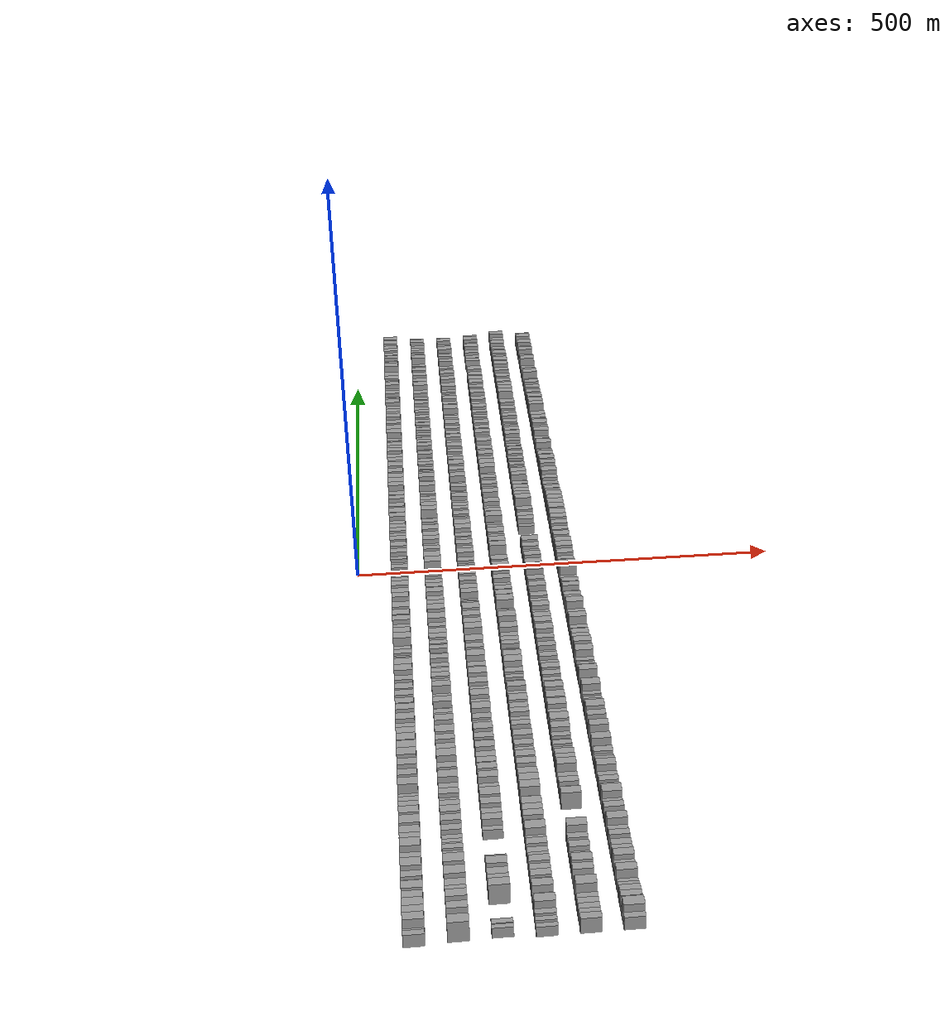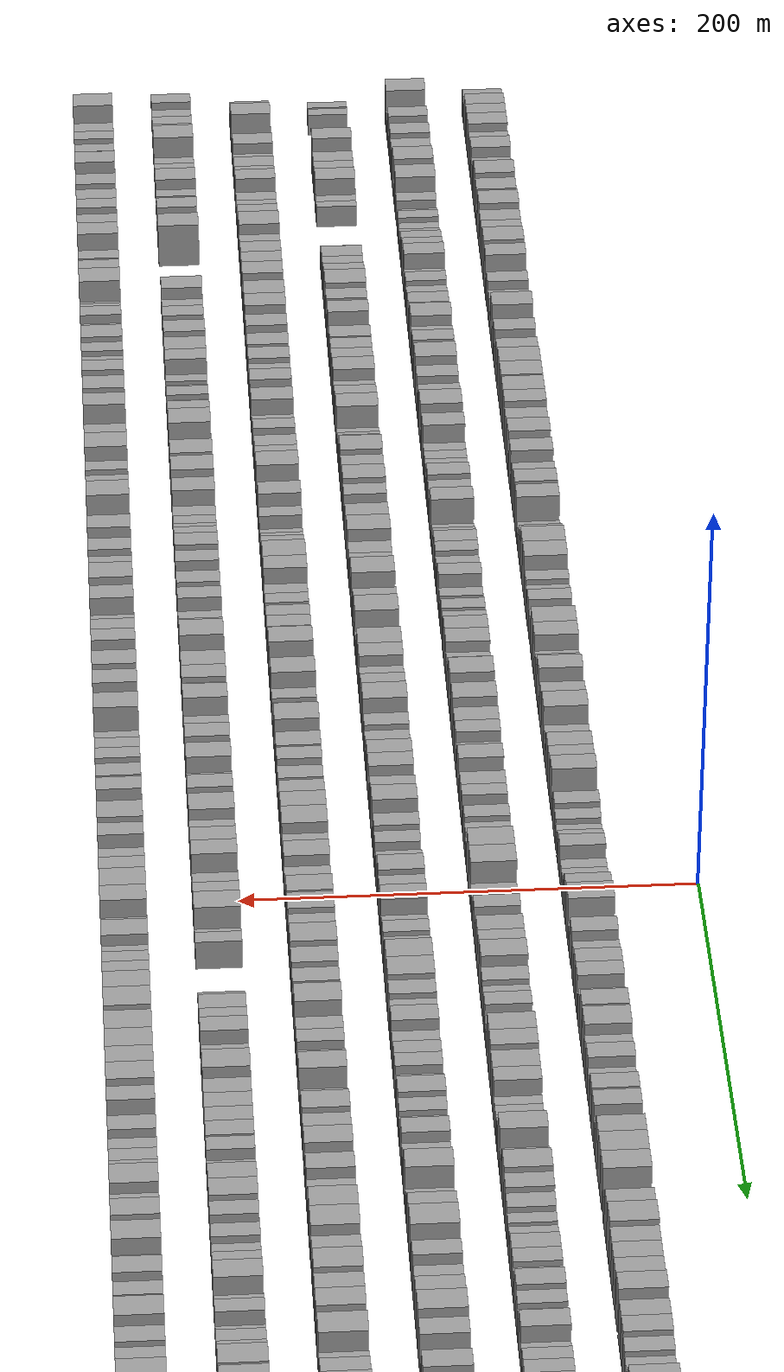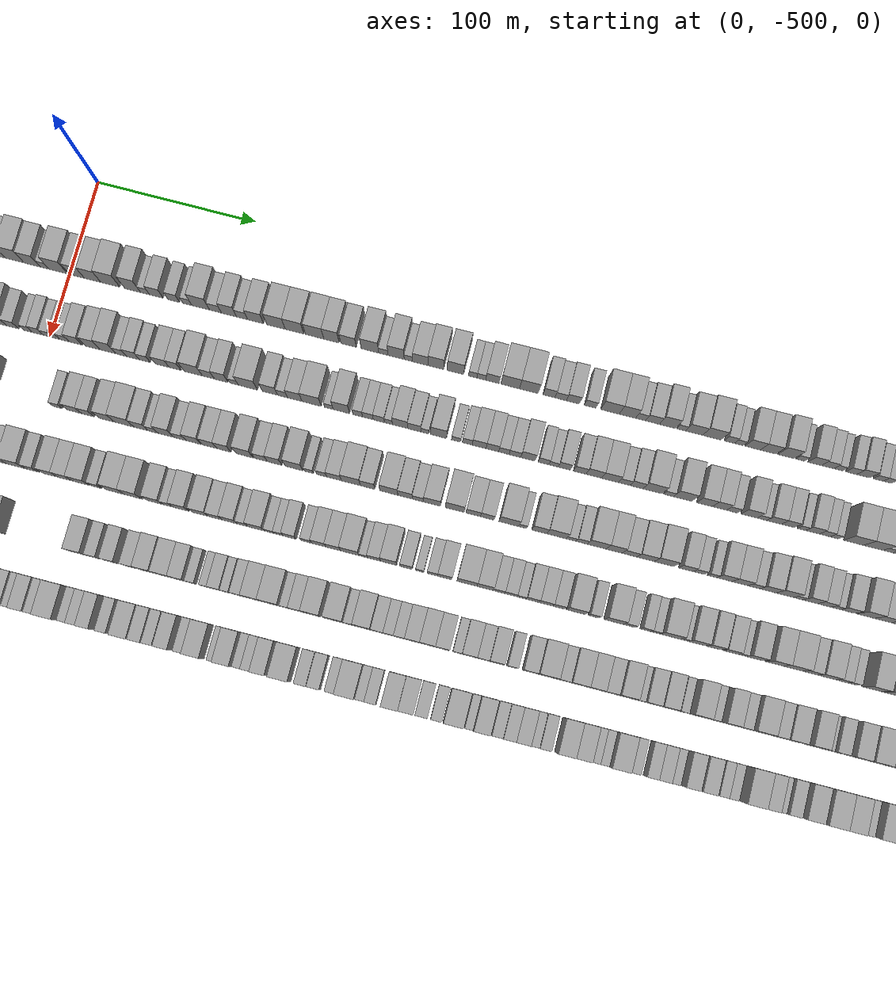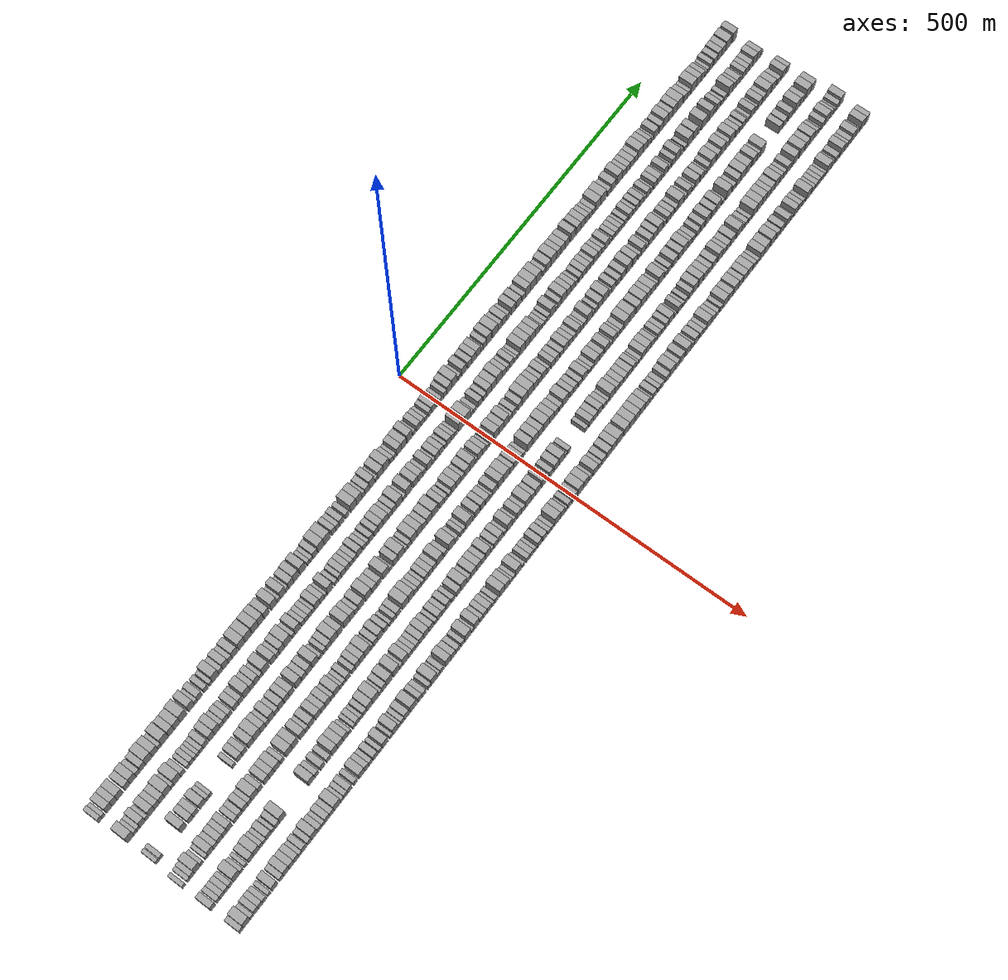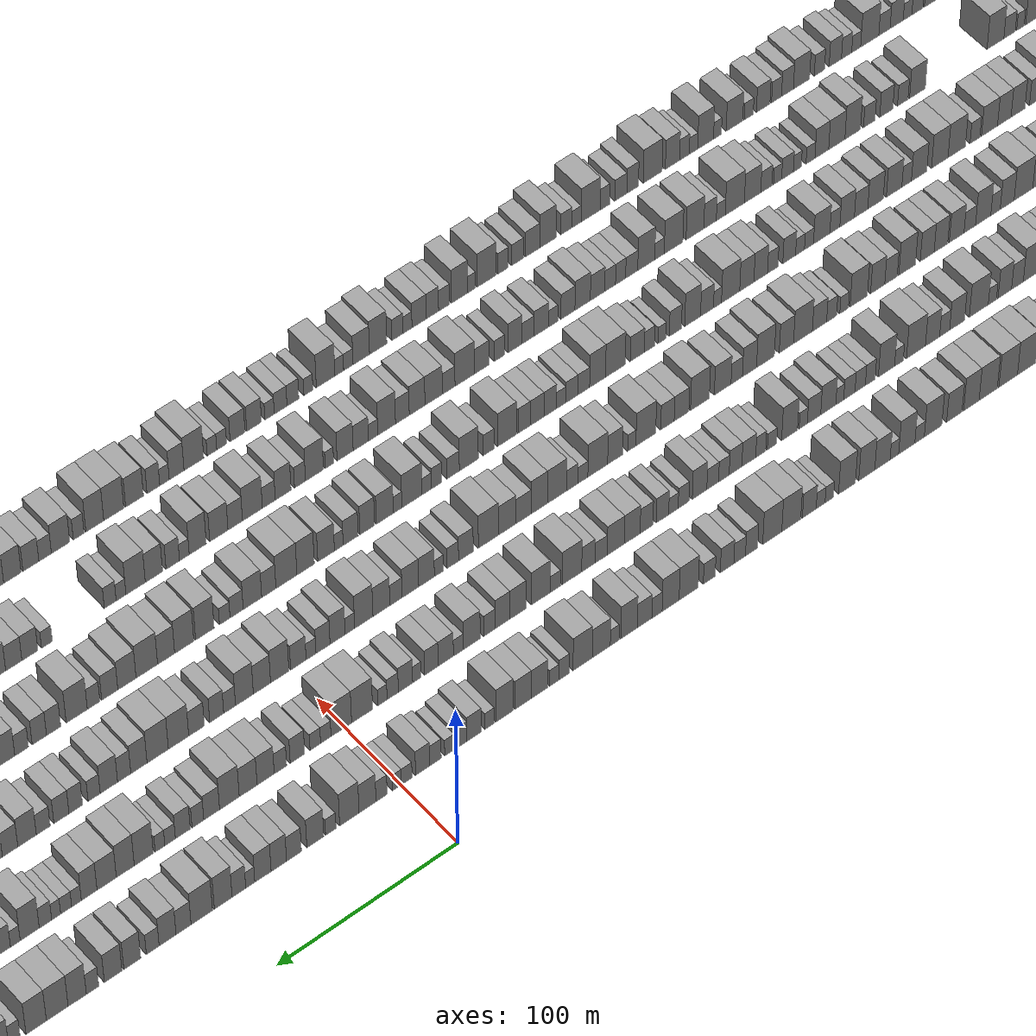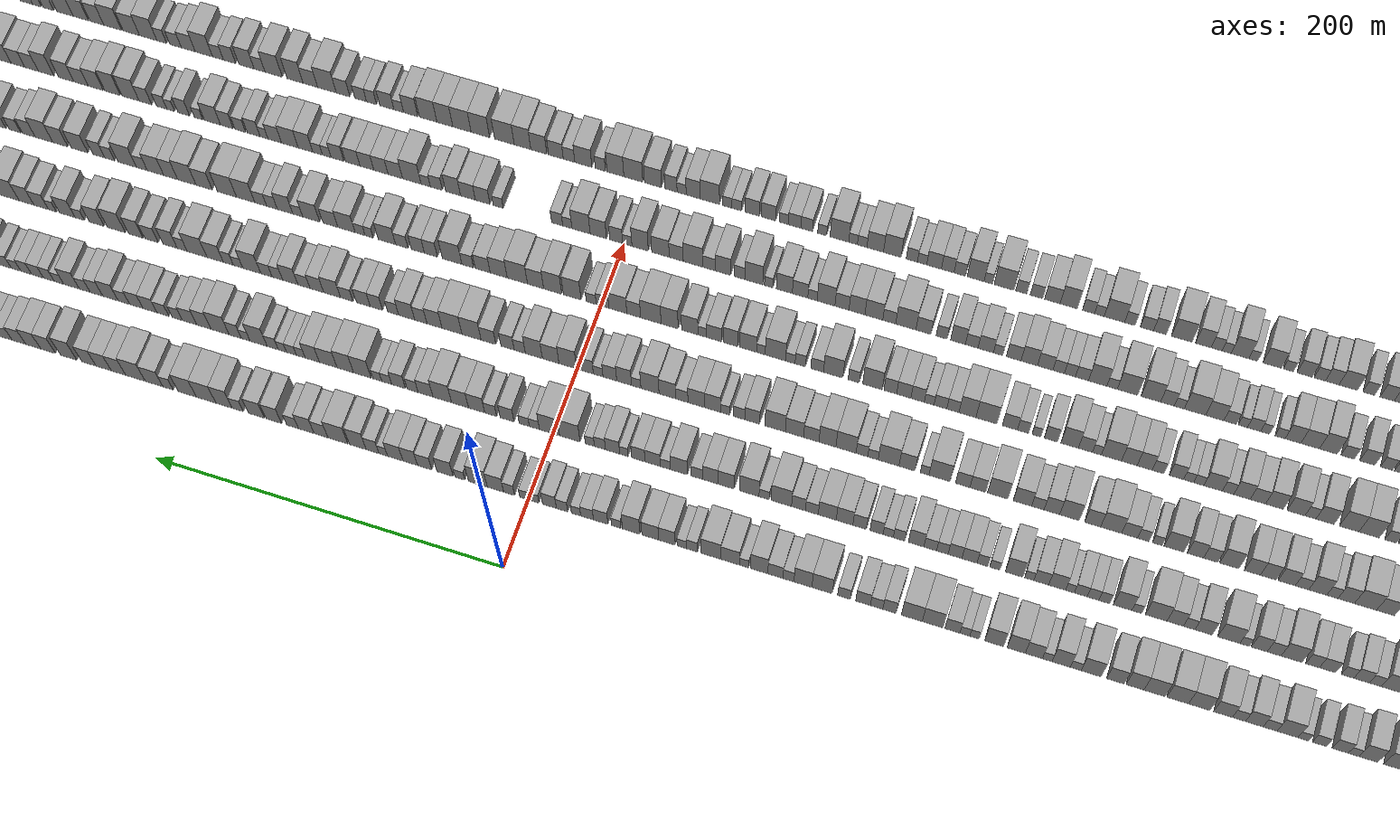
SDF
<sdf version="1.6">
 <world name="default">
  <scene>
   <sky><clouds><speed>12</speed></clouds></sky>
   <ambient>0.4 0.4 0.4 1</ambient>
   <background>0.7 0.7 0.7 1</background>
   <shadows>1</shadows>
  </scene>
  <gravity>0 0 -9.8066</gravity>
  <magnetic_field>6e-06 2.3e-05 -4.2e-05</magnetic_field>
  <physics default="0" name="default_physics" type="ode">
   <ode>
    <solver>
     <type>quick</type>
     <iters>10</iters>
     <sor>1.0</sor>
     <use_dynamic_moi_rescaling>0</use_dynamic_moi_rescaling>
    </solver>
    <constraints>
     <cfm>0</cfm>
     <erp>0.2</erp>
     <contact_max_correcting_vel>100</contact_max_correcting_vel>
     <contact_surface_layer>0.001</contact_surface_layer>
    </constraints>
   </ode>
   <max_step_size>0.004</max_step_size>
   <real_time_factor>1</real_time_factor>
   <real_time_update_rate>250</real_time_update_rate>
  </physics>
  <light name="sun" type="directional">
   <pose>0 0 10 0 0 0</pose>
   <diffuse>0.8 0.8 0.8 1</diffuse>
   <specular>0.2 0.2 0.2 1</specular>
   <attenuation>
    <range>1000</range>
    <constant>0.9</constant>
    <linear>0.01</linear>
    <quadratic>0.001</quadratic>
   </attenuation>
   <direction>-0.5 0.1 -0.9</direction>
  </light>
  <model name="building_1">
   <static>1</static>
   <pose>50.0000 -616.9016 0 0.000000 0.000000 0.000000</pose>
   <link name="link">
    <pose>0 0 7.50 0 0 0</pose>
    <collision name="collision"><geometry><box><size>20.0000 6.1968 15.0000</size></box></geometry></collision>
    <visual name="visual">
     <cast_shadows>0</cast_shadows>
     <geometry><box><size>20.0000 6.1968 15.0000</size></box></geometry>
     <material>
      <script>
       <uri>model://grey_wall/materials/scripts</uri>
       <uri>model://grey_wall/materials/textures</uri>
       <name>vrc/grey_wall</name>
      </script>
     </material>
    </visual>
   </link>
  </model>
  <model name="building_2">
   <static>1</static>
   <pose>50.0000 -611.2636 0 0.000000 0.000000 0.000000</pose>
   <link name="link">
    <pose>0 0 6.00 0 0 0</pose>
    <collision name="collision"><geometry><box><size>20.0000 5.0791 12.0000</size></box></geometry></collision>
    <visual name="visual">
     <cast_shadows>0</cast_shadows>
     <geometry><box><size>20.0000 5.0791 12.0000</size></box></geometry>
     <material>
      <script>
       <uri>model://grey_wall/materials/scripts</uri>
       <uri>model://grey_wall/materials/textures</uri>
       <name>vrc/grey_wall</name>
      </script>
     </material>
    </visual>
   </link>
  </model>
  <model name="building_3">
   <static>1</static>
   <pose>50.0000 -601.9387 0 0.000000 0.000000 0.000000</pose>
   <link name="link">
    <pose>0 0 10.50 0 0 0</pose>
    <collision name="collision"><geometry><box><size>20.0000 9.5707 21.0000</size></box></geometry></collision>
    <visual name="visual">
     <cast_shadows>0</cast_shadows>
     <geometry><box><size>20.0000 9.5707 21.0000</size></box></geometry>
     <material>
      <script>
       <uri>model://grey_wall/materials/scripts</uri>
       <uri>model://grey_wall/materials/textures</uri>
       <name>vrc/grey_wall</name>
      </script>
     </material>
    </visual>
   </link>
  </model>
  <model name="building_4">
   <static>1</static>
   <pose>50.0000 -592.8870 0 0.000000 0.000000 0.000000</pose>
   <link name="link">
    <pose>0 0 10.50 0 0 0</pose>
    <collision name="collision"><geometry><box><size>20.0000 8.5327 21.0000</size></box></geometry></collision>
    <visual name="visual">
     <cast_shadows>0</cast_shadows>
     <geometry><box><size>20.0000 8.5327 21.0000</size></box></geometry>
     <material>
      <script>
       <uri>model://grey_wall/materials/scripts</uri>
       <uri>model://grey_wall/materials/textures</uri>
       <name>vrc/grey_wall</name>
      </script>
     </material>
    </visual>
   </link>
  </model>
  <model name="building_5">
   <static>1</static>
   <pose>50.0000 -583.4798 0 0.000000 0.000000 0.000000</pose>
   <link name="link">
    <pose>0 0 10.50 0 0 0</pose>
    <collision name="collision"><geometry><box><size>20.0000 10.2817 21.0000</size></box></geometry></collision>
    <visual name="visual">
     <cast_shadows>0</cast_shadows>
     <geometry><box><size>20.0000 10.2817 21.0000</size></box></geometry>
     <material>
      <script>
       <uri>model://grey_wall/materials/scripts</uri>
       <uri>model://grey_wall/materials/textures</uri>
       <name>vrc/grey_wall</name>
      </script>
     </material>
    </visual>
   </link>
  </model>
  <model name="building_6">
   <static>1</static>
   <pose>50.0000 -570.8567 0 0.000000 0.000000 0.000000</pose>
   <link name="link">
    <pose>0 0 9.00 0 0 0</pose>
    <collision name="collision"><geometry><box><size>20.0000 8.9645 18.0000</size></box></geometry></collision>
    <visual name="visual">
     <cast_shadows>0</cast_shadows>
     <geometry><box><size>20.0000 8.9645 18.0000</size></box></geometry>
     <material>
      <script>
       <uri>model://grey_wall/materials/scripts</uri>
       <uri>model://grey_wall/materials/textures</uri>
       <name>vrc/grey_wall</name>
      </script>
     </material>
    </visual>
   </link>
  </model>
  <model name="building_7">
   <static>1</static>
   <pose>50.0000 -561.2951 0 0.000000 0.000000 0.000000</pose>
   <link name="link">
    <pose>0 0 10.50 0 0 0</pose>
    <collision name="collision"><geometry><box><size>20.0000 10.1586 21.0000</size></box></geometry></collision>
    <visual name="visual">
     <cast_shadows>0</cast_shadows>
     <geometry><box><size>20.0000 10.1586 21.0000</size></box></geometry>
     <material>
      <script>
       <uri>model://grey_wall/materials/scripts</uri>
       <uri>model://grey_wall/materials/textures</uri>
       <name>vrc/grey_wall</name>
      </script>
     </material>
    </visual>
   </link>
  </model>
  <model name="building_8">
   <static>1</static>
   <pose>50.0000 -552.7246 0 0.000000 0.000000 0.000000</pose>
   <link name="link">
    <pose>0 0 7.50 0 0 0</pose>
    <collision name="collision"><geometry><box><size>20.0000 6.9825 15.0000</size></box></geometry></collision>
    <visual name="visual">
     <cast_shadows>0</cast_shadows>
     <geometry><box><size>20.0000 6.9825 15.0000</size></box></geometry>
     <material>
      <script>
       <uri>model://grey_wall/materials/scripts</uri>
       <uri>model://grey_wall/materials/textures</uri>
       <name>vrc/grey_wall</name>
      </script>
     </material>
    </visual>
   </link>
  </model>
  <model name="building_9">
   <static>1</static>
   <pose>50.0000 -544.0356 0 0.000000 0.000000 0.000000</pose>
   <link name="link">
    <pose>0 0 9.00 0 0 0</pose>
    <collision name="collision"><geometry><box><size>20.0000 8.3956 18.0000</size></box></geometry></collision>
    <visual name="visual">
     <cast_shadows>0</cast_shadows>
     <geometry><box><size>20.0000 8.3956 18.0000</size></box></geometry>
     <material>
      <script>
       <uri>model://grey_wall/materials/scripts</uri>
       <uri>model://grey_wall/materials/textures</uri>
       <name>vrc/grey_wall</name>
      </script>
     </material>
    </visual>
   </link>
  </model>
  <model name="building_10">
   <static>1</static>
   <pose>50.0000 -534.1240 0 0.000000 0.000000 0.000000</pose>
   <link name="link">
    <pose>0 0 12.00 0 0 0</pose>
    <collision name="collision"><geometry><box><size>20.0000 11.4277 24.0000</size></box></geometry></collision>
    <visual name="visual">
     <cast_shadows>0</cast_shadows>
     <geometry><box><size>20.0000 11.4277 24.0000</size></box></geometry>
     <material>
      <script>
       <uri>model://grey_wall/materials/scripts</uri>
       <uri>model://grey_wall/materials/textures</uri>
       <name>vrc/grey_wall</name>
      </script>
     </material>
    </visual>
   </link>
  </model>
  <model name="building_11">
   <static>1</static>
   <pose>50.0000 -523.3517 0 0.000000 0.000000 0.000000</pose>
   <link name="link">
    <pose>0 0 10.50 0 0 0</pose>
    <collision name="collision"><geometry><box><size>20.0000 10.1170 21.0000</size></box></geometry></collision>
    <visual name="visual">
     <cast_shadows>0</cast_shadows>
     <geometry><box><size>20.0000 10.1170 21.0000</size></box></geometry>
     <material>
      <script>
       <uri>model://grey_wall/materials/scripts</uri>
       <uri>model://grey_wall/materials/textures</uri>
       <name>vrc/grey_wall</name>
      </script>
     </material>
    </visual>
   </link>
  </model>
  <model name="building_12">
   <static>1</static>
   <pose>50.0000 -515.4805 0 0.000000 0.000000 0.000000</pose>
   <link name="link">
    <pose>0 0 6.00 0 0 0</pose>
    <collision name="collision"><geometry><box><size>20.0000 5.6252 12.0000</size></box></geometry></collision>
    <visual name="visual">
     <cast_shadows>0</cast_shadows>
     <geometry><box><size>20.0000 5.6252 12.0000</size></box></geometry>
     <material>
      <script>
       <uri>model://grey_wall/materials/scripts</uri>
       <uri>model://grey_wall/materials/textures</uri>
       <name>vrc/grey_wall</name>
      </script>
     </material>
    </visual>
   </link>
  </model>
  <model name="building_13">
   <static>1</static>
   <pose>50.0000 -506.7315 0 0.000000 0.000000 0.000000</pose>
   <link name="link">
    <pose>0 0 12.00 0 0 0</pose>
    <collision name="collision"><geometry><box><size>20.0000 11.8728 24.0000</size></box></geometry></collision>
    <visual name="visual">
     <cast_shadows>0</cast_shadows>
     <geometry><box><size>20.0000 11.8728 24.0000</size></box></geometry>
     <material>
      <script>
       <uri>model://grey_wall/materials/scripts</uri>
       <uri>model://grey_wall/materials/textures</uri>
       <name>vrc/grey_wall</name>
      </script>
     </material>
    </visual>
   </link>
  </model>
  <model name="building_14">
   <static>1</static>
   <pose>50.0000 -495.1101 0 0.000000 0.000000 0.000000</pose>
   <link name="link">
    <pose>0 0 10.50 0 0 0</pose>
    <collision name="collision"><geometry><box><size>20.0000 9.3700 21.0000</size></box></geometry></collision>
    <visual name="visual">
     <cast_shadows>0</cast_shadows>
     <geometry><box><size>20.0000 9.3700 21.0000</size></box></geometry>
     <material>
      <script>
       <uri>model://grey_wall/materials/scripts</uri>
       <uri>model://grey_wall/materials/textures</uri>
       <name>vrc/grey_wall</name>
      </script>
     </material>
    </visual>
   </link>
  </model>
  <model name="building_15">
   <static>1</static>
   <pose>50.0000 -485.2604 0 0.000000 0.000000 0.000000</pose>
   <link name="link">
    <pose>0 0 10.50 0 0 0</pose>
    <collision name="collision"><geometry><box><size>20.0000 10.3294 21.0000</size></box></geometry></collision>
    <visual name="visual">
     <cast_shadows>0</cast_shadows>
     <geometry><box><size>20.0000 10.3294 21.0000</size></box></geometry>
     <material>
      <script>
       <uri>model://grey_wall/materials/scripts</uri>
       <uri>model://grey_wall/materials/textures</uri>
       <name>vrc/grey_wall</name>
      </script>
     </material>
    </visual>
   </link>
  </model>
  <model name="building_16">
   <static>1</static>
   <pose>50.0000 -474.0972 0 0.000000 0.000000 0.000000</pose>
   <link name="link">
    <pose>0 0 12.00 0 0 0</pose>
    <collision name="collision"><geometry><box><size>20.0000 11.9969 24.0000</size></box></geometry></collision>
    <visual name="visual">
     <cast_shadows>0</cast_shadows>
     <geometry><box><size>20.0000 11.9969 24.0000</size></box></geometry>
     <material>
      <script>
       <uri>model://grey_wall/materials/scripts</uri>
       <uri>model://grey_wall/materials/textures</uri>
       <name>vrc/grey_wall</name>
      </script>
     </material>
    </visual>
   </link>
  </model>
  <model name="building_17">
   <static>1</static>
   <pose>50.0000 -460.1339 0 0.000000 0.000000 0.000000</pose>
   <link name="link">
    <pose>0 0 12.00 0 0 0</pose>
    <collision name="collision"><geometry><box><size>20.0000 9.9295 24.0000</size></box></geometry></collision>
    <visual name="visual">
     <cast_shadows>0</cast_shadows>
     <geometry><box><size>20.0000 9.9295 24.0000</size></box></geometry>
     <material>
      <script>
       <uri>model://grey_wall/materials/scripts</uri>
       <uri>model://grey_wall/materials/textures</uri>
       <name>vrc/grey_wall</name>
      </script>
     </material>
    </visual>
   </link>
  </model>
  <model name="building_18">
   <static>1</static>
   <pose>50.0000 -452.3718 0 0.000000 0.000000 0.000000</pose>
   <link name="link">
    <pose>0 0 6.00 0 0 0</pose>
    <collision name="collision"><geometry><box><size>20.0000 5.5947 12.0000</size></box></geometry></collision>
    <visual name="visual">
     <cast_shadows>0</cast_shadows>
     <geometry><box><size>20.0000 5.5947 12.0000</size></box></geometry>
     <material>
      <script>
       <uri>model://grey_wall/materials/scripts</uri>
       <uri>model://grey_wall/materials/textures</uri>
       <name>vrc/grey_wall</name>
      </script>
     </material>
    </visual>
   </link>
  </model>
  <model name="building_19">
   <static>1</static>
   <pose>50.0000 -445.2859 0 0.000000 0.000000 0.000000</pose>
   <link name="link">
    <pose>0 0 9.00 0 0 0</pose>
    <collision name="collision"><geometry><box><size>20.0000 8.5771 18.0000</size></box></geometry></collision>
    <visual name="visual">
     <cast_shadows>0</cast_shadows>
     <geometry><box><size>20.0000 8.5771 18.0000</size></box></geometry>
     <material>
      <script>
       <uri>model://grey_wall/materials/scripts</uri>
       <uri>model://grey_wall/materials/textures</uri>
       <name>vrc/grey_wall</name>
      </script>
     </material>
    </visual>
   </link>
  </model>
  <model name="building_20">
   <static>1</static>
   <pose>50.0000 -434.3486 0 0.000000 0.000000 0.000000</pose>
   <link name="link">
    <pose>0 0 7.50 0 0 0</pose>
    <collision name="collision"><geometry><box><size>20.0000 7.2975 15.0000</size></box></geometry></collision>
    <visual name="visual">
     <cast_shadows>0</cast_shadows>
     <geometry><box><size>20.0000 7.2975 15.0000</size></box></geometry>
     <material>
      <script>
       <uri>model://grey_wall/materials/scripts</uri>
       <uri>model://grey_wall/materials/textures</uri>
       <name>vrc/grey_wall</name>
      </script>
     </material>
    </visual>
   </link>
  </model>
  <model name="building_21">
   <static>1</static>
   <pose>50.0000 -425.8590 0 0.000000 0.000000 0.000000</pose>
   <link name="link">
    <pose>0 0 6.00 0 0 0</pose>
    <collision name="collision"><geometry><box><size>20.0000 5.6818 12.0000</size></box></geometry></collision>
    <visual name="visual">
     <cast_shadows>0</cast_shadows>
     <geometry><box><size>20.0000 5.6818 12.0000</size></box></geometry>
     <material>
      <script>
       <uri>model://grey_wall/materials/scripts</uri>
       <uri>model://grey_wall/materials/textures</uri>
       <name>vrc/grey_wall</name>
      </script>
     </material>
    </visual>
   </link>
  </model>
  <model name="building_22">
   <static>1</static>
   <pose>50.0000 -417.4788 0 0.000000 0.000000 0.000000</pose>
   <link name="link">
    <pose>0 0 12.00 0 0 0</pose>
    <collision name="collision"><geometry><box><size>20.0000 11.0785 24.0000</size></box></geometry></collision>
    <visual name="visual">
     <cast_shadows>0</cast_shadows>
     <geometry><box><size>20.0000 11.0785 24.0000</size></box></geometry>
     <material>
      <script>
       <uri>model://grey_wall/materials/scripts</uri>
       <uri>model://grey_wall/materials/textures</uri>
       <name>vrc/grey_wall</name>
      </script>
     </material>
    </visual>
   </link>
  </model>
  <model name="building_23">
   <static>1</static>
   <pose>50.0000 -408.2307 0 0.000000 0.000000 0.000000</pose>
   <link name="link">
    <pose>0 0 7.50 0 0 0</pose>
    <collision name="collision"><geometry><box><size>20.0000 7.4177 15.0000</size></box></geometry></collision>
    <visual name="visual">
     <cast_shadows>0</cast_shadows>
     <geometry><box><size>20.0000 7.4177 15.0000</size></box></geometry>
     <material>
      <script>
       <uri>model://grey_wall/materials/scripts</uri>
       <uri>model://grey_wall/materials/textures</uri>
       <name>vrc/grey_wall</name>
      </script>
     </material>
    </visual>
   </link>
  </model>
  <model name="building_24">
   <static>1</static>
   <pose>50.0000 -399.8386 0 0.000000 0.000000 0.000000</pose>
   <link name="link">
    <pose>0 0 10.50 0 0 0</pose>
    <collision name="collision"><geometry><box><size>20.0000 9.3667 21.0000</size></box></geometry></collision>
    <visual name="visual">
     <cast_shadows>0</cast_shadows>
     <geometry><box><size>20.0000 9.3667 21.0000</size></box></geometry>
     <material>
      <script>
       <uri>model://grey_wall/materials/scripts</uri>
       <uri>model://grey_wall/materials/textures</uri>
       <name>vrc/grey_wall</name>
      </script>
     </material>
    </visual>
   </link>
  </model>
  <model name="building_25">
   <static>1</static>
   <pose>50.0000 -391.6832 0 0.000000 0.000000 0.000000</pose>
   <link name="link">
    <pose>0 0 7.50 0 0 0</pose>
    <collision name="collision"><geometry><box><size>20.0000 6.9440 15.0000</size></box></geometry></collision>
    <visual name="visual">
     <cast_shadows>0</cast_shadows>
     <geometry><box><size>20.0000 6.9440 15.0000</size></box></geometry>
     <material>
      <script>
       <uri>model://grey_wall/materials/scripts</uri>
       <uri>model://grey_wall/materials/textures</uri>
       <name>vrc/grey_wall</name>
      </script>
     </material>
    </visual>
   </link>
  </model>
  <model name="building_26">
   <static>1</static>
   <pose>50.0000 -383.2100 0 0.000000 0.000000 0.000000</pose>
   <link name="link">
    <pose>0 0 10.50 0 0 0</pose>
    <collision name="collision"><geometry><box><size>20.0000 10.0023 21.0000</size></box></geometry></collision>
    <visual name="visual">
     <cast_shadows>0</cast_shadows>
     <geometry><box><size>20.0000 10.0023 21.0000</size></box></geometry>
     <material>
      <script>
       <uri>model://grey_wall/materials/scripts</uri>
       <uri>model://grey_wall/materials/textures</uri>
       <name>vrc/grey_wall</name>
      </script>
     </material>
    </visual>
   </link>
  </model>
  <model name="building_27">
   <static>1</static>
   <pose>50.0000 -370.5010 0 0.000000 0.000000 0.000000</pose>
   <link name="link">
    <pose>0 0 12.00 0 0 0</pose>
    <collision name="collision"><geometry><box><size>20.0000 11.4157 24.0000</size></box></geometry></collision>
    <visual name="visual">
     <cast_shadows>0</cast_shadows>
     <geometry><box><size>20.0000 11.4157 24.0000</size></box></geometry>
     <material>
      <script>
       <uri>model://grey_wall/materials/scripts</uri>
       <uri>model://grey_wall/materials/textures</uri>
       <name>vrc/grey_wall</name>
      </script>
     </material>
    </visual>
   </link>
  </model>
  <model name="building_28">
   <static>1</static>
   <pose>50.0000 -358.9997 0 0.000000 0.000000 0.000000</pose>
   <link name="link">
    <pose>0 0 12.00 0 0 0</pose>
    <collision name="collision"><geometry><box><size>20.0000 11.5869 24.0000</size></box></geometry></collision>
    <visual name="visual">
     <cast_shadows>0</cast_shadows>
     <geometry><box><size>20.0000 11.5869 24.0000</size></box></geometry>
     <material>
      <script>
       <uri>model://grey_wall/materials/scripts</uri>
       <uri>model://grey_wall/materials/textures</uri>
       <name>vrc/grey_wall</name>
      </script>
     </material>
    </visual>
   </link>
  </model>
  <model name="building_29">
   <static>1</static>
   <pose>50.0000 -346.5559 0 0.000000 0.000000 0.000000</pose>
   <link name="link">
    <pose>0 0 12.00 0 0 0</pose>
    <collision name="collision"><geometry><box><size>20.0000 11.3006 24.0000</size></box></geometry></collision>
    <visual name="visual">
     <cast_shadows>0</cast_shadows>
     <geometry><box><size>20.0000 11.3006 24.0000</size></box></geometry>
     <material>
      <script>
       <uri>model://grey_wall/materials/scripts</uri>
       <uri>model://grey_wall/materials/textures</uri>
       <name>vrc/grey_wall</name>
      </script>
     </material>
    </visual>
   </link>
  </model>
  <model name="building_30">
   <static>1</static>
   <pose>50.0000 -336.1024 0 0.000000 0.000000 0.000000</pose>
   <link name="link">
    <pose>0 0 12.00 0 0 0</pose>
    <collision name="collision"><geometry><box><size>20.0000 9.6063 24.0000</size></box></geometry></collision>
    <visual name="visual">
     <cast_shadows>0</cast_shadows>
     <geometry><box><size>20.0000 9.6063 24.0000</size></box></geometry>
     <material>
      <script>
       <uri>model://grey_wall/materials/scripts</uri>
       <uri>model://grey_wall/materials/textures</uri>
       <name>vrc/grey_wall</name>
      </script>
     </material>
    </visual>
   </link>
  </model>
  <model name="building_31">
   <static>1</static>
   <pose>50.0000 -325.5463 0 0.000000 0.000000 0.000000</pose>
   <link name="link">
    <pose>0 0 10.50 0 0 0</pose>
    <collision name="collision"><geometry><box><size>20.0000 9.5060 21.0000</size></box></geometry></collision>
    <visual name="visual">
     <cast_shadows>0</cast_shadows>
     <geometry><box><size>20.0000 9.5060 21.0000</size></box></geometry>
     <material>
      <script>
       <uri>model://grey_wall/materials/scripts</uri>
       <uri>model://grey_wall/materials/textures</uri>
       <name>vrc/grey_wall</name>
      </script>
     </material>
    </visual>
   </link>
  </model>
  <model name="building_32">
   <static>1</static>
   <pose>50.0000 -312.3909 0 0.000000 0.000000 0.000000</pose>
   <link name="link">
    <pose>0 0 12.00 0 0 0</pose>
    <collision name="collision"><geometry><box><size>20.0000 10.8048 24.0000</size></box></geometry></collision>
    <visual name="visual">
     <cast_shadows>0</cast_shadows>
     <geometry><box><size>20.0000 10.8048 24.0000</size></box></geometry>
     <material>
      <script>
       <uri>model://grey_wall/materials/scripts</uri>
       <uri>model://grey_wall/materials/textures</uri>
       <name>vrc/grey_wall</name>
      </script>
     </material>
    </visual>
   </link>
  </model>
  <model name="building_33">
   <static>1</static>
   <pose>50.0000 -304.0890 0 0.000000 0.000000 0.000000</pose>
   <link name="link">
    <pose>0 0 6.00 0 0 0</pose>
    <collision name="collision"><geometry><box><size>20.0000 5.7989 12.0000</size></box></geometry></collision>
    <visual name="visual">
     <cast_shadows>0</cast_shadows>
     <geometry><box><size>20.0000 5.7989 12.0000</size></box></geometry>
     <material>
      <script>
       <uri>model://grey_wall/materials/scripts</uri>
       <uri>model://grey_wall/materials/textures</uri>
       <name>vrc/grey_wall</name>
      </script>
     </material>
    </visual>
   </link>
  </model>
  <model name="building_34">
   <static>1</static>
   <pose>50.0000 -296.2287 0 0.000000 0.000000 0.000000</pose>
   <link name="link">
    <pose>0 0 12.00 0 0 0</pose>
    <collision name="collision"><geometry><box><size>20.0000 9.9216 24.0000</size></box></geometry></collision>
    <visual name="visual">
     <cast_shadows>0</cast_shadows>
     <geometry><box><size>20.0000 9.9216 24.0000</size></box></geometry>
     <material>
      <script>
       <uri>model://grey_wall/materials/scripts</uri>
       <uri>model://grey_wall/materials/textures</uri>
       <name>vrc/grey_wall</name>
      </script>
     </material>
    </visual>
   </link>
  </model>
  <model name="building_35">
   <static>1</static>
   <pose>50.0000 -288.6441 0 0.000000 0.000000 0.000000</pose>
   <link name="link">
    <pose>0 0 6.00 0 0 0</pose>
    <collision name="collision"><geometry><box><size>20.0000 5.2477 12.0000</size></box></geometry></collision>
    <visual name="visual">
     <cast_shadows>0</cast_shadows>
     <geometry><box><size>20.0000 5.2477 12.0000</size></box></geometry>
     <material>
      <script>
       <uri>model://grey_wall/materials/scripts</uri>
       <uri>model://grey_wall/materials/textures</uri>
       <name>vrc/grey_wall</name>
      </script>
     </material>
    </visual>
   </link>
  </model>
  <model name="building_36">
   <static>1</static>
   <pose>50.0000 -281.3469 0 0.000000 0.000000 0.000000</pose>
   <link name="link">
    <pose>0 0 10.50 0 0 0</pose>
    <collision name="collision"><geometry><box><size>20.0000 9.3467 21.0000</size></box></geometry></collision>
    <visual name="visual">
     <cast_shadows>0</cast_shadows>
     <geometry><box><size>20.0000 9.3467 21.0000</size></box></geometry>
     <material>
      <script>
       <uri>model://grey_wall/materials/scripts</uri>
       <uri>model://grey_wall/materials/textures</uri>
       <name>vrc/grey_wall</name>
      </script>
     </material>
    </visual>
   </link>
  </model>
  <model name="building_37">
   <static>1</static>
   <pose>50.0000 -271.7772 0 0.000000 0.000000 0.000000</pose>
   <link name="link">
    <pose>0 0 12.00 0 0 0</pose>
    <collision name="collision"><geometry><box><size>20.0000 9.7928 24.0000</size></box></geometry></collision>
    <visual name="visual">
     <cast_shadows>0</cast_shadows>
     <geometry><box><size>20.0000 9.7928 24.0000</size></box></geometry>
     <material>
      <script>
       <uri>model://grey_wall/materials/scripts</uri>
       <uri>model://grey_wall/materials/textures</uri>
       <name>vrc/grey_wall</name>
      </script>
     </material>
    </visual>
   </link>
  </model>
  <model name="building_38">
   <static>1</static>
   <pose>50.0000 -259.7504 0 0.000000 0.000000 0.000000</pose>
   <link name="link">
    <pose>0 0 12.00 0 0 0</pose>
    <collision name="collision"><geometry><box><size>20.0000 10.2608 24.0000</size></box></geometry></collision>
    <visual name="visual">
     <cast_shadows>0</cast_shadows>
     <geometry><box><size>20.0000 10.2608 24.0000</size></box></geometry>
     <material>
      <script>
       <uri>model://grey_wall/materials/scripts</uri>
       <uri>model://grey_wall/materials/textures</uri>
       <name>vrc/grey_wall</name>
      </script>
     </material>
    </visual>
   </link>
  </model>
  <model name="building_39">
   <static>1</static>
   <pose>50.0000 -249.0538 0 0.000000 0.000000 0.000000</pose>
   <link name="link">
    <pose>0 0 6.00 0 0 0</pose>
    <collision name="collision"><geometry><box><size>20.0000 5.1324 12.0000</size></box></geometry></collision>
    <visual name="visual">
     <cast_shadows>0</cast_shadows>
     <geometry><box><size>20.0000 5.1324 12.0000</size></box></geometry>
     <material>
      <script>
       <uri>model://grey_wall/materials/scripts</uri>
       <uri>model://grey_wall/materials/textures</uri>
       <name>vrc/grey_wall</name>
      </script>
     </material>
    </visual>
   </link>
  </model>
  <model name="building_40">
   <static>1</static>
   <pose>50.0000 -243.7974 0 0.000000 0.000000 0.000000</pose>
   <link name="link">
    <pose>0 0 6.00 0 0 0</pose>
    <collision name="collision"><geometry><box><size>20.0000 5.3804 12.0000</size></box></geometry></collision>
    <visual name="visual">
     <cast_shadows>0</cast_shadows>
     <geometry><box><size>20.0000 5.3804 12.0000</size></box></geometry>
     <material>
      <script>
       <uri>model://grey_wall/materials/scripts</uri>
       <uri>model://grey_wall/materials/textures</uri>
       <name>vrc/grey_wall</name>
      </script>
     </material>
    </visual>
   </link>
  </model>
  <model name="building_41">
   <static>1</static>
   <pose>50.0000 -236.9577 0 0.000000 0.000000 0.000000</pose>
   <link name="link">
    <pose>0 0 9.00 0 0 0</pose>
    <collision name="collision"><geometry><box><size>20.0000 8.2990 18.0000</size></box></geometry></collision>
    <visual name="visual">
     <cast_shadows>0</cast_shadows>
     <geometry><box><size>20.0000 8.2990 18.0000</size></box></geometry>
     <material>
      <script>
       <uri>model://grey_wall/materials/scripts</uri>
       <uri>model://grey_wall/materials/textures</uri>
       <name>vrc/grey_wall</name>
      </script>
     </material>
    </visual>
   </link>
  </model>
  <model name="building_42">
   <static>1</static>
   <pose>50.0000 -226.1209 0 0.000000 0.000000 0.000000</pose>
   <link name="link">
    <pose>0 0 12.00 0 0 0</pose>
    <collision name="collision"><geometry><box><size>20.0000 11.3746 24.0000</size></box></geometry></collision>
    <visual name="visual">
     <cast_shadows>0</cast_shadows>
     <geometry><box><size>20.0000 11.3746 24.0000</size></box></geometry>
     <material>
      <script>
       <uri>model://grey_wall/materials/scripts</uri>
       <uri>model://grey_wall/materials/textures</uri>
       <name>vrc/grey_wall</name>
      </script>
     </material>
    </visual>
   </link>
  </model>
  <model name="building_43">
   <static>1</static>
   <pose>50.0000 -214.7128 0 0.000000 0.000000 0.000000</pose>
   <link name="link">
    <pose>0 0 12.00 0 0 0</pose>
    <collision name="collision"><geometry><box><size>20.0000 11.4416 24.0000</size></box></geometry></collision>
    <visual name="visual">
     <cast_shadows>0</cast_shadows>
     <geometry><box><size>20.0000 11.4416 24.0000</size></box></geometry>
     <material>
      <script>
       <uri>model://grey_wall/materials/scripts</uri>
       <uri>model://grey_wall/materials/textures</uri>
       <name>vrc/grey_wall</name>
      </script>
     </material>
    </visual>
   </link>
  </model>
  <model name="building_44">
   <static>1</static>
   <pose>50.0000 -202.3479 0 0.000000 0.000000 0.000000</pose>
   <link name="link">
    <pose>0 0 9.00 0 0 0</pose>
    <collision name="collision"><geometry><box><size>20.0000 7.2882 18.0000</size></box></geometry></collision>
    <visual name="visual">
     <cast_shadows>0</cast_shadows>
     <geometry><box><size>20.0000 7.2882 18.0000</size></box></geometry>
     <material>
      <script>
       <uri>model://grey_wall/materials/scripts</uri>
       <uri>model://grey_wall/materials/textures</uri>
       <name>vrc/grey_wall</name>
      </script>
     </material>
    </visual>
   </link>
  </model>
  <model name="building_45">
   <static>1</static>
   <pose>50.0000 -195.2462 0 0.000000 0.000000 0.000000</pose>
   <link name="link">
    <pose>0 0 7.50 0 0 0</pose>
    <collision name="collision"><geometry><box><size>20.0000 6.9153 15.0000</size></box></geometry></collision>
    <visual name="visual">
     <cast_shadows>0</cast_shadows>
     <geometry><box><size>20.0000 6.9153 15.0000</size></box></geometry>
     <material>
      <script>
       <uri>model://grey_wall/materials/scripts</uri>
       <uri>model://grey_wall/materials/textures</uri>
       <name>vrc/grey_wall</name>
      </script>
     </material>
    </visual>
   </link>
  </model>
  <model name="building_46">
   <static>1</static>
   <pose>50.0000 -187.7663 0 0.000000 0.000000 0.000000</pose>
   <link name="link">
    <pose>0 0 9.00 0 0 0</pose>
    <collision name="collision"><geometry><box><size>20.0000 8.0446 18.0000</size></box></geometry></collision>
    <visual name="visual">
     <cast_shadows>0</cast_shadows>
     <geometry><box><size>20.0000 8.0446 18.0000</size></box></geometry>
     <material>
      <script>
       <uri>model://grey_wall/materials/scripts</uri>
       <uri>model://grey_wall/materials/textures</uri>
       <name>vrc/grey_wall</name>
      </script>
     </material>
    </visual>
   </link>
  </model>
  <model name="building_47">
   <static>1</static>
   <pose>50.0000 -177.2297 0 0.000000 0.000000 0.000000</pose>
   <link name="link">
    <pose>0 0 7.50 0 0 0</pose>
    <collision name="collision"><geometry><box><size>20.0000 7.0285 15.0000</size></box></geometry></collision>
    <visual name="visual">
     <cast_shadows>0</cast_shadows>
     <geometry><box><size>20.0000 7.0285 15.0000</size></box></geometry>
     <material>
      <script>
       <uri>model://grey_wall/materials/scripts</uri>
       <uri>model://grey_wall/materials/textures</uri>
       <name>vrc/grey_wall</name>
      </script>
     </material>
    </visual>
   </link>
  </model>
  <model name="building_48">
   <static>1</static>
   <pose>50.0000 -165.0713 0 0.000000 0.000000 0.000000</pose>
   <link name="link">
    <pose>0 0 12.00 0 0 0</pose>
    <collision name="collision"><geometry><box><size>20.0000 11.2883 24.0000</size></box></geometry></collision>
    <visual name="visual">
     <cast_shadows>0</cast_shadows>
     <geometry><box><size>20.0000 11.2883 24.0000</size></box></geometry>
     <material>
      <script>
       <uri>model://grey_wall/materials/scripts</uri>
       <uri>model://grey_wall/materials/textures</uri>
       <name>vrc/grey_wall</name>
      </script>
     </material>
    </visual>
   </link>
  </model>
  <model name="building_49">
   <static>1</static>
   <pose>50.0000 -154.4397 0 0.000000 0.000000 0.000000</pose>
   <link name="link">
    <pose>0 0 12.00 0 0 0</pose>
    <collision name="collision"><geometry><box><size>20.0000 9.9748 24.0000</size></box></geometry></collision>
    <visual name="visual">
     <cast_shadows>0</cast_shadows>
     <geometry><box><size>20.0000 9.9748 24.0000</size></box></geometry>
     <material>
      <script>
       <uri>model://grey_wall/materials/scripts</uri>
       <uri>model://grey_wall/materials/textures</uri>
       <name>vrc/grey_wall</name>
      </script>
     </material>
    </visual>
   </link>
  </model>
  <model name="building_50">
   <static>1</static>
   <pose>50.0000 -146.4189 0 0.000000 0.000000 0.000000</pose>
   <link name="link">
    <pose>0 0 7.50 0 0 0</pose>
    <collision name="collision"><geometry><box><size>20.0000 6.0669 15.0000</size></box></geometry></collision>
    <visual name="visual">
     <cast_shadows>0</cast_shadows>
     <geometry><box><size>20.0000 6.0669 15.0000</size></box></geometry>
     <material>
      <script>
       <uri>model://grey_wall/materials/scripts</uri>
       <uri>model://grey_wall/materials/textures</uri>
       <name>vrc/grey_wall</name>
      </script>
     </material>
    </visual>
   </link>
  </model>
  <model name="building_51">
   <static>1</static>
   <pose>50.0000 -139.1425 0 0.000000 0.000000 0.000000</pose>
   <link name="link">
    <pose>0 0 9.00 0 0 0</pose>
    <collision name="collision"><geometry><box><size>20.0000 8.4860 18.0000</size></box></geometry></collision>
    <visual name="visual">
     <cast_shadows>0</cast_shadows>
     <geometry><box><size>20.0000 8.4860 18.0000</size></box></geometry>
     <material>
      <script>
       <uri>model://grey_wall/materials/scripts</uri>
       <uri>model://grey_wall/materials/textures</uri>
       <name>vrc/grey_wall</name>
      </script>
     </material>
    </visual>
   </link>
  </model>
  <model name="building_52">
   <static>1</static>
   <pose>50.0000 -130.0940 0 0.000000 0.000000 0.000000</pose>
   <link name="link">
    <pose>0 0 12.00 0 0 0</pose>
    <collision name="collision"><geometry><box><size>20.0000 9.6109 24.0000</size></box></geometry></collision>
    <visual name="visual">
     <cast_shadows>0</cast_shadows>
     <geometry><box><size>20.0000 9.6109 24.0000</size></box></geometry>
     <material>
      <script>
       <uri>model://grey_wall/materials/scripts</uri>
       <uri>model://grey_wall/materials/textures</uri>
       <name>vrc/grey_wall</name>
      </script>
     </material>
    </visual>
   </link>
  </model>
  <model name="building_53">
   <static>1</static>
   <pose>50.0000 -121.7255 0 0.000000 0.000000 0.000000</pose>
   <link name="link">
    <pose>0 0 6.00 0 0 0</pose>
    <collision name="collision"><geometry><box><size>20.0000 5.1261 12.0000</size></box></geometry></collision>
    <visual name="visual">
     <cast_shadows>0</cast_shadows>
     <geometry><box><size>20.0000 5.1261 12.0000</size></box></geometry>
     <material>
      <script>
       <uri>model://grey_wall/materials/scripts</uri>
       <uri>model://grey_wall/materials/textures</uri>
       <name>vrc/grey_wall</name>
      </script>
     </material>
    </visual>
   </link>
  </model>
  <model name="building_54">
   <static>1</static>
   <pose>50.0000 -113.9349 0 0.000000 0.000000 0.000000</pose>
   <link name="link">
    <pose>0 0 10.50 0 0 0</pose>
    <collision name="collision"><geometry><box><size>20.0000 10.4553 21.0000</size></box></geometry></collision>
    <visual name="visual">
     <cast_shadows>0</cast_shadows>
     <geometry><box><size>20.0000 10.4553 21.0000</size></box></geometry>
     <material>
      <script>
       <uri>model://grey_wall/materials/scripts</uri>
       <uri>model://grey_wall/materials/textures</uri>
       <name>vrc/grey_wall</name>
      </script>
     </material>
    </visual>
   </link>
  </model>
  <model name="building_55">
   <static>1</static>
   <pose>50.0000 -103.1495 0 0.000000 0.000000 0.000000</pose>
   <link name="link">
    <pose>0 0 12.00 0 0 0</pose>
    <collision name="collision"><geometry><box><size>20.0000 11.1154 24.0000</size></box></geometry></collision>
    <visual name="visual">
     <cast_shadows>0</cast_shadows>
     <geometry><box><size>20.0000 11.1154 24.0000</size></box></geometry>
     <material>
      <script>
       <uri>model://grey_wall/materials/scripts</uri>
       <uri>model://grey_wall/materials/textures</uri>
       <name>vrc/grey_wall</name>
      </script>
     </material>
    </visual>
   </link>
  </model>
  <model name="building_56">
   <static>1</static>
   <pose>50.0000 -92.5312 0 0.000000 0.000000 0.000000</pose>
   <link name="link">
    <pose>0 0 7.50 0 0 0</pose>
    <collision name="collision"><geometry><box><size>20.0000 6.1210 15.0000</size></box></geometry></collision>
    <visual name="visual">
     <cast_shadows>0</cast_shadows>
     <geometry><box><size>20.0000 6.1210 15.0000</size></box></geometry>
     <material>
      <script>
       <uri>model://grey_wall/materials/scripts</uri>
       <uri>model://grey_wall/materials/textures</uri>
       <name>vrc/grey_wall</name>
      </script>
     </material>
    </visual>
   </link>
  </model>
  <model name="building_57">
   <static>1</static>
   <pose>50.0000 -86.7811 0 0.000000 0.000000 0.000000</pose>
   <link name="link">
    <pose>0 0 6.00 0 0 0</pose>
    <collision name="collision"><geometry><box><size>20.0000 5.3792 12.0000</size></box></geometry></collision>
    <visual name="visual">
     <cast_shadows>0</cast_shadows>
     <geometry><box><size>20.0000 5.3792 12.0000</size></box></geometry>
     <material>
      <script>
       <uri>model://grey_wall/materials/scripts</uri>
       <uri>model://grey_wall/materials/textures</uri>
       <name>vrc/grey_wall</name>
      </script>
     </material>
    </visual>
   </link>
  </model>
  <model name="building_58">
   <static>1</static>
   <pose>50.0000 -78.4356 0 0.000000 0.000000 0.000000</pose>
   <link name="link">
    <pose>0 0 10.50 0 0 0</pose>
    <collision name="collision"><geometry><box><size>20.0000 9.3119 21.0000</size></box></geometry></collision>
    <visual name="visual">
     <cast_shadows>0</cast_shadows>
     <geometry><box><size>20.0000 9.3119 21.0000</size></box></geometry>
     <material>
      <script>
       <uri>model://grey_wall/materials/scripts</uri>
       <uri>model://grey_wall/materials/textures</uri>
       <name>vrc/grey_wall</name>
      </script>
     </material>
    </visual>
   </link>
  </model>
  <model name="building_59">
   <static>1</static>
   <pose>50.0000 -69.0138 0 0.000000 0.000000 0.000000</pose>
   <link name="link">
    <pose>0 0 10.50 0 0 0</pose>
    <collision name="collision"><geometry><box><size>20.0000 9.5317 21.0000</size></box></geometry></collision>
    <visual name="visual">
     <cast_shadows>0</cast_shadows>
     <geometry><box><size>20.0000 9.5317 21.0000</size></box></geometry>
     <material>
      <script>
       <uri>model://grey_wall/materials/scripts</uri>
       <uri>model://grey_wall/materials/textures</uri>
       <name>vrc/grey_wall</name>
      </script>
     </material>
    </visual>
   </link>
  </model>
  <model name="building_60">
   <static>1</static>
   <pose>50.0000 -58.2890 0 0.000000 0.000000 0.000000</pose>
   <link name="link">
    <pose>0 0 12.00 0 0 0</pose>
    <collision name="collision"><geometry><box><size>20.0000 9.9177 24.0000</size></box></geometry></collision>
    <visual name="visual">
     <cast_shadows>0</cast_shadows>
     <geometry><box><size>20.0000 9.9177 24.0000</size></box></geometry>
     <material>
      <script>
       <uri>model://grey_wall/materials/scripts</uri>
       <uri>model://grey_wall/materials/textures</uri>
       <name>vrc/grey_wall</name>
      </script>
     </material>
    </visual>
   </link>
  </model>
  <model name="building_61">
   <static>1</static>
   <pose>50.0000 -49.7137 0 0.000000 0.000000 0.000000</pose>
   <link name="link">
    <pose>0 0 6.00 0 0 0</pose>
    <collision name="collision"><geometry><box><size>20.0000 5.2330 12.0000</size></box></geometry></collision>
    <visual name="visual">
     <cast_shadows>0</cast_shadows>
     <geometry><box><size>20.0000 5.2330 12.0000</size></box></geometry>
     <material>
      <script>
       <uri>model://grey_wall/materials/scripts</uri>
       <uri>model://grey_wall/materials/textures</uri>
       <name>vrc/grey_wall</name>
      </script>
     </material>
    </visual>
   </link>
  </model>
  <model name="building_62">
   <static>1</static>
   <pose>50.0000 -40.9994 0 0.000000 0.000000 0.000000</pose>
   <link name="link">
    <pose>0 0 9.00 0 0 0</pose>
    <collision name="collision"><geometry><box><size>20.0000 8.1956 18.0000</size></box></geometry></collision>
    <visual name="visual">
     <cast_shadows>0</cast_shadows>
     <geometry><box><size>20.0000 8.1956 18.0000</size></box></geometry>
     <material>
      <script>
       <uri>model://grey_wall/materials/scripts</uri>
       <uri>model://grey_wall/materials/textures</uri>
       <name>vrc/grey_wall</name>
      </script>
     </material>
    </visual>
   </link>
  </model>
  <model name="building_63">
   <static>1</static>
   <pose>50.0000 -33.2702 0 0.000000 0.000000 0.000000</pose>
   <link name="link">
    <pose>0 0 7.50 0 0 0</pose>
    <collision name="collision"><geometry><box><size>20.0000 7.2627 15.0000</size></box></geometry></collision>
    <visual name="visual">
     <cast_shadows>0</cast_shadows>
     <geometry><box><size>20.0000 7.2627 15.0000</size></box></geometry>
     <material>
      <script>
       <uri>model://grey_wall/materials/scripts</uri>
       <uri>model://grey_wall/materials/textures</uri>
       <name>vrc/grey_wall</name>
      </script>
     </material>
    </visual>
   </link>
  </model>
  <model name="building_64">
   <static>1</static>
   <pose>50.0000 -26.9642 0 0.000000 0.000000 0.000000</pose>
   <link name="link">
    <pose>0 0 6.00 0 0 0</pose>
    <collision name="collision"><geometry><box><size>20.0000 5.3493 12.0000</size></box></geometry></collision>
    <visual name="visual">
     <cast_shadows>0</cast_shadows>
     <geometry><box><size>20.0000 5.3493 12.0000</size></box></geometry>
     <material>
      <script>
       <uri>model://grey_wall/materials/scripts</uri>
       <uri>model://grey_wall/materials/textures</uri>
       <name>vrc/grey_wall</name>
      </script>
     </material>
    </visual>
   </link>
  </model>
  <model name="building_65">
   <static>1</static>
   <pose>50.0000 -19.0683 0 0.000000 0.000000 0.000000</pose>
   <link name="link">
    <pose>0 0 7.50 0 0 0</pose>
    <collision name="collision"><geometry><box><size>20.0000 6.4423 15.0000</size></box></geometry></collision>
    <visual name="visual">
     <cast_shadows>0</cast_shadows>
     <geometry><box><size>20.0000 6.4423 15.0000</size></box></geometry>
     <material>
      <script>
       <uri>model://grey_wall/materials/scripts</uri>
       <uri>model://grey_wall/materials/textures</uri>
       <name>vrc/grey_wall</name>
      </script>
     </material>
    </visual>
   </link>
  </model>
  <model name="building_66">
   <static>1</static>
   <pose>50.0000 -11.8717 0 0.000000 0.000000 0.000000</pose>
   <link name="link">
    <pose>0 0 9.00 0 0 0</pose>
    <collision name="collision"><geometry><box><size>20.0000 7.9509 18.0000</size></box></geometry></collision>
    <visual name="visual">
     <cast_shadows>0</cast_shadows>
     <geometry><box><size>20.0000 7.9509 18.0000</size></box></geometry>
     <material>
      <script>
       <uri>model://grey_wall/materials/scripts</uri>
       <uri>model://grey_wall/materials/textures</uri>
       <name>vrc/grey_wall</name>
      </script>
     </material>
    </visual>
   </link>
  </model>
  <model name="building_67">
   <static>1</static>
   <pose>50.0000 -2.9251 0 0.000000 0.000000 0.000000</pose>
   <link name="link">
    <pose>0 0 6.00 0 0 0</pose>
    <collision name="collision"><geometry><box><size>20.0000 5.9424 12.0000</size></box></geometry></collision>
    <visual name="visual">
     <cast_shadows>0</cast_shadows>
     <geometry><box><size>20.0000 5.9424 12.0000</size></box></geometry>
     <material>
      <script>
       <uri>model://grey_wall/materials/scripts</uri>
       <uri>model://grey_wall/materials/textures</uri>
       <name>vrc/grey_wall</name>
      </script>
     </material>
    </visual>
   </link>
  </model>
  <model name="building_68">
   <static>1</static>
   <pose>50.0000 2.5611 0 0.000000 0.000000 0.000000</pose>
   <link name="link">
    <pose>0 0 6.00 0 0 0</pose>
    <collision name="collision"><geometry><box><size>20.0000 5.0298 12.0000</size></box></geometry></collision>
    <visual name="visual">
     <cast_shadows>0</cast_shadows>
     <geometry><box><size>20.0000 5.0298 12.0000</size></box></geometry>
     <material>
      <script>
       <uri>model://grey_wall/materials/scripts</uri>
       <uri>model://grey_wall/materials/textures</uri>
       <name>vrc/grey_wall</name>
      </script>
     </material>
    </visual>
   </link>
  </model>
  <model name="building_69">
   <static>1</static>
   <pose>50.0000 11.1921 0 0.000000 0.000000 0.000000</pose>
   <link name="link">
    <pose>0 0 7.50 0 0 0</pose>
    <collision name="collision"><geometry><box><size>20.0000 6.2323 15.0000</size></box></geometry></collision>
    <visual name="visual">
     <cast_shadows>0</cast_shadows>
     <geometry><box><size>20.0000 6.2323 15.0000</size></box></geometry>
     <material>
      <script>
       <uri>model://grey_wall/materials/scripts</uri>
       <uri>model://grey_wall/materials/textures</uri>
       <name>vrc/grey_wall</name>
      </script>
     </material>
    </visual>
   </link>
  </model>
  <model name="building_70">
   <static>1</static>
   <pose>50.0000 19.0318 0 0.000000 0.000000 0.000000</pose>
   <link name="link">
    <pose>0 0 10.50 0 0 0</pose>
    <collision name="collision"><geometry><box><size>20.0000 9.4470 21.0000</size></box></geometry></collision>
    <visual name="visual">
     <cast_shadows>0</cast_shadows>
     <geometry><box><size>20.0000 9.4470 21.0000</size></box></geometry>
     <material>
      <script>
       <uri>model://grey_wall/materials/scripts</uri>
       <uri>model://grey_wall/materials/textures</uri>
       <name>vrc/grey_wall</name>
      </script>
     </material>
    </visual>
   </link>
  </model>
  <model name="building_71">
   <static>1</static>
   <pose>50.0000 29.1392 0 0.000000 0.000000 0.000000</pose>
   <link name="link">
    <pose>0 0 12.00 0 0 0</pose>
    <collision name="collision"><geometry><box><size>20.0000 10.7678 24.0000</size></box></geometry></collision>
    <visual name="visual">
     <cast_shadows>0</cast_shadows>
     <geometry><box><size>20.0000 10.7678 24.0000</size></box></geometry>
     <material>
      <script>
       <uri>model://grey_wall/materials/scripts</uri>
       <uri>model://grey_wall/materials/textures</uri>
       <name>vrc/grey_wall</name>
      </script>
     </material>
    </visual>
   </link>
  </model>
  <model name="building_72">
   <static>1</static>
   <pose>50.0000 39.4350 0 0.000000 0.000000 0.000000</pose>
   <link name="link">
    <pose>0 0 6.00 0 0 0</pose>
    <collision name="collision"><geometry><box><size>20.0000 5.8238 12.0000</size></box></geometry></collision>
    <visual name="visual">
     <cast_shadows>0</cast_shadows>
     <geometry><box><size>20.0000 5.8238 12.0000</size></box></geometry>
     <material>
      <script>
       <uri>model://grey_wall/materials/scripts</uri>
       <uri>model://grey_wall/materials/textures</uri>
       <name>vrc/grey_wall</name>
      </script>
     </material>
    </visual>
   </link>
  </model>
  <model name="building_73">
   <static>1</static>
   <pose>50.0000 48.0004 0 0.000000 0.000000 0.000000</pose>
   <link name="link">
    <pose>0 0 10.50 0 0 0</pose>
    <collision name="collision"><geometry><box><size>20.0000 9.3071 21.0000</size></box></geometry></collision>
    <visual name="visual">
     <cast_shadows>0</cast_shadows>
     <geometry><box><size>20.0000 9.3071 21.0000</size></box></geometry>
     <material>
      <script>
       <uri>model://grey_wall/materials/scripts</uri>
       <uri>model://grey_wall/materials/textures</uri>
       <name>vrc/grey_wall</name>
      </script>
     </material>
    </visual>
   </link>
  </model>
  <model name="building_74">
   <static>1</static>
   <pose>50.0000 59.7397 0 0.000000 0.000000 0.000000</pose>
   <link name="link">
    <pose>0 0 9.00 0 0 0</pose>
    <collision name="collision"><geometry><box><size>20.0000 8.1716 18.0000</size></box></geometry></collision>
    <visual name="visual">
     <cast_shadows>0</cast_shadows>
     <geometry><box><size>20.0000 8.1716 18.0000</size></box></geometry>
     <material>
      <script>
       <uri>model://grey_wall/materials/scripts</uri>
       <uri>model://grey_wall/materials/textures</uri>
       <name>vrc/grey_wall</name>
      </script>
     </material>
    </visual>
   </link>
  </model>
  <model name="building_75">
   <static>1</static>
   <pose>50.0000 68.0638 0 0.000000 0.000000 0.000000</pose>
   <link name="link">
    <pose>0 0 10.50 0 0 0</pose>
    <collision name="collision"><geometry><box><size>20.0000 8.4766 21.0000</size></box></geometry></collision>
    <visual name="visual">
     <cast_shadows>0</cast_shadows>
     <geometry><box><size>20.0000 8.4766 21.0000</size></box></geometry>
     <material>
      <script>
       <uri>model://grey_wall/materials/scripts</uri>
       <uri>model://grey_wall/materials/textures</uri>
       <name>vrc/grey_wall</name>
      </script>
     </material>
    </visual>
   </link>
  </model>
  <model name="building_76">
   <static>1</static>
   <pose>50.0000 76.7756 0 0.000000 0.000000 0.000000</pose>
   <link name="link">
    <pose>0 0 10.50 0 0 0</pose>
    <collision name="collision"><geometry><box><size>20.0000 8.9470 21.0000</size></box></geometry></collision>
    <visual name="visual">
     <cast_shadows>0</cast_shadows>
     <geometry><box><size>20.0000 8.9470 21.0000</size></box></geometry>
     <material>
      <script>
       <uri>model://grey_wall/materials/scripts</uri>
       <uri>model://grey_wall/materials/textures</uri>
       <name>vrc/grey_wall</name>
      </script>
     </material>
    </visual>
   </link>
  </model>
  <model name="building_77">
   <static>1</static>
   <pose>50.0000 83.7111 0 0.000000 0.000000 0.000000</pose>
   <link name="link">
    <pose>0 0 6.00 0 0 0</pose>
    <collision name="collision"><geometry><box><size>20.0000 4.9240 12.0000</size></box></geometry></collision>
    <visual name="visual">
     <cast_shadows>0</cast_shadows>
     <geometry><box><size>20.0000 4.9240 12.0000</size></box></geometry>
     <material>
      <script>
       <uri>model://grey_wall/materials/scripts</uri>
       <uri>model://grey_wall/materials/textures</uri>
       <name>vrc/grey_wall</name>
      </script>
     </material>
    </visual>
   </link>
  </model>
  <model name="building_78">
   <static>1</static>
   <pose>50.0000 89.8989 0 0.000000 0.000000 0.000000</pose>
   <link name="link">
    <pose>0 0 9.00 0 0 0</pose>
    <collision name="collision"><geometry><box><size>20.0000 7.4517 18.0000</size></box></geometry></collision>
    <visual name="visual">
     <cast_shadows>0</cast_shadows>
     <geometry><box><size>20.0000 7.4517 18.0000</size></box></geometry>
     <material>
      <script>
       <uri>model://grey_wall/materials/scripts</uri>
       <uri>model://grey_wall/materials/textures</uri>
       <name>vrc/grey_wall</name>
      </script>
     </material>
    </visual>
   </link>
  </model>
  <model name="building_79">
   <static>1</static>
   <pose>50.0000 98.4519 0 0.000000 0.000000 0.000000</pose>
   <link name="link">
    <pose>0 0 12.00 0 0 0</pose>
    <collision name="collision"><geometry><box><size>20.0000 9.6544 24.0000</size></box></geometry></collision>
    <visual name="visual">
     <cast_shadows>0</cast_shadows>
     <geometry><box><size>20.0000 9.6544 24.0000</size></box></geometry>
     <material>
      <script>
       <uri>model://grey_wall/materials/scripts</uri>
       <uri>model://grey_wall/materials/textures</uri>
       <name>vrc/grey_wall</name>
      </script>
     </material>
    </visual>
   </link>
  </model>
  <model name="building_80">
   <static>1</static>
   <pose>50.0000 110.0770 0 0.000000 0.000000 0.000000</pose>
   <link name="link">
    <pose>0 0 12.00 0 0 0</pose>
    <collision name="collision"><geometry><box><size>20.0000 11.5958 24.0000</size></box></geometry></collision>
    <visual name="visual">
     <cast_shadows>0</cast_shadows>
     <geometry><box><size>20.0000 11.5958 24.0000</size></box></geometry>
     <material>
      <script>
       <uri>model://grey_wall/materials/scripts</uri>
       <uri>model://grey_wall/materials/textures</uri>
       <name>vrc/grey_wall</name>
      </script>
     </material>
    </visual>
   </link>
  </model>
  <model name="building_81">
   <static>1</static>
   <pose>50.0000 119.9259 0 0.000000 0.000000 0.000000</pose>
   <link name="link">
    <pose>0 0 9.00 0 0 0</pose>
    <collision name="collision"><geometry><box><size>20.0000 8.1019 18.0000</size></box></geometry></collision>
    <visual name="visual">
     <cast_shadows>0</cast_shadows>
     <geometry><box><size>20.0000 8.1019 18.0000</size></box></geometry>
     <material>
      <script>
       <uri>model://grey_wall/materials/scripts</uri>
       <uri>model://grey_wall/materials/textures</uri>
       <name>vrc/grey_wall</name>
      </script>
     </material>
    </visual>
   </link>
  </model>
  <model name="building_82">
   <static>1</static>
   <pose>50.0000 128.5362 0 0.000000 0.000000 0.000000</pose>
   <link name="link">
    <pose>0 0 10.50 0 0 0</pose>
    <collision name="collision"><geometry><box><size>20.0000 9.1188 21.0000</size></box></geometry></collision>
    <visual name="visual">
     <cast_shadows>0</cast_shadows>
     <geometry><box><size>20.0000 9.1188 21.0000</size></box></geometry>
     <material>
      <script>
       <uri>model://grey_wall/materials/scripts</uri>
       <uri>model://grey_wall/materials/textures</uri>
       <name>vrc/grey_wall</name>
      </script>
     </material>
    </visual>
   </link>
  </model>
  <model name="building_83">
   <static>1</static>
   <pose>50.0000 136.5406 0 0.000000 0.000000 0.000000</pose>
   <link name="link">
    <pose>0 0 7.50 0 0 0</pose>
    <collision name="collision"><geometry><box><size>20.0000 6.8900 15.0000</size></box></geometry></collision>
    <visual name="visual">
     <cast_shadows>0</cast_shadows>
     <geometry><box><size>20.0000 6.8900 15.0000</size></box></geometry>
     <material>
      <script>
       <uri>model://grey_wall/materials/scripts</uri>
       <uri>model://grey_wall/materials/textures</uri>
       <name>vrc/grey_wall</name>
      </script>
     </material>
    </visual>
   </link>
  </model>
  <model name="building_84">
   <static>1</static>
   <pose>50.0000 147.4978 0 0.000000 0.000000 0.000000</pose>
   <link name="link">
    <pose>0 0 10.50 0 0 0</pose>
    <collision name="collision"><geometry><box><size>20.0000 9.0243 21.0000</size></box></geometry></collision>
    <visual name="visual">
     <cast_shadows>0</cast_shadows>
     <geometry><box><size>20.0000 9.0243 21.0000</size></box></geometry>
     <material>
      <script>
       <uri>model://grey_wall/materials/scripts</uri>
       <uri>model://grey_wall/materials/textures</uri>
       <name>vrc/grey_wall</name>
      </script>
     </material>
    </visual>
   </link>
  </model>
  <model name="building_85">
   <static>1</static>
   <pose>50.0000 157.6955 0 0.000000 0.000000 0.000000</pose>
   <link name="link">
    <pose>0 0 10.50 0 0 0</pose>
    <collision name="collision"><geometry><box><size>20.0000 9.3711 21.0000</size></box></geometry></collision>
    <visual name="visual">
     <cast_shadows>0</cast_shadows>
     <geometry><box><size>20.0000 9.3711 21.0000</size></box></geometry>
     <material>
      <script>
       <uri>model://grey_wall/materials/scripts</uri>
       <uri>model://grey_wall/materials/textures</uri>
       <name>vrc/grey_wall</name>
      </script>
     </material>
    </visual>
   </link>
  </model>
  <model name="building_86">
   <static>1</static>
   <pose>50.0000 168.6823 0 0.000000 0.000000 0.000000</pose>
   <link name="link">
    <pose>0 0 7.50 0 0 0</pose>
    <collision name="collision"><geometry><box><size>20.0000 6.6025 15.0000</size></box></geometry></collision>
    <visual name="visual">
     <cast_shadows>0</cast_shadows>
     <geometry><box><size>20.0000 6.6025 15.0000</size></box></geometry>
     <material>
      <script>
       <uri>model://grey_wall/materials/scripts</uri>
       <uri>model://grey_wall/materials/textures</uri>
       <name>vrc/grey_wall</name>
      </script>
     </material>
    </visual>
   </link>
  </model>
  <model name="building_87">
   <static>1</static>
   <pose>50.0000 176.8110 0 0.000000 0.000000 0.000000</pose>
   <link name="link">
    <pose>0 0 12.00 0 0 0</pose>
    <collision name="collision"><geometry><box><size>20.0000 9.6549 24.0000</size></box></geometry></collision>
    <visual name="visual">
     <cast_shadows>0</cast_shadows>
     <geometry><box><size>20.0000 9.6549 24.0000</size></box></geometry>
     <material>
      <script>
       <uri>model://grey_wall/materials/scripts</uri>
       <uri>model://grey_wall/materials/textures</uri>
       <name>vrc/grey_wall</name>
      </script>
     </material>
    </visual>
   </link>
  </model>
  <model name="building_88">
   <static>1</static>
   <pose>50.0000 187.3847 0 0.000000 0.000000 0.000000</pose>
   <link name="link">
    <pose>0 0 12.00 0 0 0</pose>
    <collision name="collision"><geometry><box><size>20.0000 11.4924 24.0000</size></box></geometry></collision>
    <visual name="visual">
     <cast_shadows>0</cast_shadows>
     <geometry><box><size>20.0000 11.4924 24.0000</size></box></geometry>
     <material>
      <script>
       <uri>model://grey_wall/materials/scripts</uri>
       <uri>model://grey_wall/materials/textures</uri>
       <name>vrc/grey_wall</name>
      </script>
     </material>
    </visual>
   </link>
  </model>
  <model name="building_89">
   <static>1</static>
   <pose>50.0000 198.4945 0 0.000000 0.000000 0.000000</pose>
   <link name="link">
    <pose>0 0 12.00 0 0 0</pose>
    <collision name="collision"><geometry><box><size>20.0000 10.7272 24.0000</size></box></geometry></collision>
    <visual name="visual">
     <cast_shadows>0</cast_shadows>
     <geometry><box><size>20.0000 10.7272 24.0000</size></box></geometry>
     <material>
      <script>
       <uri>model://grey_wall/materials/scripts</uri>
       <uri>model://grey_wall/materials/textures</uri>
       <name>vrc/grey_wall</name>
      </script>
     </material>
    </visual>
   </link>
  </model>
  <model name="building_90">
   <static>1</static>
   <pose>50.0000 209.9155 0 0.000000 0.000000 0.000000</pose>
   <link name="link">
    <pose>0 0 7.50 0 0 0</pose>
    <collision name="collision"><geometry><box><size>20.0000 6.1148 15.0000</size></box></geometry></collision>
    <visual name="visual">
     <cast_shadows>0</cast_shadows>
     <geometry><box><size>20.0000 6.1148 15.0000</size></box></geometry>
     <material>
      <script>
       <uri>model://grey_wall/materials/scripts</uri>
       <uri>model://grey_wall/materials/textures</uri>
       <name>vrc/grey_wall</name>
      </script>
     </material>
    </visual>
   </link>
  </model>
  <model name="building_91">
   <static>1</static>
   <pose>50.0000 218.1866 0 0.000000 0.000000 0.000000</pose>
   <link name="link">
    <pose>0 0 10.50 0 0 0</pose>
    <collision name="collision"><geometry><box><size>20.0000 10.4274 21.0000</size></box></geometry></collision>
    <visual name="visual">
     <cast_shadows>0</cast_shadows>
     <geometry><box><size>20.0000 10.4274 21.0000</size></box></geometry>
     <material>
      <script>
       <uri>model://grey_wall/materials/scripts</uri>
       <uri>model://grey_wall/materials/textures</uri>
       <name>vrc/grey_wall</name>
      </script>
     </material>
    </visual>
   </link>
  </model>
  <model name="building_92">
   <static>1</static>
   <pose>50.0000 229.2195 0 0.000000 0.000000 0.000000</pose>
   <link name="link">
    <pose>0 0 12.00 0 0 0</pose>
    <collision name="collision"><geometry><box><size>20.0000 11.6385 24.0000</size></box></geometry></collision>
    <visual name="visual">
     <cast_shadows>0</cast_shadows>
     <geometry><box><size>20.0000 11.6385 24.0000</size></box></geometry>
     <material>
      <script>
       <uri>model://grey_wall/materials/scripts</uri>
       <uri>model://grey_wall/materials/textures</uri>
       <name>vrc/grey_wall</name>
      </script>
     </material>
    </visual>
   </link>
  </model>
  <model name="building_93">
   <static>1</static>
   <pose>50.0000 239.3570 0 0.000000 0.000000 0.000000</pose>
   <link name="link">
    <pose>0 0 10.50 0 0 0</pose>
    <collision name="collision"><geometry><box><size>20.0000 8.6364 21.0000</size></box></geometry></collision>
    <visual name="visual">
     <cast_shadows>0</cast_shadows>
     <geometry><box><size>20.0000 8.6364 21.0000</size></box></geometry>
     <material>
      <script>
       <uri>model://grey_wall/materials/scripts</uri>
       <uri>model://grey_wall/materials/textures</uri>
       <name>vrc/grey_wall</name>
      </script>
     </material>
    </visual>
   </link>
  </model>
  <model name="building_94">
   <static>1</static>
   <pose>50.0000 248.2365 0 0.000000 0.000000 0.000000</pose>
   <link name="link">
    <pose>0 0 10.50 0 0 0</pose>
    <collision name="collision"><geometry><box><size>20.0000 9.1226 21.0000</size></box></geometry></collision>
    <visual name="visual">
     <cast_shadows>0</cast_shadows>
     <geometry><box><size>20.0000 9.1226 21.0000</size></box></geometry>
     <material>
      <script>
       <uri>model://grey_wall/materials/scripts</uri>
       <uri>model://grey_wall/materials/textures</uri>
       <name>vrc/grey_wall</name>
      </script>
     </material>
    </visual>
   </link>
  </model>
  <model name="building_95">
   <static>1</static>
   <pose>50.0000 257.0243 0 0.000000 0.000000 0.000000</pose>
   <link name="link">
    <pose>0 0 10.50 0 0 0</pose>
    <collision name="collision"><geometry><box><size>20.0000 8.4530 21.0000</size></box></geometry></collision>
    <visual name="visual">
     <cast_shadows>0</cast_shadows>
     <geometry><box><size>20.0000 8.4530 21.0000</size></box></geometry>
     <material>
      <script>
       <uri>model://grey_wall/materials/scripts</uri>
       <uri>model://grey_wall/materials/textures</uri>
       <name>vrc/grey_wall</name>
      </script>
     </material>
    </visual>
   </link>
  </model>
  <model name="building_96">
   <static>1</static>
   <pose>50.0000 269.1460 0 0.000000 0.000000 0.000000</pose>
   <link name="link">
    <pose>0 0 12.00 0 0 0</pose>
    <collision name="collision"><geometry><box><size>20.0000 9.7904 24.0000</size></box></geometry></collision>
    <visual name="visual">
     <cast_shadows>0</cast_shadows>
     <geometry><box><size>20.0000 9.7904 24.0000</size></box></geometry>
     <material>
      <script>
       <uri>model://grey_wall/materials/scripts</uri>
       <uri>model://grey_wall/materials/textures</uri>
       <name>vrc/grey_wall</name>
      </script>
     </material>
    </visual>
   </link>
  </model>
  <model name="building_97">
   <static>1</static>
   <pose>50.0000 281.4803 0 0.000000 0.000000 0.000000</pose>
   <link name="link">
    <pose>0 0 10.50 0 0 0</pose>
    <collision name="collision"><geometry><box><size>20.0000 8.8783 21.0000</size></box></geometry></collision>
    <visual name="visual">
     <cast_shadows>0</cast_shadows>
     <geometry><box><size>20.0000 8.8783 21.0000</size></box></geometry>
     <material>
      <script>
       <uri>model://grey_wall/materials/scripts</uri>
       <uri>model://grey_wall/materials/textures</uri>
       <name>vrc/grey_wall</name>
      </script>
     </material>
    </visual>
   </link>
  </model>
  <model name="building_98">
   <static>1</static>
   <pose>50.0000 290.4282 0 0.000000 0.000000 0.000000</pose>
   <link name="link">
    <pose>0 0 10.50 0 0 0</pose>
    <collision name="collision"><geometry><box><size>20.0000 9.0176 21.0000</size></box></geometry></collision>
    <visual name="visual">
     <cast_shadows>0</cast_shadows>
     <geometry><box><size>20.0000 9.0176 21.0000</size></box></geometry>
     <material>
      <script>
       <uri>model://grey_wall/materials/scripts</uri>
       <uri>model://grey_wall/materials/textures</uri>
       <name>vrc/grey_wall</name>
      </script>
     </material>
    </visual>
   </link>
  </model>
  <model name="building_99">
   <static>1</static>
   <pose>50.0000 299.0356 0 0.000000 0.000000 0.000000</pose>
   <link name="link">
    <pose>0 0 9.00 0 0 0</pose>
    <collision name="collision"><geometry><box><size>20.0000 8.1972 18.0000</size></box></geometry></collision>
    <visual name="visual">
     <cast_shadows>0</cast_shadows>
     <geometry><box><size>20.0000 8.1972 18.0000</size></box></geometry>
     <material>
      <script>
       <uri>model://grey_wall/materials/scripts</uri>
       <uri>model://grey_wall/materials/textures</uri>
       <name>vrc/grey_wall</name>
      </script>
     </material>
    </visual>
   </link>
  </model>
  <model name="building_100">
   <static>1</static>
   <pose>50.0000 306.5376 0 0.000000 0.000000 0.000000</pose>
   <link name="link">
    <pose>0 0 7.50 0 0 0</pose>
    <collision name="collision"><geometry><box><size>20.0000 6.8069 15.0000</size></box></geometry></collision>
    <visual name="visual">
     <cast_shadows>0</cast_shadows>
     <geometry><box><size>20.0000 6.8069 15.0000</size></box></geometry>
     <material>
      <script>
       <uri>model://grey_wall/materials/scripts</uri>
       <uri>model://grey_wall/materials/textures</uri>
       <name>vrc/grey_wall</name>
      </script>
     </material>
    </visual>
   </link>
  </model>
  <model name="building_101">
   <static>1</static>
   <pose>50.0000 313.2041 0 0.000000 0.000000 0.000000</pose>
   <link name="link">
    <pose>0 0 7.50 0 0 0</pose>
    <collision name="collision"><geometry><box><size>20.0000 6.5261 15.0000</size></box></geometry></collision>
    <visual name="visual">
     <cast_shadows>0</cast_shadows>
     <geometry><box><size>20.0000 6.5261 15.0000</size></box></geometry>
     <material>
      <script>
       <uri>model://grey_wall/materials/scripts</uri>
       <uri>model://grey_wall/materials/textures</uri>
       <name>vrc/grey_wall</name>
      </script>
     </material>
    </visual>
   </link>
  </model>
  <model name="building_102">
   <static>1</static>
   <pose>50.0000 322.0785 0 0.000000 0.000000 0.000000</pose>
   <link name="link">
    <pose>0 0 12.00 0 0 0</pose>
    <collision name="collision"><geometry><box><size>20.0000 11.2226 24.0000</size></box></geometry></collision>
    <visual name="visual">
     <cast_shadows>0</cast_shadows>
     <geometry><box><size>20.0000 11.2226 24.0000</size></box></geometry>
     <material>
      <script>
       <uri>model://grey_wall/materials/scripts</uri>
       <uri>model://grey_wall/materials/textures</uri>
       <name>vrc/grey_wall</name>
      </script>
     </material>
    </visual>
   </link>
  </model>
  <model name="building_103">
   <static>1</static>
   <pose>50.0000 333.5019 0 0.000000 0.000000 0.000000</pose>
   <link name="link">
    <pose>0 0 12.00 0 0 0</pose>
    <collision name="collision"><geometry><box><size>20.0000 11.6243 24.0000</size></box></geometry></collision>
    <visual name="visual">
     <cast_shadows>0</cast_shadows>
     <geometry><box><size>20.0000 11.6243 24.0000</size></box></geometry>
     <material>
      <script>
       <uri>model://grey_wall/materials/scripts</uri>
       <uri>model://grey_wall/materials/textures</uri>
       <name>vrc/grey_wall</name>
      </script>
     </material>
    </visual>
   </link>
  </model>
  <model name="building_104">
   <static>1</static>
   <pose>50.0000 345.9176 0 0.000000 0.000000 0.000000</pose>
   <link name="link">
    <pose>0 0 7.50 0 0 0</pose>
    <collision name="collision"><geometry><box><size>20.0000 7.2070 15.0000</size></box></geometry></collision>
    <visual name="visual">
     <cast_shadows>0</cast_shadows>
     <geometry><box><size>20.0000 7.2070 15.0000</size></box></geometry>
     <material>
      <script>
       <uri>model://grey_wall/materials/scripts</uri>
       <uri>model://grey_wall/materials/textures</uri>
       <name>vrc/grey_wall</name>
      </script>
     </material>
    </visual>
   </link>
  </model>
  <model name="building_105">
   <static>1</static>
   <pose>50.0000 354.4840 0 0.000000 0.000000 0.000000</pose>
   <link name="link">
    <pose>0 0 10.50 0 0 0</pose>
    <collision name="collision"><geometry><box><size>20.0000 9.9259 21.0000</size></box></geometry></collision>
    <visual name="visual">
     <cast_shadows>0</cast_shadows>
     <geometry><box><size>20.0000 9.9259 21.0000</size></box></geometry>
     <material>
      <script>
       <uri>model://grey_wall/materials/scripts</uri>
       <uri>model://grey_wall/materials/textures</uri>
       <name>vrc/grey_wall</name>
      </script>
     </material>
    </visual>
   </link>
  </model>
  <model name="building_106">
   <static>1</static>
   <pose>50.0000 367.8768 0 0.000000 0.000000 0.000000</pose>
   <link name="link">
    <pose>0 0 12.00 0 0 0</pose>
    <collision name="collision"><geometry><box><size>20.0000 10.8597 24.0000</size></box></geometry></collision>
    <visual name="visual">
     <cast_shadows>0</cast_shadows>
     <geometry><box><size>20.0000 10.8597 24.0000</size></box></geometry>
     <material>
      <script>
       <uri>model://grey_wall/materials/scripts</uri>
       <uri>model://grey_wall/materials/textures</uri>
       <name>vrc/grey_wall</name>
      </script>
     </material>
    </visual>
   </link>
  </model>
  <model name="building_107">
   <static>1</static>
   <pose>50.0000 377.7399 0 0.000000 0.000000 0.000000</pose>
   <link name="link">
    <pose>0 0 9.00 0 0 0</pose>
    <collision name="collision"><geometry><box><size>20.0000 8.8666 18.0000</size></box></geometry></collision>
    <visual name="visual">
     <cast_shadows>0</cast_shadows>
     <geometry><box><size>20.0000 8.8666 18.0000</size></box></geometry>
     <material>
      <script>
       <uri>model://grey_wall/materials/scripts</uri>
       <uri>model://grey_wall/materials/textures</uri>
       <name>vrc/grey_wall</name>
      </script>
     </material>
    </visual>
   </link>
  </model>
  <model name="building_108">
   <static>1</static>
   <pose>50.0000 386.0869 0 0.000000 0.000000 0.000000</pose>
   <link name="link">
    <pose>0 0 9.00 0 0 0</pose>
    <collision name="collision"><geometry><box><size>20.0000 7.8273 18.0000</size></box></geometry></collision>
    <visual name="visual">
     <cast_shadows>0</cast_shadows>
     <geometry><box><size>20.0000 7.8273 18.0000</size></box></geometry>
     <material>
      <script>
       <uri>model://grey_wall/materials/scripts</uri>
       <uri>model://grey_wall/materials/textures</uri>
       <name>vrc/grey_wall</name>
      </script>
     </material>
    </visual>
   </link>
  </model>
  <model name="building_109">
   <static>1</static>
   <pose>50.0000 394.4726 0 0.000000 0.000000 0.000000</pose>
   <link name="link">
    <pose>0 0 9.00 0 0 0</pose>
    <collision name="collision"><geometry><box><size>20.0000 8.9442 18.0000</size></box></geometry></collision>
    <visual name="visual">
     <cast_shadows>0</cast_shadows>
     <geometry><box><size>20.0000 8.9442 18.0000</size></box></geometry>
     <material>
      <script>
       <uri>model://grey_wall/materials/scripts</uri>
       <uri>model://grey_wall/materials/textures</uri>
       <name>vrc/grey_wall</name>
      </script>
     </material>
    </visual>
   </link>
  </model>
  <model name="building_110">
   <static>1</static>
   <pose>50.0000 402.7370 0 0.000000 0.000000 0.000000</pose>
   <link name="link">
    <pose>0 0 9.00 0 0 0</pose>
    <collision name="collision"><geometry><box><size>20.0000 7.5845 18.0000</size></box></geometry></collision>
    <visual name="visual">
     <cast_shadows>0</cast_shadows>
     <geometry><box><size>20.0000 7.5845 18.0000</size></box></geometry>
     <material>
      <script>
       <uri>model://grey_wall/materials/scripts</uri>
       <uri>model://grey_wall/materials/textures</uri>
       <name>vrc/grey_wall</name>
      </script>
     </material>
    </visual>
   </link>
  </model>
  <model name="building_111">
   <static>1</static>
   <pose>50.0000 412.1072 0 0.000000 0.000000 0.000000</pose>
   <link name="link">
    <pose>0 0 12.00 0 0 0</pose>
    <collision name="collision"><geometry><box><size>20.0000 11.1560 24.0000</size></box></geometry></collision>
    <visual name="visual">
     <cast_shadows>0</cast_shadows>
     <geometry><box><size>20.0000 11.1560 24.0000</size></box></geometry>
     <material>
      <script>
       <uri>model://grey_wall/materials/scripts</uri>
       <uri>model://grey_wall/materials/textures</uri>
       <name>vrc/grey_wall</name>
      </script>
     </material>
    </visual>
   </link>
  </model>
  <model name="building_112">
   <static>1</static>
   <pose>50.0000 422.6053 0 0.000000 0.000000 0.000000</pose>
   <link name="link">
    <pose>0 0 10.50 0 0 0</pose>
    <collision name="collision"><geometry><box><size>20.0000 9.8401 21.0000</size></box></geometry></collision>
    <visual name="visual">
     <cast_shadows>0</cast_shadows>
     <geometry><box><size>20.0000 9.8401 21.0000</size></box></geometry>
     <material>
      <script>
       <uri>model://grey_wall/materials/scripts</uri>
       <uri>model://grey_wall/materials/textures</uri>
       <name>vrc/grey_wall</name>
      </script>
     </material>
    </visual>
   </link>
  </model>
  <model name="building_113">
   <static>1</static>
   <pose>50.0000 431.1931 0 0.000000 0.000000 0.000000</pose>
   <link name="link">
    <pose>0 0 9.00 0 0 0</pose>
    <collision name="collision"><geometry><box><size>20.0000 7.3356 18.0000</size></box></geometry></collision>
    <visual name="visual">
     <cast_shadows>0</cast_shadows>
     <geometry><box><size>20.0000 7.3356 18.0000</size></box></geometry>
     <material>
      <script>
       <uri>model://grey_wall/materials/scripts</uri>
       <uri>model://grey_wall/materials/textures</uri>
       <name>vrc/grey_wall</name>
      </script>
     </material>
    </visual>
   </link>
  </model>
  <model name="building_114">
   <static>1</static>
   <pose>50.0000 438.3121 0 0.000000 0.000000 0.000000</pose>
   <link name="link">
    <pose>0 0 6.00 0 0 0</pose>
    <collision name="collision"><geometry><box><size>20.0000 4.9024 12.0000</size></box></geometry></collision>
    <visual name="visual">
     <cast_shadows>0</cast_shadows>
     <geometry><box><size>20.0000 4.9024 12.0000</size></box></geometry>
     <material>
      <script>
       <uri>model://grey_wall/materials/scripts</uri>
       <uri>model://grey_wall/materials/textures</uri>
       <name>vrc/grey_wall</name>
      </script>
     </material>
    </visual>
   </link>
  </model>
  <model name="building_115">
   <static>1</static>
   <pose>50.0000 445.5779 0 0.000000 0.000000 0.000000</pose>
   <link name="link">
    <pose>0 0 10.50 0 0 0</pose>
    <collision name="collision"><geometry><box><size>20.0000 9.6292 21.0000</size></box></geometry></collision>
    <visual name="visual">
     <cast_shadows>0</cast_shadows>
     <geometry><box><size>20.0000 9.6292 21.0000</size></box></geometry>
     <material>
      <script>
       <uri>model://grey_wall/materials/scripts</uri>
       <uri>model://grey_wall/materials/textures</uri>
       <name>vrc/grey_wall</name>
      </script>
     </material>
    </visual>
   </link>
  </model>
  <model name="building_116">
   <static>1</static>
   <pose>50.0000 457.5779 0 0.000000 0.000000 0.000000</pose>
   <link name="link">
    <pose>0 0 9.00 0 0 0</pose>
    <collision name="collision"><geometry><box><size>20.0000 8.3707 18.0000</size></box></geometry></collision>
    <visual name="visual">
     <cast_shadows>0</cast_shadows>
     <geometry><box><size>20.0000 8.3707 18.0000</size></box></geometry>
     <material>
      <script>
       <uri>model://grey_wall/materials/scripts</uri>
       <uri>model://grey_wall/materials/textures</uri>
       <name>vrc/grey_wall</name>
      </script>
     </material>
    </visual>
   </link>
  </model>
  <model name="building_117">
   <static>1</static>
   <pose>50.0000 467.1968 0 0.000000 0.000000 0.000000</pose>
   <link name="link">
    <pose>0 0 12.00 0 0 0</pose>
    <collision name="collision"><geometry><box><size>20.0000 10.8672 24.0000</size></box></geometry></collision>
    <visual name="visual">
     <cast_shadows>0</cast_shadows>
     <geometry><box><size>20.0000 10.8672 24.0000</size></box></geometry>
     <material>
      <script>
       <uri>model://grey_wall/materials/scripts</uri>
       <uri>model://grey_wall/materials/textures</uri>
       <name>vrc/grey_wall</name>
      </script>
     </material>
    </visual>
   </link>
  </model>
  <model name="building_118">
   <static>1</static>
   <pose>50.0000 477.1448 0 0.000000 0.000000 0.000000</pose>
   <link name="link">
    <pose>0 0 10.50 0 0 0</pose>
    <collision name="collision"><geometry><box><size>20.0000 9.0289 21.0000</size></box></geometry></collision>
    <visual name="visual">
     <cast_shadows>0</cast_shadows>
     <geometry><box><size>20.0000 9.0289 21.0000</size></box></geometry>
     <material>
      <script>
       <uri>model://grey_wall/materials/scripts</uri>
       <uri>model://grey_wall/materials/textures</uri>
       <name>vrc/grey_wall</name>
      </script>
     </material>
    </visual>
   </link>
  </model>
  <model name="building_119">
   <static>1</static>
   <pose>50.0000 486.7063 0 0.000000 0.000000 0.000000</pose>
   <link name="link">
    <pose>0 0 12.00 0 0 0</pose>
    <collision name="collision"><geometry><box><size>20.0000 10.0941 24.0000</size></box></geometry></collision>
    <visual name="visual">
     <cast_shadows>0</cast_shadows>
     <geometry><box><size>20.0000 10.0941 24.0000</size></box></geometry>
     <material>
      <script>
       <uri>model://grey_wall/materials/scripts</uri>
       <uri>model://grey_wall/materials/textures</uri>
       <name>vrc/grey_wall</name>
      </script>
     </material>
    </visual>
   </link>
  </model>
  <model name="building_120">
   <static>1</static>
   <pose>50.0000 497.6066 0 0.000000 0.000000 0.000000</pose>
   <link name="link">
    <pose>0 0 12.00 0 0 0</pose>
    <collision name="collision"><geometry><box><size>20.0000 11.7064 24.0000</size></box></geometry></collision>
    <visual name="visual">
     <cast_shadows>0</cast_shadows>
     <geometry><box><size>20.0000 11.7064 24.0000</size></box></geometry>
     <material>
      <script>
       <uri>model://grey_wall/materials/scripts</uri>
       <uri>model://grey_wall/materials/textures</uri>
       <name>vrc/grey_wall</name>
      </script>
     </material>
    </visual>
   </link>
  </model>
  <model name="building_121">
   <static>1</static>
   <pose>50.0000 510.4955 0 0.000000 0.000000 0.000000</pose>
   <link name="link">
    <pose>0 0 9.00 0 0 0</pose>
    <collision name="collision"><geometry><box><size>20.0000 8.0716 18.0000</size></box></geometry></collision>
    <visual name="visual">
     <cast_shadows>0</cast_shadows>
     <geometry><box><size>20.0000 8.0716 18.0000</size></box></geometry>
     <material>
      <script>
       <uri>model://grey_wall/materials/scripts</uri>
       <uri>model://grey_wall/materials/textures</uri>
       <name>vrc/grey_wall</name>
      </script>
     </material>
    </visual>
   </link>
  </model>
  <model name="building_122">
   <static>1</static>
   <pose>50.0000 518.0108 0 0.000000 0.000000 0.000000</pose>
   <link name="link">
    <pose>0 0 7.50 0 0 0</pose>
    <collision name="collision"><geometry><box><size>20.0000 6.9590 15.0000</size></box></geometry></collision>
    <visual name="visual">
     <cast_shadows>0</cast_shadows>
     <geometry><box><size>20.0000 6.9590 15.0000</size></box></geometry>
     <material>
      <script>
       <uri>model://grey_wall/materials/scripts</uri>
       <uri>model://grey_wall/materials/textures</uri>
       <name>vrc/grey_wall</name>
      </script>
     </material>
    </visual>
   </link>
  </model>
  <model name="building_123">
   <static>1</static>
   <pose>50.0000 528.4596 0 0.000000 0.000000 0.000000</pose>
   <link name="link">
    <pose>0 0 12.00 0 0 0</pose>
    <collision name="collision"><geometry><box><size>20.0000 11.9385 24.0000</size></box></geometry></collision>
    <visual name="visual">
     <cast_shadows>0</cast_shadows>
     <geometry><box><size>20.0000 11.9385 24.0000</size></box></geometry>
     <material>
      <script>
       <uri>model://grey_wall/materials/scripts</uri>
       <uri>model://grey_wall/materials/textures</uri>
       <name>vrc/grey_wall</name>
      </script>
     </material>
    </visual>
   </link>
  </model>
  <model name="building_124">
   <static>1</static>
   <pose>50.0000 539.5472 0 0.000000 0.000000 0.000000</pose>
   <link name="link">
    <pose>0 0 10.50 0 0 0</pose>
    <collision name="collision"><geometry><box><size>20.0000 10.2366 21.0000</size></box></geometry></collision>
    <visual name="visual">
     <cast_shadows>0</cast_shadows>
     <geometry><box><size>20.0000 10.2366 21.0000</size></box></geometry>
     <material>
      <script>
       <uri>model://grey_wall/materials/scripts</uri>
       <uri>model://grey_wall/materials/textures</uri>
       <name>vrc/grey_wall</name>
      </script>
     </material>
    </visual>
   </link>
  </model>
  <model name="building_125">
   <static>1</static>
   <pose>50.0000 548.7740 0 0.000000 0.000000 0.000000</pose>
   <link name="link">
    <pose>0 0 9.00 0 0 0</pose>
    <collision name="collision"><geometry><box><size>20.0000 8.2170 18.0000</size></box></geometry></collision>
    <visual name="visual">
     <cast_shadows>0</cast_shadows>
     <geometry><box><size>20.0000 8.2170 18.0000</size></box></geometry>
     <material>
      <script>
       <uri>model://grey_wall/materials/scripts</uri>
       <uri>model://grey_wall/materials/textures</uri>
       <name>vrc/grey_wall</name>
      </script>
     </material>
    </visual>
   </link>
  </model>
  <model name="building_126">
   <static>1</static>
   <pose>50.0000 556.3509 0 0.000000 0.000000 0.000000</pose>
   <link name="link">
    <pose>0 0 6.00 0 0 0</pose>
    <collision name="collision"><geometry><box><size>20.0000 4.9368 12.0000</size></box></geometry></collision>
    <visual name="visual">
     <cast_shadows>0</cast_shadows>
     <geometry><box><size>20.0000 4.9368 12.0000</size></box></geometry>
     <material>
      <script>
       <uri>model://grey_wall/materials/scripts</uri>
       <uri>model://grey_wall/materials/textures</uri>
       <name>vrc/grey_wall</name>
      </script>
     </material>
    </visual>
   </link>
  </model>
  <model name="building_127">
   <static>1</static>
   <pose>50.0000 561.2526 0 0.000000 0.000000 0.000000</pose>
   <link name="link">
    <pose>0 0 6.00 0 0 0</pose>
    <collision name="collision"><geometry><box><size>20.0000 4.8665 12.0000</size></box></geometry></collision>
    <visual name="visual">
     <cast_shadows>0</cast_shadows>
     <geometry><box><size>20.0000 4.8665 12.0000</size></box></geometry>
     <material>
      <script>
       <uri>model://grey_wall/materials/scripts</uri>
       <uri>model://grey_wall/materials/textures</uri>
       <name>vrc/grey_wall</name>
      </script>
     </material>
    </visual>
   </link>
  </model>
  <model name="building_128">
   <static>1</static>
   <pose>50.0000 567.3759 0 0.000000 0.000000 0.000000</pose>
   <link name="link">
    <pose>0 0 9.00 0 0 0</pose>
    <collision name="collision"><geometry><box><size>20.0000 7.3802 18.0000</size></box></geometry></collision>
    <visual name="visual">
     <cast_shadows>0</cast_shadows>
     <geometry><box><size>20.0000 7.3802 18.0000</size></box></geometry>
     <material>
      <script>
       <uri>model://grey_wall/materials/scripts</uri>
       <uri>model://grey_wall/materials/textures</uri>
       <name>vrc/grey_wall</name>
      </script>
     </material>
    </visual>
   </link>
  </model>
  <model name="building_129">
   <static>1</static>
   <pose>50.0000 577.3105 0 0.000000 0.000000 0.000000</pose>
   <link name="link">
    <pose>0 0 9.00 0 0 0</pose>
    <collision name="collision"><geometry><box><size>20.0000 8.4890 18.0000</size></box></geometry></collision>
    <visual name="visual">
     <cast_shadows>0</cast_shadows>
     <geometry><box><size>20.0000 8.4890 18.0000</size></box></geometry>
     <material>
      <script>
       <uri>model://grey_wall/materials/scripts</uri>
       <uri>model://grey_wall/materials/textures</uri>
       <name>vrc/grey_wall</name>
      </script>
     </material>
    </visual>
   </link>
  </model>
  <model name="building_130">
   <static>1</static>
   <pose>50.0000 586.0100 0 0.000000 0.000000 0.000000</pose>
   <link name="link">
    <pose>0 0 10.50 0 0 0</pose>
    <collision name="collision"><geometry><box><size>20.0000 8.9100 21.0000</size></box></geometry></collision>
    <visual name="visual">
     <cast_shadows>0</cast_shadows>
     <geometry><box><size>20.0000 8.9100 21.0000</size></box></geometry>
     <material>
      <script>
       <uri>model://grey_wall/materials/scripts</uri>
       <uri>model://grey_wall/materials/textures</uri>
       <name>vrc/grey_wall</name>
      </script>
     </material>
    </visual>
   </link>
  </model>
  <model name="building_131">
   <static>1</static>
   <pose>50.0000 595.0280 0 0.000000 0.000000 0.000000</pose>
   <link name="link">
    <pose>0 0 10.50 0 0 0</pose>
    <collision name="collision"><geometry><box><size>20.0000 9.1259 21.0000</size></box></geometry></collision>
    <visual name="visual">
     <cast_shadows>0</cast_shadows>
     <geometry><box><size>20.0000 9.1259 21.0000</size></box></geometry>
     <material>
      <script>
       <uri>model://grey_wall/materials/scripts</uri>
       <uri>model://grey_wall/materials/textures</uri>
       <name>vrc/grey_wall</name>
      </script>
     </material>
    </visual>
   </link>
  </model>
  <model name="building_132">
   <static>1</static>
   <pose>50.0000 605.5734 0 0.000000 0.000000 0.000000</pose>
   <link name="link">
    <pose>0 0 12.00 0 0 0</pose>
    <collision name="collision"><geometry><box><size>20.0000 11.9650 24.0000</size></box></geometry></collision>
    <visual name="visual">
     <cast_shadows>0</cast_shadows>
     <geometry><box><size>20.0000 11.9650 24.0000</size></box></geometry>
     <material>
      <script>
       <uri>model://grey_wall/materials/scripts</uri>
       <uri>model://grey_wall/materials/textures</uri>
       <name>vrc/grey_wall</name>
      </script>
     </material>
    </visual>
   </link>
  </model>
  <model name="building_133">
   <static>1</static>
   <pose>50.0000 619.4041 0 0.000000 0.000000 0.000000</pose>
   <link name="link">
    <pose>0 0 12.00 0 0 0</pose>
    <collision name="collision"><geometry><box><size>20.0000 9.6963 24.0000</size></box></geometry></collision>
    <visual name="visual">
     <cast_shadows>0</cast_shadows>
     <geometry><box><size>20.0000 9.6963 24.0000</size></box></geometry>
     <material>
      <script>
       <uri>model://grey_wall/materials/scripts</uri>
       <uri>model://grey_wall/materials/textures</uri>
       <name>vrc/grey_wall</name>
      </script>
     </material>
    </visual>
   </link>
  </model>
  <model name="building_134">
   <static>1</static>
   <pose>90.0000 -612.5213 0 0.000000 0.000000 0.000000</pose>
   <link name="link">
    <pose>0 0 12.00 0 0 0</pose>
    <collision name="collision"><geometry><box><size>20.0000 10.9574 24.0000</size></box></geometry></collision>
    <visual name="visual">
     <cast_shadows>0</cast_shadows>
     <geometry><box><size>20.0000 10.9574 24.0000</size></box></geometry>
     <material>
      <script>
       <uri>model://grey_wall/materials/scripts</uri>
       <uri>model://grey_wall/materials/textures</uri>
       <name>vrc/grey_wall</name>
      </script>
     </material>
    </visual>
   </link>
  </model>
  <model name="building_135">
   <static>1</static>
   <pose>90.0000 -604.4865 0 0.000000 0.000000 0.000000</pose>
   <link name="link">
    <pose>0 0 6.00 0 0 0</pose>
    <collision name="collision"><geometry><box><size>20.0000 5.1121 12.0000</size></box></geometry></collision>
    <visual name="visual">
     <cast_shadows>0</cast_shadows>
     <geometry><box><size>20.0000 5.1121 12.0000</size></box></geometry>
     <material>
      <script>
       <uri>model://grey_wall/materials/scripts</uri>
       <uri>model://grey_wall/materials/textures</uri>
       <name>vrc/grey_wall</name>
      </script>
     </material>
    </visual>
   </link>
  </model>
  <model name="building_136">
   <static>1</static>
   <pose>90.0000 -599.1985 0 0.000000 0.000000 0.000000</pose>
   <link name="link">
    <pose>0 0 6.00 0 0 0</pose>
    <collision name="collision"><geometry><box><size>20.0000 5.4640 12.0000</size></box></geometry></collision>
    <visual name="visual">
     <cast_shadows>0</cast_shadows>
     <geometry><box><size>20.0000 5.4640 12.0000</size></box></geometry>
     <material>
      <script>
       <uri>model://grey_wall/materials/scripts</uri>
       <uri>model://grey_wall/materials/textures</uri>
       <name>vrc/grey_wall</name>
      </script>
     </material>
    </visual>
   </link>
  </model>
  <model name="building_137">
   <static>1</static>
   <pose>90.0000 -591.9716 0 0.000000 0.000000 0.000000</pose>
   <link name="link">
    <pose>0 0 10.50 0 0 0</pose>
    <collision name="collision"><geometry><box><size>20.0000 8.9897 21.0000</size></box></geometry></collision>
    <visual name="visual">
     <cast_shadows>0</cast_shadows>
     <geometry><box><size>20.0000 8.9897 21.0000</size></box></geometry>
     <material>
      <script>
       <uri>model://grey_wall/materials/scripts</uri>
       <uri>model://grey_wall/materials/textures</uri>
       <name>vrc/grey_wall</name>
      </script>
     </material>
    </visual>
   </link>
  </model>
  <model name="building_138">
   <static>1</static>
   <pose>90.0000 -584.9315 0 0.000000 0.000000 0.000000</pose>
   <link name="link">
    <pose>0 0 6.00 0 0 0</pose>
    <collision name="collision"><geometry><box><size>20.0000 5.0904 12.0000</size></box></geometry></collision>
    <visual name="visual">
     <cast_shadows>0</cast_shadows>
     <geometry><box><size>20.0000 5.0904 12.0000</size></box></geometry>
     <material>
      <script>
       <uri>model://grey_wall/materials/scripts</uri>
       <uri>model://grey_wall/materials/textures</uri>
       <name>vrc/grey_wall</name>
      </script>
     </material>
    </visual>
   </link>
  </model>
  <model name="building_139">
   <static>1</static>
   <pose>90.0000 -576.5448 0 0.000000 0.000000 0.000000</pose>
   <link name="link">
    <pose>0 0 10.50 0 0 0</pose>
    <collision name="collision"><geometry><box><size>20.0000 9.6830 21.0000</size></box></geometry></collision>
    <visual name="visual">
     <cast_shadows>0</cast_shadows>
     <geometry><box><size>20.0000 9.6830 21.0000</size></box></geometry>
     <material>
      <script>
       <uri>model://grey_wall/materials/scripts</uri>
       <uri>model://grey_wall/materials/textures</uri>
       <name>vrc/grey_wall</name>
      </script>
     </material>
    </visual>
   </link>
  </model>
  <model name="building_140">
   <static>1</static>
   <pose>90.0000 -567.6874 0 0.000000 0.000000 0.000000</pose>
   <link name="link">
    <pose>0 0 9.00 0 0 0</pose>
    <collision name="collision"><geometry><box><size>20.0000 8.0319 18.0000</size></box></geometry></collision>
    <visual name="visual">
     <cast_shadows>0</cast_shadows>
     <geometry><box><size>20.0000 8.0319 18.0000</size></box></geometry>
     <material>
      <script>
       <uri>model://grey_wall/materials/scripts</uri>
       <uri>model://grey_wall/materials/textures</uri>
       <name>vrc/grey_wall</name>
      </script>
     </material>
    </visual>
   </link>
  </model>
  <model name="building_141">
   <static>1</static>
   <pose>90.0000 -559.2264 0 0.000000 0.000000 0.000000</pose>
   <link name="link">
    <pose>0 0 9.00 0 0 0</pose>
    <collision name="collision"><geometry><box><size>20.0000 8.8902 18.0000</size></box></geometry></collision>
    <visual name="visual">
     <cast_shadows>0</cast_shadows>
     <geometry><box><size>20.0000 8.8902 18.0000</size></box></geometry>
     <material>
      <script>
       <uri>model://grey_wall/materials/scripts</uri>
       <uri>model://grey_wall/materials/textures</uri>
       <name>vrc/grey_wall</name>
      </script>
     </material>
    </visual>
   </link>
  </model>
  <model name="building_142">
   <static>1</static>
   <pose>90.0000 -549.0619 0 0.000000 0.000000 0.000000</pose>
   <link name="link">
    <pose>0 0 12.00 0 0 0</pose>
    <collision name="collision"><geometry><box><size>20.0000 11.4388 24.0000</size></box></geometry></collision>
    <visual name="visual">
     <cast_shadows>0</cast_shadows>
     <geometry><box><size>20.0000 11.4388 24.0000</size></box></geometry>
     <material>
      <script>
       <uri>model://grey_wall/materials/scripts</uri>
       <uri>model://grey_wall/materials/textures</uri>
       <name>vrc/grey_wall</name>
      </script>
     </material>
    </visual>
   </link>
  </model>
  <model name="building_143">
   <static>1</static>
   <pose>90.0000 -540.8584 0 0.000000 0.000000 0.000000</pose>
   <link name="link">
    <pose>0 0 6.00 0 0 0</pose>
    <collision name="collision"><geometry><box><size>20.0000 4.9681 12.0000</size></box></geometry></collision>
    <visual name="visual">
     <cast_shadows>0</cast_shadows>
     <geometry><box><size>20.0000 4.9681 12.0000</size></box></geometry>
     <material>
      <script>
       <uri>model://grey_wall/materials/scripts</uri>
       <uri>model://grey_wall/materials/textures</uri>
       <name>vrc/grey_wall</name>
      </script>
     </material>
    </visual>
   </link>
  </model>
  <model name="building_144">
   <static>1</static>
   <pose>90.0000 -532.4957 0 0.000000 0.000000 0.000000</pose>
   <link name="link">
    <pose>0 0 12.00 0 0 0</pose>
    <collision name="collision"><geometry><box><size>20.0000 11.7573 24.0000</size></box></geometry></collision>
    <visual name="visual">
     <cast_shadows>0</cast_shadows>
     <geometry><box><size>20.0000 11.7573 24.0000</size></box></geometry>
     <material>
      <script>
       <uri>model://grey_wall/materials/scripts</uri>
       <uri>model://grey_wall/materials/textures</uri>
       <name>vrc/grey_wall</name>
      </script>
     </material>
    </visual>
   </link>
  </model>
  <model name="building_145">
   <static>1</static>
   <pose>90.0000 -522.8952 0 0.000000 0.000000 0.000000</pose>
   <link name="link">
    <pose>0 0 7.50 0 0 0</pose>
    <collision name="collision"><geometry><box><size>20.0000 7.4438 15.0000</size></box></geometry></collision>
    <visual name="visual">
     <cast_shadows>0</cast_shadows>
     <geometry><box><size>20.0000 7.4438 15.0000</size></box></geometry>
     <material>
      <script>
       <uri>model://grey_wall/materials/scripts</uri>
       <uri>model://grey_wall/materials/textures</uri>
       <name>vrc/grey_wall</name>
      </script>
     </material>
    </visual>
   </link>
  </model>
  <model name="building_146">
   <static>1</static>
   <pose>90.0000 -513.3403 0 0.000000 0.000000 0.000000</pose>
   <link name="link">
    <pose>0 0 6.00 0 0 0</pose>
    <collision name="collision"><geometry><box><size>20.0000 5.6659 12.0000</size></box></geometry></collision>
    <visual name="visual">
     <cast_shadows>0</cast_shadows>
     <geometry><box><size>20.0000 5.6659 12.0000</size></box></geometry>
     <material>
      <script>
       <uri>model://grey_wall/materials/scripts</uri>
       <uri>model://grey_wall/materials/textures</uri>
       <name>vrc/grey_wall</name>
      </script>
     </material>
    </visual>
   </link>
  </model>
  <model name="building_147">
   <static>1</static>
   <pose>90.0000 -507.1671 0 0.000000 0.000000 0.000000</pose>
   <link name="link">
    <pose>0 0 7.50 0 0 0</pose>
    <collision name="collision"><geometry><box><size>20.0000 6.6805 15.0000</size></box></geometry></collision>
    <visual name="visual">
     <cast_shadows>0</cast_shadows>
     <geometry><box><size>20.0000 6.6805 15.0000</size></box></geometry>
     <material>
      <script>
       <uri>model://grey_wall/materials/scripts</uri>
       <uri>model://grey_wall/materials/textures</uri>
       <name>vrc/grey_wall</name>
      </script>
     </material>
    </visual>
   </link>
  </model>
  <model name="building_148">
   <static>1</static>
   <pose>90.0000 -501.1822 0 0.000000 0.000000 0.000000</pose>
   <link name="link">
    <pose>0 0 6.00 0 0 0</pose>
    <collision name="collision"><geometry><box><size>20.0000 5.2893 12.0000</size></box></geometry></collision>
    <visual name="visual">
     <cast_shadows>0</cast_shadows>
     <geometry><box><size>20.0000 5.2893 12.0000</size></box></geometry>
     <material>
      <script>
       <uri>model://grey_wall/materials/scripts</uri>
       <uri>model://grey_wall/materials/textures</uri>
       <name>vrc/grey_wall</name>
      </script>
     </material>
    </visual>
   </link>
  </model>
  <model name="building_149">
   <static>1</static>
   <pose>90.0000 -496.0963 0 0.000000 0.000000 0.000000</pose>
   <link name="link">
    <pose>0 0 6.00 0 0 0</pose>
    <collision name="collision"><geometry><box><size>20.0000 4.8825 12.0000</size></box></geometry></collision>
    <visual name="visual">
     <cast_shadows>0</cast_shadows>
     <geometry><box><size>20.0000 4.8825 12.0000</size></box></geometry>
     <material>
      <script>
       <uri>model://grey_wall/materials/scripts</uri>
       <uri>model://grey_wall/materials/textures</uri>
       <name>vrc/grey_wall</name>
      </script>
     </material>
    </visual>
   </link>
  </model>
  <model name="building_150">
   <static>1</static>
   <pose>90.0000 -490.6721 0 0.000000 0.000000 0.000000</pose>
   <link name="link">
    <pose>0 0 6.00 0 0 0</pose>
    <collision name="collision"><geometry><box><size>20.0000 5.9660 12.0000</size></box></geometry></collision>
    <visual name="visual">
     <cast_shadows>0</cast_shadows>
     <geometry><box><size>20.0000 5.9660 12.0000</size></box></geometry>
     <material>
      <script>
       <uri>model://grey_wall/materials/scripts</uri>
       <uri>model://grey_wall/materials/textures</uri>
       <name>vrc/grey_wall</name>
      </script>
     </material>
    </visual>
   </link>
  </model>
  <model name="building_151">
   <static>1</static>
   <pose>90.0000 -483.5134 0 0.000000 0.000000 0.000000</pose>
   <link name="link">
    <pose>0 0 9.00 0 0 0</pose>
    <collision name="collision"><geometry><box><size>20.0000 8.3514 18.0000</size></box></geometry></collision>
    <visual name="visual">
     <cast_shadows>0</cast_shadows>
     <geometry><box><size>20.0000 8.3514 18.0000</size></box></geometry>
     <material>
      <script>
       <uri>model://grey_wall/materials/scripts</uri>
       <uri>model://grey_wall/materials/textures</uri>
       <name>vrc/grey_wall</name>
      </script>
     </material>
    </visual>
   </link>
  </model>
  <model name="building_152">
   <static>1</static>
   <pose>90.0000 -472.6928 0 0.000000 0.000000 0.000000</pose>
   <link name="link">
    <pose>0 0 10.50 0 0 0</pose>
    <collision name="collision"><geometry><box><size>20.0000 9.2897 21.0000</size></box></geometry></collision>
    <visual name="visual">
     <cast_shadows>0</cast_shadows>
     <geometry><box><size>20.0000 9.2897 21.0000</size></box></geometry>
     <material>
      <script>
       <uri>model://grey_wall/materials/scripts</uri>
       <uri>model://grey_wall/materials/textures</uri>
       <name>vrc/grey_wall</name>
      </script>
     </material>
    </visual>
   </link>
  </model>
  <model name="building_153">
   <static>1</static>
   <pose>90.0000 -463.2163 0 0.000000 0.000000 0.000000</pose>
   <link name="link">
    <pose>0 0 12.00 0 0 0</pose>
    <collision name="collision"><geometry><box><size>20.0000 9.6632 24.0000</size></box></geometry></collision>
    <visual name="visual">
     <cast_shadows>0</cast_shadows>
     <geometry><box><size>20.0000 9.6632 24.0000</size></box></geometry>
     <material>
      <script>
       <uri>model://grey_wall/materials/scripts</uri>
       <uri>model://grey_wall/materials/textures</uri>
       <name>vrc/grey_wall</name>
      </script>
     </material>
    </visual>
   </link>
  </model>
  <model name="building_154">
   <static>1</static>
   <pose>90.0000 -455.1563 0 0.000000 0.000000 0.000000</pose>
   <link name="link">
    <pose>0 0 7.50 0 0 0</pose>
    <collision name="collision"><geometry><box><size>20.0000 6.4568 15.0000</size></box></geometry></collision>
    <visual name="visual">
     <cast_shadows>0</cast_shadows>
     <geometry><box><size>20.0000 6.4568 15.0000</size></box></geometry>
     <material>
      <script>
       <uri>model://grey_wall/materials/scripts</uri>
       <uri>model://grey_wall/materials/textures</uri>
       <name>vrc/grey_wall</name>
      </script>
     </material>
    </visual>
   </link>
  </model>
  <model name="building_155">
   <static>1</static>
   <pose>90.0000 -447.8474 0 0.000000 0.000000 0.000000</pose>
   <link name="link">
    <pose>0 0 9.00 0 0 0</pose>
    <collision name="collision"><geometry><box><size>20.0000 8.1611 18.0000</size></box></geometry></collision>
    <visual name="visual">
     <cast_shadows>0</cast_shadows>
     <geometry><box><size>20.0000 8.1611 18.0000</size></box></geometry>
     <material>
      <script>
       <uri>model://grey_wall/materials/scripts</uri>
       <uri>model://grey_wall/materials/textures</uri>
       <name>vrc/grey_wall</name>
      </script>
     </material>
    </visual>
   </link>
  </model>
  <model name="building_156">
   <static>1</static>
   <pose>90.0000 -440.4333 0 0.000000 0.000000 0.000000</pose>
   <link name="link">
    <pose>0 0 7.50 0 0 0</pose>
    <collision name="collision"><geometry><box><size>20.0000 6.6672 15.0000</size></box></geometry></collision>
    <visual name="visual">
     <cast_shadows>0</cast_shadows>
     <geometry><box><size>20.0000 6.6672 15.0000</size></box></geometry>
     <material>
      <script>
       <uri>model://grey_wall/materials/scripts</uri>
       <uri>model://grey_wall/materials/textures</uri>
       <name>vrc/grey_wall</name>
      </script>
     </material>
    </visual>
   </link>
  </model>
  <model name="building_157">
   <static>1</static>
   <pose>90.0000 -429.7325 0 0.000000 0.000000 0.000000</pose>
   <link name="link">
    <pose>0 0 9.00 0 0 0</pose>
    <collision name="collision"><geometry><box><size>20.0000 8.7343 18.0000</size></box></geometry></collision>
    <visual name="visual">
     <cast_shadows>0</cast_shadows>
     <geometry><box><size>20.0000 8.7343 18.0000</size></box></geometry>
     <material>
      <script>
       <uri>model://grey_wall/materials/scripts</uri>
       <uri>model://grey_wall/materials/textures</uri>
       <name>vrc/grey_wall</name>
      </script>
     </material>
    </visual>
   </link>
  </model>
  <model name="building_158">
   <static>1</static>
   <pose>90.0000 -421.7215 0 0.000000 0.000000 0.000000</pose>
   <link name="link">
    <pose>0 0 9.00 0 0 0</pose>
    <collision name="collision"><geometry><box><size>20.0000 7.2876 18.0000</size></box></geometry></collision>
    <visual name="visual">
     <cast_shadows>0</cast_shadows>
     <geometry><box><size>20.0000 7.2876 18.0000</size></box></geometry>
     <material>
      <script>
       <uri>model://grey_wall/materials/scripts</uri>
       <uri>model://grey_wall/materials/textures</uri>
       <name>vrc/grey_wall</name>
      </script>
     </material>
    </visual>
   </link>
  </model>
  <model name="building_159">
   <static>1</static>
   <pose>90.0000 -410.4577 0 0.000000 0.000000 0.000000</pose>
   <link name="link">
    <pose>0 0 12.00 0 0 0</pose>
    <collision name="collision"><geometry><box><size>20.0000 11.2401 24.0000</size></box></geometry></collision>
    <visual name="visual">
     <cast_shadows>0</cast_shadows>
     <geometry><box><size>20.0000 11.2401 24.0000</size></box></geometry>
     <material>
      <script>
       <uri>model://grey_wall/materials/scripts</uri>
       <uri>model://grey_wall/materials/textures</uri>
       <name>vrc/grey_wall</name>
      </script>
     </material>
    </visual>
   </link>
  </model>
  <model name="building_160">
   <static>1</static>
   <pose>90.0000 -401.1252 0 0.000000 0.000000 0.000000</pose>
   <link name="link">
    <pose>0 0 9.00 0 0 0</pose>
    <collision name="collision"><geometry><box><size>20.0000 7.4250 18.0000</size></box></geometry></collision>
    <visual name="visual">
     <cast_shadows>0</cast_shadows>
     <geometry><box><size>20.0000 7.4250 18.0000</size></box></geometry>
     <material>
      <script>
       <uri>model://grey_wall/materials/scripts</uri>
       <uri>model://grey_wall/materials/textures</uri>
       <name>vrc/grey_wall</name>
      </script>
     </material>
    </visual>
   </link>
  </model>
  <model name="building_161">
   <static>1</static>
   <pose>90.0000 -393.1442 0 0.000000 0.000000 0.000000</pose>
   <link name="link">
    <pose>0 0 10.50 0 0 0</pose>
    <collision name="collision"><geometry><box><size>20.0000 8.5371 21.0000</size></box></geometry></collision>
    <visual name="visual">
     <cast_shadows>0</cast_shadows>
     <geometry><box><size>20.0000 8.5371 21.0000</size></box></geometry>
     <material>
      <script>
       <uri>model://grey_wall/materials/scripts</uri>
       <uri>model://grey_wall/materials/textures</uri>
       <name>vrc/grey_wall</name>
      </script>
     </material>
    </visual>
   </link>
  </model>
  <model name="building_162">
   <static>1</static>
   <pose>90.0000 -385.2806 0 0.000000 0.000000 0.000000</pose>
   <link name="link">
    <pose>0 0 6.00 0 0 0</pose>
    <collision name="collision"><geometry><box><size>20.0000 5.1901 12.0000</size></box></geometry></collision>
    <visual name="visual">
     <cast_shadows>0</cast_shadows>
     <geometry><box><size>20.0000 5.1901 12.0000</size></box></geometry>
     <material>
      <script>
       <uri>model://grey_wall/materials/scripts</uri>
       <uri>model://grey_wall/materials/textures</uri>
       <name>vrc/grey_wall</name>
      </script>
     </material>
    </visual>
   </link>
  </model>
  <model name="building_163">
   <static>1</static>
   <pose>90.0000 -376.7225 0 0.000000 0.000000 0.000000</pose>
   <link name="link">
    <pose>0 0 12.00 0 0 0</pose>
    <collision name="collision"><geometry><box><size>20.0000 11.9262 24.0000</size></box></geometry></collision>
    <visual name="visual">
     <cast_shadows>0</cast_shadows>
     <geometry><box><size>20.0000 11.9262 24.0000</size></box></geometry>
     <material>
      <script>
       <uri>model://grey_wall/materials/scripts</uri>
       <uri>model://grey_wall/materials/textures</uri>
       <name>vrc/grey_wall</name>
      </script>
     </material>
    </visual>
   </link>
  </model>
  <model name="building_164">
   <static>1</static>
   <pose>90.0000 -363.0831 0 0.000000 0.000000 0.000000</pose>
   <link name="link">
    <pose>0 0 10.50 0 0 0</pose>
    <collision name="collision"><geometry><box><size>20.0000 9.3526 21.0000</size></box></geometry></collision>
    <visual name="visual">
     <cast_shadows>0</cast_shadows>
     <geometry><box><size>20.0000 9.3526 21.0000</size></box></geometry>
     <material>
      <script>
       <uri>model://grey_wall/materials/scripts</uri>
       <uri>model://grey_wall/materials/textures</uri>
       <name>vrc/grey_wall</name>
      </script>
     </material>
    </visual>
   </link>
  </model>
  <model name="building_165">
   <static>1</static>
   <pose>90.0000 -355.2886 0 0.000000 0.000000 0.000000</pose>
   <link name="link">
    <pose>0 0 7.50 0 0 0</pose>
    <collision name="collision"><geometry><box><size>20.0000 6.2364 15.0000</size></box></geometry></collision>
    <visual name="visual">
     <cast_shadows>0</cast_shadows>
     <geometry><box><size>20.0000 6.2364 15.0000</size></box></geometry>
     <material>
      <script>
       <uri>model://grey_wall/materials/scripts</uri>
       <uri>model://grey_wall/materials/textures</uri>
       <name>vrc/grey_wall</name>
      </script>
     </material>
    </visual>
   </link>
  </model>
  <model name="building_166">
   <static>1</static>
   <pose>90.0000 -347.7368 0 0.000000 0.000000 0.000000</pose>
   <link name="link">
    <pose>0 0 10.50 0 0 0</pose>
    <collision name="collision"><geometry><box><size>20.0000 8.8673 21.0000</size></box></geometry></collision>
    <visual name="visual">
     <cast_shadows>0</cast_shadows>
     <geometry><box><size>20.0000 8.8673 21.0000</size></box></geometry>
     <material>
      <script>
       <uri>model://grey_wall/materials/scripts</uri>
       <uri>model://grey_wall/materials/textures</uri>
       <name>vrc/grey_wall</name>
      </script>
     </material>
    </visual>
   </link>
  </model>
  <model name="building_167">
   <static>1</static>
   <pose>90.0000 -337.4164 0 0.000000 0.000000 0.000000</pose>
   <link name="link">
    <pose>0 0 12.00 0 0 0</pose>
    <collision name="collision"><geometry><box><size>20.0000 11.7734 24.0000</size></box></geometry></collision>
    <visual name="visual">
     <cast_shadows>0</cast_shadows>
     <geometry><box><size>20.0000 11.7734 24.0000</size></box></geometry>
     <material>
      <script>
       <uri>model://grey_wall/materials/scripts</uri>
       <uri>model://grey_wall/materials/textures</uri>
       <name>vrc/grey_wall</name>
      </script>
     </material>
    </visual>
   </link>
  </model>
  <model name="building_168">
   <static>1</static>
   <pose>90.0000 -326.8389 0 0.000000 0.000000 0.000000</pose>
   <link name="link">
    <pose>0 0 6.00 0 0 0</pose>
    <collision name="collision"><geometry><box><size>20.0000 5.3818 12.0000</size></box></geometry></collision>
    <visual name="visual">
     <cast_shadows>0</cast_shadows>
     <geometry><box><size>20.0000 5.3818 12.0000</size></box></geometry>
     <material>
      <script>
       <uri>model://grey_wall/materials/scripts</uri>
       <uri>model://grey_wall/materials/textures</uri>
       <name>vrc/grey_wall</name>
      </script>
     </material>
    </visual>
   </link>
  </model>
  <model name="building_169">
   <static>1</static>
   <pose>90.0000 -319.1315 0 0.000000 0.000000 0.000000</pose>
   <link name="link">
    <pose>0 0 12.00 0 0 0</pose>
    <collision name="collision"><geometry><box><size>20.0000 10.0330 24.0000</size></box></geometry></collision>
    <visual name="visual">
     <cast_shadows>0</cast_shadows>
     <geometry><box><size>20.0000 10.0330 24.0000</size></box></geometry>
     <material>
      <script>
       <uri>model://grey_wall/materials/scripts</uri>
       <uri>model://grey_wall/materials/textures</uri>
       <name>vrc/grey_wall</name>
      </script>
     </material>
    </visual>
   </link>
  </model>
  <model name="building_170">
   <static>1</static>
   <pose>90.0000 -309.1130 0 0.000000 0.000000 0.000000</pose>
   <link name="link">
    <pose>0 0 7.50 0 0 0</pose>
    <collision name="collision"><geometry><box><size>20.0000 6.0039 15.0000</size></box></geometry></collision>
    <visual name="visual">
     <cast_shadows>0</cast_shadows>
     <geometry><box><size>20.0000 6.0039 15.0000</size></box></geometry>
     <material>
      <script>
       <uri>model://grey_wall/materials/scripts</uri>
       <uri>model://grey_wall/materials/textures</uri>
       <name>vrc/grey_wall</name>
      </script>
     </material>
    </visual>
   </link>
  </model>
  <model name="building_171">
   <static>1</static>
   <pose>90.0000 -302.8953 0 0.000000 0.000000 0.000000</pose>
   <link name="link">
    <pose>0 0 7.50 0 0 0</pose>
    <collision name="collision"><geometry><box><size>20.0000 6.4315 15.0000</size></box></geometry></collision>
    <visual name="visual">
     <cast_shadows>0</cast_shadows>
     <geometry><box><size>20.0000 6.4315 15.0000</size></box></geometry>
     <material>
      <script>
       <uri>model://grey_wall/materials/scripts</uri>
       <uri>model://grey_wall/materials/textures</uri>
       <name>vrc/grey_wall</name>
      </script>
     </material>
    </visual>
   </link>
  </model>
  <model name="building_172">
   <static>1</static>
   <pose>90.0000 -296.2111 0 0.000000 0.000000 0.000000</pose>
   <link name="link">
    <pose>0 0 7.50 0 0 0</pose>
    <collision name="collision"><geometry><box><size>20.0000 6.9369 15.0000</size></box></geometry></collision>
    <visual name="visual">
     <cast_shadows>0</cast_shadows>
     <geometry><box><size>20.0000 6.9369 15.0000</size></box></geometry>
     <material>
      <script>
       <uri>model://grey_wall/materials/scripts</uri>
       <uri>model://grey_wall/materials/textures</uri>
       <name>vrc/grey_wall</name>
      </script>
     </material>
    </visual>
   </link>
  </model>
  <model name="building_173">
   <static>1</static>
   <pose>90.0000 -290.3276 0 0.000000 0.000000 0.000000</pose>
   <link name="link">
    <pose>0 0 6.00 0 0 0</pose>
    <collision name="collision"><geometry><box><size>20.0000 4.8303 12.0000</size></box></geometry></collision>
    <visual name="visual">
     <cast_shadows>0</cast_shadows>
     <geometry><box><size>20.0000 4.8303 12.0000</size></box></geometry>
     <material>
      <script>
       <uri>model://grey_wall/materials/scripts</uri>
       <uri>model://grey_wall/materials/textures</uri>
       <name>vrc/grey_wall</name>
      </script>
     </material>
    </visual>
   </link>
  </model>
  <model name="building_174">
   <static>1</static>
   <pose>90.0000 -283.2886 0 0.000000 0.000000 0.000000</pose>
   <link name="link">
    <pose>0 0 10.50 0 0 0</pose>
    <collision name="collision"><geometry><box><size>20.0000 9.2477 21.0000</size></box></geometry></collision>
    <visual name="visual">
     <cast_shadows>0</cast_shadows>
     <geometry><box><size>20.0000 9.2477 21.0000</size></box></geometry>
     <material>
      <script>
       <uri>model://grey_wall/materials/scripts</uri>
       <uri>model://grey_wall/materials/textures</uri>
       <name>vrc/grey_wall</name>
      </script>
     </material>
    </visual>
   </link>
  </model>
  <model name="building_175">
   <static>1</static>
   <pose>90.0000 -274.5964 0 0.000000 0.000000 0.000000</pose>
   <link name="link">
    <pose>0 0 9.00 0 0 0</pose>
    <collision name="collision"><geometry><box><size>20.0000 8.1366 18.0000</size></box></geometry></collision>
    <visual name="visual">
     <cast_shadows>0</cast_shadows>
     <geometry><box><size>20.0000 8.1366 18.0000</size></box></geometry>
     <material>
      <script>
       <uri>model://grey_wall/materials/scripts</uri>
       <uri>model://grey_wall/materials/textures</uri>
       <name>vrc/grey_wall</name>
      </script>
     </material>
    </visual>
   </link>
  </model>
  <model name="building_176">
   <static>1</static>
   <pose>90.0000 -268.0155 0 0.000000 0.000000 0.000000</pose>
   <link name="link">
    <pose>0 0 6.00 0 0 0</pose>
    <collision name="collision"><geometry><box><size>20.0000 5.0253 12.0000</size></box></geometry></collision>
    <visual name="visual">
     <cast_shadows>0</cast_shadows>
     <geometry><box><size>20.0000 5.0253 12.0000</size></box></geometry>
     <material>
      <script>
       <uri>model://grey_wall/materials/scripts</uri>
       <uri>model://grey_wall/materials/textures</uri>
       <name>vrc/grey_wall</name>
      </script>
     </material>
    </visual>
   </link>
  </model>
  <model name="building_177">
   <static>1</static>
   <pose>90.0000 -259.6808 0 0.000000 0.000000 0.000000</pose>
   <link name="link">
    <pose>0 0 12.00 0 0 0</pose>
    <collision name="collision"><geometry><box><size>20.0000 9.6440 24.0000</size></box></geometry></collision>
    <visual name="visual">
     <cast_shadows>0</cast_shadows>
     <geometry><box><size>20.0000 9.6440 24.0000</size></box></geometry>
     <material>
      <script>
       <uri>model://grey_wall/materials/scripts</uri>
       <uri>model://grey_wall/materials/textures</uri>
       <name>vrc/grey_wall</name>
      </script>
     </material>
    </visual>
   </link>
  </model>
  <model name="building_178">
   <static>1</static>
   <pose>90.0000 -249.0148 0 0.000000 0.000000 0.000000</pose>
   <link name="link">
    <pose>0 0 6.00 0 0 0</pose>
    <collision name="collision"><geometry><box><size>20.0000 5.6881 12.0000</size></box></geometry></collision>
    <visual name="visual">
     <cast_shadows>0</cast_shadows>
     <geometry><box><size>20.0000 5.6881 12.0000</size></box></geometry>
     <material>
      <script>
       <uri>model://grey_wall/materials/scripts</uri>
       <uri>model://grey_wall/materials/textures</uri>
       <name>vrc/grey_wall</name>
      </script>
     </material>
    </visual>
   </link>
  </model>
  <model name="building_179">
   <static>1</static>
   <pose>90.0000 -242.1667 0 0.000000 0.000000 0.000000</pose>
   <link name="link">
    <pose>0 0 7.50 0 0 0</pose>
    <collision name="collision"><geometry><box><size>20.0000 6.0081 15.0000</size></box></geometry></collision>
    <visual name="visual">
     <cast_shadows>0</cast_shadows>
     <geometry><box><size>20.0000 6.0081 15.0000</size></box></geometry>
     <material>
      <script>
       <uri>model://grey_wall/materials/scripts</uri>
       <uri>model://grey_wall/materials/textures</uri>
       <name>vrc/grey_wall</name>
      </script>
     </material>
    </visual>
   </link>
  </model>
  <model name="building_180">
   <static>1</static>
   <pose>90.0000 -234.9711 0 0.000000 0.000000 0.000000</pose>
   <link name="link">
    <pose>0 0 9.00 0 0 0</pose>
    <collision name="collision"><geometry><box><size>20.0000 8.3831 18.0000</size></box></geometry></collision>
    <visual name="visual">
     <cast_shadows>0</cast_shadows>
     <geometry><box><size>20.0000 8.3831 18.0000</size></box></geometry>
     <material>
      <script>
       <uri>model://grey_wall/materials/scripts</uri>
       <uri>model://grey_wall/materials/textures</uri>
       <name>vrc/grey_wall</name>
      </script>
     </material>
    </visual>
   </link>
  </model>
  <model name="building_181">
   <static>1</static>
   <pose>90.0000 -226.9635 0 0.000000 0.000000 0.000000</pose>
   <link name="link">
    <pose>0 0 9.00 0 0 0</pose>
    <collision name="collision"><geometry><box><size>20.0000 7.6319 18.0000</size></box></geometry></collision>
    <visual name="visual">
     <cast_shadows>0</cast_shadows>
     <geometry><box><size>20.0000 7.6319 18.0000</size></box></geometry>
     <material>
      <script>
       <uri>model://grey_wall/materials/scripts</uri>
       <uri>model://grey_wall/materials/textures</uri>
       <name>vrc/grey_wall</name>
      </script>
     </material>
    </visual>
   </link>
  </model>
  <model name="building_182">
   <static>1</static>
   <pose>90.0000 -219.9685 0 0.000000 0.000000 0.000000</pose>
   <link name="link">
    <pose>0 0 7.50 0 0 0</pose>
    <collision name="collision"><geometry><box><size>20.0000 6.3582 15.0000</size></box></geometry></collision>
    <visual name="visual">
     <cast_shadows>0</cast_shadows>
     <geometry><box><size>20.0000 6.3582 15.0000</size></box></geometry>
     <material>
      <script>
       <uri>model://grey_wall/materials/scripts</uri>
       <uri>model://grey_wall/materials/textures</uri>
       <name>vrc/grey_wall</name>
      </script>
     </material>
    </visual>
   </link>
  </model>
  <model name="building_183">
   <static>1</static>
   <pose>90.0000 -213.2649 0 0.000000 0.000000 0.000000</pose>
   <link name="link">
    <pose>0 0 7.50 0 0 0</pose>
    <collision name="collision"><geometry><box><size>20.0000 7.0490 15.0000</size></box></geometry></collision>
    <visual name="visual">
     <cast_shadows>0</cast_shadows>
     <geometry><box><size>20.0000 7.0490 15.0000</size></box></geometry>
     <material>
      <script>
       <uri>model://grey_wall/materials/scripts</uri>
       <uri>model://grey_wall/materials/textures</uri>
       <name>vrc/grey_wall</name>
      </script>
     </material>
    </visual>
   </link>
  </model>
  <model name="building_184">
   <static>1</static>
   <pose>90.0000 -205.4005 0 0.000000 0.000000 0.000000</pose>
   <link name="link">
    <pose>0 0 10.50 0 0 0</pose>
    <collision name="collision"><geometry><box><size>20.0000 8.6797 21.0000</size></box></geometry></collision>
    <visual name="visual">
     <cast_shadows>0</cast_shadows>
     <geometry><box><size>20.0000 8.6797 21.0000</size></box></geometry>
     <material>
      <script>
       <uri>model://grey_wall/materials/scripts</uri>
       <uri>model://grey_wall/materials/textures</uri>
       <name>vrc/grey_wall</name>
      </script>
     </material>
    </visual>
   </link>
  </model>
  <model name="building_185">
   <static>1</static>
   <pose>90.0000 -195.8559 0 0.000000 0.000000 0.000000</pose>
   <link name="link">
    <pose>0 0 7.50 0 0 0</pose>
    <collision name="collision"><geometry><box><size>20.0000 6.4094 15.0000</size></box></geometry></collision>
    <visual name="visual">
     <cast_shadows>0</cast_shadows>
     <geometry><box><size>20.0000 6.4094 15.0000</size></box></geometry>
     <material>
      <script>
       <uri>model://grey_wall/materials/scripts</uri>
       <uri>model://grey_wall/materials/textures</uri>
       <name>vrc/grey_wall</name>
      </script>
     </material>
    </visual>
   </link>
  </model>
  <model name="building_186">
   <static>1</static>
   <pose>90.0000 -189.8173 0 0.000000 0.000000 0.000000</pose>
   <link name="link">
    <pose>0 0 6.00 0 0 0</pose>
    <collision name="collision"><geometry><box><size>20.0000 5.6677 12.0000</size></box></geometry></collision>
    <visual name="visual">
     <cast_shadows>0</cast_shadows>
     <geometry><box><size>20.0000 5.6677 12.0000</size></box></geometry>
     <material>
      <script>
       <uri>model://grey_wall/materials/scripts</uri>
       <uri>model://grey_wall/materials/textures</uri>
       <name>vrc/grey_wall</name>
      </script>
     </material>
    </visual>
   </link>
  </model>
  <model name="building_187">
   <static>1</static>
   <pose>90.0000 -183.3156 0 0.000000 0.000000 0.000000</pose>
   <link name="link">
    <pose>0 0 9.00 0 0 0</pose>
    <collision name="collision"><geometry><box><size>20.0000 7.3358 18.0000</size></box></geometry></collision>
    <visual name="visual">
     <cast_shadows>0</cast_shadows>
     <geometry><box><size>20.0000 7.3358 18.0000</size></box></geometry>
     <material>
      <script>
       <uri>model://grey_wall/materials/scripts</uri>
       <uri>model://grey_wall/materials/textures</uri>
       <name>vrc/grey_wall</name>
      </script>
     </material>
    </visual>
   </link>
  </model>
  <model name="building_188">
   <static>1</static>
   <pose>90.0000 -173.8525 0 0.000000 0.000000 0.000000</pose>
   <link name="link">
    <pose>0 0 9.00 0 0 0</pose>
    <collision name="collision"><geometry><box><size>20.0000 7.5904 18.0000</size></box></geometry></collision>
    <visual name="visual">
     <cast_shadows>0</cast_shadows>
     <geometry><box><size>20.0000 7.5904 18.0000</size></box></geometry>
     <material>
      <script>
       <uri>model://grey_wall/materials/scripts</uri>
       <uri>model://grey_wall/materials/textures</uri>
       <name>vrc/grey_wall</name>
      </script>
     </material>
    </visual>
   </link>
  </model>
  <model name="building_189">
   <static>1</static>
   <pose>90.0000 -165.4227 0 0.000000 0.000000 0.000000</pose>
   <link name="link">
    <pose>0 0 10.50 0 0 0</pose>
    <collision name="collision"><geometry><box><size>20.0000 9.2691 21.0000</size></box></geometry></collision>
    <visual name="visual">
     <cast_shadows>0</cast_shadows>
     <geometry><box><size>20.0000 9.2691 21.0000</size></box></geometry>
     <material>
      <script>
       <uri>model://grey_wall/materials/scripts</uri>
       <uri>model://grey_wall/materials/textures</uri>
       <name>vrc/grey_wall</name>
      </script>
     </material>
    </visual>
   </link>
  </model>
  <model name="building_190">
   <static>1</static>
   <pose>90.0000 -155.7365 0 0.000000 0.000000 0.000000</pose>
   <link name="link">
    <pose>0 0 10.50 0 0 0</pose>
    <collision name="collision"><geometry><box><size>20.0000 10.1032 21.0000</size></box></geometry></collision>
    <visual name="visual">
     <cast_shadows>0</cast_shadows>
     <geometry><box><size>20.0000 10.1032 21.0000</size></box></geometry>
     <material>
      <script>
       <uri>model://grey_wall/materials/scripts</uri>
       <uri>model://grey_wall/materials/textures</uri>
       <name>vrc/grey_wall</name>
      </script>
     </material>
    </visual>
   </link>
  </model>
  <model name="building_191">
   <static>1</static>
   <pose>90.0000 -147.0865 0 0.000000 0.000000 0.000000</pose>
   <link name="link">
    <pose>0 0 7.50 0 0 0</pose>
    <collision name="collision"><geometry><box><size>20.0000 7.1969 15.0000</size></box></geometry></collision>
    <visual name="visual">
     <cast_shadows>0</cast_shadows>
     <geometry><box><size>20.0000 7.1969 15.0000</size></box></geometry>
     <material>
      <script>
       <uri>model://grey_wall/materials/scripts</uri>
       <uri>model://grey_wall/materials/textures</uri>
       <name>vrc/grey_wall</name>
      </script>
     </material>
    </visual>
   </link>
  </model>
  <model name="building_192">
   <static>1</static>
   <pose>90.0000 -139.5694 0 0.000000 0.000000 0.000000</pose>
   <link name="link">
    <pose>0 0 9.00 0 0 0</pose>
    <collision name="collision"><geometry><box><size>20.0000 7.8373 18.0000</size></box></geometry></collision>
    <visual name="visual">
     <cast_shadows>0</cast_shadows>
     <geometry><box><size>20.0000 7.8373 18.0000</size></box></geometry>
     <material>
      <script>
       <uri>model://grey_wall/materials/scripts</uri>
       <uri>model://grey_wall/materials/textures</uri>
       <name>vrc/grey_wall</name>
      </script>
     </material>
    </visual>
   </link>
  </model>
  <model name="building_193">
   <static>1</static>
   <pose>90.0000 -129.8937 0 0.000000 0.000000 0.000000</pose>
   <link name="link">
    <pose>0 0 12.00 0 0 0</pose>
    <collision name="collision"><geometry><box><size>20.0000 11.5139 24.0000</size></box></geometry></collision>
    <visual name="visual">
     <cast_shadows>0</cast_shadows>
     <geometry><box><size>20.0000 11.5139 24.0000</size></box></geometry>
     <material>
      <script>
       <uri>model://grey_wall/materials/scripts</uri>
       <uri>model://grey_wall/materials/textures</uri>
       <name>vrc/grey_wall</name>
      </script>
     </material>
    </visual>
   </link>
  </model>
  <model name="building_194">
   <static>1</static>
   <pose>90.0000 -120.2280 0 0.000000 0.000000 0.000000</pose>
   <link name="link">
    <pose>0 0 6.00 0 0 0</pose>
    <collision name="collision"><geometry><box><size>20.0000 5.8175 12.0000</size></box></geometry></collision>
    <visual name="visual">
     <cast_shadows>0</cast_shadows>
     <geometry><box><size>20.0000 5.8175 12.0000</size></box></geometry>
     <material>
      <script>
       <uri>model://grey_wall/materials/scripts</uri>
       <uri>model://grey_wall/materials/textures</uri>
       <name>vrc/grey_wall</name>
      </script>
     </material>
    </visual>
   </link>
  </model>
  <model name="building_195">
   <static>1</static>
   <pose>90.0000 -111.7917 0 0.000000 0.000000 0.000000</pose>
   <link name="link">
    <pose>0 0 12.00 0 0 0</pose>
    <collision name="collision"><geometry><box><size>20.0000 11.0552 24.0000</size></box></geometry></collision>
    <visual name="visual">
     <cast_shadows>0</cast_shadows>
     <geometry><box><size>20.0000 11.0552 24.0000</size></box></geometry>
     <material>
      <script>
       <uri>model://grey_wall/materials/scripts</uri>
       <uri>model://grey_wall/materials/textures</uri>
       <name>vrc/grey_wall</name>
      </script>
     </material>
    </visual>
   </link>
  </model>
  <model name="building_196">
   <static>1</static>
   <pose>90.0000 -98.5893 0 0.000000 0.000000 0.000000</pose>
   <link name="link">
    <pose>0 0 10.50 0 0 0</pose>
    <collision name="collision"><geometry><box><size>20.0000 9.3495 21.0000</size></box></geometry></collision>
    <visual name="visual">
     <cast_shadows>0</cast_shadows>
     <geometry><box><size>20.0000 9.3495 21.0000</size></box></geometry>
     <material>
      <script>
       <uri>model://grey_wall/materials/scripts</uri>
       <uri>model://grey_wall/materials/textures</uri>
       <name>vrc/grey_wall</name>
      </script>
     </material>
    </visual>
   </link>
  </model>
  <model name="building_197">
   <static>1</static>
   <pose>90.0000 -89.7115 0 0.000000 0.000000 0.000000</pose>
   <link name="link">
    <pose>0 0 10.50 0 0 0</pose>
    <collision name="collision"><geometry><box><size>20.0000 8.4060 21.0000</size></box></geometry></collision>
    <visual name="visual">
     <cast_shadows>0</cast_shadows>
     <geometry><box><size>20.0000 8.4060 21.0000</size></box></geometry>
     <material>
      <script>
       <uri>model://grey_wall/materials/scripts</uri>
       <uri>model://grey_wall/materials/textures</uri>
       <name>vrc/grey_wall</name>
      </script>
     </material>
    </visual>
   </link>
  </model>
  <model name="building_198">
   <static>1</static>
   <pose>90.0000 -82.1200 0 0.000000 0.000000 0.000000</pose>
   <link name="link">
    <pose>0 0 7.50 0 0 0</pose>
    <collision name="collision"><geometry><box><size>20.0000 6.7771 15.0000</size></box></geometry></collision>
    <visual name="visual">
     <cast_shadows>0</cast_shadows>
     <geometry><box><size>20.0000 6.7771 15.0000</size></box></geometry>
     <material>
      <script>
       <uri>model://grey_wall/materials/scripts</uri>
       <uri>model://grey_wall/materials/textures</uri>
       <name>vrc/grey_wall</name>
      </script>
     </material>
    </visual>
   </link>
  </model>
  <model name="building_199">
   <static>1</static>
   <pose>90.0000 -71.8998 0 0.000000 0.000000 0.000000</pose>
   <link name="link">
    <pose>0 0 10.50 0 0 0</pose>
    <collision name="collision"><geometry><box><size>20.0000 9.6631 21.0000</size></box></geometry></collision>
    <visual name="visual">
     <cast_shadows>0</cast_shadows>
     <geometry><box><size>20.0000 9.6631 21.0000</size></box></geometry>
     <material>
      <script>
       <uri>model://grey_wall/materials/scripts</uri>
       <uri>model://grey_wall/materials/textures</uri>
       <name>vrc/grey_wall</name>
      </script>
     </material>
    </visual>
   </link>
  </model>
  <model name="building_200">
   <static>1</static>
   <pose>90.0000 -64.2052 0 0.000000 0.000000 0.000000</pose>
   <link name="link">
    <pose>0 0 6.00 0 0 0</pose>
    <collision name="collision"><geometry><box><size>20.0000 5.7262 12.0000</size></box></geometry></collision>
    <visual name="visual">
     <cast_shadows>0</cast_shadows>
     <geometry><box><size>20.0000 5.7262 12.0000</size></box></geometry>
     <material>
      <script>
       <uri>model://grey_wall/materials/scripts</uri>
       <uri>model://grey_wall/materials/textures</uri>
       <name>vrc/grey_wall</name>
      </script>
     </material>
    </visual>
   </link>
  </model>
  <model name="building_201">
   <static>1</static>
   <pose>90.0000 -56.9753 0 0.000000 0.000000 0.000000</pose>
   <link name="link">
    <pose>0 0 9.00 0 0 0</pose>
    <collision name="collision"><geometry><box><size>20.0000 8.7336 18.0000</size></box></geometry></collision>
    <visual name="visual">
     <cast_shadows>0</cast_shadows>
     <geometry><box><size>20.0000 8.7336 18.0000</size></box></geometry>
     <material>
      <script>
       <uri>model://grey_wall/materials/scripts</uri>
       <uri>model://grey_wall/materials/textures</uri>
       <name>vrc/grey_wall</name>
      </script>
     </material>
    </visual>
   </link>
  </model>
  <model name="building_202">
   <static>1</static>
   <pose>90.0000 -48.7742 0 0.000000 0.000000 0.000000</pose>
   <link name="link">
    <pose>0 0 9.00 0 0 0</pose>
    <collision name="collision"><geometry><box><size>20.0000 7.6685 18.0000</size></box></geometry></collision>
    <visual name="visual">
     <cast_shadows>0</cast_shadows>
     <geometry><box><size>20.0000 7.6685 18.0000</size></box></geometry>
     <material>
      <script>
       <uri>model://grey_wall/materials/scripts</uri>
       <uri>model://grey_wall/materials/textures</uri>
       <name>vrc/grey_wall</name>
      </script>
     </material>
    </visual>
   </link>
  </model>
  <model name="building_203">
   <static>1</static>
   <pose>90.0000 -40.5133 0 0.000000 0.000000 0.000000</pose>
   <link name="link">
    <pose>0 0 6.00 0 0 0</pose>
    <collision name="collision"><geometry><box><size>20.0000 4.8533 12.0000</size></box></geometry></collision>
    <visual name="visual">
     <cast_shadows>0</cast_shadows>
     <geometry><box><size>20.0000 4.8533 12.0000</size></box></geometry>
     <material>
      <script>
       <uri>model://grey_wall/materials/scripts</uri>
       <uri>model://grey_wall/materials/textures</uri>
       <name>vrc/grey_wall</name>
      </script>
     </material>
    </visual>
   </link>
  </model>
  <model name="building_204">
   <static>1</static>
   <pose>90.0000 -34.0254 0 0.000000 0.000000 0.000000</pose>
   <link name="link">
    <pose>0 0 9.00 0 0 0</pose>
    <collision name="collision"><geometry><box><size>20.0000 8.1226 18.0000</size></box></geometry></collision>
    <visual name="visual">
     <cast_shadows>0</cast_shadows>
     <geometry><box><size>20.0000 8.1226 18.0000</size></box></geometry>
     <material>
      <script>
       <uri>model://grey_wall/materials/scripts</uri>
       <uri>model://grey_wall/materials/textures</uri>
       <name>vrc/grey_wall</name>
      </script>
     </material>
    </visual>
   </link>
  </model>
  <model name="building_205">
   <static>1</static>
   <pose>90.0000 -26.7587 0 0.000000 0.000000 0.000000</pose>
   <link name="link">
    <pose>0 0 7.50 0 0 0</pose>
    <collision name="collision"><geometry><box><size>20.0000 6.4108 15.0000</size></box></geometry></collision>
    <visual name="visual">
     <cast_shadows>0</cast_shadows>
     <geometry><box><size>20.0000 6.4108 15.0000</size></box></geometry>
     <material>
      <script>
       <uri>model://grey_wall/materials/scripts</uri>
       <uri>model://grey_wall/materials/textures</uri>
       <name>vrc/grey_wall</name>
      </script>
     </material>
    </visual>
   </link>
  </model>
  <model name="building_206">
   <static>1</static>
   <pose>90.0000 -20.9501 0 0.000000 0.000000 0.000000</pose>
   <link name="link">
    <pose>0 0 6.00 0 0 0</pose>
    <collision name="collision"><geometry><box><size>20.0000 5.2064 12.0000</size></box></geometry></collision>
    <visual name="visual">
     <cast_shadows>0</cast_shadows>
     <geometry><box><size>20.0000 5.2064 12.0000</size></box></geometry>
     <material>
      <script>
       <uri>model://grey_wall/materials/scripts</uri>
       <uri>model://grey_wall/materials/textures</uri>
       <name>vrc/grey_wall</name>
      </script>
     </material>
    </visual>
   </link>
  </model>
  <model name="building_207">
   <static>1</static>
   <pose>90.0000 -9.4413 0 0.000000 0.000000 0.000000</pose>
   <link name="link">
    <pose>0 0 12.00 0 0 0</pose>
    <collision name="collision"><geometry><box><size>20.0000 11.8111 24.0000</size></box></geometry></collision>
    <visual name="visual">
     <cast_shadows>0</cast_shadows>
     <geometry><box><size>20.0000 11.8111 24.0000</size></box></geometry>
     <material>
      <script>
       <uri>model://grey_wall/materials/scripts</uri>
       <uri>model://grey_wall/materials/textures</uri>
       <name>vrc/grey_wall</name>
      </script>
     </material>
    </visual>
   </link>
  </model>
  <model name="building_208">
   <static>1</static>
   <pose>90.0000 2.2526 0 0.000000 0.000000 0.000000</pose>
   <link name="link">
    <pose>0 0 12.00 0 0 0</pose>
    <collision name="collision"><geometry><box><size>20.0000 11.5766 24.0000</size></box></geometry></collision>
    <visual name="visual">
     <cast_shadows>0</cast_shadows>
     <geometry><box><size>20.0000 11.5766 24.0000</size></box></geometry>
     <material>
      <script>
       <uri>model://grey_wall/materials/scripts</uri>
       <uri>model://grey_wall/materials/textures</uri>
       <name>vrc/grey_wall</name>
      </script>
     </material>
    </visual>
   </link>
  </model>
  <model name="building_209">
   <static>1</static>
   <pose>90.0000 10.9631 0 0.000000 0.000000 0.000000</pose>
   <link name="link">
    <pose>0 0 6.00 0 0 0</pose>
    <collision name="collision"><geometry><box><size>20.0000 5.8444 12.0000</size></box></geometry></collision>
    <visual name="visual">
     <cast_shadows>0</cast_shadows>
     <geometry><box><size>20.0000 5.8444 12.0000</size></box></geometry>
     <material>
      <script>
       <uri>model://grey_wall/materials/scripts</uri>
       <uri>model://grey_wall/materials/textures</uri>
       <name>vrc/grey_wall</name>
      </script>
     </material>
    </visual>
   </link>
  </model>
  <model name="building_210">
   <static>1</static>
   <pose>90.0000 16.8318 0 0.000000 0.000000 0.000000</pose>
   <link name="link">
    <pose>0 0 6.00 0 0 0</pose>
    <collision name="collision"><geometry><box><size>20.0000 5.8929 12.0000</size></box></geometry></collision>
    <visual name="visual">
     <cast_shadows>0</cast_shadows>
     <geometry><box><size>20.0000 5.8929 12.0000</size></box></geometry>
     <material>
      <script>
       <uri>model://grey_wall/materials/scripts</uri>
       <uri>model://grey_wall/materials/textures</uri>
       <name>vrc/grey_wall</name>
      </script>
     </material>
    </visual>
   </link>
  </model>
  <model name="building_211">
   <static>1</static>
   <pose>90.0000 26.8018 0 0.000000 0.000000 0.000000</pose>
   <link name="link">
    <pose>0 0 9.00 0 0 0</pose>
    <collision name="collision"><geometry><box><size>20.0000 8.0470 18.0000</size></box></geometry></collision>
    <visual name="visual">
     <cast_shadows>0</cast_shadows>
     <geometry><box><size>20.0000 8.0470 18.0000</size></box></geometry>
     <material>
      <script>
       <uri>model://grey_wall/materials/scripts</uri>
       <uri>model://grey_wall/materials/textures</uri>
       <name>vrc/grey_wall</name>
      </script>
     </material>
    </visual>
   </link>
  </model>
  <model name="building_212">
   <static>1</static>
   <pose>90.0000 36.2818 0 0.000000 0.000000 0.000000</pose>
   <link name="link">
    <pose>0 0 7.50 0 0 0</pose>
    <collision name="collision"><geometry><box><size>20.0000 6.9131 15.0000</size></box></geometry></collision>
    <visual name="visual">
     <cast_shadows>0</cast_shadows>
     <geometry><box><size>20.0000 6.9131 15.0000</size></box></geometry>
     <material>
      <script>
       <uri>model://grey_wall/materials/scripts</uri>
       <uri>model://grey_wall/materials/textures</uri>
       <name>vrc/grey_wall</name>
      </script>
     </material>
    </visual>
   </link>
  </model>
  <model name="building_213">
   <static>1</static>
   <pose>90.0000 44.4817 0 0.000000 0.000000 0.000000</pose>
   <link name="link">
    <pose>0 0 10.50 0 0 0</pose>
    <collision name="collision"><geometry><box><size>20.0000 9.4865 21.0000</size></box></geometry></collision>
    <visual name="visual">
     <cast_shadows>0</cast_shadows>
     <geometry><box><size>20.0000 9.4865 21.0000</size></box></geometry>
     <material>
      <script>
       <uri>model://grey_wall/materials/scripts</uri>
       <uri>model://grey_wall/materials/textures</uri>
       <name>vrc/grey_wall</name>
      </script>
     </material>
    </visual>
   </link>
  </model>
  <model name="building_214">
   <static>1</static>
   <pose>90.0000 54.1620 0 0.000000 0.000000 0.000000</pose>
   <link name="link">
    <pose>0 0 10.50 0 0 0</pose>
    <collision name="collision"><geometry><box><size>20.0000 9.8741 21.0000</size></box></geometry></collision>
    <visual name="visual">
     <cast_shadows>0</cast_shadows>
     <geometry><box><size>20.0000 9.8741 21.0000</size></box></geometry>
     <material>
      <script>
       <uri>model://grey_wall/materials/scripts</uri>
       <uri>model://grey_wall/materials/textures</uri>
       <name>vrc/grey_wall</name>
      </script>
     </material>
    </visual>
   </link>
  </model>
  <model name="building_215">
   <static>1</static>
   <pose>90.0000 64.5155 0 0.000000 0.000000 0.000000</pose>
   <link name="link">
    <pose>0 0 12.00 0 0 0</pose>
    <collision name="collision"><geometry><box><size>20.0000 10.8328 24.0000</size></box></geometry></collision>
    <visual name="visual">
     <cast_shadows>0</cast_shadows>
     <geometry><box><size>20.0000 10.8328 24.0000</size></box></geometry>
     <material>
      <script>
       <uri>model://grey_wall/materials/scripts</uri>
       <uri>model://grey_wall/materials/textures</uri>
       <name>vrc/grey_wall</name>
      </script>
     </material>
    </visual>
   </link>
  </model>
  <model name="building_216">
   <static>1</static>
   <pose>90.0000 74.2738 0 0.000000 0.000000 0.000000</pose>
   <link name="link">
    <pose>0 0 9.00 0 0 0</pose>
    <collision name="collision"><geometry><box><size>20.0000 8.6839 18.0000</size></box></geometry></collision>
    <visual name="visual">
     <cast_shadows>0</cast_shadows>
     <geometry><box><size>20.0000 8.6839 18.0000</size></box></geometry>
     <material>
      <script>
       <uri>model://grey_wall/materials/scripts</uri>
       <uri>model://grey_wall/materials/textures</uri>
       <name>vrc/grey_wall</name>
      </script>
     </material>
    </visual>
   </link>
  </model>
  <model name="building_217">
   <static>1</static>
   <pose>90.0000 81.8164 0 0.000000 0.000000 0.000000</pose>
   <link name="link">
    <pose>0 0 7.50 0 0 0</pose>
    <collision name="collision"><geometry><box><size>20.0000 6.4012 15.0000</size></box></geometry></collision>
    <visual name="visual">
     <cast_shadows>0</cast_shadows>
     <geometry><box><size>20.0000 6.4012 15.0000</size></box></geometry>
     <material>
      <script>
       <uri>model://grey_wall/materials/scripts</uri>
       <uri>model://grey_wall/materials/textures</uri>
       <name>vrc/grey_wall</name>
      </script>
     </material>
    </visual>
   </link>
  </model>
  <model name="building_218">
   <static>1</static>
   <pose>90.0000 90.0729 0 0.000000 0.000000 0.000000</pose>
   <link name="link">
    <pose>0 0 9.00 0 0 0</pose>
    <collision name="collision"><geometry><box><size>20.0000 8.1118 18.0000</size></box></geometry></collision>
    <visual name="visual">
     <cast_shadows>0</cast_shadows>
     <geometry><box><size>20.0000 8.1118 18.0000</size></box></geometry>
     <material>
      <script>
       <uri>model://grey_wall/materials/scripts</uri>
       <uri>model://grey_wall/materials/textures</uri>
       <name>vrc/grey_wall</name>
      </script>
     </material>
    </visual>
   </link>
  </model>
  <model name="building_219">
   <static>1</static>
   <pose>90.0000 97.0209 0 0.000000 0.000000 0.000000</pose>
   <link name="link">
    <pose>0 0 6.00 0 0 0</pose>
    <collision name="collision"><geometry><box><size>20.0000 5.7843 12.0000</size></box></geometry></collision>
    <visual name="visual">
     <cast_shadows>0</cast_shadows>
     <geometry><box><size>20.0000 5.7843 12.0000</size></box></geometry>
     <material>
      <script>
       <uri>model://grey_wall/materials/scripts</uri>
       <uri>model://grey_wall/materials/textures</uri>
       <name>vrc/grey_wall</name>
      </script>
     </material>
    </visual>
   </link>
  </model>
  <model name="building_220">
   <static>1</static>
   <pose>90.0000 102.5352 0 0.000000 0.000000 0.000000</pose>
   <link name="link">
    <pose>0 0 6.00 0 0 0</pose>
    <collision name="collision"><geometry><box><size>20.0000 5.2442 12.0000</size></box></geometry></collision>
    <visual name="visual">
     <cast_shadows>0</cast_shadows>
     <geometry><box><size>20.0000 5.2442 12.0000</size></box></geometry>
     <material>
      <script>
       <uri>model://grey_wall/materials/scripts</uri>
       <uri>model://grey_wall/materials/textures</uri>
       <name>vrc/grey_wall</name>
      </script>
     </material>
    </visual>
   </link>
  </model>
  <model name="building_221">
   <static>1</static>
   <pose>90.0000 111.3199 0 0.000000 0.000000 0.000000</pose>
   <link name="link">
    <pose>0 0 12.00 0 0 0</pose>
    <collision name="collision"><geometry><box><size>20.0000 10.3253 24.0000</size></box></geometry></collision>
    <visual name="visual">
     <cast_shadows>0</cast_shadows>
     <geometry><box><size>20.0000 10.3253 24.0000</size></box></geometry>
     <material>
      <script>
       <uri>model://grey_wall/materials/scripts</uri>
       <uri>model://grey_wall/materials/textures</uri>
       <name>vrc/grey_wall</name>
      </script>
     </material>
    </visual>
   </link>
  </model>
  <model name="building_222">
   <static>1</static>
   <pose>90.0000 121.3473 0 0.000000 0.000000 0.000000</pose>
   <link name="link">
    <pose>0 0 12.00 0 0 0</pose>
    <collision name="collision"><geometry><box><size>20.0000 9.7294 24.0000</size></box></geometry></collision>
    <visual name="visual">
     <cast_shadows>0</cast_shadows>
     <geometry><box><size>20.0000 9.7294 24.0000</size></box></geometry>
     <material>
      <script>
       <uri>model://grey_wall/materials/scripts</uri>
       <uri>model://grey_wall/materials/textures</uri>
       <name>vrc/grey_wall</name>
      </script>
     </material>
    </visual>
   </link>
  </model>
  <model name="building_223">
   <static>1</static>
   <pose>90.0000 131.4153 0 0.000000 0.000000 0.000000</pose>
   <link name="link">
    <pose>0 0 10.50 0 0 0</pose>
    <collision name="collision"><geometry><box><size>20.0000 10.4067 21.0000</size></box></geometry></collision>
    <visual name="visual">
     <cast_shadows>0</cast_shadows>
     <geometry><box><size>20.0000 10.4067 21.0000</size></box></geometry>
     <material>
      <script>
       <uri>model://grey_wall/materials/scripts</uri>
       <uri>model://grey_wall/materials/textures</uri>
       <name>vrc/grey_wall</name>
      </script>
     </material>
    </visual>
   </link>
  </model>
  <model name="building_224">
   <static>1</static>
   <pose>90.0000 140.8408 0 0.000000 0.000000 0.000000</pose>
   <link name="link">
    <pose>0 0 10.50 0 0 0</pose>
    <collision name="collision"><geometry><box><size>20.0000 8.4443 21.0000</size></box></geometry></collision>
    <visual name="visual">
     <cast_shadows>0</cast_shadows>
     <geometry><box><size>20.0000 8.4443 21.0000</size></box></geometry>
     <material>
      <script>
       <uri>model://grey_wall/materials/scripts</uri>
       <uri>model://grey_wall/materials/textures</uri>
       <name>vrc/grey_wall</name>
      </script>
     </material>
    </visual>
   </link>
  </model>
  <model name="building_225">
   <static>1</static>
   <pose>90.0000 147.6530 0 0.000000 0.000000 0.000000</pose>
   <link name="link">
    <pose>0 0 6.00 0 0 0</pose>
    <collision name="collision"><geometry><box><size>20.0000 5.1801 12.0000</size></box></geometry></collision>
    <visual name="visual">
     <cast_shadows>0</cast_shadows>
     <geometry><box><size>20.0000 5.1801 12.0000</size></box></geometry>
     <material>
      <script>
       <uri>model://grey_wall/materials/scripts</uri>
       <uri>model://grey_wall/materials/textures</uri>
       <name>vrc/grey_wall</name>
      </script>
     </material>
    </visual>
   </link>
  </model>
  <model name="building_226">
   <static>1</static>
   <pose>90.0000 153.1986 0 0.000000 0.000000 0.000000</pose>
   <link name="link">
    <pose>0 0 6.00 0 0 0</pose>
    <collision name="collision"><geometry><box><size>20.0000 5.9110 12.0000</size></box></geometry></collision>
    <visual name="visual">
     <cast_shadows>0</cast_shadows>
     <geometry><box><size>20.0000 5.9110 12.0000</size></box></geometry>
     <material>
      <script>
       <uri>model://grey_wall/materials/scripts</uri>
       <uri>model://grey_wall/materials/textures</uri>
       <name>vrc/grey_wall</name>
      </script>
     </material>
    </visual>
   </link>
  </model>
  <model name="building_227">
   <static>1</static>
   <pose>90.0000 158.5585 0 0.000000 0.000000 0.000000</pose>
   <link name="link">
    <pose>0 0 6.00 0 0 0</pose>
    <collision name="collision"><geometry><box><size>20.0000 4.8089 12.0000</size></box></geometry></collision>
    <visual name="visual">
     <cast_shadows>0</cast_shadows>
     <geometry><box><size>20.0000 4.8089 12.0000</size></box></geometry>
     <material>
      <script>
       <uri>model://grey_wall/materials/scripts</uri>
       <uri>model://grey_wall/materials/textures</uri>
       <name>vrc/grey_wall</name>
      </script>
     </material>
    </visual>
   </link>
  </model>
  <model name="building_228">
   <static>1</static>
   <pose>90.0000 164.2786 0 0.000000 0.000000 0.000000</pose>
   <link name="link">
    <pose>0 0 7.50 0 0 0</pose>
    <collision name="collision"><geometry><box><size>20.0000 6.6313 15.0000</size></box></geometry></collision>
    <visual name="visual">
     <cast_shadows>0</cast_shadows>
     <geometry><box><size>20.0000 6.6313 15.0000</size></box></geometry>
     <material>
      <script>
       <uri>model://grey_wall/materials/scripts</uri>
       <uri>model://grey_wall/materials/textures</uri>
       <name>vrc/grey_wall</name>
      </script>
     </material>
    </visual>
   </link>
  </model>
  <model name="building_229">
   <static>1</static>
   <pose>90.0000 172.6757 0 0.000000 0.000000 0.000000</pose>
   <link name="link">
    <pose>0 0 12.00 0 0 0</pose>
    <collision name="collision"><geometry><box><size>20.0000 10.1629 24.0000</size></box></geometry></collision>
    <visual name="visual">
     <cast_shadows>0</cast_shadows>
     <geometry><box><size>20.0000 10.1629 24.0000</size></box></geometry>
     <material>
      <script>
       <uri>model://grey_wall/materials/scripts</uri>
       <uri>model://grey_wall/materials/textures</uri>
       <name>vrc/grey_wall</name>
      </script>
     </material>
    </visual>
   </link>
  </model>
  <model name="building_230">
   <static>1</static>
   <pose>90.0000 180.3348 0 0.000000 0.000000 0.000000</pose>
   <link name="link">
    <pose>0 0 6.00 0 0 0</pose>
    <collision name="collision"><geometry><box><size>20.0000 5.1553 12.0000</size></box></geometry></collision>
    <visual name="visual">
     <cast_shadows>0</cast_shadows>
     <geometry><box><size>20.0000 5.1553 12.0000</size></box></geometry>
     <material>
      <script>
       <uri>model://grey_wall/materials/scripts</uri>
       <uri>model://grey_wall/materials/textures</uri>
       <name>vrc/grey_wall</name>
      </script>
     </material>
    </visual>
   </link>
  </model>
  <model name="building_231">
   <static>1</static>
   <pose>90.0000 186.5304 0 0.000000 0.000000 0.000000</pose>
   <link name="link">
    <pose>0 0 9.00 0 0 0</pose>
    <collision name="collision"><geometry><box><size>20.0000 7.2361 18.0000</size></box></geometry></collision>
    <visual name="visual">
     <cast_shadows>0</cast_shadows>
     <geometry><box><size>20.0000 7.2361 18.0000</size></box></geometry>
     <material>
      <script>
       <uri>model://grey_wall/materials/scripts</uri>
       <uri>model://grey_wall/materials/textures</uri>
       <name>vrc/grey_wall</name>
      </script>
     </material>
    </visual>
   </link>
  </model>
  <model name="building_232">
   <static>1</static>
   <pose>90.0000 195.5879 0 0.000000 0.000000 0.000000</pose>
   <link name="link">
    <pose>0 0 12.00 0 0 0</pose>
    <collision name="collision"><geometry><box><size>20.0000 10.8789 24.0000</size></box></geometry></collision>
    <visual name="visual">
     <cast_shadows>0</cast_shadows>
     <geometry><box><size>20.0000 10.8789 24.0000</size></box></geometry>
     <material>
      <script>
       <uri>model://grey_wall/materials/scripts</uri>
       <uri>model://grey_wall/materials/textures</uri>
       <name>vrc/grey_wall</name>
      </script>
     </material>
    </visual>
   </link>
  </model>
  <model name="building_233">
   <static>1</static>
   <pose>90.0000 205.3652 0 0.000000 0.000000 0.000000</pose>
   <link name="link">
    <pose>0 0 10.50 0 0 0</pose>
    <collision name="collision"><geometry><box><size>20.0000 8.6756 21.0000</size></box></geometry></collision>
    <visual name="visual">
     <cast_shadows>0</cast_shadows>
     <geometry><box><size>20.0000 8.6756 21.0000</size></box></geometry>
     <material>
      <script>
       <uri>model://grey_wall/materials/scripts</uri>
       <uri>model://grey_wall/materials/textures</uri>
       <name>vrc/grey_wall</name>
      </script>
     </material>
    </visual>
   </link>
  </model>
  <model name="building_234">
   <static>1</static>
   <pose>90.0000 213.9725 0 0.000000 0.000000 0.000000</pose>
   <link name="link">
    <pose>0 0 9.00 0 0 0</pose>
    <collision name="collision"><geometry><box><size>20.0000 8.5390 18.0000</size></box></geometry></collision>
    <visual name="visual">
     <cast_shadows>0</cast_shadows>
     <geometry><box><size>20.0000 8.5390 18.0000</size></box></geometry>
     <material>
      <script>
       <uri>model://grey_wall/materials/scripts</uri>
       <uri>model://grey_wall/materials/textures</uri>
       <name>vrc/grey_wall</name>
      </script>
     </material>
    </visual>
   </link>
  </model>
  <model name="building_235">
   <static>1</static>
   <pose>90.0000 221.2577 0 0.000000 0.000000 0.000000</pose>
   <link name="link">
    <pose>0 0 7.50 0 0 0</pose>
    <collision name="collision"><geometry><box><size>20.0000 6.0314 15.0000</size></box></geometry></collision>
    <visual name="visual">
     <cast_shadows>0</cast_shadows>
     <geometry><box><size>20.0000 6.0314 15.0000</size></box></geometry>
     <material>
      <script>
       <uri>model://grey_wall/materials/scripts</uri>
       <uri>model://grey_wall/materials/textures</uri>
       <name>vrc/grey_wall</name>
      </script>
     </material>
    </visual>
   </link>
  </model>
  <model name="building_236">
   <static>1</static>
   <pose>90.0000 229.8461 0 0.000000 0.000000 0.000000</pose>
   <link name="link">
    <pose>0 0 7.50 0 0 0</pose>
    <collision name="collision"><geometry><box><size>20.0000 7.1454 15.0000</size></box></geometry></collision>
    <visual name="visual">
     <cast_shadows>0</cast_shadows>
     <geometry><box><size>20.0000 7.1454 15.0000</size></box></geometry>
     <material>
      <script>
       <uri>model://grey_wall/materials/scripts</uri>
       <uri>model://grey_wall/materials/textures</uri>
       <name>vrc/grey_wall</name>
      </script>
     </material>
    </visual>
   </link>
  </model>
  <model name="building_237">
   <static>1</static>
   <pose>90.0000 237.6304 0 0.000000 0.000000 0.000000</pose>
   <link name="link">
    <pose>0 0 9.00 0 0 0</pose>
    <collision name="collision"><geometry><box><size>20.0000 8.4232 18.0000</size></box></geometry></collision>
    <visual name="visual">
     <cast_shadows>0</cast_shadows>
     <geometry><box><size>20.0000 8.4232 18.0000</size></box></geometry>
     <material>
      <script>
       <uri>model://grey_wall/materials/scripts</uri>
       <uri>model://grey_wall/materials/textures</uri>
       <name>vrc/grey_wall</name>
      </script>
     </material>
    </visual>
   </link>
  </model>
  <model name="building_238">
   <static>1</static>
   <pose>90.0000 245.9011 0 0.000000 0.000000 0.000000</pose>
   <link name="link">
    <pose>0 0 9.00 0 0 0</pose>
    <collision name="collision"><geometry><box><size>20.0000 8.1182 18.0000</size></box></geometry></collision>
    <visual name="visual">
     <cast_shadows>0</cast_shadows>
     <geometry><box><size>20.0000 8.1182 18.0000</size></box></geometry>
     <material>
      <script>
       <uri>model://grey_wall/materials/scripts</uri>
       <uri>model://grey_wall/materials/textures</uri>
       <name>vrc/grey_wall</name>
      </script>
     </material>
    </visual>
   </link>
  </model>
  <model name="building_239">
   <static>1</static>
   <pose>90.0000 253.3798 0 0.000000 0.000000 0.000000</pose>
   <link name="link">
    <pose>0 0 7.50 0 0 0</pose>
    <collision name="collision"><geometry><box><size>20.0000 6.8392 15.0000</size></box></geometry></collision>
    <visual name="visual">
     <cast_shadows>0</cast_shadows>
     <geometry><box><size>20.0000 6.8392 15.0000</size></box></geometry>
     <material>
      <script>
       <uri>model://grey_wall/materials/scripts</uri>
       <uri>model://grey_wall/materials/textures</uri>
       <name>vrc/grey_wall</name>
      </script>
     </material>
    </visual>
   </link>
  </model>
  <model name="building_240">
   <static>1</static>
   <pose>90.0000 261.4753 0 0.000000 0.000000 0.000000</pose>
   <link name="link">
    <pose>0 0 10.50 0 0 0</pose>
    <collision name="collision"><geometry><box><size>20.0000 9.3518 21.0000</size></box></geometry></collision>
    <visual name="visual">
     <cast_shadows>0</cast_shadows>
     <geometry><box><size>20.0000 9.3518 21.0000</size></box></geometry>
     <material>
      <script>
       <uri>model://grey_wall/materials/scripts</uri>
       <uri>model://grey_wall/materials/textures</uri>
       <name>vrc/grey_wall</name>
      </script>
     </material>
    </visual>
   </link>
  </model>
  <model name="building_241">
   <static>1</static>
   <pose>90.0000 269.9665 0 0.000000 0.000000 0.000000</pose>
   <link name="link">
    <pose>0 0 9.00 0 0 0</pose>
    <collision name="collision"><geometry><box><size>20.0000 7.6307 18.0000</size></box></geometry></collision>
    <visual name="visual">
     <cast_shadows>0</cast_shadows>
     <geometry><box><size>20.0000 7.6307 18.0000</size></box></geometry>
     <material>
      <script>
       <uri>model://grey_wall/materials/scripts</uri>
       <uri>model://grey_wall/materials/textures</uri>
       <name>vrc/grey_wall</name>
      </script>
     </material>
    </visual>
   </link>
  </model>
  <model name="building_242">
   <static>1</static>
   <pose>90.0000 277.0421 0 0.000000 0.000000 0.000000</pose>
   <link name="link">
    <pose>0 0 7.50 0 0 0</pose>
    <collision name="collision"><geometry><box><size>20.0000 6.5205 15.0000</size></box></geometry></collision>
    <visual name="visual">
     <cast_shadows>0</cast_shadows>
     <geometry><box><size>20.0000 6.5205 15.0000</size></box></geometry>
     <material>
      <script>
       <uri>model://grey_wall/materials/scripts</uri>
       <uri>model://grey_wall/materials/textures</uri>
       <name>vrc/grey_wall</name>
      </script>
     </material>
    </visual>
   </link>
  </model>
  <model name="building_243">
   <static>1</static>
   <pose>90.0000 285.0131 0 0.000000 0.000000 0.000000</pose>
   <link name="link">
    <pose>0 0 10.50 0 0 0</pose>
    <collision name="collision"><geometry><box><size>20.0000 9.4214 21.0000</size></box></geometry></collision>
    <visual name="visual">
     <cast_shadows>0</cast_shadows>
     <geometry><box><size>20.0000 9.4214 21.0000</size></box></geometry>
     <material>
      <script>
       <uri>model://grey_wall/materials/scripts</uri>
       <uri>model://grey_wall/materials/textures</uri>
       <name>vrc/grey_wall</name>
      </script>
     </material>
    </visual>
   </link>
  </model>
  <model name="building_244">
   <static>1</static>
   <pose>90.0000 292.6523 0 0.000000 0.000000 0.000000</pose>
   <link name="link">
    <pose>0 0 6.00 0 0 0</pose>
    <collision name="collision"><geometry><box><size>20.0000 5.8571 12.0000</size></box></geometry></collision>
    <visual name="visual">
     <cast_shadows>0</cast_shadows>
     <geometry><box><size>20.0000 5.8571 12.0000</size></box></geometry>
     <material>
      <script>
       <uri>model://grey_wall/materials/scripts</uri>
       <uri>model://grey_wall/materials/textures</uri>
       <name>vrc/grey_wall</name>
      </script>
     </material>
    </visual>
   </link>
  </model>
  <model name="building_245">
   <static>1</static>
   <pose>90.0000 298.8329 0 0.000000 0.000000 0.000000</pose>
   <link name="link">
    <pose>0 0 7.50 0 0 0</pose>
    <collision name="collision"><geometry><box><size>20.0000 6.5039 15.0000</size></box></geometry></collision>
    <visual name="visual">
     <cast_shadows>0</cast_shadows>
     <geometry><box><size>20.0000 6.5039 15.0000</size></box></geometry>
     <material>
      <script>
       <uri>model://grey_wall/materials/scripts</uri>
       <uri>model://grey_wall/materials/textures</uri>
       <name>vrc/grey_wall</name>
      </script>
     </material>
    </visual>
   </link>
  </model>
  <model name="building_246">
   <static>1</static>
   <pose>90.0000 305.6870 0 0.000000 0.000000 0.000000</pose>
   <link name="link">
    <pose>0 0 7.50 0 0 0</pose>
    <collision name="collision"><geometry><box><size>20.0000 7.2043 15.0000</size></box></geometry></collision>
    <visual name="visual">
     <cast_shadows>0</cast_shadows>
     <geometry><box><size>20.0000 7.2043 15.0000</size></box></geometry>
     <material>
      <script>
       <uri>model://grey_wall/materials/scripts</uri>
       <uri>model://grey_wall/materials/textures</uri>
       <name>vrc/grey_wall</name>
      </script>
     </material>
    </visual>
   </link>
  </model>
  <model name="building_247">
   <static>1</static>
   <pose>90.0000 312.5411 0 0.000000 0.000000 0.000000</pose>
   <link name="link">
    <pose>0 0 7.50 0 0 0</pose>
    <collision name="collision"><geometry><box><size>20.0000 6.5039 15.0000</size></box></geometry></collision>
    <visual name="visual">
     <cast_shadows>0</cast_shadows>
     <geometry><box><size>20.0000 6.5039 15.0000</size></box></geometry>
     <material>
      <script>
       <uri>model://grey_wall/materials/scripts</uri>
       <uri>model://grey_wall/materials/textures</uri>
       <name>vrc/grey_wall</name>
      </script>
     </material>
    </visual>
   </link>
  </model>
  <model name="building_248">
   <static>1</static>
   <pose>90.0000 318.7344 0 0.000000 0.000000 0.000000</pose>
   <link name="link">
    <pose>0 0 6.00 0 0 0</pose>
    <collision name="collision"><geometry><box><size>20.0000 5.8826 12.0000</size></box></geometry></collision>
    <visual name="visual">
     <cast_shadows>0</cast_shadows>
     <geometry><box><size>20.0000 5.8826 12.0000</size></box></geometry>
     <material>
      <script>
       <uri>model://grey_wall/materials/scripts</uri>
       <uri>model://grey_wall/materials/textures</uri>
       <name>vrc/grey_wall</name>
      </script>
     </material>
    </visual>
   </link>
  </model>
  <model name="building_249">
   <static>1</static>
   <pose>90.0000 325.0450 0 0.000000 0.000000 0.000000</pose>
   <link name="link">
    <pose>0 0 7.50 0 0 0</pose>
    <collision name="collision"><geometry><box><size>20.0000 6.7387 15.0000</size></box></geometry></collision>
    <visual name="visual">
     <cast_shadows>0</cast_shadows>
     <geometry><box><size>20.0000 6.7387 15.0000</size></box></geometry>
     <material>
      <script>
       <uri>model://grey_wall/materials/scripts</uri>
       <uri>model://grey_wall/materials/textures</uri>
       <name>vrc/grey_wall</name>
      </script>
     </material>
    </visual>
   </link>
  </model>
  <model name="building_250">
   <static>1</static>
   <pose>90.0000 334.7540 0 0.000000 0.000000 0.000000</pose>
   <link name="link">
    <pose>0 0 9.00 0 0 0</pose>
    <collision name="collision"><geometry><box><size>20.0000 8.6794 18.0000</size></box></geometry></collision>
    <visual name="visual">
     <cast_shadows>0</cast_shadows>
     <geometry><box><size>20.0000 8.6794 18.0000</size></box></geometry>
     <material>
      <script>
       <uri>model://grey_wall/materials/scripts</uri>
       <uri>model://grey_wall/materials/textures</uri>
       <name>vrc/grey_wall</name>
      </script>
     </material>
    </visual>
   </link>
  </model>
  <model name="building_251">
   <static>1</static>
   <pose>90.0000 342.1892 0 0.000000 0.000000 0.000000</pose>
   <link name="link">
    <pose>0 0 7.50 0 0 0</pose>
    <collision name="collision"><geometry><box><size>20.0000 6.1909 15.0000</size></box></geometry></collision>
    <visual name="visual">
     <cast_shadows>0</cast_shadows>
     <geometry><box><size>20.0000 6.1909 15.0000</size></box></geometry>
     <material>
      <script>
       <uri>model://grey_wall/materials/scripts</uri>
       <uri>model://grey_wall/materials/textures</uri>
       <name>vrc/grey_wall</name>
      </script>
     </material>
    </visual>
   </link>
  </model>
  <model name="building_252">
   <static>1</static>
   <pose>90.0000 349.3246 0 0.000000 0.000000 0.000000</pose>
   <link name="link">
    <pose>0 0 9.00 0 0 0</pose>
    <collision name="collision"><geometry><box><size>20.0000 8.0799 18.0000</size></box></geometry></collision>
    <visual name="visual">
     <cast_shadows>0</cast_shadows>
     <geometry><box><size>20.0000 8.0799 18.0000</size></box></geometry>
     <material>
      <script>
       <uri>model://grey_wall/materials/scripts</uri>
       <uri>model://grey_wall/materials/textures</uri>
       <name>vrc/grey_wall</name>
      </script>
     </material>
    </visual>
   </link>
  </model>
  <model name="building_253">
   <static>1</static>
   <pose>90.0000 358.4822 0 0.000000 0.000000 0.000000</pose>
   <link name="link">
    <pose>0 0 9.00 0 0 0</pose>
    <collision name="collision"><geometry><box><size>20.0000 8.2353 18.0000</size></box></geometry></collision>
    <visual name="visual">
     <cast_shadows>0</cast_shadows>
     <geometry><box><size>20.0000 8.2353 18.0000</size></box></geometry>
     <material>
      <script>
       <uri>model://grey_wall/materials/scripts</uri>
       <uri>model://grey_wall/materials/textures</uri>
       <name>vrc/grey_wall</name>
      </script>
     </material>
    </visual>
   </link>
  </model>
  <model name="building_254">
   <static>1</static>
   <pose>90.0000 365.3271 0 0.000000 0.000000 0.000000</pose>
   <link name="link">
    <pose>0 0 6.00 0 0 0</pose>
    <collision name="collision"><geometry><box><size>20.0000 5.4544 12.0000</size></box></geometry></collision>
    <visual name="visual">
     <cast_shadows>0</cast_shadows>
     <geometry><box><size>20.0000 5.4544 12.0000</size></box></geometry>
     <material>
      <script>
       <uri>model://grey_wall/materials/scripts</uri>
       <uri>model://grey_wall/materials/textures</uri>
       <name>vrc/grey_wall</name>
      </script>
     </material>
    </visual>
   </link>
  </model>
  <model name="building_255">
   <static>1</static>
   <pose>90.0000 372.1898 0 0.000000 0.000000 0.000000</pose>
   <link name="link">
    <pose>0 0 9.00 0 0 0</pose>
    <collision name="collision"><geometry><box><size>20.0000 8.2711 18.0000</size></box></geometry></collision>
    <visual name="visual">
     <cast_shadows>0</cast_shadows>
     <geometry><box><size>20.0000 8.2711 18.0000</size></box></geometry>
     <material>
      <script>
       <uri>model://grey_wall/materials/scripts</uri>
       <uri>model://grey_wall/materials/textures</uri>
       <name>vrc/grey_wall</name>
      </script>
     </material>
    </visual>
   </link>
  </model>
  <model name="building_256">
   <static>1</static>
   <pose>90.0000 379.7319 0 0.000000 0.000000 0.000000</pose>
   <link name="link">
    <pose>0 0 6.00 0 0 0</pose>
    <collision name="collision"><geometry><box><size>20.0000 4.8130 12.0000</size></box></geometry></collision>
    <visual name="visual">
     <cast_shadows>0</cast_shadows>
     <geometry><box><size>20.0000 4.8130 12.0000</size></box></geometry>
     <material>
      <script>
       <uri>model://grey_wall/materials/scripts</uri>
       <uri>model://grey_wall/materials/textures</uri>
       <name>vrc/grey_wall</name>
      </script>
     </material>
    </visual>
   </link>
  </model>
  <model name="building_257">
   <static>1</static>
   <pose>90.0000 387.8607 0 0.000000 0.000000 0.000000</pose>
   <link name="link">
    <pose>0 0 9.00 0 0 0</pose>
    <collision name="collision"><geometry><box><size>20.0000 7.4447 18.0000</size></box></geometry></collision>
    <visual name="visual">
     <cast_shadows>0</cast_shadows>
     <geometry><box><size>20.0000 7.4447 18.0000</size></box></geometry>
     <material>
      <script>
       <uri>model://grey_wall/materials/scripts</uri>
       <uri>model://grey_wall/materials/textures</uri>
       <name>vrc/grey_wall</name>
      </script>
     </material>
    </visual>
   </link>
  </model>
  <model name="building_258">
   <static>1</static>
   <pose>90.0000 395.9584 0 0.000000 0.000000 0.000000</pose>
   <link name="link">
    <pose>0 0 9.00 0 0 0</pose>
    <collision name="collision"><geometry><box><size>20.0000 8.7507 18.0000</size></box></geometry></collision>
    <visual name="visual">
     <cast_shadows>0</cast_shadows>
     <geometry><box><size>20.0000 8.7507 18.0000</size></box></geometry>
     <material>
      <script>
       <uri>model://grey_wall/materials/scripts</uri>
       <uri>model://grey_wall/materials/textures</uri>
       <name>vrc/grey_wall</name>
      </script>
     </material>
    </visual>
   </link>
  </model>
  <model name="building_259">
   <static>1</static>
   <pose>90.0000 402.8392 0 0.000000 0.000000 0.000000</pose>
   <link name="link">
    <pose>0 0 6.00 0 0 0</pose>
    <collision name="collision"><geometry><box><size>20.0000 5.0107 12.0000</size></box></geometry></collision>
    <visual name="visual">
     <cast_shadows>0</cast_shadows>
     <geometry><box><size>20.0000 5.0107 12.0000</size></box></geometry>
     <material>
      <script>
       <uri>model://grey_wall/materials/scripts</uri>
       <uri>model://grey_wall/materials/textures</uri>
       <name>vrc/grey_wall</name>
      </script>
     </material>
    </visual>
   </link>
  </model>
  <model name="building_260">
   <static>1</static>
   <pose>90.0000 409.9484 0 0.000000 0.000000 0.000000</pose>
   <link name="link">
    <pose>0 0 10.50 0 0 0</pose>
    <collision name="collision"><geometry><box><size>20.0000 9.2077 21.0000</size></box></geometry></collision>
    <visual name="visual">
     <cast_shadows>0</cast_shadows>
     <geometry><box><size>20.0000 9.2077 21.0000</size></box></geometry>
     <material>
      <script>
       <uri>model://grey_wall/materials/scripts</uri>
       <uri>model://grey_wall/materials/textures</uri>
       <name>vrc/grey_wall</name>
      </script>
     </material>
    </visual>
   </link>
  </model>
  <model name="building_261">
   <static>1</static>
   <pose>90.0000 418.5212 0 0.000000 0.000000 0.000000</pose>
   <link name="link">
    <pose>0 0 6.00 0 0 0</pose>
    <collision name="collision"><geometry><box><size>20.0000 5.9379 12.0000</size></box></geometry></collision>
    <visual name="visual">
     <cast_shadows>0</cast_shadows>
     <geometry><box><size>20.0000 5.9379 12.0000</size></box></geometry>
     <material>
      <script>
       <uri>model://grey_wall/materials/scripts</uri>
       <uri>model://grey_wall/materials/textures</uri>
       <name>vrc/grey_wall</name>
      </script>
     </material>
    </visual>
   </link>
  </model>
  <model name="building_262">
   <static>1</static>
   <pose>90.0000 427.1516 0 0.000000 0.000000 0.000000</pose>
   <link name="link">
    <pose>0 0 9.00 0 0 0</pose>
    <collision name="collision"><geometry><box><size>20.0000 7.3228 18.0000</size></box></geometry></collision>
    <visual name="visual">
     <cast_shadows>0</cast_shadows>
     <geometry><box><size>20.0000 7.3228 18.0000</size></box></geometry>
     <material>
      <script>
       <uri>model://grey_wall/materials/scripts</uri>
       <uri>model://grey_wall/materials/textures</uri>
       <name>vrc/grey_wall</name>
      </script>
     </material>
    </visual>
   </link>
  </model>
  <model name="building_263">
   <static>1</static>
   <pose>90.0000 435.8450 0 0.000000 0.000000 0.000000</pose>
   <link name="link">
    <pose>0 0 12.00 0 0 0</pose>
    <collision name="collision"><geometry><box><size>20.0000 10.0641 24.0000</size></box></geometry></collision>
    <visual name="visual">
     <cast_shadows>0</cast_shadows>
     <geometry><box><size>20.0000 10.0641 24.0000</size></box></geometry>
     <material>
      <script>
       <uri>model://grey_wall/materials/scripts</uri>
       <uri>model://grey_wall/materials/textures</uri>
       <name>vrc/grey_wall</name>
      </script>
     </material>
    </visual>
   </link>
  </model>
  <model name="building_264">
   <static>1</static>
   <pose>90.0000 444.2321 0 0.000000 0.000000 0.000000</pose>
   <link name="link">
    <pose>0 0 7.50 0 0 0</pose>
    <collision name="collision"><geometry><box><size>20.0000 6.7101 15.0000</size></box></geometry></collision>
    <visual name="visual">
     <cast_shadows>0</cast_shadows>
     <geometry><box><size>20.0000 6.7101 15.0000</size></box></geometry>
     <material>
      <script>
       <uri>model://grey_wall/materials/scripts</uri>
       <uri>model://grey_wall/materials/textures</uri>
       <name>vrc/grey_wall</name>
      </script>
     </material>
    </visual>
   </link>
  </model>
  <model name="building_265">
   <static>1</static>
   <pose>90.0000 453.5494 0 0.000000 0.000000 0.000000</pose>
   <link name="link">
    <pose>0 0 6.00 0 0 0</pose>
    <collision name="collision"><geometry><box><size>20.0000 5.9244 12.0000</size></box></geometry></collision>
    <visual name="visual">
     <cast_shadows>0</cast_shadows>
     <geometry><box><size>20.0000 5.9244 12.0000</size></box></geometry>
     <material>
      <script>
       <uri>model://grey_wall/materials/scripts</uri>
       <uri>model://grey_wall/materials/textures</uri>
       <name>vrc/grey_wall</name>
      </script>
     </material>
    </visual>
   </link>
  </model>
  <model name="building_266">
   <static>1</static>
   <pose>90.0000 462.3372 0 0.000000 0.000000 0.000000</pose>
   <link name="link">
    <pose>0 0 12.00 0 0 0</pose>
    <collision name="collision"><geometry><box><size>20.0000 11.6512 24.0000</size></box></geometry></collision>
    <visual name="visual">
     <cast_shadows>0</cast_shadows>
     <geometry><box><size>20.0000 11.6512 24.0000</size></box></geometry>
     <material>
      <script>
       <uri>model://grey_wall/materials/scripts</uri>
       <uri>model://grey_wall/materials/textures</uri>
       <name>vrc/grey_wall</name>
      </script>
     </material>
    </visual>
   </link>
  </model>
  <model name="building_267">
   <static>1</static>
   <pose>90.0000 474.1349 0 0.000000 0.000000 0.000000</pose>
   <link name="link">
    <pose>0 0 12.00 0 0 0</pose>
    <collision name="collision"><geometry><box><size>20.0000 9.9443 24.0000</size></box></geometry></collision>
    <visual name="visual">
     <cast_shadows>0</cast_shadows>
     <geometry><box><size>20.0000 9.9443 24.0000</size></box></geometry>
     <material>
      <script>
       <uri>model://grey_wall/materials/scripts</uri>
       <uri>model://grey_wall/materials/textures</uri>
       <name>vrc/grey_wall</name>
      </script>
     </material>
    </visual>
   </link>
  </model>
  <model name="building_268">
   <static>1</static>
   <pose>90.0000 481.8991 0 0.000000 0.000000 0.000000</pose>
   <link name="link">
    <pose>0 0 6.00 0 0 0</pose>
    <collision name="collision"><geometry><box><size>20.0000 5.5841 12.0000</size></box></geometry></collision>
    <visual name="visual">
     <cast_shadows>0</cast_shadows>
     <geometry><box><size>20.0000 5.5841 12.0000</size></box></geometry>
     <material>
      <script>
       <uri>model://grey_wall/materials/scripts</uri>
       <uri>model://grey_wall/materials/textures</uri>
       <name>vrc/grey_wall</name>
      </script>
     </material>
    </visual>
   </link>
  </model>
  <model name="building_269">
   <static>1</static>
   <pose>90.0000 493.5933 0 0.000000 0.000000 0.000000</pose>
   <link name="link">
    <pose>0 0 12.00 0 0 0</pose>
    <collision name="collision"><geometry><box><size>20.0000 11.8042 24.0000</size></box></geometry></collision>
    <visual name="visual">
     <cast_shadows>0</cast_shadows>
     <geometry><box><size>20.0000 11.8042 24.0000</size></box></geometry>
     <material>
      <script>
       <uri>model://grey_wall/materials/scripts</uri>
       <uri>model://grey_wall/materials/textures</uri>
       <name>vrc/grey_wall</name>
      </script>
     </material>
    </visual>
   </link>
  </model>
  <model name="building_270">
   <static>1</static>
   <pose>90.0000 502.1211 0 0.000000 0.000000 0.000000</pose>
   <link name="link">
    <pose>0 0 6.00 0 0 0</pose>
    <collision name="collision"><geometry><box><size>20.0000 5.2514 12.0000</size></box></geometry></collision>
    <visual name="visual">
     <cast_shadows>0</cast_shadows>
     <geometry><box><size>20.0000 5.2514 12.0000</size></box></geometry>
     <material>
      <script>
       <uri>model://grey_wall/materials/scripts</uri>
       <uri>model://grey_wall/materials/textures</uri>
       <name>vrc/grey_wall</name>
      </script>
     </material>
    </visual>
   </link>
  </model>
  <model name="building_271">
   <static>1</static>
   <pose>90.0000 509.7115 0 0.000000 0.000000 0.000000</pose>
   <link name="link">
    <pose>0 0 12.00 0 0 0</pose>
    <collision name="collision"><geometry><box><size>20.0000 9.9293 24.0000</size></box></geometry></collision>
    <visual name="visual">
     <cast_shadows>0</cast_shadows>
     <geometry><box><size>20.0000 9.9293 24.0000</size></box></geometry>
     <material>
      <script>
       <uri>model://grey_wall/materials/scripts</uri>
       <uri>model://grey_wall/materials/textures</uri>
       <name>vrc/grey_wall</name>
      </script>
     </material>
    </visual>
   </link>
  </model>
  <model name="building_272">
   <static>1</static>
   <pose>90.0000 517.5202 0 0.000000 0.000000 0.000000</pose>
   <link name="link">
    <pose>0 0 6.00 0 0 0</pose>
    <collision name="collision"><geometry><box><size>20.0000 5.6882 12.0000</size></box></geometry></collision>
    <visual name="visual">
     <cast_shadows>0</cast_shadows>
     <geometry><box><size>20.0000 5.6882 12.0000</size></box></geometry>
     <material>
      <script>
       <uri>model://grey_wall/materials/scripts</uri>
       <uri>model://grey_wall/materials/textures</uri>
       <name>vrc/grey_wall</name>
      </script>
     </material>
    </visual>
   </link>
  </model>
  <model name="building_273">
   <static>1</static>
   <pose>90.0000 525.0788 0 0.000000 0.000000 0.000000</pose>
   <link name="link">
    <pose>0 0 9.00 0 0 0</pose>
    <collision name="collision"><geometry><box><size>20.0000 7.4290 18.0000</size></box></geometry></collision>
    <visual name="visual">
     <cast_shadows>0</cast_shadows>
     <geometry><box><size>20.0000 7.4290 18.0000</size></box></geometry>
     <material>
      <script>
       <uri>model://grey_wall/materials/scripts</uri>
       <uri>model://grey_wall/materials/textures</uri>
       <name>vrc/grey_wall</name>
      </script>
     </material>
    </visual>
   </link>
  </model>
  <model name="building_274">
   <static>1</static>
   <pose>90.0000 533.7350 0 0.000000 0.000000 0.000000</pose>
   <link name="link">
    <pose>0 0 6.00 0 0 0</pose>
    <collision name="collision"><geometry><box><size>20.0000 5.8834 12.0000</size></box></geometry></collision>
    <visual name="visual">
     <cast_shadows>0</cast_shadows>
     <geometry><box><size>20.0000 5.8834 12.0000</size></box></geometry>
     <material>
      <script>
       <uri>model://grey_wall/materials/scripts</uri>
       <uri>model://grey_wall/materials/textures</uri>
       <name>vrc/grey_wall</name>
      </script>
     </material>
    </visual>
   </link>
  </model>
  <model name="building_275">
   <static>1</static>
   <pose>90.0000 540.2137 0 0.000000 0.000000 0.000000</pose>
   <link name="link">
    <pose>0 0 7.50 0 0 0</pose>
    <collision name="collision"><geometry><box><size>20.0000 7.0739 15.0000</size></box></geometry></collision>
    <visual name="visual">
     <cast_shadows>0</cast_shadows>
     <geometry><box><size>20.0000 7.0739 15.0000</size></box></geometry>
     <material>
      <script>
       <uri>model://grey_wall/materials/scripts</uri>
       <uri>model://grey_wall/materials/textures</uri>
       <name>vrc/grey_wall</name>
      </script>
     </material>
    </visual>
   </link>
  </model>
  <model name="building_276">
   <static>1</static>
   <pose>90.0000 551.8007 0 0.000000 0.000000 0.000000</pose>
   <link name="link">
    <pose>0 0 12.00 0 0 0</pose>
    <collision name="collision"><geometry><box><size>20.0000 10.1002 24.0000</size></box></geometry></collision>
    <visual name="visual">
     <cast_shadows>0</cast_shadows>
     <geometry><box><size>20.0000 10.1002 24.0000</size></box></geometry>
     <material>
      <script>
       <uri>model://grey_wall/materials/scripts</uri>
       <uri>model://grey_wall/materials/textures</uri>
       <name>vrc/grey_wall</name>
      </script>
     </material>
    </visual>
   </link>
  </model>
  <model name="building_277">
   <static>1</static>
   <pose>90.0000 560.8175 0 0.000000 0.000000 0.000000</pose>
   <link name="link">
    <pose>0 0 9.00 0 0 0</pose>
    <collision name="collision"><geometry><box><size>20.0000 7.9333 18.0000</size></box></geometry></collision>
    <visual name="visual">
     <cast_shadows>0</cast_shadows>
     <geometry><box><size>20.0000 7.9333 18.0000</size></box></geometry>
     <material>
      <script>
       <uri>model://grey_wall/materials/scripts</uri>
       <uri>model://grey_wall/materials/textures</uri>
       <name>vrc/grey_wall</name>
      </script>
     </material>
    </visual>
   </link>
  </model>
  <model name="building_278">
   <static>1</static>
   <pose>90.0000 568.9776 0 0.000000 0.000000 0.000000</pose>
   <link name="link">
    <pose>0 0 9.00 0 0 0</pose>
    <collision name="collision"><geometry><box><size>20.0000 8.3871 18.0000</size></box></geometry></collision>
    <visual name="visual">
     <cast_shadows>0</cast_shadows>
     <geometry><box><size>20.0000 8.3871 18.0000</size></box></geometry>
     <material>
      <script>
       <uri>model://grey_wall/materials/scripts</uri>
       <uri>model://grey_wall/materials/textures</uri>
       <name>vrc/grey_wall</name>
      </script>
     </material>
    </visual>
   </link>
  </model>
  <model name="building_279">
   <static>1</static>
   <pose>90.0000 575.8162 0 0.000000 0.000000 0.000000</pose>
   <link name="link">
    <pose>0 0 6.00 0 0 0</pose>
    <collision name="collision"><geometry><box><size>20.0000 5.2901 12.0000</size></box></geometry></collision>
    <visual name="visual">
     <cast_shadows>0</cast_shadows>
     <geometry><box><size>20.0000 5.2901 12.0000</size></box></geometry>
     <material>
      <script>
       <uri>model://grey_wall/materials/scripts</uri>
       <uri>model://grey_wall/materials/textures</uri>
       <name>vrc/grey_wall</name>
      </script>
     </material>
    </visual>
   </link>
  </model>
  <model name="building_280">
   <static>1</static>
   <pose>90.0000 582.1972 0 0.000000 0.000000 0.000000</pose>
   <link name="link">
    <pose>0 0 9.00 0 0 0</pose>
    <collision name="collision"><geometry><box><size>20.0000 7.4720 18.0000</size></box></geometry></collision>
    <visual name="visual">
     <cast_shadows>0</cast_shadows>
     <geometry><box><size>20.0000 7.4720 18.0000</size></box></geometry>
     <material>
      <script>
       <uri>model://grey_wall/materials/scripts</uri>
       <uri>model://grey_wall/materials/textures</uri>
       <name>vrc/grey_wall</name>
      </script>
     </material>
    </visual>
   </link>
  </model>
  <model name="building_281">
   <static>1</static>
   <pose>90.0000 589.6375 0 0.000000 0.000000 0.000000</pose>
   <link name="link">
    <pose>0 0 9.00 0 0 0</pose>
    <collision name="collision"><geometry><box><size>20.0000 7.4086 18.0000</size></box></geometry></collision>
    <visual name="visual">
     <cast_shadows>0</cast_shadows>
     <geometry><box><size>20.0000 7.4086 18.0000</size></box></geometry>
     <material>
      <script>
       <uri>model://grey_wall/materials/scripts</uri>
       <uri>model://grey_wall/materials/textures</uri>
       <name>vrc/grey_wall</name>
      </script>
     </material>
    </visual>
   </link>
  </model>
  <model name="building_282">
   <static>1</static>
   <pose>90.0000 597.2468 0 0.000000 0.000000 0.000000</pose>
   <link name="link">
    <pose>0 0 9.00 0 0 0</pose>
    <collision name="collision"><geometry><box><size>20.0000 7.8099 18.0000</size></box></geometry></collision>
    <visual name="visual">
     <cast_shadows>0</cast_shadows>
     <geometry><box><size>20.0000 7.8099 18.0000</size></box></geometry>
     <material>
      <script>
       <uri>model://grey_wall/materials/scripts</uri>
       <uri>model://grey_wall/materials/textures</uri>
       <name>vrc/grey_wall</name>
      </script>
     </material>
    </visual>
   </link>
  </model>
  <model name="building_283">
   <static>1</static>
   <pose>90.0000 605.9520 0 0.000000 0.000000 0.000000</pose>
   <link name="link">
    <pose>0 0 12.00 0 0 0</pose>
    <collision name="collision"><geometry><box><size>20.0000 9.6005 24.0000</size></box></geometry></collision>
    <visual name="visual">
     <cast_shadows>0</cast_shadows>
     <geometry><box><size>20.0000 9.6005 24.0000</size></box></geometry>
     <material>
      <script>
       <uri>model://grey_wall/materials/scripts</uri>
       <uri>model://grey_wall/materials/textures</uri>
       <name>vrc/grey_wall</name>
      </script>
     </material>
    </visual>
   </link>
  </model>
  <model name="building_284">
   <static>1</static>
   <pose>90.0000 615.2325 0 0.000000 0.000000 0.000000</pose>
   <link name="link">
    <pose>0 0 10.50 0 0 0</pose>
    <collision name="collision"><geometry><box><size>20.0000 8.9605 21.0000</size></box></geometry></collision>
    <visual name="visual">
     <cast_shadows>0</cast_shadows>
     <geometry><box><size>20.0000 8.9605 21.0000</size></box></geometry>
     <material>
      <script>
       <uri>model://grey_wall/materials/scripts</uri>
       <uri>model://grey_wall/materials/textures</uri>
       <name>vrc/grey_wall</name>
      </script>
     </material>
    </visual>
   </link>
  </model>
  <model name="building_285">
   <static>1</static>
   <pose>90.0000 622.1455 0 0.000000 0.000000 0.000000</pose>
   <link name="link">
    <pose>0 0 6.00 0 0 0</pose>
    <collision name="collision"><geometry><box><size>20.0000 4.8655 12.0000</size></box></geometry></collision>
    <visual name="visual">
     <cast_shadows>0</cast_shadows>
     <geometry><box><size>20.0000 4.8655 12.0000</size></box></geometry>
     <material>
      <script>
       <uri>model://grey_wall/materials/scripts</uri>
       <uri>model://grey_wall/materials/textures</uri>
       <name>vrc/grey_wall</name>
      </script>
     </material>
    </visual>
   </link>
  </model>
  <model name="building_286">
   <static>1</static>
   <pose>130.0000 -614.4628 0 0.000000 0.000000 0.000000</pose>
   <link name="link">
    <pose>0 0 6.00 0 0 0</pose>
    <collision name="collision"><geometry><box><size>20.0000 5.0744 12.0000</size></box></geometry></collision>
    <visual name="visual">
     <cast_shadows>0</cast_shadows>
     <geometry><box><size>20.0000 5.0744 12.0000</size></box></geometry>
     <material>
      <script>
       <uri>model://grey_wall/materials/scripts</uri>
       <uri>model://grey_wall/materials/textures</uri>
       <name>vrc/grey_wall</name>
      </script>
     </material>
    </visual>
   </link>
  </model>
  <model name="building_287">
   <static>1</static>
   <pose>130.0000 -608.0292 0 0.000000 0.000000 0.000000</pose>
   <link name="link">
    <pose>0 0 6.00 0 0 0</pose>
    <collision name="collision"><geometry><box><size>20.0000 5.7929 12.0000</size></box></geometry></collision>
    <visual name="visual">
     <cast_shadows>0</cast_shadows>
     <geometry><box><size>20.0000 5.7929 12.0000</size></box></geometry>
     <material>
      <script>
       <uri>model://grey_wall/materials/scripts</uri>
       <uri>model://grey_wall/materials/textures</uri>
       <name>vrc/grey_wall</name>
      </script>
     </material>
    </visual>
   </link>
  </model>
  <model name="building_288">
   <static>1</static>
   <pose>130.0000 -569.5436 0 0.000000 0.000000 0.000000</pose>
   <link name="link">
    <pose>0 0 12.00 0 0 0</pose>
    <collision name="collision"><geometry><box><size>20.0000 9.7261 24.0000</size></box></geometry></collision>
    <visual name="visual">
     <cast_shadows>0</cast_shadows>
     <geometry><box><size>20.0000 9.7261 24.0000</size></box></geometry>
     <material>
      <script>
       <uri>model://grey_wall/materials/scripts</uri>
       <uri>model://grey_wall/materials/textures</uri>
       <name>vrc/grey_wall</name>
      </script>
     </material>
    </visual>
   </link>
  </model>
  <model name="building_289">
   <static>1</static>
   <pose>130.0000 -557.3551 0 0.000000 0.000000 0.000000</pose>
   <link name="link">
    <pose>0 0 9.00 0 0 0</pose>
    <collision name="collision"><geometry><box><size>20.0000 8.6508 18.0000</size></box></geometry></collision>
    <visual name="visual">
     <cast_shadows>0</cast_shadows>
     <geometry><box><size>20.0000 8.6508 18.0000</size></box></geometry>
     <material>
      <script>
       <uri>model://grey_wall/materials/scripts</uri>
       <uri>model://grey_wall/materials/textures</uri>
       <name>vrc/grey_wall</name>
      </script>
     </material>
    </visual>
   </link>
  </model>
  <model name="building_290">
   <static>1</static>
   <pose>130.0000 -548.5409 0 0.000000 0.000000 0.000000</pose>
   <link name="link">
    <pose>0 0 9.00 0 0 0</pose>
    <collision name="collision"><geometry><box><size>20.0000 8.9777 18.0000</size></box></geometry></collision>
    <visual name="visual">
     <cast_shadows>0</cast_shadows>
     <geometry><box><size>20.0000 8.9777 18.0000</size></box></geometry>
     <material>
      <script>
       <uri>model://grey_wall/materials/scripts</uri>
       <uri>model://grey_wall/materials/textures</uri>
       <name>vrc/grey_wall</name>
      </script>
     </material>
    </visual>
   </link>
  </model>
  <model name="building_291">
   <static>1</static>
   <pose>130.0000 -536.9700 0 0.000000 0.000000 0.000000</pose>
   <link name="link">
    <pose>0 0 10.50 0 0 0</pose>
    <collision name="collision"><geometry><box><size>20.0000 10.1640 21.0000</size></box></geometry></collision>
    <visual name="visual">
     <cast_shadows>0</cast_shadows>
     <geometry><box><size>20.0000 10.1640 21.0000</size></box></geometry>
     <material>
      <script>
       <uri>model://grey_wall/materials/scripts</uri>
       <uri>model://grey_wall/materials/textures</uri>
       <name>vrc/grey_wall</name>
      </script>
     </material>
    </visual>
   </link>
  </model>
  <model name="building_292">
   <static>1</static>
   <pose>130.0000 -528.1808 0 0.000000 0.000000 0.000000</pose>
   <link name="link">
    <pose>0 0 6.00 0 0 0</pose>
    <collision name="collision"><geometry><box><size>20.0000 5.4144 12.0000</size></box></geometry></collision>
    <visual name="visual">
     <cast_shadows>0</cast_shadows>
     <geometry><box><size>20.0000 5.4144 12.0000</size></box></geometry>
     <material>
      <script>
       <uri>model://grey_wall/materials/scripts</uri>
       <uri>model://grey_wall/materials/textures</uri>
       <name>vrc/grey_wall</name>
      </script>
     </material>
    </visual>
   </link>
  </model>
  <model name="building_293">
   <static>1</static>
   <pose>130.0000 -523.0255 0 0.000000 0.000000 0.000000</pose>
   <link name="link">
    <pose>0 0 6.00 0 0 0</pose>
    <collision name="collision"><geometry><box><size>20.0000 4.8963 12.0000</size></box></geometry></collision>
    <visual name="visual">
     <cast_shadows>0</cast_shadows>
     <geometry><box><size>20.0000 4.8963 12.0000</size></box></geometry>
     <material>
      <script>
       <uri>model://grey_wall/materials/scripts</uri>
       <uri>model://grey_wall/materials/textures</uri>
       <name>vrc/grey_wall</name>
      </script>
     </material>
    </visual>
   </link>
  </model>
  <model name="building_294">
   <static>1</static>
   <pose>130.0000 -482.5996 0 0.000000 0.000000 0.000000</pose>
   <link name="link">
    <pose>0 0 6.00 0 0 0</pose>
    <collision name="collision"><geometry><box><size>20.0000 5.9852 12.0000</size></box></geometry></collision>
    <visual name="visual">
     <cast_shadows>0</cast_shadows>
     <geometry><box><size>20.0000 5.9852 12.0000</size></box></geometry>
     <material>
      <script>
       <uri>model://grey_wall/materials/scripts</uri>
       <uri>model://grey_wall/materials/textures</uri>
       <name>vrc/grey_wall</name>
      </script>
     </material>
    </visual>
   </link>
  </model>
  <model name="building_295">
   <static>1</static>
   <pose>130.0000 -472.1514 0 0.000000 0.000000 0.000000</pose>
   <link name="link">
    <pose>0 0 9.00 0 0 0</pose>
    <collision name="collision"><geometry><box><size>20.0000 8.9113 18.0000</size></box></geometry></collision>
    <visual name="visual">
     <cast_shadows>0</cast_shadows>
     <geometry><box><size>20.0000 8.9113 18.0000</size></box></geometry>
     <material>
      <script>
       <uri>model://grey_wall/materials/scripts</uri>
       <uri>model://grey_wall/materials/textures</uri>
       <name>vrc/grey_wall</name>
      </script>
     </material>
    </visual>
   </link>
  </model>
  <model name="building_296">
   <static>1</static>
   <pose>130.0000 -463.8234 0 0.000000 0.000000 0.000000</pose>
   <link name="link">
    <pose>0 0 9.00 0 0 0</pose>
    <collision name="collision"><geometry><box><size>20.0000 7.7445 18.0000</size></box></geometry></collision>
    <visual name="visual">
     <cast_shadows>0</cast_shadows>
     <geometry><box><size>20.0000 7.7445 18.0000</size></box></geometry>
     <material>
      <script>
       <uri>model://grey_wall/materials/scripts</uri>
       <uri>model://grey_wall/materials/textures</uri>
       <name>vrc/grey_wall</name>
      </script>
     </material>
    </visual>
   </link>
  </model>
  <model name="building_297">
   <static>1</static>
   <pose>130.0000 -452.1251 0 0.000000 0.000000 0.000000</pose>
   <link name="link">
    <pose>0 0 10.50 0 0 0</pose>
    <collision name="collision"><geometry><box><size>20.0000 9.6521 21.0000</size></box></geometry></collision>
    <visual name="visual">
     <cast_shadows>0</cast_shadows>
     <geometry><box><size>20.0000 9.6521 21.0000</size></box></geometry>
     <material>
      <script>
       <uri>model://grey_wall/materials/scripts</uri>
       <uri>model://grey_wall/materials/textures</uri>
       <name>vrc/grey_wall</name>
      </script>
     </material>
    </visual>
   </link>
  </model>
  <model name="building_298">
   <static>1</static>
   <pose>130.0000 -441.3239 0 0.000000 0.000000 0.000000</pose>
   <link name="link">
    <pose>0 0 12.00 0 0 0</pose>
    <collision name="collision"><geometry><box><size>20.0000 11.9503 24.0000</size></box></geometry></collision>
    <visual name="visual">
     <cast_shadows>0</cast_shadows>
     <geometry><box><size>20.0000 11.9503 24.0000</size></box></geometry>
     <material>
      <script>
       <uri>model://grey_wall/materials/scripts</uri>
       <uri>model://grey_wall/materials/textures</uri>
       <name>vrc/grey_wall</name>
      </script>
     </material>
    </visual>
   </link>
  </model>
  <model name="building_299">
   <static>1</static>
   <pose>130.0000 -430.9028 0 0.000000 0.000000 0.000000</pose>
   <link name="link">
    <pose>0 0 10.50 0 0 0</pose>
    <collision name="collision"><geometry><box><size>20.0000 8.8920 21.0000</size></box></geometry></collision>
    <visual name="visual">
     <cast_shadows>0</cast_shadows>
     <geometry><box><size>20.0000 8.8920 21.0000</size></box></geometry>
     <material>
      <script>
       <uri>model://grey_wall/materials/scripts</uri>
       <uri>model://grey_wall/materials/textures</uri>
       <name>vrc/grey_wall</name>
      </script>
     </material>
    </visual>
   </link>
  </model>
  <model name="building_300">
   <static>1</static>
   <pose>130.0000 -423.4336 0 0.000000 0.000000 0.000000</pose>
   <link name="link">
    <pose>0 0 7.50 0 0 0</pose>
    <collision name="collision"><geometry><box><size>20.0000 6.0465 15.0000</size></box></geometry></collision>
    <visual name="visual">
     <cast_shadows>0</cast_shadows>
     <geometry><box><size>20.0000 6.0465 15.0000</size></box></geometry>
     <material>
      <script>
       <uri>model://grey_wall/materials/scripts</uri>
       <uri>model://grey_wall/materials/textures</uri>
       <name>vrc/grey_wall</name>
      </script>
     </material>
    </visual>
   </link>
  </model>
  <model name="building_301">
   <static>1</static>
   <pose>130.0000 -415.5294 0 0.000000 0.000000 0.000000</pose>
   <link name="link">
    <pose>0 0 12.00 0 0 0</pose>
    <collision name="collision"><geometry><box><size>20.0000 9.7619 24.0000</size></box></geometry></collision>
    <visual name="visual">
     <cast_shadows>0</cast_shadows>
     <geometry><box><size>20.0000 9.7619 24.0000</size></box></geometry>
     <material>
      <script>
       <uri>model://grey_wall/materials/scripts</uri>
       <uri>model://grey_wall/materials/textures</uri>
       <name>vrc/grey_wall</name>
      </script>
     </material>
    </visual>
   </link>
  </model>
  <model name="building_302">
   <static>1</static>
   <pose>130.0000 -407.0088 0 0.000000 0.000000 0.000000</pose>
   <link name="link">
    <pose>0 0 7.50 0 0 0</pose>
    <collision name="collision"><geometry><box><size>20.0000 7.2794 15.0000</size></box></geometry></collision>
    <visual name="visual">
     <cast_shadows>0</cast_shadows>
     <geometry><box><size>20.0000 7.2794 15.0000</size></box></geometry>
     <material>
      <script>
       <uri>model://grey_wall/materials/scripts</uri>
       <uri>model://grey_wall/materials/textures</uri>
       <name>vrc/grey_wall</name>
      </script>
     </material>
    </visual>
   </link>
  </model>
  <model name="building_303">
   <static>1</static>
   <pose>130.0000 -398.7020 0 0.000000 0.000000 0.000000</pose>
   <link name="link">
    <pose>0 0 10.50 0 0 0</pose>
    <collision name="collision"><geometry><box><size>20.0000 9.3342 21.0000</size></box></geometry></collision>
    <visual name="visual">
     <cast_shadows>0</cast_shadows>
     <geometry><box><size>20.0000 9.3342 21.0000</size></box></geometry>
     <material>
      <script>
       <uri>model://grey_wall/materials/scripts</uri>
       <uri>model://grey_wall/materials/textures</uri>
       <name>vrc/grey_wall</name>
      </script>
     </material>
    </visual>
   </link>
  </model>
  <model name="building_304">
   <static>1</static>
   <pose>130.0000 -388.7244 0 0.000000 0.000000 0.000000</pose>
   <link name="link">
    <pose>0 0 10.50 0 0 0</pose>
    <collision name="collision"><geometry><box><size>20.0000 8.6208 21.0000</size></box></geometry></collision>
    <visual name="visual">
     <cast_shadows>0</cast_shadows>
     <geometry><box><size>20.0000 8.6208 21.0000</size></box></geometry>
     <material>
      <script>
       <uri>model://grey_wall/materials/scripts</uri>
       <uri>model://grey_wall/materials/textures</uri>
       <name>vrc/grey_wall</name>
      </script>
     </material>
    </visual>
   </link>
  </model>
  <model name="building_305">
   <static>1</static>
   <pose>130.0000 -380.0397 0 0.000000 0.000000 0.000000</pose>
   <link name="link">
    <pose>0 0 10.50 0 0 0</pose>
    <collision name="collision"><geometry><box><size>20.0000 8.7486 21.0000</size></box></geometry></collision>
    <visual name="visual">
     <cast_shadows>0</cast_shadows>
     <geometry><box><size>20.0000 8.7486 21.0000</size></box></geometry>
     <material>
      <script>
       <uri>model://grey_wall/materials/scripts</uri>
       <uri>model://grey_wall/materials/textures</uri>
       <name>vrc/grey_wall</name>
      </script>
     </material>
    </visual>
   </link>
  </model>
  <model name="building_306">
   <static>1</static>
   <pose>130.0000 -367.4345 0 0.000000 0.000000 0.000000</pose>
   <link name="link">
    <pose>0 0 12.00 0 0 0</pose>
    <collision name="collision"><geometry><box><size>20.0000 10.4618 24.0000</size></box></geometry></collision>
    <visual name="visual">
     <cast_shadows>0</cast_shadows>
     <geometry><box><size>20.0000 10.4618 24.0000</size></box></geometry>
     <material>
      <script>
       <uri>model://grey_wall/materials/scripts</uri>
       <uri>model://grey_wall/materials/textures</uri>
       <name>vrc/grey_wall</name>
      </script>
     </material>
    </visual>
   </link>
  </model>
  <model name="building_307">
   <static>1</static>
   <pose>130.0000 -357.2949 0 0.000000 0.000000 0.000000</pose>
   <link name="link">
    <pose>0 0 9.00 0 0 0</pose>
    <collision name="collision"><geometry><box><size>20.0000 7.8173 18.0000</size></box></geometry></collision>
    <visual name="visual">
     <cast_shadows>0</cast_shadows>
     <geometry><box><size>20.0000 7.8173 18.0000</size></box></geometry>
     <material>
      <script>
       <uri>model://grey_wall/materials/scripts</uri>
       <uri>model://grey_wall/materials/textures</uri>
       <name>vrc/grey_wall</name>
      </script>
     </material>
    </visual>
   </link>
  </model>
  <model name="building_308">
   <static>1</static>
   <pose>130.0000 -348.9485 0 0.000000 0.000000 0.000000</pose>
   <link name="link">
    <pose>0 0 10.50 0 0 0</pose>
    <collision name="collision"><geometry><box><size>20.0000 8.8755 21.0000</size></box></geometry></collision>
    <visual name="visual">
     <cast_shadows>0</cast_shadows>
     <geometry><box><size>20.0000 8.8755 21.0000</size></box></geometry>
     <material>
      <script>
       <uri>model://grey_wall/materials/scripts</uri>
       <uri>model://grey_wall/materials/textures</uri>
       <name>vrc/grey_wall</name>
      </script>
     </material>
    </visual>
   </link>
  </model>
  <model name="building_309">
   <static>1</static>
   <pose>130.0000 -337.1103 0 0.000000 0.000000 0.000000</pose>
   <link name="link">
    <pose>0 0 12.00 0 0 0</pose>
    <collision name="collision"><geometry><box><size>20.0000 10.8010 24.0000</size></box></geometry></collision>
    <visual name="visual">
     <cast_shadows>0</cast_shadows>
     <geometry><box><size>20.0000 10.8010 24.0000</size></box></geometry>
     <material>
      <script>
       <uri>model://grey_wall/materials/scripts</uri>
       <uri>model://grey_wall/materials/textures</uri>
       <name>vrc/grey_wall</name>
      </script>
     </material>
    </visual>
   </link>
  </model>
  <model name="building_310">
   <static>1</static>
   <pose>130.0000 -328.0255 0 0.000000 0.000000 0.000000</pose>
   <link name="link">
    <pose>0 0 6.00 0 0 0</pose>
    <collision name="collision"><geometry><box><size>20.0000 5.3686 12.0000</size></box></geometry></collision>
    <visual name="visual">
     <cast_shadows>0</cast_shadows>
     <geometry><box><size>20.0000 5.3686 12.0000</size></box></geometry>
     <material>
      <script>
       <uri>model://grey_wall/materials/scripts</uri>
       <uri>model://grey_wall/materials/textures</uri>
       <name>vrc/grey_wall</name>
      </script>
     </material>
    </visual>
   </link>
  </model>
  <model name="building_311">
   <static>1</static>
   <pose>130.0000 -320.2541 0 0.000000 0.000000 0.000000</pose>
   <link name="link">
    <pose>0 0 7.50 0 0 0</pose>
    <collision name="collision"><geometry><box><size>20.0000 6.1741 15.0000</size></box></geometry></collision>
    <visual name="visual">
     <cast_shadows>0</cast_shadows>
     <geometry><box><size>20.0000 6.1741 15.0000</size></box></geometry>
     <material>
      <script>
       <uri>model://grey_wall/materials/scripts</uri>
       <uri>model://grey_wall/materials/textures</uri>
       <name>vrc/grey_wall</name>
      </script>
     </material>
    </visual>
   </link>
  </model>
  <model name="building_312">
   <static>1</static>
   <pose>130.0000 -312.7483 0 0.000000 0.000000 0.000000</pose>
   <link name="link">
    <pose>0 0 9.00 0 0 0</pose>
    <collision name="collision"><geometry><box><size>20.0000 8.8376 18.0000</size></box></geometry></collision>
    <visual name="visual">
     <cast_shadows>0</cast_shadows>
     <geometry><box><size>20.0000 8.8376 18.0000</size></box></geometry>
     <material>
      <script>
       <uri>model://grey_wall/materials/scripts</uri>
       <uri>model://grey_wall/materials/textures</uri>
       <name>vrc/grey_wall</name>
      </script>
     </material>
    </visual>
   </link>
  </model>
  <model name="building_313">
   <static>1</static>
   <pose>130.0000 -302.5245 0 0.000000 0.000000 0.000000</pose>
   <link name="link">
    <pose>0 0 12.00 0 0 0</pose>
    <collision name="collision"><geometry><box><size>20.0000 11.6098 24.0000</size></box></geometry></collision>
    <visual name="visual">
     <cast_shadows>0</cast_shadows>
     <geometry><box><size>20.0000 11.6098 24.0000</size></box></geometry>
     <material>
      <script>
       <uri>model://grey_wall/materials/scripts</uri>
       <uri>model://grey_wall/materials/textures</uri>
       <name>vrc/grey_wall</name>
      </script>
     </material>
    </visual>
   </link>
  </model>
  <model name="building_314">
   <static>1</static>
   <pose>130.0000 -292.3174 0 0.000000 0.000000 0.000000</pose>
   <link name="link">
    <pose>0 0 10.50 0 0 0</pose>
    <collision name="collision"><geometry><box><size>20.0000 8.8043 21.0000</size></box></geometry></collision>
    <visual name="visual">
     <cast_shadows>0</cast_shadows>
     <geometry><box><size>20.0000 8.8043 21.0000</size></box></geometry>
     <material>
      <script>
       <uri>model://grey_wall/materials/scripts</uri>
       <uri>model://grey_wall/materials/textures</uri>
       <name>vrc/grey_wall</name>
      </script>
     </material>
    </visual>
   </link>
  </model>
  <model name="building_315">
   <static>1</static>
   <pose>130.0000 -279.4667 0 0.000000 0.000000 0.000000</pose>
   <link name="link">
    <pose>0 0 12.00 0 0 0</pose>
    <collision name="collision"><geometry><box><size>20.0000 10.8972 24.0000</size></box></geometry></collision>
    <visual name="visual">
     <cast_shadows>0</cast_shadows>
     <geometry><box><size>20.0000 10.8972 24.0000</size></box></geometry>
     <material>
      <script>
       <uri>model://grey_wall/materials/scripts</uri>
       <uri>model://grey_wall/materials/textures</uri>
       <name>vrc/grey_wall</name>
      </script>
     </material>
    </visual>
   </link>
  </model>
  <model name="building_316">
   <static>1</static>
   <pose>130.0000 -269.6959 0 0.000000 0.000000 0.000000</pose>
   <link name="link">
    <pose>0 0 10.50 0 0 0</pose>
    <collision name="collision"><geometry><box><size>20.0000 8.6442 21.0000</size></box></geometry></collision>
    <visual name="visual">
     <cast_shadows>0</cast_shadows>
     <geometry><box><size>20.0000 8.6442 21.0000</size></box></geometry>
     <material>
      <script>
       <uri>model://grey_wall/materials/scripts</uri>
       <uri>model://grey_wall/materials/textures</uri>
       <name>vrc/grey_wall</name>
      </script>
     </material>
    </visual>
   </link>
  </model>
  <model name="building_317">
   <static>1</static>
   <pose>130.0000 -261.9072 0 0.000000 0.000000 0.000000</pose>
   <link name="link">
    <pose>0 0 7.50 0 0 0</pose>
    <collision name="collision"><geometry><box><size>20.0000 6.9333 15.0000</size></box></geometry></collision>
    <visual name="visual">
     <cast_shadows>0</cast_shadows>
     <geometry><box><size>20.0000 6.9333 15.0000</size></box></geometry>
     <material>
      <script>
       <uri>model://grey_wall/materials/scripts</uri>
       <uri>model://grey_wall/materials/textures</uri>
       <name>vrc/grey_wall</name>
      </script>
     </material>
    </visual>
   </link>
  </model>
  <model name="building_318">
   <static>1</static>
   <pose>130.0000 -253.3477 0 0.000000 0.000000 0.000000</pose>
   <link name="link">
    <pose>0 0 10.50 0 0 0</pose>
    <collision name="collision"><geometry><box><size>20.0000 10.1857 21.0000</size></box></geometry></collision>
    <visual name="visual">
     <cast_shadows>0</cast_shadows>
     <geometry><box><size>20.0000 10.1857 21.0000</size></box></geometry>
     <material>
      <script>
       <uri>model://grey_wall/materials/scripts</uri>
       <uri>model://grey_wall/materials/textures</uri>
       <name>vrc/grey_wall</name>
      </script>
     </material>
    </visual>
   </link>
  </model>
  <model name="building_319">
   <static>1</static>
   <pose>130.0000 -239.5448 0 0.000000 0.000000 0.000000</pose>
   <link name="link">
    <pose>0 0 12.00 0 0 0</pose>
    <collision name="collision"><geometry><box><size>20.0000 11.4201 24.0000</size></box></geometry></collision>
    <visual name="visual">
     <cast_shadows>0</cast_shadows>
     <geometry><box><size>20.0000 11.4201 24.0000</size></box></geometry>
     <material>
      <script>
       <uri>model://grey_wall/materials/scripts</uri>
       <uri>model://grey_wall/materials/textures</uri>
       <name>vrc/grey_wall</name>
      </script>
     </material>
    </visual>
   </link>
  </model>
  <model name="building_320">
   <static>1</static>
   <pose>130.0000 -228.4159 0 0.000000 0.000000 0.000000</pose>
   <link name="link">
    <pose>0 0 9.00 0 0 0</pose>
    <collision name="collision"><geometry><box><size>20.0000 8.8376 18.0000</size></box></geometry></collision>
    <visual name="visual">
     <cast_shadows>0</cast_shadows>
     <geometry><box><size>20.0000 8.8376 18.0000</size></box></geometry>
     <material>
      <script>
       <uri>model://grey_wall/materials/scripts</uri>
       <uri>model://grey_wall/materials/textures</uri>
       <name>vrc/grey_wall</name>
      </script>
     </material>
    </visual>
   </link>
  </model>
  <model name="building_321">
   <static>1</static>
   <pose>130.0000 -219.9439 0 0.000000 0.000000 0.000000</pose>
   <link name="link">
    <pose>0 0 9.00 0 0 0</pose>
    <collision name="collision"><geometry><box><size>20.0000 8.1064 18.0000</size></box></geometry></collision>
    <visual name="visual">
     <cast_shadows>0</cast_shadows>
     <geometry><box><size>20.0000 8.1064 18.0000</size></box></geometry>
     <material>
      <script>
       <uri>model://grey_wall/materials/scripts</uri>
       <uri>model://grey_wall/materials/textures</uri>
       <name>vrc/grey_wall</name>
      </script>
     </material>
    </visual>
   </link>
  </model>
  <model name="building_322">
   <static>1</static>
   <pose>130.0000 -206.9504 0 0.000000 0.000000 0.000000</pose>
   <link name="link">
    <pose>0 0 12.00 0 0 0</pose>
    <collision name="collision"><geometry><box><size>20.0000 11.8806 24.0000</size></box></geometry></collision>
    <visual name="visual">
     <cast_shadows>0</cast_shadows>
     <geometry><box><size>20.0000 11.8806 24.0000</size></box></geometry>
     <material>
      <script>
       <uri>model://grey_wall/materials/scripts</uri>
       <uri>model://grey_wall/materials/textures</uri>
       <name>vrc/grey_wall</name>
      </script>
     </material>
    </visual>
   </link>
  </model>
  <model name="building_323">
   <static>1</static>
   <pose>130.0000 -198.5593 0 0.000000 0.000000 0.000000</pose>
   <link name="link">
    <pose>0 0 6.00 0 0 0</pose>
    <collision name="collision"><geometry><box><size>20.0000 4.9016 12.0000</size></box></geometry></collision>
    <visual name="visual">
     <cast_shadows>0</cast_shadows>
     <geometry><box><size>20.0000 4.9016 12.0000</size></box></geometry>
     <material>
      <script>
       <uri>model://grey_wall/materials/scripts</uri>
       <uri>model://grey_wall/materials/textures</uri>
       <name>vrc/grey_wall</name>
      </script>
     </material>
    </visual>
   </link>
  </model>
  <model name="building_324">
   <static>1</static>
   <pose>130.0000 -188.6120 0 0.000000 0.000000 0.000000</pose>
   <link name="link">
    <pose>0 0 10.50 0 0 0</pose>
    <collision name="collision"><geometry><box><size>20.0000 8.9930 21.0000</size></box></geometry></collision>
    <visual name="visual">
     <cast_shadows>0</cast_shadows>
     <geometry><box><size>20.0000 8.9930 21.0000</size></box></geometry>
     <material>
      <script>
       <uri>model://grey_wall/materials/scripts</uri>
       <uri>model://grey_wall/materials/textures</uri>
       <name>vrc/grey_wall</name>
      </script>
     </material>
    </visual>
   </link>
  </model>
  <model name="building_325">
   <static>1</static>
   <pose>130.0000 -178.2309 0 0.000000 0.000000 0.000000</pose>
   <link name="link">
    <pose>0 0 12.00 0 0 0</pose>
    <collision name="collision"><geometry><box><size>20.0000 11.7692 24.0000</size></box></geometry></collision>
    <visual name="visual">
     <cast_shadows>0</cast_shadows>
     <geometry><box><size>20.0000 11.7692 24.0000</size></box></geometry>
     <material>
      <script>
       <uri>model://grey_wall/materials/scripts</uri>
       <uri>model://grey_wall/materials/textures</uri>
       <name>vrc/grey_wall</name>
      </script>
     </material>
    </visual>
   </link>
  </model>
  <model name="building_326">
   <static>1</static>
   <pose>130.0000 -169.3851 0 0.000000 0.000000 0.000000</pose>
   <link name="link">
    <pose>0 0 6.00 0 0 0</pose>
    <collision name="collision"><geometry><box><size>20.0000 5.9225 12.0000</size></box></geometry></collision>
    <visual name="visual">
     <cast_shadows>0</cast_shadows>
     <geometry><box><size>20.0000 5.9225 12.0000</size></box></geometry>
     <material>
      <script>
       <uri>model://grey_wall/materials/scripts</uri>
       <uri>model://grey_wall/materials/textures</uri>
       <name>vrc/grey_wall</name>
      </script>
     </material>
    </visual>
   </link>
  </model>
  <model name="building_327">
   <static>1</static>
   <pose>130.0000 -163.1254 0 0.000000 0.000000 0.000000</pose>
   <link name="link">
    <pose>0 0 7.50 0 0 0</pose>
    <collision name="collision"><geometry><box><size>20.0000 6.5968 15.0000</size></box></geometry></collision>
    <visual name="visual">
     <cast_shadows>0</cast_shadows>
     <geometry><box><size>20.0000 6.5968 15.0000</size></box></geometry>
     <material>
      <script>
       <uri>model://grey_wall/materials/scripts</uri>
       <uri>model://grey_wall/materials/textures</uri>
       <name>vrc/grey_wall</name>
      </script>
     </material>
    </visual>
   </link>
  </model>
  <model name="building_328">
   <static>1</static>
   <pose>130.0000 -154.1290 0 0.000000 0.000000 0.000000</pose>
   <link name="link">
    <pose>0 0 12.00 0 0 0</pose>
    <collision name="collision"><geometry><box><size>20.0000 11.3960 24.0000</size></box></geometry></collision>
    <visual name="visual">
     <cast_shadows>0</cast_shadows>
     <geometry><box><size>20.0000 11.3960 24.0000</size></box></geometry>
     <material>
      <script>
       <uri>model://grey_wall/materials/scripts</uri>
       <uri>model://grey_wall/materials/textures</uri>
       <name>vrc/grey_wall</name>
      </script>
     </material>
    </visual>
   </link>
  </model>
  <model name="building_329">
   <static>1</static>
   <pose>130.0000 -143.6059 0 0.000000 0.000000 0.000000</pose>
   <link name="link">
    <pose>0 0 12.00 0 0 0</pose>
    <collision name="collision"><geometry><box><size>20.0000 9.6503 24.0000</size></box></geometry></collision>
    <visual name="visual">
     <cast_shadows>0</cast_shadows>
     <geometry><box><size>20.0000 9.6503 24.0000</size></box></geometry>
     <material>
      <script>
       <uri>model://grey_wall/materials/scripts</uri>
       <uri>model://grey_wall/materials/textures</uri>
       <name>vrc/grey_wall</name>
      </script>
     </material>
    </visual>
   </link>
  </model>
  <model name="building_330">
   <static>1</static>
   <pose>130.0000 -134.3958 0 0.000000 0.000000 0.000000</pose>
   <link name="link">
    <pose>0 0 9.00 0 0 0</pose>
    <collision name="collision"><geometry><box><size>20.0000 8.7698 18.0000</size></box></geometry></collision>
    <visual name="visual">
     <cast_shadows>0</cast_shadows>
     <geometry><box><size>20.0000 8.7698 18.0000</size></box></geometry>
     <material>
      <script>
       <uri>model://grey_wall/materials/scripts</uri>
       <uri>model://grey_wall/materials/textures</uri>
       <name>vrc/grey_wall</name>
      </script>
     </material>
    </visual>
   </link>
  </model>
  <model name="building_331">
   <static>1</static>
   <pose>130.0000 -124.8278 0 0.000000 0.000000 0.000000</pose>
   <link name="link">
    <pose>0 0 10.50 0 0 0</pose>
    <collision name="collision"><geometry><box><size>20.0000 10.3663 21.0000</size></box></geometry></collision>
    <visual name="visual">
     <cast_shadows>0</cast_shadows>
     <geometry><box><size>20.0000 10.3663 21.0000</size></box></geometry>
     <material>
      <script>
       <uri>model://grey_wall/materials/scripts</uri>
       <uri>model://grey_wall/materials/textures</uri>
       <name>vrc/grey_wall</name>
      </script>
     </material>
    </visual>
   </link>
  </model>
  <model name="building_332">
   <static>1</static>
   <pose>130.0000 -113.8244 0 0.000000 0.000000 0.000000</pose>
   <link name="link">
    <pose>0 0 12.00 0 0 0</pose>
    <collision name="collision"><geometry><box><size>20.0000 11.6403 24.0000</size></box></geometry></collision>
    <visual name="visual">
     <cast_shadows>0</cast_shadows>
     <geometry><box><size>20.0000 11.6403 24.0000</size></box></geometry>
     <material>
      <script>
       <uri>model://grey_wall/materials/scripts</uri>
       <uri>model://grey_wall/materials/textures</uri>
       <name>vrc/grey_wall</name>
      </script>
     </material>
    </visual>
   </link>
  </model>
  <model name="building_333">
   <static>1</static>
   <pose>130.0000 -100.7300 0 0.000000 0.000000 0.000000</pose>
   <link name="link">
    <pose>0 0 9.00 0 0 0</pose>
    <collision name="collision"><geometry><box><size>20.0000 8.5486 18.0000</size></box></geometry></collision>
    <visual name="visual">
     <cast_shadows>0</cast_shadows>
     <geometry><box><size>20.0000 8.5486 18.0000</size></box></geometry>
     <material>
      <script>
       <uri>model://grey_wall/materials/scripts</uri>
       <uri>model://grey_wall/materials/textures</uri>
       <name>vrc/grey_wall</name>
      </script>
     </material>
    </visual>
   </link>
  </model>
  <model name="building_334">
   <static>1</static>
   <pose>130.0000 -93.1332 0 0.000000 0.000000 0.000000</pose>
   <link name="link">
    <pose>0 0 7.50 0 0 0</pose>
    <collision name="collision"><geometry><box><size>20.0000 6.6448 15.0000</size></box></geometry></collision>
    <visual name="visual">
     <cast_shadows>0</cast_shadows>
     <geometry><box><size>20.0000 6.6448 15.0000</size></box></geometry>
     <material>
      <script>
       <uri>model://grey_wall/materials/scripts</uri>
       <uri>model://grey_wall/materials/textures</uri>
       <name>vrc/grey_wall</name>
      </script>
     </material>
    </visual>
   </link>
  </model>
  <model name="building_335">
   <static>1</static>
   <pose>130.0000 -85.1421 0 0.000000 0.000000 0.000000</pose>
   <link name="link">
    <pose>0 0 6.00 0 0 0</pose>
    <collision name="collision"><geometry><box><size>20.0000 5.3374 12.0000</size></box></geometry></collision>
    <visual name="visual">
     <cast_shadows>0</cast_shadows>
     <geometry><box><size>20.0000 5.3374 12.0000</size></box></geometry>
     <material>
      <script>
       <uri>model://grey_wall/materials/scripts</uri>
       <uri>model://grey_wall/materials/textures</uri>
       <name>vrc/grey_wall</name>
      </script>
     </material>
    </visual>
   </link>
  </model>
  <model name="building_336">
   <static>1</static>
   <pose>130.0000 -77.9403 0 0.000000 0.000000 0.000000</pose>
   <link name="link">
    <pose>0 0 10.50 0 0 0</pose>
    <collision name="collision"><geometry><box><size>20.0000 9.0662 21.0000</size></box></geometry></collision>
    <visual name="visual">
     <cast_shadows>0</cast_shadows>
     <geometry><box><size>20.0000 9.0662 21.0000</size></box></geometry>
     <material>
      <script>
       <uri>model://grey_wall/materials/scripts</uri>
       <uri>model://grey_wall/materials/textures</uri>
       <name>vrc/grey_wall</name>
      </script>
     </material>
    </visual>
   </link>
  </model>
  <model name="building_337">
   <static>1</static>
   <pose>130.0000 -68.6315 0 0.000000 0.000000 0.000000</pose>
   <link name="link">
    <pose>0 0 10.50 0 0 0</pose>
    <collision name="collision"><geometry><box><size>20.0000 9.5514 21.0000</size></box></geometry></collision>
    <visual name="visual">
     <cast_shadows>0</cast_shadows>
     <geometry><box><size>20.0000 9.5514 21.0000</size></box></geometry>
     <material>
      <script>
       <uri>model://grey_wall/materials/scripts</uri>
       <uri>model://grey_wall/materials/textures</uri>
       <name>vrc/grey_wall</name>
      </script>
     </material>
    </visual>
   </link>
  </model>
  <model name="building_338">
   <static>1</static>
   <pose>130.0000 -60.3538 0 0.000000 0.000000 0.000000</pose>
   <link name="link">
    <pose>0 0 7.50 0 0 0</pose>
    <collision name="collision"><geometry><box><size>20.0000 7.0039 15.0000</size></box></geometry></collision>
    <visual name="visual">
     <cast_shadows>0</cast_shadows>
     <geometry><box><size>20.0000 7.0039 15.0000</size></box></geometry>
     <material>
      <script>
       <uri>model://grey_wall/materials/scripts</uri>
       <uri>model://grey_wall/materials/textures</uri>
       <name>vrc/grey_wall</name>
      </script>
     </material>
    </visual>
   </link>
  </model>
  <model name="building_339">
   <static>1</static>
   <pose>130.0000 -52.0006 0 0.000000 0.000000 0.000000</pose>
   <link name="link">
    <pose>0 0 10.50 0 0 0</pose>
    <collision name="collision"><geometry><box><size>20.0000 9.7025 21.0000</size></box></geometry></collision>
    <visual name="visual">
     <cast_shadows>0</cast_shadows>
     <geometry><box><size>20.0000 9.7025 21.0000</size></box></geometry>
     <material>
      <script>
       <uri>model://grey_wall/materials/scripts</uri>
       <uri>model://grey_wall/materials/textures</uri>
       <name>vrc/grey_wall</name>
      </script>
     </material>
    </visual>
   </link>
  </model>
  <model name="building_340">
   <static>1</static>
   <pose>130.0000 -41.9264 0 0.000000 0.000000 0.000000</pose>
   <link name="link">
    <pose>0 0 12.00 0 0 0</pose>
    <collision name="collision"><geometry><box><size>20.0000 10.4460 24.0000</size></box></geometry></collision>
    <visual name="visual">
     <cast_shadows>0</cast_shadows>
     <geometry><box><size>20.0000 10.4460 24.0000</size></box></geometry>
     <material>
      <script>
       <uri>model://grey_wall/materials/scripts</uri>
       <uri>model://grey_wall/materials/textures</uri>
       <name>vrc/grey_wall</name>
      </script>
     </material>
    </visual>
   </link>
  </model>
  <model name="building_341">
   <static>1</static>
   <pose>130.0000 -33.9825 0 0.000000 0.000000 0.000000</pose>
   <link name="link">
    <pose>0 0 6.00 0 0 0</pose>
    <collision name="collision"><geometry><box><size>20.0000 5.4418 12.0000</size></box></geometry></collision>
    <visual name="visual">
     <cast_shadows>0</cast_shadows>
     <geometry><box><size>20.0000 5.4418 12.0000</size></box></geometry>
     <material>
      <script>
       <uri>model://grey_wall/materials/scripts</uri>
       <uri>model://grey_wall/materials/textures</uri>
       <name>vrc/grey_wall</name>
      </script>
     </material>
    </visual>
   </link>
  </model>
  <model name="building_342">
   <static>1</static>
   <pose>130.0000 -26.9742 0 0.000000 0.000000 0.000000</pose>
   <link name="link">
    <pose>0 0 10.50 0 0 0</pose>
    <collision name="collision"><geometry><box><size>20.0000 8.5747 21.0000</size></box></geometry></collision>
    <visual name="visual">
     <cast_shadows>0</cast_shadows>
     <geometry><box><size>20.0000 8.5747 21.0000</size></box></geometry>
     <material>
      <script>
       <uri>model://grey_wall/materials/scripts</uri>
       <uri>model://grey_wall/materials/textures</uri>
       <name>vrc/grey_wall</name>
      </script>
     </material>
    </visual>
   </link>
  </model>
  <model name="building_343">
   <static>1</static>
   <pose>130.0000 -18.7017 0 0.000000 0.000000 0.000000</pose>
   <link name="link">
    <pose>0 0 9.00 0 0 0</pose>
    <collision name="collision"><geometry><box><size>20.0000 7.9704 18.0000</size></box></geometry></collision>
    <visual name="visual">
     <cast_shadows>0</cast_shadows>
     <geometry><box><size>20.0000 7.9704 18.0000</size></box></geometry>
     <material>
      <script>
       <uri>model://grey_wall/materials/scripts</uri>
       <uri>model://grey_wall/materials/textures</uri>
       <name>vrc/grey_wall</name>
      </script>
     </material>
    </visual>
   </link>
  </model>
  <model name="building_344">
   <static>1</static>
   <pose>130.0000 -11.9334 0 0.000000 0.000000 0.000000</pose>
   <link name="link">
    <pose>0 0 6.00 0 0 0</pose>
    <collision name="collision"><geometry><box><size>20.0000 5.5663 12.0000</size></box></geometry></collision>
    <visual name="visual">
     <cast_shadows>0</cast_shadows>
     <geometry><box><size>20.0000 5.5663 12.0000</size></box></geometry>
     <material>
      <script>
       <uri>model://grey_wall/materials/scripts</uri>
       <uri>model://grey_wall/materials/textures</uri>
       <name>vrc/grey_wall</name>
      </script>
     </material>
    </visual>
   </link>
  </model>
  <model name="building_345">
   <static>1</static>
   <pose>130.0000 -4.7817 0 0.000000 0.000000 0.000000</pose>
   <link name="link">
    <pose>0 0 9.00 0 0 0</pose>
    <collision name="collision"><geometry><box><size>20.0000 8.7371 18.0000</size></box></geometry></collision>
    <visual name="visual">
     <cast_shadows>0</cast_shadows>
     <geometry><box><size>20.0000 8.7371 18.0000</size></box></geometry>
     <material>
      <script>
       <uri>model://grey_wall/materials/scripts</uri>
       <uri>model://grey_wall/materials/textures</uri>
       <name>vrc/grey_wall</name>
      </script>
     </material>
    </visual>
   </link>
  </model>
  <model name="building_346">
   <static>1</static>
   <pose>130.0000 5.7412 0 0.000000 0.000000 0.000000</pose>
   <link name="link">
    <pose>0 0 12.00 0 0 0</pose>
    <collision name="collision"><geometry><box><size>20.0000 10.3087 24.0000</size></box></geometry></collision>
    <visual name="visual">
     <cast_shadows>0</cast_shadows>
     <geometry><box><size>20.0000 10.3087 24.0000</size></box></geometry>
     <material>
      <script>
       <uri>model://grey_wall/materials/scripts</uri>
       <uri>model://grey_wall/materials/textures</uri>
       <name>vrc/grey_wall</name>
      </script>
     </material>
    </visual>
   </link>
  </model>
  <model name="building_347">
   <static>1</static>
   <pose>130.0000 15.7295 0 0.000000 0.000000 0.000000</pose>
   <link name="link">
    <pose>0 0 10.50 0 0 0</pose>
    <collision name="collision"><geometry><box><size>20.0000 9.6678 21.0000</size></box></geometry></collision>
    <visual name="visual">
     <cast_shadows>0</cast_shadows>
     <geometry><box><size>20.0000 9.6678 21.0000</size></box></geometry>
     <material>
      <script>
       <uri>model://grey_wall/materials/scripts</uri>
       <uri>model://grey_wall/materials/textures</uri>
       <name>vrc/grey_wall</name>
      </script>
     </material>
    </visual>
   </link>
  </model>
  <model name="building_348">
   <static>1</static>
   <pose>130.0000 25.5484 0 0.000000 0.000000 0.000000</pose>
   <link name="link">
    <pose>0 0 12.00 0 0 0</pose>
    <collision name="collision"><geometry><box><size>20.0000 9.9700 24.0000</size></box></geometry></collision>
    <visual name="visual">
     <cast_shadows>0</cast_shadows>
     <geometry><box><size>20.0000 9.9700 24.0000</size></box></geometry>
     <material>
      <script>
       <uri>model://grey_wall/materials/scripts</uri>
       <uri>model://grey_wall/materials/textures</uri>
       <name>vrc/grey_wall</name>
      </script>
     </material>
    </visual>
   </link>
  </model>
  <model name="building_349">
   <static>1</static>
   <pose>130.0000 33.8254 0 0.000000 0.000000 0.000000</pose>
   <link name="link">
    <pose>0 0 7.50 0 0 0</pose>
    <collision name="collision"><geometry><box><size>20.0000 6.5841 15.0000</size></box></geometry></collision>
    <visual name="visual">
     <cast_shadows>0</cast_shadows>
     <geometry><box><size>20.0000 6.5841 15.0000</size></box></geometry>
     <material>
      <script>
       <uri>model://grey_wall/materials/scripts</uri>
       <uri>model://grey_wall/materials/textures</uri>
       <name>vrc/grey_wall</name>
      </script>
     </material>
    </visual>
   </link>
  </model>
  <model name="building_350">
   <static>1</static>
   <pose>130.0000 40.9963 0 0.000000 0.000000 0.000000</pose>
   <link name="link">
    <pose>0 0 9.00 0 0 0</pose>
    <collision name="collision"><geometry><box><size>20.0000 7.7577 18.0000</size></box></geometry></collision>
    <visual name="visual">
     <cast_shadows>0</cast_shadows>
     <geometry><box><size>20.0000 7.7577 18.0000</size></box></geometry>
     <material>
      <script>
       <uri>model://grey_wall/materials/scripts</uri>
       <uri>model://grey_wall/materials/textures</uri>
       <name>vrc/grey_wall</name>
      </script>
     </material>
    </visual>
   </link>
  </model>
  <model name="building_351">
   <static>1</static>
   <pose>130.0000 52.2094 0 0.000000 0.000000 0.000000</pose>
   <link name="link">
    <pose>0 0 9.00 0 0 0</pose>
    <collision name="collision"><geometry><box><size>20.0000 8.6685 18.0000</size></box></geometry></collision>
    <visual name="visual">
     <cast_shadows>0</cast_shadows>
     <geometry><box><size>20.0000 8.6685 18.0000</size></box></geometry>
     <material>
      <script>
       <uri>model://grey_wall/materials/scripts</uri>
       <uri>model://grey_wall/materials/textures</uri>
       <name>vrc/grey_wall</name>
      </script>
     </material>
    </visual>
   </link>
  </model>
  <model name="building_352">
   <static>1</static>
   <pose>130.0000 62.1734 0 0.000000 0.000000 0.000000</pose>
   <link name="link">
    <pose>0 0 12.00 0 0 0</pose>
    <collision name="collision"><geometry><box><size>20.0000 11.2594 24.0000</size></box></geometry></collision>
    <visual name="visual">
     <cast_shadows>0</cast_shadows>
     <geometry><box><size>20.0000 11.2594 24.0000</size></box></geometry>
     <material>
      <script>
       <uri>model://grey_wall/materials/scripts</uri>
       <uri>model://grey_wall/materials/textures</uri>
       <name>vrc/grey_wall</name>
      </script>
     </material>
    </visual>
   </link>
  </model>
  <model name="building_353">
   <static>1</static>
   <pose>130.0000 73.6812 0 0.000000 0.000000 0.000000</pose>
   <link name="link">
    <pose>0 0 12.00 0 0 0</pose>
    <collision name="collision"><geometry><box><size>20.0000 11.7561 24.0000</size></box></geometry></collision>
    <visual name="visual">
     <cast_shadows>0</cast_shadows>
     <geometry><box><size>20.0000 11.7561 24.0000</size></box></geometry>
     <material>
      <script>
       <uri>model://grey_wall/materials/scripts</uri>
       <uri>model://grey_wall/materials/textures</uri>
       <name>vrc/grey_wall</name>
      </script>
     </material>
    </visual>
   </link>
  </model>
  <model name="building_354">
   <static>1</static>
   <pose>130.0000 84.0044 0 0.000000 0.000000 0.000000</pose>
   <link name="link">
    <pose>0 0 10.50 0 0 0</pose>
    <collision name="collision"><geometry><box><size>20.0000 8.8904 21.0000</size></box></geometry></collision>
    <visual name="visual">
     <cast_shadows>0</cast_shadows>
     <geometry><box><size>20.0000 8.8904 21.0000</size></box></geometry>
     <material>
      <script>
       <uri>model://grey_wall/materials/scripts</uri>
       <uri>model://grey_wall/materials/textures</uri>
       <name>vrc/grey_wall</name>
      </script>
     </material>
    </visual>
   </link>
  </model>
  <model name="building_355">
   <static>1</static>
   <pose>130.0000 92.0785 0 0.000000 0.000000 0.000000</pose>
   <link name="link">
    <pose>0 0 9.00 0 0 0</pose>
    <collision name="collision"><geometry><box><size>20.0000 7.2577 18.0000</size></box></geometry></collision>
    <visual name="visual">
     <cast_shadows>0</cast_shadows>
     <geometry><box><size>20.0000 7.2577 18.0000</size></box></geometry>
     <material>
      <script>
       <uri>model://grey_wall/materials/scripts</uri>
       <uri>model://grey_wall/materials/textures</uri>
       <name>vrc/grey_wall</name>
      </script>
     </material>
    </visual>
   </link>
  </model>
  <model name="building_356">
   <static>1</static>
   <pose>130.0000 100.4611 0 0.000000 0.000000 0.000000</pose>
   <link name="link">
    <pose>0 0 10.50 0 0 0</pose>
    <collision name="collision"><geometry><box><size>20.0000 9.5075 21.0000</size></box></geometry></collision>
    <visual name="visual">
     <cast_shadows>0</cast_shadows>
     <geometry><box><size>20.0000 9.5075 21.0000</size></box></geometry>
     <material>
      <script>
       <uri>model://grey_wall/materials/scripts</uri>
       <uri>model://grey_wall/materials/textures</uri>
       <name>vrc/grey_wall</name>
      </script>
     </material>
    </visual>
   </link>
  </model>
  <model name="building_357">
   <static>1</static>
   <pose>130.0000 108.5119 0 0.000000 0.000000 0.000000</pose>
   <link name="link">
    <pose>0 0 7.50 0 0 0</pose>
    <collision name="collision"><geometry><box><size>20.0000 6.5941 15.0000</size></box></geometry></collision>
    <visual name="visual">
     <cast_shadows>0</cast_shadows>
     <geometry><box><size>20.0000 6.5941 15.0000</size></box></geometry>
     <material>
      <script>
       <uri>model://grey_wall/materials/scripts</uri>
       <uri>model://grey_wall/materials/textures</uri>
       <name>vrc/grey_wall</name>
      </script>
     </material>
    </visual>
   </link>
  </model>
  <model name="building_358">
   <static>1</static>
   <pose>130.0000 118.4953 0 0.000000 0.000000 0.000000</pose>
   <link name="link">
    <pose>0 0 9.00 0 0 0</pose>
    <collision name="collision"><geometry><box><size>20.0000 7.3727 18.0000</size></box></geometry></collision>
    <visual name="visual">
     <cast_shadows>0</cast_shadows>
     <geometry><box><size>20.0000 7.3727 18.0000</size></box></geometry>
     <material>
      <script>
       <uri>model://grey_wall/materials/scripts</uri>
       <uri>model://grey_wall/materials/textures</uri>
       <name>vrc/grey_wall</name>
      </script>
     </material>
    </visual>
   </link>
  </model>
  <model name="building_359">
   <static>1</static>
   <pose>130.0000 126.2773 0 0.000000 0.000000 0.000000</pose>
   <link name="link">
    <pose>0 0 9.00 0 0 0</pose>
    <collision name="collision"><geometry><box><size>20.0000 8.1915 18.0000</size></box></geometry></collision>
    <visual name="visual">
     <cast_shadows>0</cast_shadows>
     <geometry><box><size>20.0000 8.1915 18.0000</size></box></geometry>
     <material>
      <script>
       <uri>model://grey_wall/materials/scripts</uri>
       <uri>model://grey_wall/materials/textures</uri>
       <name>vrc/grey_wall</name>
      </script>
     </material>
    </visual>
   </link>
  </model>
  <model name="building_360">
   <static>1</static>
   <pose>130.0000 136.1133 0 0.000000 0.000000 0.000000</pose>
   <link name="link">
    <pose>0 0 7.50 0 0 0</pose>
    <collision name="collision"><geometry><box><size>20.0000 7.4804 15.0000</size></box></geometry></collision>
    <visual name="visual">
     <cast_shadows>0</cast_shadows>
     <geometry><box><size>20.0000 7.4804 15.0000</size></box></geometry>
     <material>
      <script>
       <uri>model://grey_wall/materials/scripts</uri>
       <uri>model://grey_wall/materials/textures</uri>
       <name>vrc/grey_wall</name>
      </script>
     </material>
    </visual>
   </link>
  </model>
  <model name="building_361">
   <static>1</static>
   <pose>130.0000 144.8466 0 0.000000 0.000000 0.000000</pose>
   <link name="link">
    <pose>0 0 10.50 0 0 0</pose>
    <collision name="collision"><geometry><box><size>20.0000 9.9862 21.0000</size></box></geometry></collision>
    <visual name="visual">
     <cast_shadows>0</cast_shadows>
     <geometry><box><size>20.0000 9.9862 21.0000</size></box></geometry>
     <material>
      <script>
       <uri>model://grey_wall/materials/scripts</uri>
       <uri>model://grey_wall/materials/textures</uri>
       <name>vrc/grey_wall</name>
      </script>
     </material>
    </visual>
   </link>
  </model>
  <model name="building_362">
   <static>1</static>
   <pose>130.0000 153.9730 0 0.000000 0.000000 0.000000</pose>
   <link name="link">
    <pose>0 0 9.00 0 0 0</pose>
    <collision name="collision"><geometry><box><size>20.0000 8.2668 18.0000</size></box></geometry></collision>
    <visual name="visual">
     <cast_shadows>0</cast_shadows>
     <geometry><box><size>20.0000 8.2668 18.0000</size></box></geometry>
     <material>
      <script>
       <uri>model://grey_wall/materials/scripts</uri>
       <uri>model://grey_wall/materials/textures</uri>
       <name>vrc/grey_wall</name>
      </script>
     </material>
    </visual>
   </link>
  </model>
  <model name="building_363">
   <static>1</static>
   <pose>130.0000 161.7155 0 0.000000 0.000000 0.000000</pose>
   <link name="link">
    <pose>0 0 7.50 0 0 0</pose>
    <collision name="collision"><geometry><box><size>20.0000 7.2181 15.0000</size></box></geometry></collision>
    <visual name="visual">
     <cast_shadows>0</cast_shadows>
     <geometry><box><size>20.0000 7.2181 15.0000</size></box></geometry>
     <material>
      <script>
       <uri>model://grey_wall/materials/scripts</uri>
       <uri>model://grey_wall/materials/textures</uri>
       <name>vrc/grey_wall</name>
      </script>
     </material>
    </visual>
   </link>
  </model>
  <model name="building_364">
   <static>1</static>
   <pose>130.0000 169.8887 0 0.000000 0.000000 0.000000</pose>
   <link name="link">
    <pose>0 0 10.50 0 0 0</pose>
    <collision name="collision"><geometry><box><size>20.0000 9.1284 21.0000</size></box></geometry></collision>
    <visual name="visual">
     <cast_shadows>0</cast_shadows>
     <geometry><box><size>20.0000 9.1284 21.0000</size></box></geometry>
     <material>
      <script>
       <uri>model://grey_wall/materials/scripts</uri>
       <uri>model://grey_wall/materials/textures</uri>
       <name>vrc/grey_wall</name>
      </script>
     </material>
    </visual>
   </link>
  </model>
  <model name="building_365">
   <static>1</static>
   <pose>130.0000 177.6103 0 0.000000 0.000000 0.000000</pose>
   <link name="link">
    <pose>0 0 7.50 0 0 0</pose>
    <collision name="collision"><geometry><box><size>20.0000 6.3147 15.0000</size></box></geometry></collision>
    <visual name="visual">
     <cast_shadows>0</cast_shadows>
     <geometry><box><size>20.0000 6.3147 15.0000</size></box></geometry>
     <material>
      <script>
       <uri>model://grey_wall/materials/scripts</uri>
       <uri>model://grey_wall/materials/textures</uri>
       <name>vrc/grey_wall</name>
      </script>
     </material>
    </visual>
   </link>
  </model>
  <model name="building_366">
   <static>1</static>
   <pose>130.0000 184.1811 0 0.000000 0.000000 0.000000</pose>
   <link name="link">
    <pose>0 0 7.50 0 0 0</pose>
    <collision name="collision"><geometry><box><size>20.0000 6.8270 15.0000</size></box></geometry></collision>
    <visual name="visual">
     <cast_shadows>0</cast_shadows>
     <geometry><box><size>20.0000 6.8270 15.0000</size></box></geometry>
     <material>
      <script>
       <uri>model://grey_wall/materials/scripts</uri>
       <uri>model://grey_wall/materials/textures</uri>
       <name>vrc/grey_wall</name>
      </script>
     </material>
    </visual>
   </link>
  </model>
  <model name="building_367">
   <static>1</static>
   <pose>130.0000 193.0386 0 0.000000 0.000000 0.000000</pose>
   <link name="link">
    <pose>0 0 12.00 0 0 0</pose>
    <collision name="collision"><geometry><box><size>20.0000 10.8879 24.0000</size></box></geometry></collision>
    <visual name="visual">
     <cast_shadows>0</cast_shadows>
     <geometry><box><size>20.0000 10.8879 24.0000</size></box></geometry>
     <material>
      <script>
       <uri>model://grey_wall/materials/scripts</uri>
       <uri>model://grey_wall/materials/textures</uri>
       <name>vrc/grey_wall</name>
      </script>
     </material>
    </visual>
   </link>
  </model>
  <model name="building_368">
   <static>1</static>
   <pose>130.0000 201.3104 0 0.000000 0.000000 0.000000</pose>
   <link name="link">
    <pose>0 0 6.00 0 0 0</pose>
    <collision name="collision"><geometry><box><size>20.0000 5.6557 12.0000</size></box></geometry></collision>
    <visual name="visual">
     <cast_shadows>0</cast_shadows>
     <geometry><box><size>20.0000 5.6557 12.0000</size></box></geometry>
     <material>
      <script>
       <uri>model://grey_wall/materials/scripts</uri>
       <uri>model://grey_wall/materials/textures</uri>
       <name>vrc/grey_wall</name>
      </script>
     </material>
    </visual>
   </link>
  </model>
  <model name="building_369">
   <static>1</static>
   <pose>130.0000 207.1561 0 0.000000 0.000000 0.000000</pose>
   <link name="link">
    <pose>0 0 7.50 0 0 0</pose>
    <collision name="collision"><geometry><box><size>20.0000 6.0357 15.0000</size></box></geometry></collision>
    <visual name="visual">
     <cast_shadows>0</cast_shadows>
     <geometry><box><size>20.0000 6.0357 15.0000</size></box></geometry>
     <material>
      <script>
       <uri>model://grey_wall/materials/scripts</uri>
       <uri>model://grey_wall/materials/textures</uri>
       <name>vrc/grey_wall</name>
      </script>
     </material>
    </visual>
   </link>
  </model>
  <model name="building_370">
   <static>1</static>
   <pose>130.0000 215.1298 0 0.000000 0.000000 0.000000</pose>
   <link name="link">
    <pose>0 0 10.50 0 0 0</pose>
    <collision name="collision"><geometry><box><size>20.0000 9.9116 21.0000</size></box></geometry></collision>
    <visual name="visual">
     <cast_shadows>0</cast_shadows>
     <geometry><box><size>20.0000 9.9116 21.0000</size></box></geometry>
     <material>
      <script>
       <uri>model://grey_wall/materials/scripts</uri>
       <uri>model://grey_wall/materials/textures</uri>
       <name>vrc/grey_wall</name>
      </script>
     </material>
    </visual>
   </link>
  </model>
  <model name="building_371">
   <static>1</static>
   <pose>130.0000 226.0778 0 0.000000 0.000000 0.000000</pose>
   <link name="link">
    <pose>0 0 12.00 0 0 0</pose>
    <collision name="collision"><geometry><box><size>20.0000 11.9844 24.0000</size></box></geometry></collision>
    <visual name="visual">
     <cast_shadows>0</cast_shadows>
     <geometry><box><size>20.0000 11.9844 24.0000</size></box></geometry>
     <material>
      <script>
       <uri>model://grey_wall/materials/scripts</uri>
       <uri>model://grey_wall/materials/textures</uri>
       <name>vrc/grey_wall</name>
      </script>
     </material>
    </visual>
   </link>
  </model>
  <model name="building_372">
   <static>1</static>
   <pose>130.0000 235.0966 0 0.000000 0.000000 0.000000</pose>
   <link name="link">
    <pose>0 0 7.50 0 0 0</pose>
    <collision name="collision"><geometry><box><size>20.0000 6.0532 15.0000</size></box></geometry></collision>
    <visual name="visual">
     <cast_shadows>0</cast_shadows>
     <geometry><box><size>20.0000 6.0532 15.0000</size></box></geometry>
     <material>
      <script>
       <uri>model://grey_wall/materials/scripts</uri>
       <uri>model://grey_wall/materials/textures</uri>
       <name>vrc/grey_wall</name>
      </script>
     </material>
    </visual>
   </link>
  </model>
  <model name="building_373">
   <static>1</static>
   <pose>130.0000 242.4002 0 0.000000 0.000000 0.000000</pose>
   <link name="link">
    <pose>0 0 10.50 0 0 0</pose>
    <collision name="collision"><geometry><box><size>20.0000 8.5541 21.0000</size></box></geometry></collision>
    <visual name="visual">
     <cast_shadows>0</cast_shadows>
     <geometry><box><size>20.0000 8.5541 21.0000</size></box></geometry>
     <material>
      <script>
       <uri>model://grey_wall/materials/scripts</uri>
       <uri>model://grey_wall/materials/textures</uri>
       <name>vrc/grey_wall</name>
      </script>
     </material>
    </visual>
   </link>
  </model>
  <model name="building_374">
   <static>1</static>
   <pose>130.0000 253.7446 0 0.000000 0.000000 0.000000</pose>
   <link name="link">
    <pose>0 0 9.00 0 0 0</pose>
    <collision name="collision"><geometry><box><size>20.0000 8.1347 18.0000</size></box></geometry></collision>
    <visual name="visual">
     <cast_shadows>0</cast_shadows>
     <geometry><box><size>20.0000 8.1347 18.0000</size></box></geometry>
     <material>
      <script>
       <uri>model://grey_wall/materials/scripts</uri>
       <uri>model://grey_wall/materials/textures</uri>
       <name>vrc/grey_wall</name>
      </script>
     </material>
    </visual>
   </link>
  </model>
  <model name="building_375">
   <static>1</static>
   <pose>130.0000 263.2402 0 0.000000 0.000000 0.000000</pose>
   <link name="link">
    <pose>0 0 10.50 0 0 0</pose>
    <collision name="collision"><geometry><box><size>20.0000 8.8566 21.0000</size></box></geometry></collision>
    <visual name="visual">
     <cast_shadows>0</cast_shadows>
     <geometry><box><size>20.0000 8.8566 21.0000</size></box></geometry>
     <material>
      <script>
       <uri>model://grey_wall/materials/scripts</uri>
       <uri>model://grey_wall/materials/textures</uri>
       <name>vrc/grey_wall</name>
      </script>
     </material>
    </visual>
   </link>
  </model>
  <model name="building_376">
   <static>1</static>
   <pose>130.0000 275.1409 0 0.000000 0.000000 0.000000</pose>
   <link name="link">
    <pose>0 0 12.00 0 0 0</pose>
    <collision name="collision"><geometry><box><size>20.0000 10.9447 24.0000</size></box></geometry></collision>
    <visual name="visual">
     <cast_shadows>0</cast_shadows>
     <geometry><box><size>20.0000 10.9447 24.0000</size></box></geometry>
     <material>
      <script>
       <uri>model://grey_wall/materials/scripts</uri>
       <uri>model://grey_wall/materials/textures</uri>
       <name>vrc/grey_wall</name>
      </script>
     </material>
    </visual>
   </link>
  </model>
  <model name="building_377">
   <static>1</static>
   <pose>130.0000 287.1975 0 0.000000 0.000000 0.000000</pose>
   <link name="link">
    <pose>0 0 10.50 0 0 0</pose>
    <collision name="collision"><geometry><box><size>20.0000 9.1685 21.0000</size></box></geometry></collision>
    <visual name="visual">
     <cast_shadows>0</cast_shadows>
     <geometry><box><size>20.0000 9.1685 21.0000</size></box></geometry>
     <material>
      <script>
       <uri>model://grey_wall/materials/scripts</uri>
       <uri>model://grey_wall/materials/textures</uri>
       <name>vrc/grey_wall</name>
      </script>
     </material>
    </visual>
   </link>
  </model>
  <model name="building_378">
   <static>1</static>
   <pose>130.0000 297.6153 0 0.000000 0.000000 0.000000</pose>
   <link name="link">
    <pose>0 0 6.00 0 0 0</pose>
    <collision name="collision"><geometry><box><size>20.0000 5.6670 12.0000</size></box></geometry></collision>
    <visual name="visual">
     <cast_shadows>0</cast_shadows>
     <geometry><box><size>20.0000 5.6670 12.0000</size></box></geometry>
     <material>
      <script>
       <uri>model://grey_wall/materials/scripts</uri>
       <uri>model://grey_wall/materials/textures</uri>
       <name>vrc/grey_wall</name>
      </script>
     </material>
    </visual>
   </link>
  </model>
  <model name="building_379">
   <static>1</static>
   <pose>130.0000 305.1991 0 0.000000 0.000000 0.000000</pose>
   <link name="link">
    <pose>0 0 10.50 0 0 0</pose>
    <collision name="collision"><geometry><box><size>20.0000 9.5007 21.0000</size></box></geometry></collision>
    <visual name="visual">
     <cast_shadows>0</cast_shadows>
     <geometry><box><size>20.0000 9.5007 21.0000</size></box></geometry>
     <material>
      <script>
       <uri>model://grey_wall/materials/scripts</uri>
       <uri>model://grey_wall/materials/textures</uri>
       <name>vrc/grey_wall</name>
      </script>
     </material>
    </visual>
   </link>
  </model>
  <model name="building_380">
   <static>1</static>
   <pose>130.0000 314.3895 0 0.000000 0.000000 0.000000</pose>
   <link name="link">
    <pose>0 0 6.00 0 0 0</pose>
    <collision name="collision"><geometry><box><size>20.0000 4.8801 12.0000</size></box></geometry></collision>
    <visual name="visual">
     <cast_shadows>0</cast_shadows>
     <geometry><box><size>20.0000 4.8801 12.0000</size></box></geometry>
     <material>
      <script>
       <uri>model://grey_wall/materials/scripts</uri>
       <uri>model://grey_wall/materials/textures</uri>
       <name>vrc/grey_wall</name>
      </script>
     </material>
    </visual>
   </link>
  </model>
  <model name="building_381">
   <static>1</static>
   <pose>130.0000 321.2710 0 0.000000 0.000000 0.000000</pose>
   <link name="link">
    <pose>0 0 9.00 0 0 0</pose>
    <collision name="collision"><geometry><box><size>20.0000 8.8830 18.0000</size></box></geometry></collision>
    <visual name="visual">
     <cast_shadows>0</cast_shadows>
     <geometry><box><size>20.0000 8.8830 18.0000</size></box></geometry>
     <material>
      <script>
       <uri>model://grey_wall/materials/scripts</uri>
       <uri>model://grey_wall/materials/textures</uri>
       <name>vrc/grey_wall</name>
      </script>
     </material>
    </visual>
   </link>
  </model>
  <model name="building_382">
   <static>1</static>
   <pose>130.0000 330.2864 0 0.000000 0.000000 0.000000</pose>
   <link name="link">
    <pose>0 0 10.50 0 0 0</pose>
    <collision name="collision"><geometry><box><size>20.0000 9.1477 21.0000</size></box></geometry></collision>
    <visual name="visual">
     <cast_shadows>0</cast_shadows>
     <geometry><box><size>20.0000 9.1477 21.0000</size></box></geometry>
     <material>
      <script>
       <uri>model://grey_wall/materials/scripts</uri>
       <uri>model://grey_wall/materials/textures</uri>
       <name>vrc/grey_wall</name>
      </script>
     </material>
    </visual>
   </link>
  </model>
  <model name="building_383">
   <static>1</static>
   <pose>130.0000 340.5444 0 0.000000 0.000000 0.000000</pose>
   <link name="link">
    <pose>0 0 12.00 0 0 0</pose>
    <collision name="collision"><geometry><box><size>20.0000 11.3683 24.0000</size></box></geometry></collision>
    <visual name="visual">
     <cast_shadows>0</cast_shadows>
     <geometry><box><size>20.0000 11.3683 24.0000</size></box></geometry>
     <material>
      <script>
       <uri>model://grey_wall/materials/scripts</uri>
       <uri>model://grey_wall/materials/textures</uri>
       <name>vrc/grey_wall</name>
      </script>
     </material>
    </visual>
   </link>
  </model>
  <model name="building_384">
   <static>1</static>
   <pose>130.0000 350.3355 0 0.000000 0.000000 0.000000</pose>
   <link name="link">
    <pose>0 0 7.50 0 0 0</pose>
    <collision name="collision"><geometry><box><size>20.0000 6.2139 15.0000</size></box></geometry></collision>
    <visual name="visual">
     <cast_shadows>0</cast_shadows>
     <geometry><box><size>20.0000 6.2139 15.0000</size></box></geometry>
     <material>
      <script>
       <uri>model://grey_wall/materials/scripts</uri>
       <uri>model://grey_wall/materials/textures</uri>
       <name>vrc/grey_wall</name>
      </script>
     </material>
    </visual>
   </link>
  </model>
  <model name="building_385">
   <static>1</static>
   <pose>130.0000 359.1834 0 0.000000 0.000000 0.000000</pose>
   <link name="link">
    <pose>0 0 9.00 0 0 0</pose>
    <collision name="collision"><geometry><box><size>20.0000 7.4818 18.0000</size></box></geometry></collision>
    <visual name="visual">
     <cast_shadows>0</cast_shadows>
     <geometry><box><size>20.0000 7.4818 18.0000</size></box></geometry>
     <material>
      <script>
       <uri>model://grey_wall/materials/scripts</uri>
       <uri>model://grey_wall/materials/textures</uri>
       <name>vrc/grey_wall</name>
      </script>
     </material>
    </visual>
   </link>
  </model>
  <model name="building_386">
   <static>1</static>
   <pose>130.0000 366.7861 0 0.000000 0.000000 0.000000</pose>
   <link name="link">
    <pose>0 0 9.00 0 0 0</pose>
    <collision name="collision"><geometry><box><size>20.0000 7.7238 18.0000</size></box></geometry></collision>
    <visual name="visual">
     <cast_shadows>0</cast_shadows>
     <geometry><box><size>20.0000 7.7238 18.0000</size></box></geometry>
     <material>
      <script>
       <uri>model://grey_wall/materials/scripts</uri>
       <uri>model://grey_wall/materials/textures</uri>
       <name>vrc/grey_wall</name>
      </script>
     </material>
    </visual>
   </link>
  </model>
  <model name="building_387">
   <static>1</static>
   <pose>130.0000 375.9779 0 0.000000 0.000000 0.000000</pose>
   <link name="link">
    <pose>0 0 7.50 0 0 0</pose>
    <collision name="collision"><geometry><box><size>20.0000 6.6596 15.0000</size></box></geometry></collision>
    <visual name="visual">
     <cast_shadows>0</cast_shadows>
     <geometry><box><size>20.0000 6.6596 15.0000</size></box></geometry>
     <material>
      <script>
       <uri>model://grey_wall/materials/scripts</uri>
       <uri>model://grey_wall/materials/textures</uri>
       <name>vrc/grey_wall</name>
      </script>
     </material>
    </visual>
   </link>
  </model>
  <model name="building_388">
   <static>1</static>
   <pose>130.0000 385.2452 0 0.000000 0.000000 0.000000</pose>
   <link name="link">
    <pose>0 0 12.00 0 0 0</pose>
    <collision name="collision"><geometry><box><size>20.0000 11.8752 24.0000</size></box></geometry></collision>
    <visual name="visual">
     <cast_shadows>0</cast_shadows>
     <geometry><box><size>20.0000 11.8752 24.0000</size></box></geometry>
     <material>
      <script>
       <uri>model://grey_wall/materials/scripts</uri>
       <uri>model://grey_wall/materials/textures</uri>
       <name>vrc/grey_wall</name>
      </script>
     </material>
    </visual>
   </link>
  </model>
  <model name="building_389">
   <static>1</static>
   <pose>130.0000 395.5736 0 0.000000 0.000000 0.000000</pose>
   <link name="link">
    <pose>0 0 7.50 0 0 0</pose>
    <collision name="collision"><geometry><box><size>20.0000 6.7816 15.0000</size></box></geometry></collision>
    <visual name="visual">
     <cast_shadows>0</cast_shadows>
     <geometry><box><size>20.0000 6.7816 15.0000</size></box></geometry>
     <material>
      <script>
       <uri>model://grey_wall/materials/scripts</uri>
       <uri>model://grey_wall/materials/textures</uri>
       <name>vrc/grey_wall</name>
      </script>
     </material>
    </visual>
   </link>
  </model>
  <model name="building_390">
   <static>1</static>
   <pose>130.0000 403.4716 0 0.000000 0.000000 0.000000</pose>
   <link name="link">
    <pose>0 0 10.50 0 0 0</pose>
    <collision name="collision"><geometry><box><size>20.0000 9.0143 21.0000</size></box></geometry></collision>
    <visual name="visual">
     <cast_shadows>0</cast_shadows>
     <geometry><box><size>20.0000 9.0143 21.0000</size></box></geometry>
     <material>
      <script>
       <uri>model://grey_wall/materials/scripts</uri>
       <uri>model://grey_wall/materials/textures</uri>
       <name>vrc/grey_wall</name>
      </script>
     </material>
    </visual>
   </link>
  </model>
  <model name="building_391">
   <static>1</static>
   <pose>130.0000 412.7051 0 0.000000 0.000000 0.000000</pose>
   <link name="link">
    <pose>0 0 6.00 0 0 0</pose>
    <collision name="collision"><geometry><box><size>20.0000 5.4526 12.0000</size></box></geometry></collision>
    <visual name="visual">
     <cast_shadows>0</cast_shadows>
     <geometry><box><size>20.0000 5.4526 12.0000</size></box></geometry>
     <material>
      <script>
       <uri>model://grey_wall/materials/scripts</uri>
       <uri>model://grey_wall/materials/textures</uri>
       <name>vrc/grey_wall</name>
      </script>
     </material>
    </visual>
   </link>
  </model>
  <model name="building_392">
   <static>1</static>
   <pose>130.0000 420.3183 0 0.000000 0.000000 0.000000</pose>
   <link name="link">
    <pose>0 0 10.50 0 0 0</pose>
    <collision name="collision"><geometry><box><size>20.0000 9.7739 21.0000</size></box></geometry></collision>
    <visual name="visual">
     <cast_shadows>0</cast_shadows>
     <geometry><box><size>20.0000 9.7739 21.0000</size></box></geometry>
     <material>
      <script>
       <uri>model://grey_wall/materials/scripts</uri>
       <uri>model://grey_wall/materials/textures</uri>
       <name>vrc/grey_wall</name>
      </script>
     </material>
    </visual>
   </link>
  </model>
  <model name="building_393">
   <static>1</static>
   <pose>130.0000 431.3575 0 0.000000 0.000000 0.000000</pose>
   <link name="link">
    <pose>0 0 9.00 0 0 0</pose>
    <collision name="collision"><geometry><box><size>20.0000 8.3046 18.0000</size></box></geometry></collision>
    <visual name="visual">
     <cast_shadows>0</cast_shadows>
     <geometry><box><size>20.0000 8.3046 18.0000</size></box></geometry>
     <material>
      <script>
       <uri>model://grey_wall/materials/scripts</uri>
       <uri>model://grey_wall/materials/textures</uri>
       <name>vrc/grey_wall</name>
      </script>
     </material>
    </visual>
   </link>
  </model>
  <model name="building_394">
   <static>1</static>
   <pose>130.0000 438.3950 0 0.000000 0.000000 0.000000</pose>
   <link name="link">
    <pose>0 0 6.00 0 0 0</pose>
    <collision name="collision"><geometry><box><size>20.0000 5.7704 12.0000</size></box></geometry></collision>
    <visual name="visual">
     <cast_shadows>0</cast_shadows>
     <geometry><box><size>20.0000 5.7704 12.0000</size></box></geometry>
     <material>
      <script>
       <uri>model://grey_wall/materials/scripts</uri>
       <uri>model://grey_wall/materials/textures</uri>
       <name>vrc/grey_wall</name>
      </script>
     </material>
    </visual>
   </link>
  </model>
  <model name="building_395">
   <static>1</static>
   <pose>130.0000 445.1022 0 0.000000 0.000000 0.000000</pose>
   <link name="link">
    <pose>0 0 9.00 0 0 0</pose>
    <collision name="collision"><geometry><box><size>20.0000 7.6439 18.0000</size></box></geometry></collision>
    <visual name="visual">
     <cast_shadows>0</cast_shadows>
     <geometry><box><size>20.0000 7.6439 18.0000</size></box></geometry>
     <material>
      <script>
       <uri>model://grey_wall/materials/scripts</uri>
       <uri>model://grey_wall/materials/textures</uri>
       <name>vrc/grey_wall</name>
      </script>
     </material>
    </visual>
   </link>
  </model>
  <model name="building_396">
   <static>1</static>
   <pose>130.0000 454.6564 0 0.000000 0.000000 0.000000</pose>
   <link name="link">
    <pose>0 0 12.00 0 0 0</pose>
    <collision name="collision"><geometry><box><size>20.0000 11.4645 24.0000</size></box></geometry></collision>
    <visual name="visual">
     <cast_shadows>0</cast_shadows>
     <geometry><box><size>20.0000 11.4645 24.0000</size></box></geometry>
     <material>
      <script>
       <uri>model://grey_wall/materials/scripts</uri>
       <uri>model://grey_wall/materials/textures</uri>
       <name>vrc/grey_wall</name>
      </script>
     </material>
    </visual>
   </link>
  </model>
  <model name="building_397">
   <static>1</static>
   <pose>130.0000 467.3046 0 0.000000 0.000000 0.000000</pose>
   <link name="link">
    <pose>0 0 9.00 0 0 0</pose>
    <collision name="collision"><geometry><box><size>20.0000 7.8317 18.0000</size></box></geometry></collision>
    <visual name="visual">
     <cast_shadows>0</cast_shadows>
     <geometry><box><size>20.0000 7.8317 18.0000</size></box></geometry>
     <material>
      <script>
       <uri>model://grey_wall/materials/scripts</uri>
       <uri>model://grey_wall/materials/textures</uri>
       <name>vrc/grey_wall</name>
      </script>
     </material>
    </visual>
   </link>
  </model>
  <model name="building_398">
   <static>1</static>
   <pose>130.0000 476.6585 0 0.000000 0.000000 0.000000</pose>
   <link name="link">
    <pose>0 0 12.00 0 0 0</pose>
    <collision name="collision"><geometry><box><size>20.0000 10.8762 24.0000</size></box></geometry></collision>
    <visual name="visual">
     <cast_shadows>0</cast_shadows>
     <geometry><box><size>20.0000 10.8762 24.0000</size></box></geometry>
     <material>
      <script>
       <uri>model://grey_wall/materials/scripts</uri>
       <uri>model://grey_wall/materials/textures</uri>
       <name>vrc/grey_wall</name>
      </script>
     </material>
    </visual>
   </link>
  </model>
  <model name="building_399">
   <static>1</static>
   <pose>130.0000 486.5366 0 0.000000 0.000000 0.000000</pose>
   <link name="link">
    <pose>0 0 9.00 0 0 0</pose>
    <collision name="collision"><geometry><box><size>20.0000 8.8799 18.0000</size></box></geometry></collision>
    <visual name="visual">
     <cast_shadows>0</cast_shadows>
     <geometry><box><size>20.0000 8.8799 18.0000</size></box></geometry>
     <material>
      <script>
       <uri>model://grey_wall/materials/scripts</uri>
       <uri>model://grey_wall/materials/textures</uri>
       <name>vrc/grey_wall</name>
      </script>
     </material>
    </visual>
   </link>
  </model>
  <model name="building_400">
   <static>1</static>
   <pose>130.0000 496.3535 0 0.000000 0.000000 0.000000</pose>
   <link name="link">
    <pose>0 0 12.00 0 0 0</pose>
    <collision name="collision"><geometry><box><size>20.0000 10.7540 24.0000</size></box></geometry></collision>
    <visual name="visual">
     <cast_shadows>0</cast_shadows>
     <geometry><box><size>20.0000 10.7540 24.0000</size></box></geometry>
     <material>
      <script>
       <uri>model://grey_wall/materials/scripts</uri>
       <uri>model://grey_wall/materials/textures</uri>
       <name>vrc/grey_wall</name>
      </script>
     </material>
    </visual>
   </link>
  </model>
  <model name="building_401">
   <static>1</static>
   <pose>130.0000 508.4181 0 0.000000 0.000000 0.000000</pose>
   <link name="link">
    <pose>0 0 9.00 0 0 0</pose>
    <collision name="collision"><geometry><box><size>20.0000 7.3752 18.0000</size></box></geometry></collision>
    <visual name="visual">
     <cast_shadows>0</cast_shadows>
     <geometry><box><size>20.0000 7.3752 18.0000</size></box></geometry>
     <material>
      <script>
       <uri>model://grey_wall/materials/scripts</uri>
       <uri>model://grey_wall/materials/textures</uri>
       <name>vrc/grey_wall</name>
      </script>
     </material>
    </visual>
   </link>
  </model>
  <model name="building_402">
   <static>1</static>
   <pose>130.0000 516.1237 0 0.000000 0.000000 0.000000</pose>
   <link name="link">
    <pose>0 0 7.50 0 0 0</pose>
    <collision name="collision"><geometry><box><size>20.0000 6.0360 15.0000</size></box></geometry></collision>
    <visual name="visual">
     <cast_shadows>0</cast_shadows>
     <geometry><box><size>20.0000 6.0360 15.0000</size></box></geometry>
     <material>
      <script>
       <uri>model://grey_wall/materials/scripts</uri>
       <uri>model://grey_wall/materials/textures</uri>
       <name>vrc/grey_wall</name>
      </script>
     </material>
    </visual>
   </link>
  </model>
  <model name="building_403">
   <static>1</static>
   <pose>130.0000 523.1226 0 0.000000 0.000000 0.000000</pose>
   <link name="link">
    <pose>0 0 9.00 0 0 0</pose>
    <collision name="collision"><geometry><box><size>20.0000 7.9618 18.0000</size></box></geometry></collision>
    <visual name="visual">
     <cast_shadows>0</cast_shadows>
     <geometry><box><size>20.0000 7.9618 18.0000</size></box></geometry>
     <material>
      <script>
       <uri>model://grey_wall/materials/scripts</uri>
       <uri>model://grey_wall/materials/textures</uri>
       <name>vrc/grey_wall</name>
      </script>
     </material>
    </visual>
   </link>
  </model>
  <model name="building_404">
   <static>1</static>
   <pose>130.0000 529.6719 0 0.000000 0.000000 0.000000</pose>
   <link name="link">
    <pose>0 0 6.00 0 0 0</pose>
    <collision name="collision"><geometry><box><size>20.0000 5.1367 12.0000</size></box></geometry></collision>
    <visual name="visual">
     <cast_shadows>0</cast_shadows>
     <geometry><box><size>20.0000 5.1367 12.0000</size></box></geometry>
     <material>
      <script>
       <uri>model://grey_wall/materials/scripts</uri>
       <uri>model://grey_wall/materials/textures</uri>
       <name>vrc/grey_wall</name>
      </script>
     </material>
    </visual>
   </link>
  </model>
  <model name="building_405">
   <static>1</static>
   <pose>130.0000 534.7090 0 0.000000 0.000000 0.000000</pose>
   <link name="link">
    <pose>0 0 6.00 0 0 0</pose>
    <collision name="collision"><geometry><box><size>20.0000 4.9374 12.0000</size></box></geometry></collision>
    <visual name="visual">
     <cast_shadows>0</cast_shadows>
     <geometry><box><size>20.0000 4.9374 12.0000</size></box></geometry>
     <material>
      <script>
       <uri>model://grey_wall/materials/scripts</uri>
       <uri>model://grey_wall/materials/textures</uri>
       <name>vrc/grey_wall</name>
      </script>
     </material>
    </visual>
   </link>
  </model>
  <model name="building_406">
   <static>1</static>
   <pose>130.0000 541.6652 0 0.000000 0.000000 0.000000</pose>
   <link name="link">
    <pose>0 0 10.50 0 0 0</pose>
    <collision name="collision"><geometry><box><size>20.0000 8.9751 21.0000</size></box></geometry></collision>
    <visual name="visual">
     <cast_shadows>0</cast_shadows>
     <geometry><box><size>20.0000 8.9751 21.0000</size></box></geometry>
     <material>
      <script>
       <uri>model://grey_wall/materials/scripts</uri>
       <uri>model://grey_wall/materials/textures</uri>
       <name>vrc/grey_wall</name>
      </script>
     </material>
    </visual>
   </link>
  </model>
  <model name="building_407">
   <static>1</static>
   <pose>130.0000 549.4956 0 0.000000 0.000000 0.000000</pose>
   <link name="link">
    <pose>0 0 7.50 0 0 0</pose>
    <collision name="collision"><geometry><box><size>20.0000 6.6856 15.0000</size></box></geometry></collision>
    <visual name="visual">
     <cast_shadows>0</cast_shadows>
     <geometry><box><size>20.0000 6.6856 15.0000</size></box></geometry>
     <material>
      <script>
       <uri>model://grey_wall/materials/scripts</uri>
       <uri>model://grey_wall/materials/textures</uri>
       <name>vrc/grey_wall</name>
      </script>
     </material>
    </visual>
   </link>
  </model>
  <model name="building_408">
   <static>1</static>
   <pose>130.0000 558.4822 0 0.000000 0.000000 0.000000</pose>
   <link name="link">
    <pose>0 0 10.50 0 0 0</pose>
    <collision name="collision"><geometry><box><size>20.0000 9.2876 21.0000</size></box></geometry></collision>
    <visual name="visual">
     <cast_shadows>0</cast_shadows>
     <geometry><box><size>20.0000 9.2876 21.0000</size></box></geometry>
     <material>
      <script>
       <uri>model://grey_wall/materials/scripts</uri>
       <uri>model://grey_wall/materials/textures</uri>
       <name>vrc/grey_wall</name>
      </script>
     </material>
    </visual>
   </link>
  </model>
  <model name="building_409">
   <static>1</static>
   <pose>130.0000 567.9056 0 0.000000 0.000000 0.000000</pose>
   <link name="link">
    <pose>0 0 9.00 0 0 0</pose>
    <collision name="collision"><geometry><box><size>20.0000 7.5592 18.0000</size></box></geometry></collision>
    <visual name="visual">
     <cast_shadows>0</cast_shadows>
     <geometry><box><size>20.0000 7.5592 18.0000</size></box></geometry>
     <material>
      <script>
       <uri>model://grey_wall/materials/scripts</uri>
       <uri>model://grey_wall/materials/textures</uri>
       <name>vrc/grey_wall</name>
      </script>
     </material>
    </visual>
   </link>
  </model>
  <model name="building_410">
   <static>1</static>
   <pose>130.0000 577.5824 0 0.000000 0.000000 0.000000</pose>
   <link name="link">
    <pose>0 0 12.00 0 0 0</pose>
    <collision name="collision"><geometry><box><size>20.0000 11.7943 24.0000</size></box></geometry></collision>
    <visual name="visual">
     <cast_shadows>0</cast_shadows>
     <geometry><box><size>20.0000 11.7943 24.0000</size></box></geometry>
     <material>
      <script>
       <uri>model://grey_wall/materials/scripts</uri>
       <uri>model://grey_wall/materials/textures</uri>
       <name>vrc/grey_wall</name>
      </script>
     </material>
    </visual>
   </link>
  </model>
  <model name="building_411">
   <static>1</static>
   <pose>130.0000 589.4962 0 0.000000 0.000000 0.000000</pose>
   <link name="link">
    <pose>0 0 10.50 0 0 0</pose>
    <collision name="collision"><geometry><box><size>20.0000 10.0333 21.0000</size></box></geometry></collision>
    <visual name="visual">
     <cast_shadows>0</cast_shadows>
     <geometry><box><size>20.0000 10.0333 21.0000</size></box></geometry>
     <material>
      <script>
       <uri>model://grey_wall/materials/scripts</uri>
       <uri>model://grey_wall/materials/textures</uri>
       <name>vrc/grey_wall</name>
      </script>
     </material>
    </visual>
   </link>
  </model>
  <model name="building_412">
   <static>1</static>
   <pose>130.0000 601.0543 0 0.000000 0.000000 0.000000</pose>
   <link name="link">
    <pose>0 0 7.50 0 0 0</pose>
    <collision name="collision"><geometry><box><size>20.0000 7.0829 15.0000</size></box></geometry></collision>
    <visual name="visual">
     <cast_shadows>0</cast_shadows>
     <geometry><box><size>20.0000 7.0829 15.0000</size></box></geometry>
     <material>
      <script>
       <uri>model://grey_wall/materials/scripts</uri>
       <uri>model://grey_wall/materials/textures</uri>
       <name>vrc/grey_wall</name>
      </script>
     </material>
    </visual>
   </link>
  </model>
  <model name="building_413">
   <static>1</static>
   <pose>130.0000 612.2391 0 0.000000 0.000000 0.000000</pose>
   <link name="link">
    <pose>0 0 10.50 0 0 0</pose>
    <collision name="collision"><geometry><box><size>20.0000 9.2866 21.0000</size></box></geometry></collision>
    <visual name="visual">
     <cast_shadows>0</cast_shadows>
     <geometry><box><size>20.0000 9.2866 21.0000</size></box></geometry>
     <material>
      <script>
       <uri>model://grey_wall/materials/scripts</uri>
       <uri>model://grey_wall/materials/textures</uri>
       <name>vrc/grey_wall</name>
      </script>
     </material>
    </visual>
   </link>
  </model>
  <model name="building_414">
   <static>1</static>
   <pose>130.0000 620.8093 0 0.000000 0.000000 0.000000</pose>
   <link name="link">
    <pose>0 0 9.00 0 0 0</pose>
    <collision name="collision"><geometry><box><size>20.0000 7.8538 18.0000</size></box></geometry></collision>
    <visual name="visual">
     <cast_shadows>0</cast_shadows>
     <geometry><box><size>20.0000 7.8538 18.0000</size></box></geometry>
     <material>
      <script>
       <uri>model://grey_wall/materials/scripts</uri>
       <uri>model://grey_wall/materials/textures</uri>
       <name>vrc/grey_wall</name>
      </script>
     </material>
    </visual>
   </link>
  </model>
  <model name="building_415">
   <static>1</static>
   <pose>170.0000 -617.3420 0 0.000000 0.000000 0.000000</pose>
   <link name="link">
    <pose>0 0 6.00 0 0 0</pose>
    <collision name="collision"><geometry><box><size>20.0000 5.3160 12.0000</size></box></geometry></collision>
    <visual name="visual">
     <cast_shadows>0</cast_shadows>
     <geometry><box><size>20.0000 5.3160 12.0000</size></box></geometry>
     <material>
      <script>
       <uri>model://grey_wall/materials/scripts</uri>
       <uri>model://grey_wall/materials/textures</uri>
       <name>vrc/grey_wall</name>
      </script>
     </material>
    </visual>
   </link>
  </model>
  <model name="building_416">
   <static>1</static>
   <pose>170.0000 -608.9868 0 0.000000 0.000000 0.000000</pose>
   <link name="link">
    <pose>0 0 6.00 0 0 0</pose>
    <collision name="collision"><geometry><box><size>20.0000 5.3945 12.0000</size></box></geometry></collision>
    <visual name="visual">
     <cast_shadows>0</cast_shadows>
     <geometry><box><size>20.0000 5.3945 12.0000</size></box></geometry>
     <material>
      <script>
       <uri>model://grey_wall/materials/scripts</uri>
       <uri>model://grey_wall/materials/textures</uri>
       <name>vrc/grey_wall</name>
      </script>
     </material>
    </visual>
   </link>
  </model>
  <model name="building_417">
   <static>1</static>
   <pose>170.0000 -603.0850 0 0.000000 0.000000 0.000000</pose>
   <link name="link">
    <pose>0 0 7.50 0 0 0</pose>
    <collision name="collision"><geometry><box><size>20.0000 6.4092 15.0000</size></box></geometry></collision>
    <visual name="visual">
     <cast_shadows>0</cast_shadows>
     <geometry><box><size>20.0000 6.4092 15.0000</size></box></geometry>
     <material>
      <script>
       <uri>model://grey_wall/materials/scripts</uri>
       <uri>model://grey_wall/materials/textures</uri>
       <name>vrc/grey_wall</name>
      </script>
     </material>
    </visual>
   </link>
  </model>
  <model name="building_418">
   <static>1</static>
   <pose>170.0000 -594.6996 0 0.000000 0.000000 0.000000</pose>
   <link name="link">
    <pose>0 0 12.00 0 0 0</pose>
    <collision name="collision"><geometry><box><size>20.0000 10.3617 24.0000</size></box></geometry></collision>
    <visual name="visual">
     <cast_shadows>0</cast_shadows>
     <geometry><box><size>20.0000 10.3617 24.0000</size></box></geometry>
     <material>
      <script>
       <uri>model://grey_wall/materials/scripts</uri>
       <uri>model://grey_wall/materials/textures</uri>
       <name>vrc/grey_wall</name>
      </script>
     </material>
    </visual>
   </link>
  </model>
  <model name="building_419">
   <static>1</static>
   <pose>170.0000 -586.8548 0 0.000000 0.000000 0.000000</pose>
   <link name="link">
    <pose>0 0 6.00 0 0 0</pose>
    <collision name="collision"><geometry><box><size>20.0000 5.3279 12.0000</size></box></geometry></collision>
    <visual name="visual">
     <cast_shadows>0</cast_shadows>
     <geometry><box><size>20.0000 5.3279 12.0000</size></box></geometry>
     <material>
      <script>
       <uri>model://grey_wall/materials/scripts</uri>
       <uri>model://grey_wall/materials/textures</uri>
       <name>vrc/grey_wall</name>
      </script>
     </material>
    </visual>
   </link>
  </model>
  <model name="building_420">
   <static>1</static>
   <pose>170.0000 -578.6938 0 0.000000 0.000000 0.000000</pose>
   <link name="link">
    <pose>0 0 6.00 0 0 0</pose>
    <collision name="collision"><geometry><box><size>20.0000 4.9941 12.0000</size></box></geometry></collision>
    <visual name="visual">
     <cast_shadows>0</cast_shadows>
     <geometry><box><size>20.0000 4.9941 12.0000</size></box></geometry>
     <material>
      <script>
       <uri>model://grey_wall/materials/scripts</uri>
       <uri>model://grey_wall/materials/textures</uri>
       <name>vrc/grey_wall</name>
      </script>
     </material>
    </visual>
   </link>
  </model>
  <model name="building_421">
   <static>1</static>
   <pose>170.0000 -571.3934 0 0.000000 0.000000 0.000000</pose>
   <link name="link">
    <pose>0 0 10.50 0 0 0</pose>
    <collision name="collision"><geometry><box><size>20.0000 9.6065 21.0000</size></box></geometry></collision>
    <visual name="visual">
     <cast_shadows>0</cast_shadows>
     <geometry><box><size>20.0000 9.6065 21.0000</size></box></geometry>
     <material>
      <script>
       <uri>model://grey_wall/materials/scripts</uri>
       <uri>model://grey_wall/materials/textures</uri>
       <name>vrc/grey_wall</name>
      </script>
     </material>
    </visual>
   </link>
  </model>
  <model name="building_422">
   <static>1</static>
   <pose>170.0000 -562.9889 0 0.000000 0.000000 0.000000</pose>
   <link name="link">
    <pose>0 0 7.50 0 0 0</pose>
    <collision name="collision"><geometry><box><size>20.0000 7.2025 15.0000</size></box></geometry></collision>
    <visual name="visual">
     <cast_shadows>0</cast_shadows>
     <geometry><box><size>20.0000 7.2025 15.0000</size></box></geometry>
     <material>
      <script>
       <uri>model://grey_wall/materials/scripts</uri>
       <uri>model://grey_wall/materials/textures</uri>
       <name>vrc/grey_wall</name>
      </script>
     </material>
    </visual>
   </link>
  </model>
  <model name="building_423">
   <static>1</static>
   <pose>170.0000 -555.0589 0 0.000000 0.000000 0.000000</pose>
   <link name="link">
    <pose>0 0 9.00 0 0 0</pose>
    <collision name="collision"><geometry><box><size>20.0000 8.6576 18.0000</size></box></geometry></collision>
    <visual name="visual">
     <cast_shadows>0</cast_shadows>
     <geometry><box><size>20.0000 8.6576 18.0000</size></box></geometry>
     <material>
      <script>
       <uri>model://grey_wall/materials/scripts</uri>
       <uri>model://grey_wall/materials/textures</uri>
       <name>vrc/grey_wall</name>
      </script>
     </material>
    </visual>
   </link>
  </model>
  <model name="building_424">
   <static>1</static>
   <pose>170.0000 -547.0190 0 0.000000 0.000000 0.000000</pose>
   <link name="link">
    <pose>0 0 9.00 0 0 0</pose>
    <collision name="collision"><geometry><box><size>20.0000 7.4223 18.0000</size></box></geometry></collision>
    <visual name="visual">
     <cast_shadows>0</cast_shadows>
     <geometry><box><size>20.0000 7.4223 18.0000</size></box></geometry>
     <material>
      <script>
       <uri>model://grey_wall/materials/scripts</uri>
       <uri>model://grey_wall/materials/textures</uri>
       <name>vrc/grey_wall</name>
      </script>
     </material>
    </visual>
   </link>
  </model>
  <model name="building_425">
   <static>1</static>
   <pose>170.0000 -538.9206 0 0.000000 0.000000 0.000000</pose>
   <link name="link">
    <pose>0 0 10.50 0 0 0</pose>
    <collision name="collision"><geometry><box><size>20.0000 8.7744 21.0000</size></box></geometry></collision>
    <visual name="visual">
     <cast_shadows>0</cast_shadows>
     <geometry><box><size>20.0000 8.7744 21.0000</size></box></geometry>
     <material>
      <script>
       <uri>model://grey_wall/materials/scripts</uri>
       <uri>model://grey_wall/materials/textures</uri>
       <name>vrc/grey_wall</name>
      </script>
     </material>
    </visual>
   </link>
  </model>
  <model name="building_426">
   <static>1</static>
   <pose>170.0000 -527.9152 0 0.000000 0.000000 0.000000</pose>
   <link name="link">
    <pose>0 0 7.50 0 0 0</pose>
    <collision name="collision"><geometry><box><size>20.0000 7.2365 15.0000</size></box></geometry></collision>
    <visual name="visual">
     <cast_shadows>0</cast_shadows>
     <geometry><box><size>20.0000 7.2365 15.0000</size></box></geometry>
     <material>
      <script>
       <uri>model://grey_wall/materials/scripts</uri>
       <uri>model://grey_wall/materials/textures</uri>
       <name>vrc/grey_wall</name>
      </script>
     </material>
    </visual>
   </link>
  </model>
  <model name="building_427">
   <static>1</static>
   <pose>170.0000 -520.6086 0 0.000000 0.000000 0.000000</pose>
   <link name="link">
    <pose>0 0 7.50 0 0 0</pose>
    <collision name="collision"><geometry><box><size>20.0000 7.3767 15.0000</size></box></geometry></collision>
    <visual name="visual">
     <cast_shadows>0</cast_shadows>
     <geometry><box><size>20.0000 7.3767 15.0000</size></box></geometry>
     <material>
      <script>
       <uri>model://grey_wall/materials/scripts</uri>
       <uri>model://grey_wall/materials/textures</uri>
       <name>vrc/grey_wall</name>
      </script>
     </material>
    </visual>
   </link>
  </model>
  <model name="building_428">
   <static>1</static>
   <pose>170.0000 -511.5106 0 0.000000 0.000000 0.000000</pose>
   <link name="link">
    <pose>0 0 9.00 0 0 0</pose>
    <collision name="collision"><geometry><box><size>20.0000 8.8191 18.0000</size></box></geometry></collision>
    <visual name="visual">
     <cast_shadows>0</cast_shadows>
     <geometry><box><size>20.0000 8.8191 18.0000</size></box></geometry>
     <material>
      <script>
       <uri>model://grey_wall/materials/scripts</uri>
       <uri>model://grey_wall/materials/textures</uri>
       <name>vrc/grey_wall</name>
      </script>
     </material>
    </visual>
   </link>
  </model>
  <model name="building_429">
   <static>1</static>
   <pose>170.0000 -503.9592 0 0.000000 0.000000 0.000000</pose>
   <link name="link">
    <pose>0 0 7.50 0 0 0</pose>
    <collision name="collision"><geometry><box><size>20.0000 6.2838 15.0000</size></box></geometry></collision>
    <visual name="visual">
     <cast_shadows>0</cast_shadows>
     <geometry><box><size>20.0000 6.2838 15.0000</size></box></geometry>
     <material>
      <script>
       <uri>model://grey_wall/materials/scripts</uri>
       <uri>model://grey_wall/materials/textures</uri>
       <name>vrc/grey_wall</name>
      </script>
     </material>
    </visual>
   </link>
  </model>
  <model name="building_430">
   <static>1</static>
   <pose>170.0000 -494.9227 0 0.000000 0.000000 0.000000</pose>
   <link name="link">
    <pose>0 0 12.00 0 0 0</pose>
    <collision name="collision"><geometry><box><size>20.0000 11.7892 24.0000</size></box></geometry></collision>
    <visual name="visual">
     <cast_shadows>0</cast_shadows>
     <geometry><box><size>20.0000 11.7892 24.0000</size></box></geometry>
     <material>
      <script>
       <uri>model://grey_wall/materials/scripts</uri>
       <uri>model://grey_wall/materials/textures</uri>
       <name>vrc/grey_wall</name>
      </script>
     </material>
    </visual>
   </link>
  </model>
  <model name="building_431">
   <static>1</static>
   <pose>170.0000 -485.3421 0 0.000000 0.000000 0.000000</pose>
   <link name="link">
    <pose>0 0 9.00 0 0 0</pose>
    <collision name="collision"><geometry><box><size>20.0000 7.3720 18.0000</size></box></geometry></collision>
    <visual name="visual">
     <cast_shadows>0</cast_shadows>
     <geometry><box><size>20.0000 7.3720 18.0000</size></box></geometry>
     <material>
      <script>
       <uri>model://grey_wall/materials/scripts</uri>
       <uri>model://grey_wall/materials/textures</uri>
       <name>vrc/grey_wall</name>
      </script>
     </material>
    </visual>
   </link>
  </model>
  <model name="building_432">
   <static>1</static>
   <pose>170.0000 -474.1644 0 0.000000 0.000000 0.000000</pose>
   <link name="link">
    <pose>0 0 10.50 0 0 0</pose>
    <collision name="collision"><geometry><box><size>20.0000 8.9835 21.0000</size></box></geometry></collision>
    <visual name="visual">
     <cast_shadows>0</cast_shadows>
     <geometry><box><size>20.0000 8.9835 21.0000</size></box></geometry>
     <material>
      <script>
       <uri>model://grey_wall/materials/scripts</uri>
       <uri>model://grey_wall/materials/textures</uri>
       <name>vrc/grey_wall</name>
      </script>
     </material>
    </visual>
   </link>
  </model>
  <model name="building_433">
   <static>1</static>
   <pose>170.0000 -465.2989 0 0.000000 0.000000 0.000000</pose>
   <link name="link">
    <pose>0 0 10.50 0 0 0</pose>
    <collision name="collision"><geometry><box><size>20.0000 8.7475 21.0000</size></box></geometry></collision>
    <visual name="visual">
     <cast_shadows>0</cast_shadows>
     <geometry><box><size>20.0000 8.7475 21.0000</size></box></geometry>
     <material>
      <script>
       <uri>model://grey_wall/materials/scripts</uri>
       <uri>model://grey_wall/materials/textures</uri>
       <name>vrc/grey_wall</name>
      </script>
     </material>
    </visual>
   </link>
  </model>
  <model name="building_434">
   <static>1</static>
   <pose>170.0000 -455.7419 0 0.000000 0.000000 0.000000</pose>
   <link name="link">
    <pose>0 0 10.50 0 0 0</pose>
    <collision name="collision"><geometry><box><size>20.0000 10.3663 21.0000</size></box></geometry></collision>
    <visual name="visual">
     <cast_shadows>0</cast_shadows>
     <geometry><box><size>20.0000 10.3663 21.0000</size></box></geometry>
     <material>
      <script>
       <uri>model://grey_wall/materials/scripts</uri>
       <uri>model://grey_wall/materials/textures</uri>
       <name>vrc/grey_wall</name>
      </script>
     </material>
    </visual>
   </link>
  </model>
  <model name="building_435">
   <static>1</static>
   <pose>170.0000 -446.3573 0 0.000000 0.000000 0.000000</pose>
   <link name="link">
    <pose>0 0 7.50 0 0 0</pose>
    <collision name="collision"><geometry><box><size>20.0000 6.4030 15.0000</size></box></geometry></collision>
    <visual name="visual">
     <cast_shadows>0</cast_shadows>
     <geometry><box><size>20.0000 6.4030 15.0000</size></box></geometry>
     <material>
      <script>
       <uri>model://grey_wall/materials/scripts</uri>
       <uri>model://grey_wall/materials/textures</uri>
       <name>vrc/grey_wall</name>
      </script>
     </material>
    </visual>
   </link>
  </model>
  <model name="building_436">
   <static>1</static>
   <pose>170.0000 -434.6001 0 0.000000 0.000000 0.000000</pose>
   <link name="link">
    <pose>0 0 12.00 0 0 0</pose>
    <collision name="collision"><geometry><box><size>20.0000 11.1113 24.0000</size></box></geometry></collision>
    <visual name="visual">
     <cast_shadows>0</cast_shadows>
     <geometry><box><size>20.0000 11.1113 24.0000</size></box></geometry>
     <material>
      <script>
       <uri>model://grey_wall/materials/scripts</uri>
       <uri>model://grey_wall/materials/textures</uri>
       <name>vrc/grey_wall</name>
      </script>
     </material>
    </visual>
   </link>
  </model>
  <model name="building_437">
   <static>1</static>
   <pose>170.0000 -423.7478 0 0.000000 0.000000 0.000000</pose>
   <link name="link">
    <pose>0 0 12.00 0 0 0</pose>
    <collision name="collision"><geometry><box><size>20.0000 10.5933 24.0000</size></box></geometry></collision>
    <visual name="visual">
     <cast_shadows>0</cast_shadows>
     <geometry><box><size>20.0000 10.5933 24.0000</size></box></geometry>
     <material>
      <script>
       <uri>model://grey_wall/materials/scripts</uri>
       <uri>model://grey_wall/materials/textures</uri>
       <name>vrc/grey_wall</name>
      </script>
     </material>
    </visual>
   </link>
  </model>
  <model name="building_438">
   <static>1</static>
   <pose>170.0000 -410.5399 0 0.000000 0.000000 0.000000</pose>
   <link name="link">
    <pose>0 0 10.50 0 0 0</pose>
    <collision name="collision"><geometry><box><size>20.0000 9.8226 21.0000</size></box></geometry></collision>
    <visual name="visual">
     <cast_shadows>0</cast_shadows>
     <geometry><box><size>20.0000 9.8226 21.0000</size></box></geometry>
     <material>
      <script>
       <uri>model://grey_wall/materials/scripts</uri>
       <uri>model://grey_wall/materials/textures</uri>
       <name>vrc/grey_wall</name>
      </script>
     </material>
    </visual>
   </link>
  </model>
  <model name="building_439">
   <static>1</static>
   <pose>170.0000 -402.5901 0 0.000000 0.000000 0.000000</pose>
   <link name="link">
    <pose>0 0 7.50 0 0 0</pose>
    <collision name="collision"><geometry><box><size>20.0000 6.0770 15.0000</size></box></geometry></collision>
    <visual name="visual">
     <cast_shadows>0</cast_shadows>
     <geometry><box><size>20.0000 6.0770 15.0000</size></box></geometry>
     <material>
      <script>
       <uri>model://grey_wall/materials/scripts</uri>
       <uri>model://grey_wall/materials/textures</uri>
       <name>vrc/grey_wall</name>
      </script>
     </material>
    </visual>
   </link>
  </model>
  <model name="building_440">
   <static>1</static>
   <pose>170.0000 -394.6334 0 0.000000 0.000000 0.000000</pose>
   <link name="link">
    <pose>0 0 10.50 0 0 0</pose>
    <collision name="collision"><geometry><box><size>20.0000 9.8365 21.0000</size></box></geometry></collision>
    <visual name="visual">
     <cast_shadows>0</cast_shadows>
     <geometry><box><size>20.0000 9.8365 21.0000</size></box></geometry>
     <material>
      <script>
       <uri>model://grey_wall/materials/scripts</uri>
       <uri>model://grey_wall/materials/textures</uri>
       <name>vrc/grey_wall</name>
      </script>
     </material>
    </visual>
   </link>
  </model>
  <model name="building_441">
   <static>1</static>
   <pose>170.0000 -382.8192 0 0.000000 0.000000 0.000000</pose>
   <link name="link">
    <pose>0 0 10.50 0 0 0</pose>
    <collision name="collision"><geometry><box><size>20.0000 9.7918 21.0000</size></box></geometry></collision>
    <visual name="visual">
     <cast_shadows>0</cast_shadows>
     <geometry><box><size>20.0000 9.7918 21.0000</size></box></geometry>
     <material>
      <script>
       <uri>model://grey_wall/materials/scripts</uri>
       <uri>model://grey_wall/materials/textures</uri>
       <name>vrc/grey_wall</name>
      </script>
     </material>
    </visual>
   </link>
  </model>
  <model name="building_442">
   <static>1</static>
   <pose>170.0000 -373.6999 0 0.000000 0.000000 0.000000</pose>
   <link name="link">
    <pose>0 0 9.00 0 0 0</pose>
    <collision name="collision"><geometry><box><size>20.0000 8.4469 18.0000</size></box></geometry></collision>
    <visual name="visual">
     <cast_shadows>0</cast_shadows>
     <geometry><box><size>20.0000 8.4469 18.0000</size></box></geometry>
     <material>
      <script>
       <uri>model://grey_wall/materials/scripts</uri>
       <uri>model://grey_wall/materials/textures</uri>
       <name>vrc/grey_wall</name>
      </script>
     </material>
    </visual>
   </link>
  </model>
  <model name="building_443">
   <static>1</static>
   <pose>170.0000 -364.9078 0 0.000000 0.000000 0.000000</pose>
   <link name="link">
    <pose>0 0 10.50 0 0 0</pose>
    <collision name="collision"><geometry><box><size>20.0000 9.1371 21.0000</size></box></geometry></collision>
    <visual name="visual">
     <cast_shadows>0</cast_shadows>
     <geometry><box><size>20.0000 9.1371 21.0000</size></box></geometry>
     <material>
      <script>
       <uri>model://grey_wall/materials/scripts</uri>
       <uri>model://grey_wall/materials/textures</uri>
       <name>vrc/grey_wall</name>
      </script>
     </material>
    </visual>
   </link>
  </model>
  <model name="building_444">
   <static>1</static>
   <pose>170.0000 -357.1944 0 0.000000 0.000000 0.000000</pose>
   <link name="link">
    <pose>0 0 7.50 0 0 0</pose>
    <collision name="collision"><geometry><box><size>20.0000 6.2899 15.0000</size></box></geometry></collision>
    <visual name="visual">
     <cast_shadows>0</cast_shadows>
     <geometry><box><size>20.0000 6.2899 15.0000</size></box></geometry>
     <material>
      <script>
       <uri>model://grey_wall/materials/scripts</uri>
       <uri>model://grey_wall/materials/textures</uri>
       <name>vrc/grey_wall</name>
      </script>
     </material>
    </visual>
   </link>
  </model>
  <model name="building_445">
   <static>1</static>
   <pose>170.0000 -348.9274 0 0.000000 0.000000 0.000000</pose>
   <link name="link">
    <pose>0 0 10.50 0 0 0</pose>
    <collision name="collision"><geometry><box><size>20.0000 10.2440 21.0000</size></box></geometry></collision>
    <visual name="visual">
     <cast_shadows>0</cast_shadows>
     <geometry><box><size>20.0000 10.2440 21.0000</size></box></geometry>
     <material>
      <script>
       <uri>model://grey_wall/materials/scripts</uri>
       <uri>model://grey_wall/materials/textures</uri>
       <name>vrc/grey_wall</name>
      </script>
     </material>
    </visual>
   </link>
  </model>
  <model name="building_446">
   <static>1</static>
   <pose>170.0000 -340.9810 0 0.000000 0.000000 0.000000</pose>
   <link name="link">
    <pose>0 0 6.00 0 0 0</pose>
    <collision name="collision"><geometry><box><size>20.0000 5.6489 12.0000</size></box></geometry></collision>
    <visual name="visual">
     <cast_shadows>0</cast_shadows>
     <geometry><box><size>20.0000 5.6489 12.0000</size></box></geometry>
     <material>
      <script>
       <uri>model://grey_wall/materials/scripts</uri>
       <uri>model://grey_wall/materials/textures</uri>
       <name>vrc/grey_wall</name>
      </script>
     </material>
    </visual>
   </link>
  </model>
  <model name="building_447">
   <static>1</static>
   <pose>170.0000 -335.3822 0 0.000000 0.000000 0.000000</pose>
   <link name="link">
    <pose>0 0 6.00 0 0 0</pose>
    <collision name="collision"><geometry><box><size>20.0000 5.5487 12.0000</size></box></geometry></collision>
    <visual name="visual">
     <cast_shadows>0</cast_shadows>
     <geometry><box><size>20.0000 5.5487 12.0000</size></box></geometry>
     <material>
      <script>
       <uri>model://grey_wall/materials/scripts</uri>
       <uri>model://grey_wall/materials/textures</uri>
       <name>vrc/grey_wall</name>
      </script>
     </material>
    </visual>
   </link>
  </model>
  <model name="building_448">
   <static>1</static>
   <pose>170.0000 -328.6248 0 0.000000 0.000000 0.000000</pose>
   <link name="link">
    <pose>0 0 9.00 0 0 0</pose>
    <collision name="collision"><geometry><box><size>20.0000 7.9662 18.0000</size></box></geometry></collision>
    <visual name="visual">
     <cast_shadows>0</cast_shadows>
     <geometry><box><size>20.0000 7.9662 18.0000</size></box></geometry>
     <material>
      <script>
       <uri>model://grey_wall/materials/scripts</uri>
       <uri>model://grey_wall/materials/textures</uri>
       <name>vrc/grey_wall</name>
      </script>
     </material>
    </visual>
   </link>
  </model>
  <model name="building_449">
   <static>1</static>
   <pose>170.0000 -318.3990 0 0.000000 0.000000 0.000000</pose>
   <link name="link">
    <pose>0 0 7.50 0 0 0</pose>
    <collision name="collision"><geometry><box><size>20.0000 6.4855 15.0000</size></box></geometry></collision>
    <visual name="visual">
     <cast_shadows>0</cast_shadows>
     <geometry><box><size>20.0000 6.4855 15.0000</size></box></geometry>
     <material>
      <script>
       <uri>model://grey_wall/materials/scripts</uri>
       <uri>model://grey_wall/materials/textures</uri>
       <name>vrc/grey_wall</name>
      </script>
     </material>
    </visual>
   </link>
  </model>
  <model name="building_450">
   <static>1</static>
   <pose>170.0000 -310.9374 0 0.000000 0.000000 0.000000</pose>
   <link name="link">
    <pose>0 0 10.50 0 0 0</pose>
    <collision name="collision"><geometry><box><size>20.0000 8.4378 21.0000</size></box></geometry></collision>
    <visual name="visual">
     <cast_shadows>0</cast_shadows>
     <geometry><box><size>20.0000 8.4378 21.0000</size></box></geometry>
     <material>
      <script>
       <uri>model://grey_wall/materials/scripts</uri>
       <uri>model://grey_wall/materials/textures</uri>
       <name>vrc/grey_wall</name>
      </script>
     </material>
    </visual>
   </link>
  </model>
  <model name="building_451">
   <static>1</static>
   <pose>170.0000 -302.3357 0 0.000000 0.000000 0.000000</pose>
   <link name="link">
    <pose>0 0 10.50 0 0 0</pose>
    <collision name="collision"><geometry><box><size>20.0000 8.7654 21.0000</size></box></geometry></collision>
    <visual name="visual">
     <cast_shadows>0</cast_shadows>
     <geometry><box><size>20.0000 8.7654 21.0000</size></box></geometry>
     <material>
      <script>
       <uri>model://grey_wall/materials/scripts</uri>
       <uri>model://grey_wall/materials/textures</uri>
       <name>vrc/grey_wall</name>
      </script>
     </material>
    </visual>
   </link>
  </model>
  <model name="building_452">
   <static>1</static>
   <pose>170.0000 -292.3222 0 0.000000 0.000000 0.000000</pose>
   <link name="link">
    <pose>0 0 12.00 0 0 0</pose>
    <collision name="collision"><geometry><box><size>20.0000 11.2615 24.0000</size></box></geometry></collision>
    <visual name="visual">
     <cast_shadows>0</cast_shadows>
     <geometry><box><size>20.0000 11.2615 24.0000</size></box></geometry>
     <material>
      <script>
       <uri>model://grey_wall/materials/scripts</uri>
       <uri>model://grey_wall/materials/textures</uri>
       <name>vrc/grey_wall</name>
      </script>
     </material>
    </visual>
   </link>
  </model>
  <model name="building_453">
   <static>1</static>
   <pose>170.0000 -284.2298 0 0.000000 0.000000 0.000000</pose>
   <link name="link">
    <pose>0 0 6.00 0 0 0</pose>
    <collision name="collision"><geometry><box><size>20.0000 4.9233 12.0000</size></box></geometry></collision>
    <visual name="visual">
     <cast_shadows>0</cast_shadows>
     <geometry><box><size>20.0000 4.9233 12.0000</size></box></geometry>
     <material>
      <script>
       <uri>model://grey_wall/materials/scripts</uri>
       <uri>model://grey_wall/materials/textures</uri>
       <name>vrc/grey_wall</name>
      </script>
     </material>
    </visual>
   </link>
  </model>
  <model name="building_454">
   <static>1</static>
   <pose>170.0000 -277.8054 0 0.000000 0.000000 0.000000</pose>
   <link name="link">
    <pose>0 0 9.00 0 0 0</pose>
    <collision name="collision"><geometry><box><size>20.0000 7.9255 18.0000</size></box></geometry></collision>
    <visual name="visual">
     <cast_shadows>0</cast_shadows>
     <geometry><box><size>20.0000 7.9255 18.0000</size></box></geometry>
     <material>
      <script>
       <uri>model://grey_wall/materials/scripts</uri>
       <uri>model://grey_wall/materials/textures</uri>
       <name>vrc/grey_wall</name>
      </script>
     </material>
    </visual>
   </link>
  </model>
  <model name="building_455">
   <static>1</static>
   <pose>170.0000 -268.9957 0 0.000000 0.000000 0.000000</pose>
   <link name="link">
    <pose>0 0 12.00 0 0 0</pose>
    <collision name="collision"><geometry><box><size>20.0000 9.6938 24.0000</size></box></geometry></collision>
    <visual name="visual">
     <cast_shadows>0</cast_shadows>
     <geometry><box><size>20.0000 9.6938 24.0000</size></box></geometry>
     <material>
      <script>
       <uri>model://grey_wall/materials/scripts</uri>
       <uri>model://grey_wall/materials/textures</uri>
       <name>vrc/grey_wall</name>
      </script>
     </material>
    </visual>
   </link>
  </model>
  <model name="building_456">
   <static>1</static>
   <pose>170.0000 -258.4519 0 0.000000 0.000000 0.000000</pose>
   <link name="link">
    <pose>0 0 9.00 0 0 0</pose>
    <collision name="collision"><geometry><box><size>20.0000 7.3940 18.0000</size></box></geometry></collision>
    <visual name="visual">
     <cast_shadows>0</cast_shadows>
     <geometry><box><size>20.0000 7.3940 18.0000</size></box></geometry>
     <material>
      <script>
       <uri>model://grey_wall/materials/scripts</uri>
       <uri>model://grey_wall/materials/textures</uri>
       <name>vrc/grey_wall</name>
      </script>
     </material>
    </visual>
   </link>
  </model>
  <model name="building_457">
   <static>1</static>
   <pose>170.0000 -250.3079 0 0.000000 0.000000 0.000000</pose>
   <link name="link">
    <pose>0 0 6.00 0 0 0</pose>
    <collision name="collision"><geometry><box><size>20.0000 4.8940 12.0000</size></box></geometry></collision>
    <visual name="visual">
     <cast_shadows>0</cast_shadows>
     <geometry><box><size>20.0000 4.8940 12.0000</size></box></geometry>
     <material>
      <script>
       <uri>model://grey_wall/materials/scripts</uri>
       <uri>model://grey_wall/materials/textures</uri>
       <name>vrc/grey_wall</name>
      </script>
     </material>
    </visual>
   </link>
  </model>
  <model name="building_458">
   <static>1</static>
   <pose>170.0000 -242.7268 0 0.000000 0.000000 0.000000</pose>
   <link name="link">
    <pose>0 0 7.50 0 0 0</pose>
    <collision name="collision"><geometry><box><size>20.0000 6.2682 15.0000</size></box></geometry></collision>
    <visual name="visual">
     <cast_shadows>0</cast_shadows>
     <geometry><box><size>20.0000 6.2682 15.0000</size></box></geometry>
     <material>
      <script>
       <uri>model://grey_wall/materials/scripts</uri>
       <uri>model://grey_wall/materials/textures</uri>
       <name>vrc/grey_wall</name>
      </script>
     </material>
    </visual>
   </link>
  </model>
  <model name="building_459">
   <static>1</static>
   <pose>170.0000 -235.3195 0 0.000000 0.000000 0.000000</pose>
   <link name="link">
    <pose>0 0 9.00 0 0 0</pose>
    <collision name="collision"><geometry><box><size>20.0000 8.5463 18.0000</size></box></geometry></collision>
    <visual name="visual">
     <cast_shadows>0</cast_shadows>
     <geometry><box><size>20.0000 8.5463 18.0000</size></box></geometry>
     <material>
      <script>
       <uri>model://grey_wall/materials/scripts</uri>
       <uri>model://grey_wall/materials/textures</uri>
       <name>vrc/grey_wall</name>
      </script>
     </material>
    </visual>
   </link>
  </model>
  <model name="building_460">
   <static>1</static>
   <pose>170.0000 -222.0948 0 0.000000 0.000000 0.000000</pose>
   <link name="link">
    <pose>0 0 12.00 0 0 0</pose>
    <collision name="collision"><geometry><box><size>20.0000 11.9031 24.0000</size></box></geometry></collision>
    <visual name="visual">
     <cast_shadows>0</cast_shadows>
     <geometry><box><size>20.0000 11.9031 24.0000</size></box></geometry>
     <material>
      <script>
       <uri>model://grey_wall/materials/scripts</uri>
       <uri>model://grey_wall/materials/textures</uri>
       <name>vrc/grey_wall</name>
      </script>
     </material>
    </visual>
   </link>
  </model>
  <model name="building_461">
   <static>1</static>
   <pose>170.0000 -211.3213 0 0.000000 0.000000 0.000000</pose>
   <link name="link">
    <pose>0 0 12.00 0 0 0</pose>
    <collision name="collision"><geometry><box><size>20.0000 9.6440 24.0000</size></box></geometry></collision>
    <visual name="visual">
     <cast_shadows>0</cast_shadows>
     <geometry><box><size>20.0000 9.6440 24.0000</size></box></geometry>
     <material>
      <script>
       <uri>model://grey_wall/materials/scripts</uri>
       <uri>model://grey_wall/materials/textures</uri>
       <name>vrc/grey_wall</name>
      </script>
     </material>
    </visual>
   </link>
  </model>
  <model name="building_462">
   <static>1</static>
   <pose>170.0000 -203.0589 0 0.000000 0.000000 0.000000</pose>
   <link name="link">
    <pose>0 0 7.50 0 0 0</pose>
    <collision name="collision"><geometry><box><size>20.0000 6.8807 15.0000</size></box></geometry></collision>
    <visual name="visual">
     <cast_shadows>0</cast_shadows>
     <geometry><box><size>20.0000 6.8807 15.0000</size></box></geometry>
     <material>
      <script>
       <uri>model://grey_wall/materials/scripts</uri>
       <uri>model://grey_wall/materials/textures</uri>
       <name>vrc/grey_wall</name>
      </script>
     </material>
    </visual>
   </link>
  </model>
  <model name="building_463">
   <static>1</static>
   <pose>170.0000 -195.9875 0 0.000000 0.000000 0.000000</pose>
   <link name="link">
    <pose>0 0 7.50 0 0 0</pose>
    <collision name="collision"><geometry><box><size>20.0000 7.2621 15.0000</size></box></geometry></collision>
    <visual name="visual">
     <cast_shadows>0</cast_shadows>
     <geometry><box><size>20.0000 7.2621 15.0000</size></box></geometry>
     <material>
      <script>
       <uri>model://grey_wall/materials/scripts</uri>
       <uri>model://grey_wall/materials/textures</uri>
       <name>vrc/grey_wall</name>
      </script>
     </material>
    </visual>
   </link>
  </model>
  <model name="building_464">
   <static>1</static>
   <pose>170.0000 -189.5682 0 0.000000 0.000000 0.000000</pose>
   <link name="link">
    <pose>0 0 6.00 0 0 0</pose>
    <collision name="collision"><geometry><box><size>20.0000 5.5766 12.0000</size></box></geometry></collision>
    <visual name="visual">
     <cast_shadows>0</cast_shadows>
     <geometry><box><size>20.0000 5.5766 12.0000</size></box></geometry>
     <material>
      <script>
       <uri>model://grey_wall/materials/scripts</uri>
       <uri>model://grey_wall/materials/textures</uri>
       <name>vrc/grey_wall</name>
      </script>
     </material>
    </visual>
   </link>
  </model>
  <model name="building_465">
   <static>1</static>
   <pose>170.0000 -182.9762 0 0.000000 0.000000 0.000000</pose>
   <link name="link">
    <pose>0 0 9.00 0 0 0</pose>
    <collision name="collision"><geometry><box><size>20.0000 7.6073 18.0000</size></box></geometry></collision>
    <visual name="visual">
     <cast_shadows>0</cast_shadows>
     <geometry><box><size>20.0000 7.6073 18.0000</size></box></geometry>
     <material>
      <script>
       <uri>model://grey_wall/materials/scripts</uri>
       <uri>model://grey_wall/materials/textures</uri>
       <name>vrc/grey_wall</name>
      </script>
     </material>
    </visual>
   </link>
  </model>
  <model name="building_466">
   <static>1</static>
   <pose>170.0000 -175.0838 0 0.000000 0.000000 0.000000</pose>
   <link name="link">
    <pose>0 0 9.00 0 0 0</pose>
    <collision name="collision"><geometry><box><size>20.0000 8.1775 18.0000</size></box></geometry></collision>
    <visual name="visual">
     <cast_shadows>0</cast_shadows>
     <geometry><box><size>20.0000 8.1775 18.0000</size></box></geometry>
     <material>
      <script>
       <uri>model://grey_wall/materials/scripts</uri>
       <uri>model://grey_wall/materials/textures</uri>
       <name>vrc/grey_wall</name>
      </script>
     </material>
    </visual>
   </link>
  </model>
  <model name="building_467">
   <static>1</static>
   <pose>170.0000 -167.3872 0 0.000000 0.000000 0.000000</pose>
   <link name="link">
    <pose>0 0 9.00 0 0 0</pose>
    <collision name="collision"><geometry><box><size>20.0000 7.2156 18.0000</size></box></geometry></collision>
    <visual name="visual">
     <cast_shadows>0</cast_shadows>
     <geometry><box><size>20.0000 7.2156 18.0000</size></box></geometry>
     <material>
      <script>
       <uri>model://grey_wall/materials/scripts</uri>
       <uri>model://grey_wall/materials/textures</uri>
       <name>vrc/grey_wall</name>
      </script>
     </material>
    </visual>
   </link>
  </model>
  <model name="building_468">
   <static>1</static>
   <pose>170.0000 -157.2032 0 0.000000 0.000000 0.000000</pose>
   <link name="link">
    <pose>0 0 12.00 0 0 0</pose>
    <collision name="collision"><geometry><box><size>20.0000 11.1525 24.0000</size></box></geometry></collision>
    <visual name="visual">
     <cast_shadows>0</cast_shadows>
     <geometry><box><size>20.0000 11.1525 24.0000</size></box></geometry>
     <material>
      <script>
       <uri>model://grey_wall/materials/scripts</uri>
       <uri>model://grey_wall/materials/textures</uri>
       <name>vrc/grey_wall</name>
      </script>
     </material>
    </visual>
   </link>
  </model>
  <model name="building_469">
   <static>1</static>
   <pose>170.0000 -146.4480 0 0.000000 0.000000 0.000000</pose>
   <link name="link">
    <pose>0 0 7.50 0 0 0</pose>
    <collision name="collision"><geometry><box><size>20.0000 6.3580 15.0000</size></box></geometry></collision>
    <visual name="visual">
     <cast_shadows>0</cast_shadows>
     <geometry><box><size>20.0000 6.3580 15.0000</size></box></geometry>
     <material>
      <script>
       <uri>model://grey_wall/materials/scripts</uri>
       <uri>model://grey_wall/materials/textures</uri>
       <name>vrc/grey_wall</name>
      </script>
     </material>
    </visual>
   </link>
  </model>
  <model name="building_470">
   <static>1</static>
   <pose>170.0000 -134.6839 0 0.000000 0.000000 0.000000</pose>
   <link name="link">
    <pose>0 0 12.00 0 0 0</pose>
    <collision name="collision"><geometry><box><size>20.0000 11.1701 24.0000</size></box></geometry></collision>
    <visual name="visual">
     <cast_shadows>0</cast_shadows>
     <geometry><box><size>20.0000 11.1701 24.0000</size></box></geometry>
     <material>
      <script>
       <uri>model://grey_wall/materials/scripts</uri>
       <uri>model://grey_wall/materials/textures</uri>
       <name>vrc/grey_wall</name>
      </script>
     </material>
    </visual>
   </link>
  </model>
  <model name="building_471">
   <static>1</static>
   <pose>170.0000 -125.4495 0 0.000000 0.000000 0.000000</pose>
   <link name="link">
    <pose>0 0 7.50 0 0 0</pose>
    <collision name="collision"><geometry><box><size>20.0000 7.2988 15.0000</size></box></geometry></collision>
    <visual name="visual">
     <cast_shadows>0</cast_shadows>
     <geometry><box><size>20.0000 7.2988 15.0000</size></box></geometry>
     <material>
      <script>
       <uri>model://grey_wall/materials/scripts</uri>
       <uri>model://grey_wall/materials/textures</uri>
       <name>vrc/grey_wall</name>
      </script>
     </material>
    </visual>
   </link>
  </model>
  <model name="building_472">
   <static>1</static>
   <pose>170.0000 -115.7820 0 0.000000 0.000000 0.000000</pose>
   <link name="link">
    <pose>0 0 7.50 0 0 0</pose>
    <collision name="collision"><geometry><box><size>20.0000 6.0361 15.0000</size></box></geometry></collision>
    <visual name="visual">
     <cast_shadows>0</cast_shadows>
     <geometry><box><size>20.0000 6.0361 15.0000</size></box></geometry>
     <material>
      <script>
       <uri>model://grey_wall/materials/scripts</uri>
       <uri>model://grey_wall/materials/textures</uri>
       <name>vrc/grey_wall</name>
      </script>
     </material>
    </visual>
   </link>
  </model>
  <model name="building_473">
   <static>1</static>
   <pose>170.0000 -110.0253 0 0.000000 0.000000 0.000000</pose>
   <link name="link">
    <pose>0 0 6.00 0 0 0</pose>
    <collision name="collision"><geometry><box><size>20.0000 5.4774 12.0000</size></box></geometry></collision>
    <visual name="visual">
     <cast_shadows>0</cast_shadows>
     <geometry><box><size>20.0000 5.4774 12.0000</size></box></geometry>
     <material>
      <script>
       <uri>model://grey_wall/materials/scripts</uri>
       <uri>model://grey_wall/materials/textures</uri>
       <name>vrc/grey_wall</name>
      </script>
     </material>
    </visual>
   </link>
  </model>
  <model name="building_474">
   <static>1</static>
   <pose>170.0000 -101.3930 0 0.000000 0.000000 0.000000</pose>
   <link name="link">
    <pose>0 0 12.00 0 0 0</pose>
    <collision name="collision"><geometry><box><size>20.0000 11.7872 24.0000</size></box></geometry></collision>
    <visual name="visual">
     <cast_shadows>0</cast_shadows>
     <geometry><box><size>20.0000 11.7872 24.0000</size></box></geometry>
     <material>
      <script>
       <uri>model://grey_wall/materials/scripts</uri>
       <uri>model://grey_wall/materials/textures</uri>
       <name>vrc/grey_wall</name>
      </script>
     </material>
    </visual>
   </link>
  </model>
  <model name="building_475">
   <static>1</static>
   <pose>170.0000 -93.0215 0 0.000000 0.000000 0.000000</pose>
   <link name="link">
    <pose>0 0 6.00 0 0 0</pose>
    <collision name="collision"><geometry><box><size>20.0000 4.9559 12.0000</size></box></geometry></collision>
    <visual name="visual">
     <cast_shadows>0</cast_shadows>
     <geometry><box><size>20.0000 4.9559 12.0000</size></box></geometry>
     <material>
      <script>
       <uri>model://grey_wall/materials/scripts</uri>
       <uri>model://grey_wall/materials/textures</uri>
       <name>vrc/grey_wall</name>
      </script>
     </material>
    </visual>
   </link>
  </model>
  <model name="building_476">
   <static>1</static>
   <pose>170.0000 -85.6136 0 0.000000 0.000000 0.000000</pose>
   <link name="link">
    <pose>0 0 10.50 0 0 0</pose>
    <collision name="collision"><geometry><box><size>20.0000 9.8600 21.0000</size></box></geometry></collision>
    <visual name="visual">
     <cast_shadows>0</cast_shadows>
     <geometry><box><size>20.0000 9.8600 21.0000</size></box></geometry>
     <material>
      <script>
       <uri>model://grey_wall/materials/scripts</uri>
       <uri>model://grey_wall/materials/textures</uri>
       <name>vrc/grey_wall</name>
      </script>
     </material>
    </visual>
   </link>
  </model>
  <model name="building_477">
   <static>1</static>
   <pose>170.0000 -75.4367 0 0.000000 0.000000 0.000000</pose>
   <link name="link">
    <pose>0 0 10.50 0 0 0</pose>
    <collision name="collision"><geometry><box><size>20.0000 8.4937 21.0000</size></box></geometry></collision>
    <visual name="visual">
     <cast_shadows>0</cast_shadows>
     <geometry><box><size>20.0000 8.4937 21.0000</size></box></geometry>
     <material>
      <script>
       <uri>model://grey_wall/materials/scripts</uri>
       <uri>model://grey_wall/materials/textures</uri>
       <name>vrc/grey_wall</name>
      </script>
     </material>
    </visual>
   </link>
  </model>
  <model name="building_478">
   <static>1</static>
   <pose>170.0000 -65.8563 0 0.000000 0.000000 0.000000</pose>
   <link name="link">
    <pose>0 0 9.00 0 0 0</pose>
    <collision name="collision"><geometry><box><size>20.0000 8.6671 18.0000</size></box></geometry></collision>
    <visual name="visual">
     <cast_shadows>0</cast_shadows>
     <geometry><box><size>20.0000 8.6671 18.0000</size></box></geometry>
     <material>
      <script>
       <uri>model://grey_wall/materials/scripts</uri>
       <uri>model://grey_wall/materials/textures</uri>
       <name>vrc/grey_wall</name>
      </script>
     </material>
    </visual>
   </link>
  </model>
  <model name="building_479">
   <static>1</static>
   <pose>170.0000 -59.0038 0 0.000000 0.000000 0.000000</pose>
   <link name="link">
    <pose>0 0 6.00 0 0 0</pose>
    <collision name="collision"><geometry><box><size>20.0000 5.0380 12.0000</size></box></geometry></collision>
    <visual name="visual">
     <cast_shadows>0</cast_shadows>
     <geometry><box><size>20.0000 5.0380 12.0000</size></box></geometry>
     <material>
      <script>
       <uri>model://grey_wall/materials/scripts</uri>
       <uri>model://grey_wall/materials/textures</uri>
       <name>vrc/grey_wall</name>
      </script>
     </material>
    </visual>
   </link>
  </model>
  <model name="building_480">
   <static>1</static>
   <pose>170.0000 -51.7140 0 0.000000 0.000000 0.000000</pose>
   <link name="link">
    <pose>0 0 10.50 0 0 0</pose>
    <collision name="collision"><geometry><box><size>20.0000 9.5417 21.0000</size></box></geometry></collision>
    <visual name="visual">
     <cast_shadows>0</cast_shadows>
     <geometry><box><size>20.0000 9.5417 21.0000</size></box></geometry>
     <material>
      <script>
       <uri>model://grey_wall/materials/scripts</uri>
       <uri>model://grey_wall/materials/textures</uri>
       <name>vrc/grey_wall</name>
      </script>
     </material>
    </visual>
   </link>
  </model>
  <model name="building_481">
   <static>1</static>
   <pose>170.0000 -39.9706 0 0.000000 0.000000 0.000000</pose>
   <link name="link">
    <pose>0 0 12.00 0 0 0</pose>
    <collision name="collision"><geometry><box><size>20.0000 9.9451 24.0000</size></box></geometry></collision>
    <visual name="visual">
     <cast_shadows>0</cast_shadows>
     <geometry><box><size>20.0000 9.9451 24.0000</size></box></geometry>
     <material>
      <script>
       <uri>model://grey_wall/materials/scripts</uri>
       <uri>model://grey_wall/materials/textures</uri>
       <name>vrc/grey_wall</name>
      </script>
     </material>
    </visual>
   </link>
  </model>
  <model name="building_482">
   <static>1</static>
   <pose>170.0000 -29.0029 0 0.000000 0.000000 0.000000</pose>
   <link name="link">
    <pose>0 0 12.00 0 0 0</pose>
    <collision name="collision"><geometry><box><size>20.0000 11.9903 24.0000</size></box></geometry></collision>
    <visual name="visual">
     <cast_shadows>0</cast_shadows>
     <geometry><box><size>20.0000 11.9903 24.0000</size></box></geometry>
     <material>
      <script>
       <uri>model://grey_wall/materials/scripts</uri>
       <uri>model://grey_wall/materials/textures</uri>
       <name>vrc/grey_wall</name>
      </script>
     </material>
    </visual>
   </link>
  </model>
  <model name="building_483">
   <static>1</static>
   <pose>170.0000 -18.9657 0 0.000000 0.000000 0.000000</pose>
   <link name="link">
    <pose>0 0 9.00 0 0 0</pose>
    <collision name="collision"><geometry><box><size>20.0000 8.0840 18.0000</size></box></geometry></collision>
    <visual name="visual">
     <cast_shadows>0</cast_shadows>
     <geometry><box><size>20.0000 8.0840 18.0000</size></box></geometry>
     <material>
      <script>
       <uri>model://grey_wall/materials/scripts</uri>
       <uri>model://grey_wall/materials/textures</uri>
       <name>vrc/grey_wall</name>
      </script>
     </material>
    </visual>
   </link>
  </model>
  <model name="building_484">
   <static>1</static>
   <pose>170.0000 -9.6862 0 0.000000 0.000000 0.000000</pose>
   <link name="link">
    <pose>0 0 10.50 0 0 0</pose>
    <collision name="collision"><geometry><box><size>20.0000 10.4750 21.0000</size></box></geometry></collision>
    <visual name="visual">
     <cast_shadows>0</cast_shadows>
     <geometry><box><size>20.0000 10.4750 21.0000</size></box></geometry>
     <material>
      <script>
       <uri>model://grey_wall/materials/scripts</uri>
       <uri>model://grey_wall/materials/textures</uri>
       <name>vrc/grey_wall</name>
      </script>
     </material>
    </visual>
   </link>
  </model>
  <model name="building_485">
   <static>1</static>
   <pose>170.0000 -0.7146 0 0.000000 0.000000 0.000000</pose>
   <link name="link">
    <pose>0 0 7.50 0 0 0</pose>
    <collision name="collision"><geometry><box><size>20.0000 7.4684 15.0000</size></box></geometry></collision>
    <visual name="visual">
     <cast_shadows>0</cast_shadows>
     <geometry><box><size>20.0000 7.4684 15.0000</size></box></geometry>
     <material>
      <script>
       <uri>model://grey_wall/materials/scripts</uri>
       <uri>model://grey_wall/materials/textures</uri>
       <name>vrc/grey_wall</name>
      </script>
     </material>
    </visual>
   </link>
  </model>
  <model name="building_486">
   <static>1</static>
   <pose>170.0000 5.9937 0 0.000000 0.000000 0.000000</pose>
   <link name="link">
    <pose>0 0 6.00 0 0 0</pose>
    <collision name="collision"><geometry><box><size>20.0000 5.9483 12.0000</size></box></geometry></collision>
    <visual name="visual">
     <cast_shadows>0</cast_shadows>
     <geometry><box><size>20.0000 5.9483 12.0000</size></box></geometry>
     <material>
      <script>
       <uri>model://grey_wall/materials/scripts</uri>
       <uri>model://grey_wall/materials/textures</uri>
       <name>vrc/grey_wall</name>
      </script>
     </material>
    </visual>
   </link>
  </model>
  <model name="building_487">
   <static>1</static>
   <pose>170.0000 17.1739 0 0.000000 0.000000 0.000000</pose>
   <link name="link">
    <pose>0 0 12.00 0 0 0</pose>
    <collision name="collision"><geometry><box><size>20.0000 10.4120 24.0000</size></box></geometry></collision>
    <visual name="visual">
     <cast_shadows>0</cast_shadows>
     <geometry><box><size>20.0000 10.4120 24.0000</size></box></geometry>
     <material>
      <script>
       <uri>model://grey_wall/materials/scripts</uri>
       <uri>model://grey_wall/materials/textures</uri>
       <name>vrc/grey_wall</name>
      </script>
     </material>
    </visual>
   </link>
  </model>
  <model name="building_488">
   <static>1</static>
   <pose>170.0000 28.7469 0 0.000000 0.000000 0.000000</pose>
   <link name="link">
    <pose>0 0 12.00 0 0 0</pose>
    <collision name="collision"><geometry><box><size>20.0000 10.7340 24.0000</size></box></geometry></collision>
    <visual name="visual">
     <cast_shadows>0</cast_shadows>
     <geometry><box><size>20.0000 10.7340 24.0000</size></box></geometry>
     <material>
      <script>
       <uri>model://grey_wall/materials/scripts</uri>
       <uri>model://grey_wall/materials/textures</uri>
       <name>vrc/grey_wall</name>
      </script>
     </material>
    </visual>
   </link>
  </model>
  <model name="building_489">
   <static>1</static>
   <pose>170.0000 38.8839 0 0.000000 0.000000 0.000000</pose>
   <link name="link">
    <pose>0 0 10.50 0 0 0</pose>
    <collision name="collision"><geometry><box><size>20.0000 9.5401 21.0000</size></box></geometry></collision>
    <visual name="visual">
     <cast_shadows>0</cast_shadows>
     <geometry><box><size>20.0000 9.5401 21.0000</size></box></geometry>
     <material>
      <script>
       <uri>model://grey_wall/materials/scripts</uri>
       <uri>model://grey_wall/materials/textures</uri>
       <name>vrc/grey_wall</name>
      </script>
     </material>
    </visual>
   </link>
  </model>
  <model name="building_490">
   <static>1</static>
   <pose>170.0000 49.6444 0 0.000000 0.000000 0.000000</pose>
   <link name="link">
    <pose>0 0 12.00 0 0 0</pose>
    <collision name="collision"><geometry><box><size>20.0000 11.9809 24.0000</size></box></geometry></collision>
    <visual name="visual">
     <cast_shadows>0</cast_shadows>
     <geometry><box><size>20.0000 11.9809 24.0000</size></box></geometry>
     <material>
      <script>
       <uri>model://grey_wall/materials/scripts</uri>
       <uri>model://grey_wall/materials/textures</uri>
       <name>vrc/grey_wall</name>
      </script>
     </material>
    </visual>
   </link>
  </model>
  <model name="building_491">
   <static>1</static>
   <pose>170.0000 60.7049 0 0.000000 0.000000 0.000000</pose>
   <link name="link">
    <pose>0 0 10.50 0 0 0</pose>
    <collision name="collision"><geometry><box><size>20.0000 10.1401 21.0000</size></box></geometry></collision>
    <visual name="visual">
     <cast_shadows>0</cast_shadows>
     <geometry><box><size>20.0000 10.1401 21.0000</size></box></geometry>
     <material>
      <script>
       <uri>model://grey_wall/materials/scripts</uri>
       <uri>model://grey_wall/materials/textures</uri>
       <name>vrc/grey_wall</name>
      </script>
     </material>
    </visual>
   </link>
  </model>
  <model name="building_492">
   <static>1</static>
   <pose>170.0000 70.2241 0 0.000000 0.000000 0.000000</pose>
   <link name="link">
    <pose>0 0 9.00 0 0 0</pose>
    <collision name="collision"><geometry><box><size>20.0000 8.8984 18.0000</size></box></geometry></collision>
    <visual name="visual">
     <cast_shadows>0</cast_shadows>
     <geometry><box><size>20.0000 8.8984 18.0000</size></box></geometry>
     <material>
      <script>
       <uri>model://grey_wall/materials/scripts</uri>
       <uri>model://grey_wall/materials/textures</uri>
       <name>vrc/grey_wall</name>
      </script>
     </material>
    </visual>
   </link>
  </model>
  <model name="building_493">
   <static>1</static>
   <pose>170.0000 79.1418 0 0.000000 0.000000 0.000000</pose>
   <link name="link">
    <pose>0 0 7.50 0 0 0</pose>
    <collision name="collision"><geometry><box><size>20.0000 6.9371 15.0000</size></box></geometry></collision>
    <visual name="visual">
     <cast_shadows>0</cast_shadows>
     <geometry><box><size>20.0000 6.9371 15.0000</size></box></geometry>
     <material>
      <script>
       <uri>model://grey_wall/materials/scripts</uri>
       <uri>model://grey_wall/materials/textures</uri>
       <name>vrc/grey_wall</name>
      </script>
     </material>
    </visual>
   </link>
  </model>
  <model name="building_494">
   <static>1</static>
   <pose>170.0000 88.4236 0 0.000000 0.000000 0.000000</pose>
   <link name="link">
    <pose>0 0 12.00 0 0 0</pose>
    <collision name="collision"><geometry><box><size>20.0000 11.6265 24.0000</size></box></geometry></collision>
    <visual name="visual">
     <cast_shadows>0</cast_shadows>
     <geometry><box><size>20.0000 11.6265 24.0000</size></box></geometry>
     <material>
      <script>
       <uri>model://grey_wall/materials/scripts</uri>
       <uri>model://grey_wall/materials/textures</uri>
       <name>vrc/grey_wall</name>
      </script>
     </material>
    </visual>
   </link>
  </model>
  <model name="building_495">
   <static>1</static>
   <pose>170.0000 101.1318 0 0.000000 0.000000 0.000000</pose>
   <link name="link">
    <pose>0 0 9.00 0 0 0</pose>
    <collision name="collision"><geometry><box><size>20.0000 7.7897 18.0000</size></box></geometry></collision>
    <visual name="visual">
     <cast_shadows>0</cast_shadows>
     <geometry><box><size>20.0000 7.7897 18.0000</size></box></geometry>
     <material>
      <script>
       <uri>model://grey_wall/materials/scripts</uri>
       <uri>model://grey_wall/materials/textures</uri>
       <name>vrc/grey_wall</name>
      </script>
     </material>
    </visual>
   </link>
  </model>
  <model name="building_496">
   <static>1</static>
   <pose>170.0000 108.9377 0 0.000000 0.000000 0.000000</pose>
   <link name="link">
    <pose>0 0 9.00 0 0 0</pose>
    <collision name="collision"><geometry><box><size>20.0000 7.8221 18.0000</size></box></geometry></collision>
    <visual name="visual">
     <cast_shadows>0</cast_shadows>
     <geometry><box><size>20.0000 7.8221 18.0000</size></box></geometry>
     <material>
      <script>
       <uri>model://grey_wall/materials/scripts</uri>
       <uri>model://grey_wall/materials/textures</uri>
       <name>vrc/grey_wall</name>
      </script>
     </material>
    </visual>
   </link>
  </model>
  <model name="building_497">
   <static>1</static>
   <pose>170.0000 118.5829 0 0.000000 0.000000 0.000000</pose>
   <link name="link">
    <pose>0 0 7.50 0 0 0</pose>
    <collision name="collision"><geometry><box><size>20.0000 7.4683 15.0000</size></box></geometry></collision>
    <visual name="visual">
     <cast_shadows>0</cast_shadows>
     <geometry><box><size>20.0000 7.4683 15.0000</size></box></geometry>
     <material>
      <script>
       <uri>model://grey_wall/materials/scripts</uri>
       <uri>model://grey_wall/materials/textures</uri>
       <name>vrc/grey_wall</name>
      </script>
     </material>
    </visual>
   </link>
  </model>
  <model name="building_498">
   <static>1</static>
   <pose>170.0000 127.5397 0 0.000000 0.000000 0.000000</pose>
   <link name="link">
    <pose>0 0 10.50 0 0 0</pose>
    <collision name="collision"><geometry><box><size>20.0000 10.4454 21.0000</size></box></geometry></collision>
    <visual name="visual">
     <cast_shadows>0</cast_shadows>
     <geometry><box><size>20.0000 10.4454 21.0000</size></box></geometry>
     <material>
      <script>
       <uri>model://grey_wall/materials/scripts</uri>
       <uri>model://grey_wall/materials/textures</uri>
       <name>vrc/grey_wall</name>
      </script>
     </material>
    </visual>
   </link>
  </model>
  <model name="building_499">
   <static>1</static>
   <pose>170.0000 138.2293 0 0.000000 0.000000 0.000000</pose>
   <link name="link">
    <pose>0 0 6.00 0 0 0</pose>
    <collision name="collision"><geometry><box><size>20.0000 4.9337 12.0000</size></box></geometry></collision>
    <visual name="visual">
     <cast_shadows>0</cast_shadows>
     <geometry><box><size>20.0000 4.9337 12.0000</size></box></geometry>
     <material>
      <script>
       <uri>model://grey_wall/materials/scripts</uri>
       <uri>model://grey_wall/materials/textures</uri>
       <name>vrc/grey_wall</name>
      </script>
     </material>
    </visual>
   </link>
  </model>
  <model name="building_500">
   <static>1</static>
   <pose>170.0000 143.6914 0 0.000000 0.000000 0.000000</pose>
   <link name="link">
    <pose>0 0 6.00 0 0 0</pose>
    <collision name="collision"><geometry><box><size>20.0000 5.9903 12.0000</size></box></geometry></collision>
    <visual name="visual">
     <cast_shadows>0</cast_shadows>
     <geometry><box><size>20.0000 5.9903 12.0000</size></box></geometry>
     <material>
      <script>
       <uri>model://grey_wall/materials/scripts</uri>
       <uri>model://grey_wall/materials/textures</uri>
       <name>vrc/grey_wall</name>
      </script>
     </material>
    </visual>
   </link>
  </model>
  <model name="building_501">
   <static>1</static>
   <pose>170.0000 151.9131 0 0.000000 0.000000 0.000000</pose>
   <link name="link">
    <pose>0 0 10.50 0 0 0</pose>
    <collision name="collision"><geometry><box><size>20.0000 10.4530 21.0000</size></box></geometry></collision>
    <visual name="visual">
     <cast_shadows>0</cast_shadows>
     <geometry><box><size>20.0000 10.4530 21.0000</size></box></geometry>
     <material>
      <script>
       <uri>model://grey_wall/materials/scripts</uri>
       <uri>model://grey_wall/materials/textures</uri>
       <name>vrc/grey_wall</name>
      </script>
     </material>
    </visual>
   </link>
  </model>
  <model name="building_502">
   <static>1</static>
   <pose>170.0000 161.5912 0 0.000000 0.000000 0.000000</pose>
   <link name="link">
    <pose>0 0 9.00 0 0 0</pose>
    <collision name="collision"><geometry><box><size>20.0000 8.9033 18.0000</size></box></geometry></collision>
    <visual name="visual">
     <cast_shadows>0</cast_shadows>
     <geometry><box><size>20.0000 8.9033 18.0000</size></box></geometry>
     <material>
      <script>
       <uri>model://grey_wall/materials/scripts</uri>
       <uri>model://grey_wall/materials/textures</uri>
       <name>vrc/grey_wall</name>
      </script>
     </material>
    </visual>
   </link>
  </model>
  <model name="building_503">
   <static>1</static>
   <pose>170.0000 173.2018 0 0.000000 0.000000 0.000000</pose>
   <link name="link">
    <pose>0 0 10.50 0 0 0</pose>
    <collision name="collision"><geometry><box><size>20.0000 10.3179 21.0000</size></box></geometry></collision>
    <visual name="visual">
     <cast_shadows>0</cast_shadows>
     <geometry><box><size>20.0000 10.3179 21.0000</size></box></geometry>
     <material>
      <script>
       <uri>model://grey_wall/materials/scripts</uri>
       <uri>model://grey_wall/materials/textures</uri>
       <name>vrc/grey_wall</name>
      </script>
     </material>
    </visual>
   </link>
  </model>
  <model name="building_504">
   <static>1</static>
   <pose>170.0000 181.3502 0 0.000000 0.000000 0.000000</pose>
   <link name="link">
    <pose>0 0 6.00 0 0 0</pose>
    <collision name="collision"><geometry><box><size>20.0000 5.9787 12.0000</size></box></geometry></collision>
    <visual name="visual">
     <cast_shadows>0</cast_shadows>
     <geometry><box><size>20.0000 5.9787 12.0000</size></box></geometry>
     <material>
      <script>
       <uri>model://grey_wall/materials/scripts</uri>
       <uri>model://grey_wall/materials/textures</uri>
       <name>vrc/grey_wall</name>
      </script>
     </material>
    </visual>
   </link>
  </model>
  <model name="building_505">
   <static>1</static>
   <pose>170.0000 189.0391 0 0.000000 0.000000 0.000000</pose>
   <link name="link">
    <pose>0 0 10.50 0 0 0</pose>
    <collision name="collision"><geometry><box><size>20.0000 9.3990 21.0000</size></box></geometry></collision>
    <visual name="visual">
     <cast_shadows>0</cast_shadows>
     <geometry><box><size>20.0000 9.3990 21.0000</size></box></geometry>
     <material>
      <script>
       <uri>model://grey_wall/materials/scripts</uri>
       <uri>model://grey_wall/materials/textures</uri>
       <name>vrc/grey_wall</name>
      </script>
     </material>
    </visual>
   </link>
  </model>
  <model name="building_506">
   <static>1</static>
   <pose>170.0000 196.9873 0 0.000000 0.000000 0.000000</pose>
   <link name="link">
    <pose>0 0 7.50 0 0 0</pose>
    <collision name="collision"><geometry><box><size>20.0000 6.4974 15.0000</size></box></geometry></collision>
    <visual name="visual">
     <cast_shadows>0</cast_shadows>
     <geometry><box><size>20.0000 6.4974 15.0000</size></box></geometry>
     <material>
      <script>
       <uri>model://grey_wall/materials/scripts</uri>
       <uri>model://grey_wall/materials/textures</uri>
       <name>vrc/grey_wall</name>
      </script>
     </material>
    </visual>
   </link>
  </model>
  <model name="building_507">
   <static>1</static>
   <pose>170.0000 203.8394 0 0.000000 0.000000 0.000000</pose>
   <link name="link">
    <pose>0 0 7.50 0 0 0</pose>
    <collision name="collision"><geometry><box><size>20.0000 7.2068 15.0000</size></box></geometry></collision>
    <visual name="visual">
     <cast_shadows>0</cast_shadows>
     <geometry><box><size>20.0000 7.2068 15.0000</size></box></geometry>
     <material>
      <script>
       <uri>model://grey_wall/materials/scripts</uri>
       <uri>model://grey_wall/materials/textures</uri>
       <name>vrc/grey_wall</name>
      </script>
     </material>
    </visual>
   </link>
  </model>
  <model name="building_508">
   <static>1</static>
   <pose>170.0000 213.0315 0 0.000000 0.000000 0.000000</pose>
   <link name="link">
    <pose>0 0 12.00 0 0 0</pose>
    <collision name="collision"><geometry><box><size>20.0000 11.1772 24.0000</size></box></geometry></collision>
    <visual name="visual">
     <cast_shadows>0</cast_shadows>
     <geometry><box><size>20.0000 11.1772 24.0000</size></box></geometry>
     <material>
      <script>
       <uri>model://grey_wall/materials/scripts</uri>
       <uri>model://grey_wall/materials/textures</uri>
       <name>vrc/grey_wall</name>
      </script>
     </material>
    </visual>
   </link>
  </model>
  <model name="building_509">
   <static>1</static>
   <pose>170.0000 224.4998 0 0.000000 0.000000 0.000000</pose>
   <link name="link">
    <pose>0 0 12.00 0 0 0</pose>
    <collision name="collision"><geometry><box><size>20.0000 11.7595 24.0000</size></box></geometry></collision>
    <visual name="visual">
     <cast_shadows>0</cast_shadows>
     <geometry><box><size>20.0000 11.7595 24.0000</size></box></geometry>
     <material>
      <script>
       <uri>model://grey_wall/materials/scripts</uri>
       <uri>model://grey_wall/materials/textures</uri>
       <name>vrc/grey_wall</name>
      </script>
     </material>
    </visual>
   </link>
  </model>
  <model name="building_510">
   <static>1</static>
   <pose>170.0000 238.3627 0 0.000000 0.000000 0.000000</pose>
   <link name="link">
    <pose>0 0 10.50 0 0 0</pose>
    <collision name="collision"><geometry><box><size>20.0000 9.9662 21.0000</size></box></geometry></collision>
    <visual name="visual">
     <cast_shadows>0</cast_shadows>
     <geometry><box><size>20.0000 9.9662 21.0000</size></box></geometry>
     <material>
      <script>
       <uri>model://grey_wall/materials/scripts</uri>
       <uri>model://grey_wall/materials/textures</uri>
       <name>vrc/grey_wall</name>
      </script>
     </material>
    </visual>
   </link>
  </model>
  <model name="building_511">
   <static>1</static>
   <pose>170.0000 249.0247 0 0.000000 0.000000 0.000000</pose>
   <link name="link">
    <pose>0 0 12.00 0 0 0</pose>
    <collision name="collision"><geometry><box><size>20.0000 11.3579 24.0000</size></box></geometry></collision>
    <visual name="visual">
     <cast_shadows>0</cast_shadows>
     <geometry><box><size>20.0000 11.3579 24.0000</size></box></geometry>
     <material>
      <script>
       <uri>model://grey_wall/materials/scripts</uri>
       <uri>model://grey_wall/materials/textures</uri>
       <name>vrc/grey_wall</name>
      </script>
     </material>
    </visual>
   </link>
  </model>
  <model name="building_512">
   <static>1</static>
   <pose>170.0000 258.9443 0 0.000000 0.000000 0.000000</pose>
   <link name="link">
    <pose>0 0 10.50 0 0 0</pose>
    <collision name="collision"><geometry><box><size>20.0000 8.4813 21.0000</size></box></geometry></collision>
    <visual name="visual">
     <cast_shadows>0</cast_shadows>
     <geometry><box><size>20.0000 8.4813 21.0000</size></box></geometry>
     <material>
      <script>
       <uri>model://grey_wall/materials/scripts</uri>
       <uri>model://grey_wall/materials/textures</uri>
       <name>vrc/grey_wall</name>
      </script>
     </material>
    </visual>
   </link>
  </model>
  <model name="building_513">
   <static>1</static>
   <pose>170.0000 268.2589 0 0.000000 0.000000 0.000000</pose>
   <link name="link">
    <pose>0 0 10.50 0 0 0</pose>
    <collision name="collision"><geometry><box><size>20.0000 10.1478 21.0000</size></box></geometry></collision>
    <visual name="visual">
     <cast_shadows>0</cast_shadows>
     <geometry><box><size>20.0000 10.1478 21.0000</size></box></geometry>
     <material>
      <script>
       <uri>model://grey_wall/materials/scripts</uri>
       <uri>model://grey_wall/materials/textures</uri>
       <name>vrc/grey_wall</name>
      </script>
     </material>
    </visual>
   </link>
  </model>
  <model name="building_514">
   <static>1</static>
   <pose>170.0000 276.6411 0 0.000000 0.000000 0.000000</pose>
   <link name="link">
    <pose>0 0 7.50 0 0 0</pose>
    <collision name="collision"><geometry><box><size>20.0000 6.6167 15.0000</size></box></geometry></collision>
    <visual name="visual">
     <cast_shadows>0</cast_shadows>
     <geometry><box><size>20.0000 6.6167 15.0000</size></box></geometry>
     <material>
      <script>
       <uri>model://grey_wall/materials/scripts</uri>
       <uri>model://grey_wall/materials/textures</uri>
       <name>vrc/grey_wall</name>
      </script>
     </material>
    </visual>
   </link>
  </model>
  <model name="building_515">
   <static>1</static>
   <pose>170.0000 285.7174 0 0.000000 0.000000 0.000000</pose>
   <link name="link">
    <pose>0 0 12.00 0 0 0</pose>
    <collision name="collision"><geometry><box><size>20.0000 11.5358 24.0000</size></box></geometry></collision>
    <visual name="visual">
     <cast_shadows>0</cast_shadows>
     <geometry><box><size>20.0000 11.5358 24.0000</size></box></geometry>
     <material>
      <script>
       <uri>model://grey_wall/materials/scripts</uri>
       <uri>model://grey_wall/materials/textures</uri>
       <name>vrc/grey_wall</name>
      </script>
     </material>
    </visual>
   </link>
  </model>
  <model name="building_516">
   <static>1</static>
   <pose>170.0000 296.5160 0 0.000000 0.000000 0.000000</pose>
   <link name="link">
    <pose>0 0 7.50 0 0 0</pose>
    <collision name="collision"><geometry><box><size>20.0000 6.0614 15.0000</size></box></geometry></collision>
    <visual name="visual">
     <cast_shadows>0</cast_shadows>
     <geometry><box><size>20.0000 6.0614 15.0000</size></box></geometry>
     <material>
      <script>
       <uri>model://grey_wall/materials/scripts</uri>
       <uri>model://grey_wall/materials/textures</uri>
       <name>vrc/grey_wall</name>
      </script>
     </material>
    </visual>
   </link>
  </model>
  <model name="building_517">
   <static>1</static>
   <pose>170.0000 303.2435 0 0.000000 0.000000 0.000000</pose>
   <link name="link">
    <pose>0 0 9.00 0 0 0</pose>
    <collision name="collision"><geometry><box><size>20.0000 7.3937 18.0000</size></box></geometry></collision>
    <visual name="visual">
     <cast_shadows>0</cast_shadows>
     <geometry><box><size>20.0000 7.3937 18.0000</size></box></geometry>
     <material>
      <script>
       <uri>model://grey_wall/materials/scripts</uri>
       <uri>model://grey_wall/materials/textures</uri>
       <name>vrc/grey_wall</name>
      </script>
     </material>
    </visual>
   </link>
  </model>
  <model name="building_518">
   <static>1</static>
   <pose>170.0000 315.1786 0 0.000000 0.000000 0.000000</pose>
   <link name="link">
    <pose>0 0 10.50 0 0 0</pose>
    <collision name="collision"><geometry><box><size>20.0000 10.4764 21.0000</size></box></geometry></collision>
    <visual name="visual">
     <cast_shadows>0</cast_shadows>
     <geometry><box><size>20.0000 10.4764 21.0000</size></box></geometry>
     <material>
      <script>
       <uri>model://grey_wall/materials/scripts</uri>
       <uri>model://grey_wall/materials/textures</uri>
       <name>vrc/grey_wall</name>
      </script>
     </material>
    </visual>
   </link>
  </model>
  <model name="building_519">
   <static>1</static>
   <pose>170.0000 327.1107 0 0.000000 0.000000 0.000000</pose>
   <link name="link">
    <pose>0 0 10.50 0 0 0</pose>
    <collision name="collision"><geometry><box><size>20.0000 9.3878 21.0000</size></box></geometry></collision>
    <visual name="visual">
     <cast_shadows>0</cast_shadows>
     <geometry><box><size>20.0000 9.3878 21.0000</size></box></geometry>
     <material>
      <script>
       <uri>model://grey_wall/materials/scripts</uri>
       <uri>model://grey_wall/materials/textures</uri>
       <name>vrc/grey_wall</name>
      </script>
     </material>
    </visual>
   </link>
  </model>
  <model name="building_520">
   <static>1</static>
   <pose>170.0000 337.2861 0 0.000000 0.000000 0.000000</pose>
   <link name="link">
    <pose>0 0 12.00 0 0 0</pose>
    <collision name="collision"><geometry><box><size>20.0000 10.9631 24.0000</size></box></geometry></collision>
    <visual name="visual">
     <cast_shadows>0</cast_shadows>
     <geometry><box><size>20.0000 10.9631 24.0000</size></box></geometry>
     <material>
      <script>
       <uri>model://grey_wall/materials/scripts</uri>
       <uri>model://grey_wall/materials/textures</uri>
       <name>vrc/grey_wall</name>
      </script>
     </material>
    </visual>
   </link>
  </model>
  <model name="building_521">
   <static>1</static>
   <pose>170.0000 346.7545 0 0.000000 0.000000 0.000000</pose>
   <link name="link">
    <pose>0 0 9.00 0 0 0</pose>
    <collision name="collision"><geometry><box><size>20.0000 7.9737 18.0000</size></box></geometry></collision>
    <visual name="visual">
     <cast_shadows>0</cast_shadows>
     <geometry><box><size>20.0000 7.9737 18.0000</size></box></geometry>
     <material>
      <script>
       <uri>model://grey_wall/materials/scripts</uri>
       <uri>model://grey_wall/materials/textures</uri>
       <name>vrc/grey_wall</name>
      </script>
     </material>
    </visual>
   </link>
  </model>
  <model name="building_522">
   <static>1</static>
   <pose>170.0000 355.3841 0 0.000000 0.000000 0.000000</pose>
   <link name="link">
    <pose>0 0 7.50 0 0 0</pose>
    <collision name="collision"><geometry><box><size>20.0000 7.2855 15.0000</size></box></geometry></collision>
    <visual name="visual">
     <cast_shadows>0</cast_shadows>
     <geometry><box><size>20.0000 7.2855 15.0000</size></box></geometry>
     <material>
      <script>
       <uri>model://grey_wall/materials/scripts</uri>
       <uri>model://grey_wall/materials/textures</uri>
       <name>vrc/grey_wall</name>
      </script>
     </material>
    </visual>
   </link>
  </model>
  <model name="building_523">
   <static>1</static>
   <pose>170.0000 364.7437 0 0.000000 0.000000 0.000000</pose>
   <link name="link">
    <pose>0 0 9.00 0 0 0</pose>
    <collision name="collision"><geometry><box><size>20.0000 7.4338 18.0000</size></box></geometry></collision>
    <visual name="visual">
     <cast_shadows>0</cast_shadows>
     <geometry><box><size>20.0000 7.4338 18.0000</size></box></geometry>
     <material>
      <script>
       <uri>model://grey_wall/materials/scripts</uri>
       <uri>model://grey_wall/materials/textures</uri>
       <name>vrc/grey_wall</name>
      </script>
     </material>
    </visual>
   </link>
  </model>
  <model name="building_524">
   <static>1</static>
   <pose>170.0000 373.7536 0 0.000000 0.000000 0.000000</pose>
   <link name="link">
    <pose>0 0 10.50 0 0 0</pose>
    <collision name="collision"><geometry><box><size>20.0000 8.5860 21.0000</size></box></geometry></collision>
    <visual name="visual">
     <cast_shadows>0</cast_shadows>
     <geometry><box><size>20.0000 8.5860 21.0000</size></box></geometry>
     <material>
      <script>
       <uri>model://grey_wall/materials/scripts</uri>
       <uri>model://grey_wall/materials/textures</uri>
       <name>vrc/grey_wall</name>
      </script>
     </material>
    </visual>
   </link>
  </model>
  <model name="building_525">
   <static>1</static>
   <pose>170.0000 385.3958 0 0.000000 0.000000 0.000000</pose>
   <link name="link">
    <pose>0 0 12.00 0 0 0</pose>
    <collision name="collision"><geometry><box><size>20.0000 10.6984 24.0000</size></box></geometry></collision>
    <visual name="visual">
     <cast_shadows>0</cast_shadows>
     <geometry><box><size>20.0000 10.6984 24.0000</size></box></geometry>
     <material>
      <script>
       <uri>model://grey_wall/materials/scripts</uri>
       <uri>model://grey_wall/materials/textures</uri>
       <name>vrc/grey_wall</name>
      </script>
     </material>
    </visual>
   </link>
  </model>
  <model name="building_526">
   <static>1</static>
   <pose>170.0000 398.3454 0 0.000000 0.000000 0.000000</pose>
   <link name="link">
    <pose>0 0 10.50 0 0 0</pose>
    <collision name="collision"><geometry><box><size>20.0000 9.2007 21.0000</size></box></geometry></collision>
    <visual name="visual">
     <cast_shadows>0</cast_shadows>
     <geometry><box><size>20.0000 9.2007 21.0000</size></box></geometry>
     <material>
      <script>
       <uri>model://grey_wall/materials/scripts</uri>
       <uri>model://grey_wall/materials/textures</uri>
       <name>vrc/grey_wall</name>
      </script>
     </material>
    </visual>
   </link>
  </model>
  <model name="building_527">
   <static>1</static>
   <pose>170.0000 408.2252 0 0.000000 0.000000 0.000000</pose>
   <link name="link">
    <pose>0 0 12.00 0 0 0</pose>
    <collision name="collision"><geometry><box><size>20.0000 10.5589 24.0000</size></box></geometry></collision>
    <visual name="visual">
     <cast_shadows>0</cast_shadows>
     <geometry><box><size>20.0000 10.5589 24.0000</size></box></geometry>
     <material>
      <script>
       <uri>model://grey_wall/materials/scripts</uri>
       <uri>model://grey_wall/materials/textures</uri>
       <name>vrc/grey_wall</name>
      </script>
     </material>
    </visual>
   </link>
  </model>
  <model name="building_528">
   <static>1</static>
   <pose>170.0000 419.2942 0 0.000000 0.000000 0.000000</pose>
   <link name="link">
    <pose>0 0 6.00 0 0 0</pose>
    <collision name="collision"><geometry><box><size>20.0000 5.5793 12.0000</size></box></geometry></collision>
    <visual name="visual">
     <cast_shadows>0</cast_shadows>
     <geometry><box><size>20.0000 5.5793 12.0000</size></box></geometry>
     <material>
      <script>
       <uri>model://grey_wall/materials/scripts</uri>
       <uri>model://grey_wall/materials/textures</uri>
       <name>vrc/grey_wall</name>
      </script>
     </material>
    </visual>
   </link>
  </model>
  <model name="building_529">
   <static>1</static>
   <pose>170.0000 430.7110 0 0.000000 0.000000 0.000000</pose>
   <link name="link">
    <pose>0 0 12.00 0 0 0</pose>
    <collision name="collision"><geometry><box><size>20.0000 11.2542 24.0000</size></box></geometry></collision>
    <visual name="visual">
     <cast_shadows>0</cast_shadows>
     <geometry><box><size>20.0000 11.2542 24.0000</size></box></geometry>
     <material>
      <script>
       <uri>model://grey_wall/materials/scripts</uri>
       <uri>model://grey_wall/materials/textures</uri>
       <name>vrc/grey_wall</name>
      </script>
     </material>
    </visual>
   </link>
  </model>
  <model name="building_530">
   <static>1</static>
   <pose>170.0000 442.9475 0 0.000000 0.000000 0.000000</pose>
   <link name="link">
    <pose>0 0 7.50 0 0 0</pose>
    <collision name="collision"><geometry><box><size>20.0000 7.2188 15.0000</size></box></geometry></collision>
    <visual name="visual">
     <cast_shadows>0</cast_shadows>
     <geometry><box><size>20.0000 7.2188 15.0000</size></box></geometry>
     <material>
      <script>
       <uri>model://grey_wall/materials/scripts</uri>
       <uri>model://grey_wall/materials/textures</uri>
       <name>vrc/grey_wall</name>
      </script>
     </material>
    </visual>
   </link>
  </model>
  <model name="building_531">
   <static>1</static>
   <pose>170.0000 452.2065 0 0.000000 0.000000 0.000000</pose>
   <link name="link">
    <pose>0 0 10.50 0 0 0</pose>
    <collision name="collision"><geometry><box><size>20.0000 9.2992 21.0000</size></box></geometry></collision>
    <visual name="visual">
     <cast_shadows>0</cast_shadows>
     <geometry><box><size>20.0000 9.2992 21.0000</size></box></geometry>
     <material>
      <script>
       <uri>model://grey_wall/materials/scripts</uri>
       <uri>model://grey_wall/materials/textures</uri>
       <name>vrc/grey_wall</name>
      </script>
     </material>
    </visual>
   </link>
  </model>
  <model name="building_532">
   <static>1</static>
   <pose>170.0000 462.5871 0 0.000000 0.000000 0.000000</pose>
   <link name="link">
    <pose>0 0 12.00 0 0 0</pose>
    <collision name="collision"><geometry><box><size>20.0000 11.4619 24.0000</size></box></geometry></collision>
    <visual name="visual">
     <cast_shadows>0</cast_shadows>
     <geometry><box><size>20.0000 11.4619 24.0000</size></box></geometry>
     <material>
      <script>
       <uri>model://grey_wall/materials/scripts</uri>
       <uri>model://grey_wall/materials/textures</uri>
       <name>vrc/grey_wall</name>
      </script>
     </material>
    </visual>
   </link>
  </model>
  <model name="building_533">
   <static>1</static>
   <pose>170.0000 473.6753 0 0.000000 0.000000 0.000000</pose>
   <link name="link">
    <pose>0 0 12.00 0 0 0</pose>
    <collision name="collision"><geometry><box><size>20.0000 10.7146 24.0000</size></box></geometry></collision>
    <visual name="visual">
     <cast_shadows>0</cast_shadows>
     <geometry><box><size>20.0000 10.7146 24.0000</size></box></geometry>
     <material>
      <script>
       <uri>model://grey_wall/materials/scripts</uri>
       <uri>model://grey_wall/materials/textures</uri>
       <name>vrc/grey_wall</name>
      </script>
     </material>
    </visual>
   </link>
  </model>
  <model name="building_534">
   <static>1</static>
   <pose>170.0000 487.1269 0 0.000000 0.000000 0.000000</pose>
   <link name="link">
    <pose>0 0 12.00 0 0 0</pose>
    <collision name="collision"><geometry><box><size>20.0000 10.1886 24.0000</size></box></geometry></collision>
    <visual name="visual">
     <cast_shadows>0</cast_shadows>
     <geometry><box><size>20.0000 10.1886 24.0000</size></box></geometry>
     <material>
      <script>
       <uri>model://grey_wall/materials/scripts</uri>
       <uri>model://grey_wall/materials/textures</uri>
       <name>vrc/grey_wall</name>
      </script>
     </material>
    </visual>
   </link>
  </model>
  <model name="building_535">
   <static>1</static>
   <pose>170.0000 496.0026 0 0.000000 0.000000 0.000000</pose>
   <link name="link">
    <pose>0 0 9.00 0 0 0</pose>
    <collision name="collision"><geometry><box><size>20.0000 7.5627 18.0000</size></box></geometry></collision>
    <visual name="visual">
     <cast_shadows>0</cast_shadows>
     <geometry><box><size>20.0000 7.5627 18.0000</size></box></geometry>
     <material>
      <script>
       <uri>model://grey_wall/materials/scripts</uri>
       <uri>model://grey_wall/materials/textures</uri>
       <name>vrc/grey_wall</name>
      </script>
     </material>
    </visual>
   </link>
  </model>
  <model name="building_536">
   <static>1</static>
   <pose>170.0000 505.5654 0 0.000000 0.000000 0.000000</pose>
   <link name="link">
    <pose>0 0 12.00 0 0 0</pose>
    <collision name="collision"><geometry><box><size>20.0000 11.5629 24.0000</size></box></geometry></collision>
    <visual name="visual">
     <cast_shadows>0</cast_shadows>
     <geometry><box><size>20.0000 11.5629 24.0000</size></box></geometry>
     <material>
      <script>
       <uri>model://grey_wall/materials/scripts</uri>
       <uri>model://grey_wall/materials/textures</uri>
       <name>vrc/grey_wall</name>
      </script>
     </material>
    </visual>
   </link>
  </model>
  <model name="building_537">
   <static>1</static>
   <pose>170.0000 545.7697 0 0.000000 0.000000 0.000000</pose>
   <link name="link">
    <pose>0 0 9.00 0 0 0</pose>
    <collision name="collision"><geometry><box><size>20.0000 8.2819 18.0000</size></box></geometry></collision>
    <visual name="visual">
     <cast_shadows>0</cast_shadows>
     <geometry><box><size>20.0000 8.2819 18.0000</size></box></geometry>
     <material>
      <script>
       <uri>model://grey_wall/materials/scripts</uri>
       <uri>model://grey_wall/materials/textures</uri>
       <name>vrc/grey_wall</name>
      </script>
     </material>
    </visual>
   </link>
  </model>
  <model name="building_538">
   <static>1</static>
   <pose>170.0000 555.3766 0 0.000000 0.000000 0.000000</pose>
   <link name="link">
    <pose>0 0 9.00 0 0 0</pose>
    <collision name="collision"><geometry><box><size>20.0000 8.9319 18.0000</size></box></geometry></collision>
    <visual name="visual">
     <cast_shadows>0</cast_shadows>
     <geometry><box><size>20.0000 8.9319 18.0000</size></box></geometry>
     <material>
      <script>
       <uri>model://grey_wall/materials/scripts</uri>
       <uri>model://grey_wall/materials/textures</uri>
       <name>vrc/grey_wall</name>
      </script>
     </material>
    </visual>
   </link>
  </model>
  <model name="building_539">
   <static>1</static>
   <pose>170.0000 567.3300 0 0.000000 0.000000 0.000000</pose>
   <link name="link">
    <pose>0 0 10.50 0 0 0</pose>
    <collision name="collision"><geometry><box><size>20.0000 8.9748 21.0000</size></box></geometry></collision>
    <visual name="visual">
     <cast_shadows>0</cast_shadows>
     <geometry><box><size>20.0000 8.9748 21.0000</size></box></geometry>
     <material>
      <script>
       <uri>model://grey_wall/materials/scripts</uri>
       <uri>model://grey_wall/materials/textures</uri>
       <name>vrc/grey_wall</name>
      </script>
     </material>
    </visual>
   </link>
  </model>
  <model name="building_540">
   <static>1</static>
   <pose>170.0000 574.7303 0 0.000000 0.000000 0.000000</pose>
   <link name="link">
    <pose>0 0 6.00 0 0 0</pose>
    <collision name="collision"><geometry><box><size>20.0000 5.8257 12.0000</size></box></geometry></collision>
    <visual name="visual">
     <cast_shadows>0</cast_shadows>
     <geometry><box><size>20.0000 5.8257 12.0000</size></box></geometry>
     <material>
      <script>
       <uri>model://grey_wall/materials/scripts</uri>
       <uri>model://grey_wall/materials/textures</uri>
       <name>vrc/grey_wall</name>
      </script>
     </material>
    </visual>
   </link>
  </model>
  <model name="building_541">
   <static>1</static>
   <pose>170.0000 583.0833 0 0.000000 0.000000 0.000000</pose>
   <link name="link">
    <pose>0 0 12.00 0 0 0</pose>
    <collision name="collision"><geometry><box><size>20.0000 10.8804 24.0000</size></box></geometry></collision>
    <visual name="visual">
     <cast_shadows>0</cast_shadows>
     <geometry><box><size>20.0000 10.8804 24.0000</size></box></geometry>
     <material>
      <script>
       <uri>model://grey_wall/materials/scripts</uri>
       <uri>model://grey_wall/materials/textures</uri>
       <name>vrc/grey_wall</name>
      </script>
     </material>
    </visual>
   </link>
  </model>
  <model name="building_542">
   <static>1</static>
   <pose>170.0000 593.0234 0 0.000000 0.000000 0.000000</pose>
   <link name="link">
    <pose>0 0 10.50 0 0 0</pose>
    <collision name="collision"><geometry><box><size>20.0000 8.9997 21.0000</size></box></geometry></collision>
    <visual name="visual">
     <cast_shadows>0</cast_shadows>
     <geometry><box><size>20.0000 8.9997 21.0000</size></box></geometry>
     <material>
      <script>
       <uri>model://grey_wall/materials/scripts</uri>
       <uri>model://grey_wall/materials/textures</uri>
       <name>vrc/grey_wall</name>
      </script>
     </material>
    </visual>
   </link>
  </model>
  <model name="building_543">
   <static>1</static>
   <pose>170.0000 599.9318 0 0.000000 0.000000 0.000000</pose>
   <link name="link">
    <pose>0 0 6.00 0 0 0</pose>
    <collision name="collision"><geometry><box><size>20.0000 4.8172 12.0000</size></box></geometry></collision>
    <visual name="visual">
     <cast_shadows>0</cast_shadows>
     <geometry><box><size>20.0000 4.8172 12.0000</size></box></geometry>
     <material>
      <script>
       <uri>model://grey_wall/materials/scripts</uri>
       <uri>model://grey_wall/materials/textures</uri>
       <name>vrc/grey_wall</name>
      </script>
     </material>
    </visual>
   </link>
  </model>
  <model name="building_544">
   <static>1</static>
   <pose>170.0000 607.7904 0 0.000000 0.000000 0.000000</pose>
   <link name="link">
    <pose>0 0 12.00 0 0 0</pose>
    <collision name="collision"><geometry><box><size>20.0000 10.9000 24.0000</size></box></geometry></collision>
    <visual name="visual">
     <cast_shadows>0</cast_shadows>
     <geometry><box><size>20.0000 10.9000 24.0000</size></box></geometry>
     <material>
      <script>
       <uri>model://grey_wall/materials/scripts</uri>
       <uri>model://grey_wall/materials/textures</uri>
       <name>vrc/grey_wall</name>
      </script>
     </material>
    </visual>
   </link>
  </model>
  <model name="building_545">
   <static>1</static>
   <pose>170.0000 618.3335 0 0.000000 0.000000 0.000000</pose>
   <link name="link">
    <pose>0 0 10.50 0 0 0</pose>
    <collision name="collision"><geometry><box><size>20.0000 10.1862 21.0000</size></box></geometry></collision>
    <visual name="visual">
     <cast_shadows>0</cast_shadows>
     <geometry><box><size>20.0000 10.1862 21.0000</size></box></geometry>
     <material>
      <script>
       <uri>model://grey_wall/materials/scripts</uri>
       <uri>model://grey_wall/materials/textures</uri>
       <name>vrc/grey_wall</name>
      </script>
     </material>
    </visual>
   </link>
  </model>
  <model name="building_546">
   <static>1</static>
   <pose>210.0000 -616.0182 0 0.000000 0.000000 0.000000</pose>
   <link name="link">
    <pose>0 0 9.00 0 0 0</pose>
    <collision name="collision"><geometry><box><size>20.0000 7.9637 18.0000</size></box></geometry></collision>
    <visual name="visual">
     <cast_shadows>0</cast_shadows>
     <geometry><box><size>20.0000 7.9637 18.0000</size></box></geometry>
     <material>
      <script>
       <uri>model://grey_wall/materials/scripts</uri>
       <uri>model://grey_wall/materials/textures</uri>
       <name>vrc/grey_wall</name>
      </script>
     </material>
    </visual>
   </link>
  </model>
  <model name="building_547">
   <static>1</static>
   <pose>210.0000 -606.8409 0 0.000000 0.000000 0.000000</pose>
   <link name="link">
    <pose>0 0 7.50 0 0 0</pose>
    <collision name="collision"><geometry><box><size>20.0000 6.3908 15.0000</size></box></geometry></collision>
    <visual name="visual">
     <cast_shadows>0</cast_shadows>
     <geometry><box><size>20.0000 6.3908 15.0000</size></box></geometry>
     <material>
      <script>
       <uri>model://grey_wall/materials/scripts</uri>
       <uri>model://grey_wall/materials/textures</uri>
       <name>vrc/grey_wall</name>
      </script>
     </material>
    </visual>
   </link>
  </model>
  <model name="building_548">
   <static>1</static>
   <pose>210.0000 -600.1786 0 0.000000 0.000000 0.000000</pose>
   <link name="link">
    <pose>0 0 7.50 0 0 0</pose>
    <collision name="collision"><geometry><box><size>20.0000 6.9340 15.0000</size></box></geometry></collision>
    <visual name="visual">
     <cast_shadows>0</cast_shadows>
     <geometry><box><size>20.0000 6.9340 15.0000</size></box></geometry>
     <material>
      <script>
       <uri>model://grey_wall/materials/scripts</uri>
       <uri>model://grey_wall/materials/textures</uri>
       <name>vrc/grey_wall</name>
      </script>
     </material>
    </visual>
   </link>
  </model>
  <model name="building_549">
   <static>1</static>
   <pose>210.0000 -593.1725 0 0.000000 0.000000 0.000000</pose>
   <link name="link">
    <pose>0 0 7.50 0 0 0</pose>
    <collision name="collision"><geometry><box><size>20.0000 7.0781 15.0000</size></box></geometry></collision>
    <visual name="visual">
     <cast_shadows>0</cast_shadows>
     <geometry><box><size>20.0000 7.0781 15.0000</size></box></geometry>
     <material>
      <script>
       <uri>model://grey_wall/materials/scripts</uri>
       <uri>model://grey_wall/materials/textures</uri>
       <name>vrc/grey_wall</name>
      </script>
     </material>
    </visual>
   </link>
  </model>
  <model name="building_550">
   <static>1</static>
   <pose>210.0000 -586.6227 0 0.000000 0.000000 0.000000</pose>
   <link name="link">
    <pose>0 0 7.50 0 0 0</pose>
    <collision name="collision"><geometry><box><size>20.0000 6.0215 15.0000</size></box></geometry></collision>
    <visual name="visual">
     <cast_shadows>0</cast_shadows>
     <geometry><box><size>20.0000 6.0215 15.0000</size></box></geometry>
     <material>
      <script>
       <uri>model://grey_wall/materials/scripts</uri>
       <uri>model://grey_wall/materials/textures</uri>
       <name>vrc/grey_wall</name>
      </script>
     </material>
    </visual>
   </link>
  </model>
  <model name="building_551">
   <static>1</static>
   <pose>210.0000 -575.7562 0 0.000000 0.000000 0.000000</pose>
   <link name="link">
    <pose>0 0 12.00 0 0 0</pose>
    <collision name="collision"><geometry><box><size>20.0000 11.7117 24.0000</size></box></geometry></collision>
    <visual name="visual">
     <cast_shadows>0</cast_shadows>
     <geometry><box><size>20.0000 11.7117 24.0000</size></box></geometry>
     <material>
      <script>
       <uri>model://grey_wall/materials/scripts</uri>
       <uri>model://grey_wall/materials/textures</uri>
       <name>vrc/grey_wall</name>
      </script>
     </material>
    </visual>
   </link>
  </model>
  <model name="building_552">
   <static>1</static>
   <pose>210.0000 -567.1115 0 0.000000 0.000000 0.000000</pose>
   <link name="link">
    <pose>0 0 6.00 0 0 0</pose>
    <collision name="collision"><geometry><box><size>20.0000 5.5776 12.0000</size></box></geometry></collision>
    <visual name="visual">
     <cast_shadows>0</cast_shadows>
     <geometry><box><size>20.0000 5.5776 12.0000</size></box></geometry>
     <material>
      <script>
       <uri>model://grey_wall/materials/scripts</uri>
       <uri>model://grey_wall/materials/textures</uri>
       <name>vrc/grey_wall</name>
      </script>
     </material>
    </visual>
   </link>
  </model>
  <model name="building_553">
   <static>1</static>
   <pose>210.0000 -559.8629 0 0.000000 0.000000 0.000000</pose>
   <link name="link">
    <pose>0 0 6.00 0 0 0</pose>
    <collision name="collision"><geometry><box><size>20.0000 4.9197 12.0000</size></box></geometry></collision>
    <visual name="visual">
     <cast_shadows>0</cast_shadows>
     <geometry><box><size>20.0000 4.9197 12.0000</size></box></geometry>
     <material>
      <script>
       <uri>model://grey_wall/materials/scripts</uri>
       <uri>model://grey_wall/materials/textures</uri>
       <name>vrc/grey_wall</name>
      </script>
     </material>
    </visual>
   </link>
  </model>
  <model name="building_554">
   <static>1</static>
   <pose>210.0000 -550.9324 0 0.000000 0.000000 0.000000</pose>
   <link name="link">
    <pose>0 0 9.00 0 0 0</pose>
    <collision name="collision"><geometry><box><size>20.0000 8.9413 18.0000</size></box></geometry></collision>
    <visual name="visual">
     <cast_shadows>0</cast_shadows>
     <geometry><box><size>20.0000 8.9413 18.0000</size></box></geometry>
     <material>
      <script>
       <uri>model://grey_wall/materials/scripts</uri>
       <uri>model://grey_wall/materials/textures</uri>
       <name>vrc/grey_wall</name>
      </script>
     </material>
    </visual>
   </link>
  </model>
  <model name="building_555">
   <static>1</static>
   <pose>210.0000 -541.2759 0 0.000000 0.000000 0.000000</pose>
   <link name="link">
    <pose>0 0 10.50 0 0 0</pose>
    <collision name="collision"><geometry><box><size>20.0000 10.3715 21.0000</size></box></geometry></collision>
    <visual name="visual">
     <cast_shadows>0</cast_shadows>
     <geometry><box><size>20.0000 10.3715 21.0000</size></box></geometry>
     <material>
      <script>
       <uri>model://grey_wall/materials/scripts</uri>
       <uri>model://grey_wall/materials/textures</uri>
       <name>vrc/grey_wall</name>
      </script>
     </material>
    </visual>
   </link>
  </model>
  <model name="building_556">
   <static>1</static>
   <pose>210.0000 -533.0803 0 0.000000 0.000000 0.000000</pose>
   <link name="link">
    <pose>0 0 7.50 0 0 0</pose>
    <collision name="collision"><geometry><box><size>20.0000 6.0197 15.0000</size></box></geometry></collision>
    <visual name="visual">
     <cast_shadows>0</cast_shadows>
     <geometry><box><size>20.0000 6.0197 15.0000</size></box></geometry>
     <material>
      <script>
       <uri>model://grey_wall/materials/scripts</uri>
       <uri>model://grey_wall/materials/textures</uri>
       <name>vrc/grey_wall</name>
      </script>
     </material>
    </visual>
   </link>
  </model>
  <model name="building_557">
   <static>1</static>
   <pose>210.0000 -527.2377 0 0.000000 0.000000 0.000000</pose>
   <link name="link">
    <pose>0 0 6.00 0 0 0</pose>
    <collision name="collision"><geometry><box><size>20.0000 5.6655 12.0000</size></box></geometry></collision>
    <visual name="visual">
     <cast_shadows>0</cast_shadows>
     <geometry><box><size>20.0000 5.6655 12.0000</size></box></geometry>
     <material>
      <script>
       <uri>model://grey_wall/materials/scripts</uri>
       <uri>model://grey_wall/materials/textures</uri>
       <name>vrc/grey_wall</name>
      </script>
     </material>
    </visual>
   </link>
  </model>
  <model name="building_558">
   <static>1</static>
   <pose>210.0000 -519.9972 0 0.000000 0.000000 0.000000</pose>
   <link name="link">
    <pose>0 0 9.00 0 0 0</pose>
    <collision name="collision"><geometry><box><size>20.0000 8.8155 18.0000</size></box></geometry></collision>
    <visual name="visual">
     <cast_shadows>0</cast_shadows>
     <geometry><box><size>20.0000 8.8155 18.0000</size></box></geometry>
     <material>
      <script>
       <uri>model://grey_wall/materials/scripts</uri>
       <uri>model://grey_wall/materials/textures</uri>
       <name>vrc/grey_wall</name>
      </script>
     </material>
    </visual>
   </link>
  </model>
  <model name="building_559">
   <static>1</static>
   <pose>210.0000 -512.1459 0 0.000000 0.000000 0.000000</pose>
   <link name="link">
    <pose>0 0 6.00 0 0 0</pose>
    <collision name="collision"><geometry><box><size>20.0000 4.8871 12.0000</size></box></geometry></collision>
    <visual name="visual">
     <cast_shadows>0</cast_shadows>
     <geometry><box><size>20.0000 4.8871 12.0000</size></box></geometry>
     <material>
      <script>
       <uri>model://grey_wall/materials/scripts</uri>
       <uri>model://grey_wall/materials/textures</uri>
       <name>vrc/grey_wall</name>
      </script>
     </material>
    </visual>
   </link>
  </model>
  <model name="building_560">
   <static>1</static>
   <pose>210.0000 -504.9843 0 0.000000 0.000000 0.000000</pose>
   <link name="link">
    <pose>0 0 7.50 0 0 0</pose>
    <collision name="collision"><geometry><box><size>20.0000 7.4360 15.0000</size></box></geometry></collision>
    <visual name="visual">
     <cast_shadows>0</cast_shadows>
     <geometry><box><size>20.0000 7.4360 15.0000</size></box></geometry>
     <material>
      <script>
       <uri>model://grey_wall/materials/scripts</uri>
       <uri>model://grey_wall/materials/textures</uri>
       <name>vrc/grey_wall</name>
      </script>
     </material>
    </visual>
   </link>
  </model>
  <model name="building_561">
   <static>1</static>
   <pose>210.0000 -495.7534 0 0.000000 0.000000 0.000000</pose>
   <link name="link">
    <pose>0 0 12.00 0 0 0</pose>
    <collision name="collision"><geometry><box><size>20.0000 11.0258 24.0000</size></box></geometry></collision>
    <visual name="visual">
     <cast_shadows>0</cast_shadows>
     <geometry><box><size>20.0000 11.0258 24.0000</size></box></geometry>
     <material>
      <script>
       <uri>model://grey_wall/materials/scripts</uri>
       <uri>model://grey_wall/materials/textures</uri>
       <name>vrc/grey_wall</name>
      </script>
     </material>
    </visual>
   </link>
  </model>
  <model name="building_562">
   <static>1</static>
   <pose>210.0000 -445.0368 0 0.000000 0.000000 0.000000</pose>
   <link name="link">
    <pose>0 0 10.50 0 0 0</pose>
    <collision name="collision"><geometry><box><size>20.0000 10.1359 21.0000</size></box></geometry></collision>
    <visual name="visual">
     <cast_shadows>0</cast_shadows>
     <geometry><box><size>20.0000 10.1359 21.0000</size></box></geometry>
     <material>
      <script>
       <uri>model://grey_wall/materials/scripts</uri>
       <uri>model://grey_wall/materials/textures</uri>
       <name>vrc/grey_wall</name>
      </script>
     </material>
    </visual>
   </link>
  </model>
  <model name="building_563">
   <static>1</static>
   <pose>210.0000 -435.5763 0 0.000000 0.000000 0.000000</pose>
   <link name="link">
    <pose>0 0 7.50 0 0 0</pose>
    <collision name="collision"><geometry><box><size>20.0000 6.7851 15.0000</size></box></geometry></collision>
    <visual name="visual">
     <cast_shadows>0</cast_shadows>
     <geometry><box><size>20.0000 6.7851 15.0000</size></box></geometry>
     <material>
      <script>
       <uri>model://grey_wall/materials/scripts</uri>
       <uri>model://grey_wall/materials/textures</uri>
       <name>vrc/grey_wall</name>
      </script>
     </material>
    </visual>
   </link>
  </model>
  <model name="building_564">
   <static>1</static>
   <pose>210.0000 -425.0028 0 0.000000 0.000000 0.000000</pose>
   <link name="link">
    <pose>0 0 9.00 0 0 0</pose>
    <collision name="collision"><geometry><box><size>20.0000 8.3617 18.0000</size></box></geometry></collision>
    <visual name="visual">
     <cast_shadows>0</cast_shadows>
     <geometry><box><size>20.0000 8.3617 18.0000</size></box></geometry>
     <material>
      <script>
       <uri>model://grey_wall/materials/scripts</uri>
       <uri>model://grey_wall/materials/textures</uri>
       <name>vrc/grey_wall</name>
      </script>
     </material>
    </visual>
   </link>
  </model>
  <model name="building_565">
   <static>1</static>
   <pose>210.0000 -414.1331 0 0.000000 0.000000 0.000000</pose>
   <link name="link">
    <pose>0 0 7.50 0 0 0</pose>
    <collision name="collision"><geometry><box><size>20.0000 7.3777 15.0000</size></box></geometry></collision>
    <visual name="visual">
     <cast_shadows>0</cast_shadows>
     <geometry><box><size>20.0000 7.3777 15.0000</size></box></geometry>
     <material>
      <script>
       <uri>model://grey_wall/materials/scripts</uri>
       <uri>model://grey_wall/materials/textures</uri>
       <name>vrc/grey_wall</name>
      </script>
     </material>
    </visual>
   </link>
  </model>
  <model name="building_566">
   <static>1</static>
   <pose>210.0000 -403.4954 0 0.000000 0.000000 0.000000</pose>
   <link name="link">
    <pose>0 0 12.00 0 0 0</pose>
    <collision name="collision"><geometry><box><size>20.0000 9.8978 24.0000</size></box></geometry></collision>
    <visual name="visual">
     <cast_shadows>0</cast_shadows>
     <geometry><box><size>20.0000 9.8978 24.0000</size></box></geometry>
     <material>
      <script>
       <uri>model://grey_wall/materials/scripts</uri>
       <uri>model://grey_wall/materials/textures</uri>
       <name>vrc/grey_wall</name>
      </script>
     </material>
    </visual>
   </link>
  </model>
  <model name="building_567">
   <static>1</static>
   <pose>210.0000 -393.3821 0 0.000000 0.000000 0.000000</pose>
   <link name="link">
    <pose>0 0 10.50 0 0 0</pose>
    <collision name="collision"><geometry><box><size>20.0000 10.3287 21.0000</size></box></geometry></collision>
    <visual name="visual">
     <cast_shadows>0</cast_shadows>
     <geometry><box><size>20.0000 10.3287 21.0000</size></box></geometry>
     <material>
      <script>
       <uri>model://grey_wall/materials/scripts</uri>
       <uri>model://grey_wall/materials/textures</uri>
       <name>vrc/grey_wall</name>
      </script>
     </material>
    </visual>
   </link>
  </model>
  <model name="building_568">
   <static>1</static>
   <pose>210.0000 -383.8613 0 0.000000 0.000000 0.000000</pose>
   <link name="link">
    <pose>0 0 10.50 0 0 0</pose>
    <collision name="collision"><geometry><box><size>20.0000 8.7128 21.0000</size></box></geometry></collision>
    <visual name="visual">
     <cast_shadows>0</cast_shadows>
     <geometry><box><size>20.0000 8.7128 21.0000</size></box></geometry>
     <material>
      <script>
       <uri>model://grey_wall/materials/scripts</uri>
       <uri>model://grey_wall/materials/textures</uri>
       <name>vrc/grey_wall</name>
      </script>
     </material>
    </visual>
   </link>
  </model>
  <model name="building_569">
   <static>1</static>
   <pose>210.0000 -376.6876 0 0.000000 0.000000 0.000000</pose>
   <link name="link">
    <pose>0 0 6.00 0 0 0</pose>
    <collision name="collision"><geometry><box><size>20.0000 5.6347 12.0000</size></box></geometry></collision>
    <visual name="visual">
     <cast_shadows>0</cast_shadows>
     <geometry><box><size>20.0000 5.6347 12.0000</size></box></geometry>
     <material>
      <script>
       <uri>model://grey_wall/materials/scripts</uri>
       <uri>model://grey_wall/materials/textures</uri>
       <name>vrc/grey_wall</name>
      </script>
     </material>
    </visual>
   </link>
  </model>
  <model name="building_570">
   <static>1</static>
   <pose>210.0000 -368.3581 0 0.000000 0.000000 0.000000</pose>
   <link name="link">
    <pose>0 0 6.00 0 0 0</pose>
    <collision name="collision"><geometry><box><size>20.0000 5.0243 12.0000</size></box></geometry></collision>
    <visual name="visual">
     <cast_shadows>0</cast_shadows>
     <geometry><box><size>20.0000 5.0243 12.0000</size></box></geometry>
     <material>
      <script>
       <uri>model://grey_wall/materials/scripts</uri>
       <uri>model://grey_wall/materials/textures</uri>
       <name>vrc/grey_wall</name>
      </script>
     </material>
    </visual>
   </link>
  </model>
  <model name="building_571">
   <static>1</static>
   <pose>210.0000 -362.1514 0 0.000000 0.000000 0.000000</pose>
   <link name="link">
    <pose>0 0 7.50 0 0 0</pose>
    <collision name="collision"><geometry><box><size>20.0000 7.3891 15.0000</size></box></geometry></collision>
    <visual name="visual">
     <cast_shadows>0</cast_shadows>
     <geometry><box><size>20.0000 7.3891 15.0000</size></box></geometry>
     <material>
      <script>
       <uri>model://grey_wall/materials/scripts</uri>
       <uri>model://grey_wall/materials/textures</uri>
       <name>vrc/grey_wall</name>
      </script>
     </material>
    </visual>
   </link>
  </model>
  <model name="building_572">
   <static>1</static>
   <pose>210.0000 -355.9201 0 0.000000 0.000000 0.000000</pose>
   <link name="link">
    <pose>0 0 6.00 0 0 0</pose>
    <collision name="collision"><geometry><box><size>20.0000 5.0735 12.0000</size></box></geometry></collision>
    <visual name="visual">
     <cast_shadows>0</cast_shadows>
     <geometry><box><size>20.0000 5.0735 12.0000</size></box></geometry>
     <material>
      <script>
       <uri>model://grey_wall/materials/scripts</uri>
       <uri>model://grey_wall/materials/textures</uri>
       <name>vrc/grey_wall</name>
      </script>
     </material>
    </visual>
   </link>
  </model>
  <model name="building_573">
   <static>1</static>
   <pose>210.0000 -348.8555 0 0.000000 0.000000 0.000000</pose>
   <link name="link">
    <pose>0 0 7.50 0 0 0</pose>
    <collision name="collision"><geometry><box><size>20.0000 7.0557 15.0000</size></box></geometry></collision>
    <visual name="visual">
     <cast_shadows>0</cast_shadows>
     <geometry><box><size>20.0000 7.0557 15.0000</size></box></geometry>
     <material>
      <script>
       <uri>model://grey_wall/materials/scripts</uri>
       <uri>model://grey_wall/materials/textures</uri>
       <name>vrc/grey_wall</name>
      </script>
     </material>
    </visual>
   </link>
  </model>
  <model name="building_574">
   <static>1</static>
   <pose>210.0000 -340.1937 0 0.000000 0.000000 0.000000</pose>
   <link name="link">
    <pose>0 0 10.50 0 0 0</pose>
    <collision name="collision"><geometry><box><size>20.0000 10.2680 21.0000</size></box></geometry></collision>
    <visual name="visual">
     <cast_shadows>0</cast_shadows>
     <geometry><box><size>20.0000 10.2680 21.0000</size></box></geometry>
     <material>
      <script>
       <uri>model://grey_wall/materials/scripts</uri>
       <uri>model://grey_wall/materials/textures</uri>
       <name>vrc/grey_wall</name>
      </script>
     </material>
    </visual>
   </link>
  </model>
  <model name="building_575">
   <static>1</static>
   <pose>210.0000 -329.0864 0 0.000000 0.000000 0.000000</pose>
   <link name="link">
    <pose>0 0 12.00 0 0 0</pose>
    <collision name="collision"><geometry><box><size>20.0000 11.9466 24.0000</size></box></geometry></collision>
    <visual name="visual">
     <cast_shadows>0</cast_shadows>
     <geometry><box><size>20.0000 11.9466 24.0000</size></box></geometry>
     <material>
      <script>
       <uri>model://grey_wall/materials/scripts</uri>
       <uri>model://grey_wall/materials/textures</uri>
       <name>vrc/grey_wall</name>
      </script>
     </material>
    </visual>
   </link>
  </model>
  <model name="building_576">
   <static>1</static>
   <pose>210.0000 -320.3371 0 0.000000 0.000000 0.000000</pose>
   <link name="link">
    <pose>0 0 6.00 0 0 0</pose>
    <collision name="collision"><geometry><box><size>20.0000 5.5520 12.0000</size></box></geometry></collision>
    <visual name="visual">
     <cast_shadows>0</cast_shadows>
     <geometry><box><size>20.0000 5.5520 12.0000</size></box></geometry>
     <material>
      <script>
       <uri>model://grey_wall/materials/scripts</uri>
       <uri>model://grey_wall/materials/textures</uri>
       <name>vrc/grey_wall</name>
      </script>
     </material>
    </visual>
   </link>
  </model>
  <model name="building_577">
   <static>1</static>
   <pose>210.0000 -313.6682 0 0.000000 0.000000 0.000000</pose>
   <link name="link">
    <pose>0 0 9.00 0 0 0</pose>
    <collision name="collision"><geometry><box><size>20.0000 7.7858 18.0000</size></box></geometry></collision>
    <visual name="visual">
     <cast_shadows>0</cast_shadows>
     <geometry><box><size>20.0000 7.7858 18.0000</size></box></geometry>
     <material>
      <script>
       <uri>model://grey_wall/materials/scripts</uri>
       <uri>model://grey_wall/materials/textures</uri>
       <name>vrc/grey_wall</name>
      </script>
     </material>
    </visual>
   </link>
  </model>
  <model name="building_578">
   <static>1</static>
   <pose>210.0000 -304.2933 0 0.000000 0.000000 0.000000</pose>
   <link name="link">
    <pose>0 0 12.00 0 0 0</pose>
    <collision name="collision"><geometry><box><size>20.0000 10.9640 24.0000</size></box></geometry></collision>
    <visual name="visual">
     <cast_shadows>0</cast_shadows>
     <geometry><box><size>20.0000 10.9640 24.0000</size></box></geometry>
     <material>
      <script>
       <uri>model://grey_wall/materials/scripts</uri>
       <uri>model://grey_wall/materials/textures</uri>
       <name>vrc/grey_wall</name>
      </script>
     </material>
    </visual>
   </link>
  </model>
  <model name="building_579">
   <static>1</static>
   <pose>210.0000 -291.0762 0 0.000000 0.000000 0.000000</pose>
   <link name="link">
    <pose>0 0 12.00 0 0 0</pose>
    <collision name="collision"><geometry><box><size>20.0000 11.4701 24.0000</size></box></geometry></collision>
    <visual name="visual">
     <cast_shadows>0</cast_shadows>
     <geometry><box><size>20.0000 11.4701 24.0000</size></box></geometry>
     <material>
      <script>
       <uri>model://grey_wall/materials/scripts</uri>
       <uri>model://grey_wall/materials/textures</uri>
       <name>vrc/grey_wall</name>
      </script>
     </material>
    </visual>
   </link>
  </model>
  <model name="building_580">
   <static>1</static>
   <pose>210.0000 -282.4041 0 0.000000 0.000000 0.000000</pose>
   <link name="link">
    <pose>0 0 6.00 0 0 0</pose>
    <collision name="collision"><geometry><box><size>20.0000 5.8741 12.0000</size></box></geometry></collision>
    <visual name="visual">
     <cast_shadows>0</cast_shadows>
     <geometry><box><size>20.0000 5.8741 12.0000</size></box></geometry>
     <material>
      <script>
       <uri>model://grey_wall/materials/scripts</uri>
       <uri>model://grey_wall/materials/textures</uri>
       <name>vrc/grey_wall</name>
      </script>
     </material>
    </visual>
   </link>
  </model>
  <model name="building_581">
   <static>1</static>
   <pose>210.0000 -274.2478 0 0.000000 0.000000 0.000000</pose>
   <link name="link">
    <pose>0 0 12.00 0 0 0</pose>
    <collision name="collision"><geometry><box><size>20.0000 10.4386 24.0000</size></box></geometry></collision>
    <visual name="visual">
     <cast_shadows>0</cast_shadows>
     <geometry><box><size>20.0000 10.4386 24.0000</size></box></geometry>
     <material>
      <script>
       <uri>model://grey_wall/materials/scripts</uri>
       <uri>model://grey_wall/materials/textures</uri>
       <name>vrc/grey_wall</name>
      </script>
     </material>
    </visual>
   </link>
  </model>
  <model name="building_582">
   <static>1</static>
   <pose>210.0000 -265.3279 0 0.000000 0.000000 0.000000</pose>
   <link name="link">
    <pose>0 0 7.50 0 0 0</pose>
    <collision name="collision"><geometry><box><size>20.0000 7.4011 15.0000</size></box></geometry></collision>
    <visual name="visual">
     <cast_shadows>0</cast_shadows>
     <geometry><box><size>20.0000 7.4011 15.0000</size></box></geometry>
     <material>
      <script>
       <uri>model://grey_wall/materials/scripts</uri>
       <uri>model://grey_wall/materials/textures</uri>
       <name>vrc/grey_wall</name>
      </script>
     </material>
    </visual>
   </link>
  </model>
  <model name="building_583">
   <static>1</static>
   <pose>210.0000 -258.5129 0 0.000000 0.000000 0.000000</pose>
   <link name="link">
    <pose>0 0 7.50 0 0 0</pose>
    <collision name="collision"><geometry><box><size>20.0000 6.2289 15.0000</size></box></geometry></collision>
    <visual name="visual">
     <cast_shadows>0</cast_shadows>
     <geometry><box><size>20.0000 6.2289 15.0000</size></box></geometry>
     <material>
      <script>
       <uri>model://grey_wall/materials/scripts</uri>
       <uri>model://grey_wall/materials/textures</uri>
       <name>vrc/grey_wall</name>
      </script>
     </material>
    </visual>
   </link>
  </model>
  <model name="building_584">
   <static>1</static>
   <pose>210.0000 -252.1480 0 0.000000 0.000000 0.000000</pose>
   <link name="link">
    <pose>0 0 7.50 0 0 0</pose>
    <collision name="collision"><geometry><box><size>20.0000 6.5010 15.0000</size></box></geometry></collision>
    <visual name="visual">
     <cast_shadows>0</cast_shadows>
     <geometry><box><size>20.0000 6.5010 15.0000</size></box></geometry>
     <material>
      <script>
       <uri>model://grey_wall/materials/scripts</uri>
       <uri>model://grey_wall/materials/textures</uri>
       <name>vrc/grey_wall</name>
      </script>
     </material>
    </visual>
   </link>
  </model>
  <model name="building_585">
   <static>1</static>
   <pose>210.0000 -244.4890 0 0.000000 0.000000 0.000000</pose>
   <link name="link">
    <pose>0 0 9.00 0 0 0</pose>
    <collision name="collision"><geometry><box><size>20.0000 8.8171 18.0000</size></box></geometry></collision>
    <visual name="visual">
     <cast_shadows>0</cast_shadows>
     <geometry><box><size>20.0000 8.8171 18.0000</size></box></geometry>
     <material>
      <script>
       <uri>model://grey_wall/materials/scripts</uri>
       <uri>model://grey_wall/materials/textures</uri>
       <name>vrc/grey_wall</name>
      </script>
     </material>
    </visual>
   </link>
  </model>
  <model name="building_586">
   <static>1</static>
   <pose>210.0000 -235.3846 0 0.000000 0.000000 0.000000</pose>
   <link name="link">
    <pose>0 0 10.50 0 0 0</pose>
    <collision name="collision"><geometry><box><size>20.0000 9.3918 21.0000</size></box></geometry></collision>
    <visual name="visual">
     <cast_shadows>0</cast_shadows>
     <geometry><box><size>20.0000 9.3918 21.0000</size></box></geometry>
     <material>
      <script>
       <uri>model://grey_wall/materials/scripts</uri>
       <uri>model://grey_wall/materials/textures</uri>
       <name>vrc/grey_wall</name>
      </script>
     </material>
    </visual>
   </link>
  </model>
  <model name="building_587">
   <static>1</static>
   <pose>210.0000 -226.4770 0 0.000000 0.000000 0.000000</pose>
   <link name="link">
    <pose>0 0 9.00 0 0 0</pose>
    <collision name="collision"><geometry><box><size>20.0000 8.4232 18.0000</size></box></geometry></collision>
    <visual name="visual">
     <cast_shadows>0</cast_shadows>
     <geometry><box><size>20.0000 8.4232 18.0000</size></box></geometry>
     <material>
      <script>
       <uri>model://grey_wall/materials/scripts</uri>
       <uri>model://grey_wall/materials/textures</uri>
       <name>vrc/grey_wall</name>
      </script>
     </material>
    </visual>
   </link>
  </model>
  <model name="building_588">
   <static>1</static>
   <pose>210.0000 -217.5975 0 0.000000 0.000000 0.000000</pose>
   <link name="link">
    <pose>0 0 6.00 0 0 0</pose>
    <collision name="collision"><geometry><box><size>20.0000 5.3358 12.0000</size></box></geometry></collision>
    <visual name="visual">
     <cast_shadows>0</cast_shadows>
     <geometry><box><size>20.0000 5.3358 12.0000</size></box></geometry>
     <material>
      <script>
       <uri>model://grey_wall/materials/scripts</uri>
       <uri>model://grey_wall/materials/textures</uri>
       <name>vrc/grey_wall</name>
      </script>
     </material>
    </visual>
   </link>
  </model>
  <model name="building_589">
   <static>1</static>
   <pose>210.0000 -210.5162 0 0.000000 0.000000 0.000000</pose>
   <link name="link">
    <pose>0 0 9.00 0 0 0</pose>
    <collision name="collision"><geometry><box><size>20.0000 8.8270 18.0000</size></box></geometry></collision>
    <visual name="visual">
     <cast_shadows>0</cast_shadows>
     <geometry><box><size>20.0000 8.8270 18.0000</size></box></geometry>
     <material>
      <script>
       <uri>model://grey_wall/materials/scripts</uri>
       <uri>model://grey_wall/materials/textures</uri>
       <name>vrc/grey_wall</name>
      </script>
     </material>
    </visual>
   </link>
  </model>
  <model name="building_590">
   <static>1</static>
   <pose>210.0000 -202.4877 0 0.000000 0.000000 0.000000</pose>
   <link name="link">
    <pose>0 0 7.50 0 0 0</pose>
    <collision name="collision"><geometry><box><size>20.0000 7.2301 15.0000</size></box></geometry></collision>
    <visual name="visual">
     <cast_shadows>0</cast_shadows>
     <geometry><box><size>20.0000 7.2301 15.0000</size></box></geometry>
     <material>
      <script>
       <uri>model://grey_wall/materials/scripts</uri>
       <uri>model://grey_wall/materials/textures</uri>
       <name>vrc/grey_wall</name>
      </script>
     </material>
    </visual>
   </link>
  </model>
  <model name="building_591">
   <static>1</static>
   <pose>210.0000 -194.6105 0 0.000000 0.000000 0.000000</pose>
   <link name="link">
    <pose>0 0 10.50 0 0 0</pose>
    <collision name="collision"><geometry><box><size>20.0000 8.5243 21.0000</size></box></geometry></collision>
    <visual name="visual">
     <cast_shadows>0</cast_shadows>
     <geometry><box><size>20.0000 8.5243 21.0000</size></box></geometry>
     <material>
      <script>
       <uri>model://grey_wall/materials/scripts</uri>
       <uri>model://grey_wall/materials/textures</uri>
       <name>vrc/grey_wall</name>
      </script>
     </material>
    </visual>
   </link>
  </model>
  <model name="building_592">
   <static>1</static>
   <pose>210.0000 -185.2105 0 0.000000 0.000000 0.000000</pose>
   <link name="link">
    <pose>0 0 7.50 0 0 0</pose>
    <collision name="collision"><geometry><box><size>20.0000 6.2756 15.0000</size></box></geometry></collision>
    <visual name="visual">
     <cast_shadows>0</cast_shadows>
     <geometry><box><size>20.0000 6.2756 15.0000</size></box></geometry>
     <material>
      <script>
       <uri>model://grey_wall/materials/scripts</uri>
       <uri>model://grey_wall/materials/textures</uri>
       <name>vrc/grey_wall</name>
      </script>
     </material>
    </visual>
   </link>
  </model>
  <model name="building_593">
   <static>1</static>
   <pose>210.0000 -174.7388 0 0.000000 0.000000 0.000000</pose>
   <link name="link">
    <pose>0 0 9.00 0 0 0</pose>
    <collision name="collision"><geometry><box><size>20.0000 8.6678 18.0000</size></box></geometry></collision>
    <visual name="visual">
     <cast_shadows>0</cast_shadows>
     <geometry><box><size>20.0000 8.6678 18.0000</size></box></geometry>
     <material>
      <script>
       <uri>model://grey_wall/materials/scripts</uri>
       <uri>model://grey_wall/materials/textures</uri>
       <name>vrc/grey_wall</name>
      </script>
     </material>
    </visual>
   </link>
  </model>
  <model name="building_594">
   <static>1</static>
   <pose>210.0000 -164.5522 0 0.000000 0.000000 0.000000</pose>
   <link name="link">
    <pose>0 0 12.00 0 0 0</pose>
    <collision name="collision"><geometry><box><size>20.0000 11.7054 24.0000</size></box></geometry></collision>
    <visual name="visual">
     <cast_shadows>0</cast_shadows>
     <geometry><box><size>20.0000 11.7054 24.0000</size></box></geometry>
     <material>
      <script>
       <uri>model://grey_wall/materials/scripts</uri>
       <uri>model://grey_wall/materials/textures</uri>
       <name>vrc/grey_wall</name>
      </script>
     </material>
    </visual>
   </link>
  </model>
  <model name="building_595">
   <static>1</static>
   <pose>210.0000 -154.9670 0 0.000000 0.000000 0.000000</pose>
   <link name="link">
    <pose>0 0 7.50 0 0 0</pose>
    <collision name="collision"><geometry><box><size>20.0000 7.4651 15.0000</size></box></geometry></collision>
    <visual name="visual">
     <cast_shadows>0</cast_shadows>
     <geometry><box><size>20.0000 7.4651 15.0000</size></box></geometry>
     <material>
      <script>
       <uri>model://grey_wall/materials/scripts</uri>
       <uri>model://grey_wall/materials/textures</uri>
       <name>vrc/grey_wall</name>
      </script>
     </material>
    </visual>
   </link>
  </model>
  <model name="building_596">
   <static>1</static>
   <pose>210.0000 -146.0755 0 0.000000 0.000000 0.000000</pose>
   <link name="link">
    <pose>0 0 10.50 0 0 0</pose>
    <collision name="collision"><geometry><box><size>20.0000 10.3178 21.0000</size></box></geometry></collision>
    <visual name="visual">
     <cast_shadows>0</cast_shadows>
     <geometry><box><size>20.0000 10.3178 21.0000</size></box></geometry>
     <material>
      <script>
       <uri>model://grey_wall/materials/scripts</uri>
       <uri>model://grey_wall/materials/textures</uri>
       <name>vrc/grey_wall</name>
      </script>
     </material>
    </visual>
   </link>
  </model>
  <model name="building_597">
   <static>1</static>
   <pose>210.0000 -136.2790 0 0.000000 0.000000 0.000000</pose>
   <link name="link">
    <pose>0 0 10.50 0 0 0</pose>
    <collision name="collision"><geometry><box><size>20.0000 9.2751 21.0000</size></box></geometry></collision>
    <visual name="visual">
     <cast_shadows>0</cast_shadows>
     <geometry><box><size>20.0000 9.2751 21.0000</size></box></geometry>
     <material>
      <script>
       <uri>model://grey_wall/materials/scripts</uri>
       <uri>model://grey_wall/materials/textures</uri>
       <name>vrc/grey_wall</name>
      </script>
     </material>
    </visual>
   </link>
  </model>
  <model name="building_598">
   <static>1</static>
   <pose>210.0000 -127.5745 0 0.000000 0.000000 0.000000</pose>
   <link name="link">
    <pose>0 0 9.00 0 0 0</pose>
    <collision name="collision"><geometry><box><size>20.0000 8.1339 18.0000</size></box></geometry></collision>
    <visual name="visual">
     <cast_shadows>0</cast_shadows>
     <geometry><box><size>20.0000 8.1339 18.0000</size></box></geometry>
     <material>
      <script>
       <uri>model://grey_wall/materials/scripts</uri>
       <uri>model://grey_wall/materials/textures</uri>
       <name>vrc/grey_wall</name>
      </script>
     </material>
    </visual>
   </link>
  </model>
  <model name="building_599">
   <static>1</static>
   <pose>210.0000 -118.3195 0 0.000000 0.000000 0.000000</pose>
   <link name="link">
    <pose>0 0 12.00 0 0 0</pose>
    <collision name="collision"><geometry><box><size>20.0000 10.3760 24.0000</size></box></geometry></collision>
    <visual name="visual">
     <cast_shadows>0</cast_shadows>
     <geometry><box><size>20.0000 10.3760 24.0000</size></box></geometry>
     <material>
      <script>
       <uri>model://grey_wall/materials/scripts</uri>
       <uri>model://grey_wall/materials/textures</uri>
       <name>vrc/grey_wall</name>
      </script>
     </material>
    </visual>
   </link>
  </model>
  <model name="building_600">
   <static>1</static>
   <pose>210.0000 -110.4123 0 0.000000 0.000000 0.000000</pose>
   <link name="link">
    <pose>0 0 6.00 0 0 0</pose>
    <collision name="collision"><geometry><box><size>20.0000 5.4385 12.0000</size></box></geometry></collision>
    <visual name="visual">
     <cast_shadows>0</cast_shadows>
     <geometry><box><size>20.0000 5.4385 12.0000</size></box></geometry>
     <material>
      <script>
       <uri>model://grey_wall/materials/scripts</uri>
       <uri>model://grey_wall/materials/textures</uri>
       <name>vrc/grey_wall</name>
      </script>
     </material>
    </visual>
   </link>
  </model>
  <model name="building_601">
   <static>1</static>
   <pose>210.0000 -103.1990 0 0.000000 0.000000 0.000000</pose>
   <link name="link">
    <pose>0 0 9.00 0 0 0</pose>
    <collision name="collision"><geometry><box><size>20.0000 8.9881 18.0000</size></box></geometry></collision>
    <visual name="visual">
     <cast_shadows>0</cast_shadows>
     <geometry><box><size>20.0000 8.9881 18.0000</size></box></geometry>
     <material>
      <script>
       <uri>model://grey_wall/materials/scripts</uri>
       <uri>model://grey_wall/materials/textures</uri>
       <name>vrc/grey_wall</name>
      </script>
     </material>
    </visual>
   </link>
  </model>
  <model name="building_602">
   <static>1</static>
   <pose>210.0000 -94.0237 0 0.000000 0.000000 0.000000</pose>
   <link name="link">
    <pose>0 0 10.50 0 0 0</pose>
    <collision name="collision"><geometry><box><size>20.0000 9.3627 21.0000</size></box></geometry></collision>
    <visual name="visual">
     <cast_shadows>0</cast_shadows>
     <geometry><box><size>20.0000 9.3627 21.0000</size></box></geometry>
     <material>
      <script>
       <uri>model://grey_wall/materials/scripts</uri>
       <uri>model://grey_wall/materials/textures</uri>
       <name>vrc/grey_wall</name>
      </script>
     </material>
    </visual>
   </link>
  </model>
  <model name="building_603">
   <static>1</static>
   <pose>210.0000 -84.8822 0 0.000000 0.000000 0.000000</pose>
   <link name="link">
    <pose>0 0 6.00 0 0 0</pose>
    <collision name="collision"><geometry><box><size>20.0000 4.9202 12.0000</size></box></geometry></collision>
    <visual name="visual">
     <cast_shadows>0</cast_shadows>
     <geometry><box><size>20.0000 4.9202 12.0000</size></box></geometry>
     <material>
      <script>
       <uri>model://grey_wall/materials/scripts</uri>
       <uri>model://grey_wall/materials/textures</uri>
       <name>vrc/grey_wall</name>
      </script>
     </material>
    </visual>
   </link>
  </model>
  <model name="building_604">
   <static>1</static>
   <pose>210.0000 -76.2095 0 0.000000 0.000000 0.000000</pose>
   <link name="link">
    <pose>0 0 12.00 0 0 0</pose>
    <collision name="collision"><geometry><box><size>20.0000 10.4253 24.0000</size></box></geometry></collision>
    <visual name="visual">
     <cast_shadows>0</cast_shadows>
     <geometry><box><size>20.0000 10.4253 24.0000</size></box></geometry>
     <material>
      <script>
       <uri>model://grey_wall/materials/scripts</uri>
       <uri>model://grey_wall/materials/textures</uri>
       <name>vrc/grey_wall</name>
      </script>
     </material>
    </visual>
   </link>
  </model>
  <model name="building_605">
   <static>1</static>
   <pose>210.0000 -67.8188 0 0.000000 0.000000 0.000000</pose>
   <link name="link">
    <pose>0 0 7.50 0 0 0</pose>
    <collision name="collision"><geometry><box><size>20.0000 6.3562 15.0000</size></box></geometry></collision>
    <visual name="visual">
     <cast_shadows>0</cast_shadows>
     <geometry><box><size>20.0000 6.3562 15.0000</size></box></geometry>
     <material>
      <script>
       <uri>model://grey_wall/materials/scripts</uri>
       <uri>model://grey_wall/materials/textures</uri>
       <name>vrc/grey_wall</name>
      </script>
     </material>
    </visual>
   </link>
  </model>
  <model name="building_606">
   <static>1</static>
   <pose>210.0000 -58.0944 0 0.000000 0.000000 0.000000</pose>
   <link name="link">
    <pose>0 0 10.50 0 0 0</pose>
    <collision name="collision"><geometry><box><size>20.0000 9.0926 21.0000</size></box></geometry></collision>
    <visual name="visual">
     <cast_shadows>0</cast_shadows>
     <geometry><box><size>20.0000 9.0926 21.0000</size></box></geometry>
     <material>
      <script>
       <uri>model://grey_wall/materials/scripts</uri>
       <uri>model://grey_wall/materials/textures</uri>
       <name>vrc/grey_wall</name>
      </script>
     </material>
    </visual>
   </link>
  </model>
  <model name="building_607">
   <static>1</static>
   <pose>210.0000 -49.8450 0 0.000000 0.000000 0.000000</pose>
   <link name="link">
    <pose>0 0 7.50 0 0 0</pose>
    <collision name="collision"><geometry><box><size>20.0000 7.4062 15.0000</size></box></geometry></collision>
    <visual name="visual">
     <cast_shadows>0</cast_shadows>
     <geometry><box><size>20.0000 7.4062 15.0000</size></box></geometry>
     <material>
      <script>
       <uri>model://grey_wall/materials/scripts</uri>
       <uri>model://grey_wall/materials/textures</uri>
       <name>vrc/grey_wall</name>
      </script>
     </material>
    </visual>
   </link>
  </model>
  <model name="building_608">
   <static>1</static>
   <pose>210.0000 -40.4196 0 0.000000 0.000000 0.000000</pose>
   <link name="link">
    <pose>0 0 12.00 0 0 0</pose>
    <collision name="collision"><geometry><box><size>20.0000 11.4447 24.0000</size></box></geometry></collision>
    <visual name="visual">
     <cast_shadows>0</cast_shadows>
     <geometry><box><size>20.0000 11.4447 24.0000</size></box></geometry>
     <material>
      <script>
       <uri>model://grey_wall/materials/scripts</uri>
       <uri>model://grey_wall/materials/textures</uri>
       <name>vrc/grey_wall</name>
      </script>
     </material>
    </visual>
   </link>
  </model>
  <model name="building_609">
   <static>1</static>
   <pose>210.0000 -30.5512 0 0.000000 0.000000 0.000000</pose>
   <link name="link">
    <pose>0 0 9.00 0 0 0</pose>
    <collision name="collision"><geometry><box><size>20.0000 8.2920 18.0000</size></box></geometry></collision>
    <visual name="visual">
     <cast_shadows>0</cast_shadows>
     <geometry><box><size>20.0000 8.2920 18.0000</size></box></geometry>
     <material>
      <script>
       <uri>model://grey_wall/materials/scripts</uri>
       <uri>model://grey_wall/materials/textures</uri>
       <name>vrc/grey_wall</name>
      </script>
     </material>
    </visual>
   </link>
  </model>
  <model name="building_610">
   <static>1</static>
   <pose>210.0000 -21.2179 0 0.000000 0.000000 0.000000</pose>
   <link name="link">
    <pose>0 0 10.50 0 0 0</pose>
    <collision name="collision"><geometry><box><size>20.0000 10.3747 21.0000</size></box></geometry></collision>
    <visual name="visual">
     <cast_shadows>0</cast_shadows>
     <geometry><box><size>20.0000 10.3747 21.0000</size></box></geometry>
     <material>
      <script>
       <uri>model://grey_wall/materials/scripts</uri>
       <uri>model://grey_wall/materials/textures</uri>
       <name>vrc/grey_wall</name>
      </script>
     </material>
    </visual>
   </link>
  </model>
  <model name="building_611">
   <static>1</static>
   <pose>210.0000 -9.1842 0 0.000000 0.000000 0.000000</pose>
   <link name="link">
    <pose>0 0 12.00 0 0 0</pose>
    <collision name="collision"><geometry><box><size>20.0000 9.6926 24.0000</size></box></geometry></collision>
    <visual name="visual">
     <cast_shadows>0</cast_shadows>
     <geometry><box><size>20.0000 9.6926 24.0000</size></box></geometry>
     <material>
      <script>
       <uri>model://grey_wall/materials/scripts</uri>
       <uri>model://grey_wall/materials/textures</uri>
       <name>vrc/grey_wall</name>
      </script>
     </material>
    </visual>
   </link>
  </model>
  <model name="building_612">
   <static>1</static>
   <pose>210.0000 -1.5900 0 0.000000 0.000000 0.000000</pose>
   <link name="link">
    <pose>0 0 6.00 0 0 0</pose>
    <collision name="collision"><geometry><box><size>20.0000 5.4959 12.0000</size></box></geometry></collision>
    <visual name="visual">
     <cast_shadows>0</cast_shadows>
     <geometry><box><size>20.0000 5.4959 12.0000</size></box></geometry>
     <material>
      <script>
       <uri>model://grey_wall/materials/scripts</uri>
       <uri>model://grey_wall/materials/textures</uri>
       <name>vrc/grey_wall</name>
      </script>
     </material>
    </visual>
   </link>
  </model>
  <model name="building_613">
   <static>1</static>
   <pose>210.0000 4.9634 0 0.000000 0.000000 0.000000</pose>
   <link name="link">
    <pose>0 0 9.00 0 0 0</pose>
    <collision name="collision"><geometry><box><size>20.0000 7.6109 18.0000</size></box></geometry></collision>
    <visual name="visual">
     <cast_shadows>0</cast_shadows>
     <geometry><box><size>20.0000 7.6109 18.0000</size></box></geometry>
     <material>
      <script>
       <uri>model://grey_wall/materials/scripts</uri>
       <uri>model://grey_wall/materials/textures</uri>
       <name>vrc/grey_wall</name>
      </script>
     </material>
    </visual>
   </link>
  </model>
  <model name="building_614">
   <static>1</static>
   <pose>210.0000 15.6234 0 0.000000 0.000000 0.000000</pose>
   <link name="link">
    <pose>0 0 10.50 0 0 0</pose>
    <collision name="collision"><geometry><box><size>20.0000 9.7090 21.0000</size></box></geometry></collision>
    <visual name="visual">
     <cast_shadows>0</cast_shadows>
     <geometry><box><size>20.0000 9.7090 21.0000</size></box></geometry>
     <material>
      <script>
       <uri>model://grey_wall/materials/scripts</uri>
       <uri>model://grey_wall/materials/textures</uri>
       <name>vrc/grey_wall</name>
      </script>
     </material>
    </visual>
   </link>
  </model>
  <model name="building_615">
   <static>1</static>
   <pose>210.0000 25.9254 0 0.000000 0.000000 0.000000</pose>
   <link name="link">
    <pose>0 0 12.00 0 0 0</pose>
    <collision name="collision"><geometry><box><size>20.0000 10.8949 24.0000</size></box></geometry></collision>
    <visual name="visual">
     <cast_shadows>0</cast_shadows>
     <geometry><box><size>20.0000 10.8949 24.0000</size></box></geometry>
     <material>
      <script>
       <uri>model://grey_wall/materials/scripts</uri>
       <uri>model://grey_wall/materials/textures</uri>
       <name>vrc/grey_wall</name>
      </script>
     </material>
    </visual>
   </link>
  </model>
  <model name="building_616">
   <static>1</static>
   <pose>210.0000 34.1142 0 0.000000 0.000000 0.000000</pose>
   <link name="link">
    <pose>0 0 6.00 0 0 0</pose>
    <collision name="collision"><geometry><box><size>20.0000 5.4828 12.0000</size></box></geometry></collision>
    <visual name="visual">
     <cast_shadows>0</cast_shadows>
     <geometry><box><size>20.0000 5.4828 12.0000</size></box></geometry>
     <material>
      <script>
       <uri>model://grey_wall/materials/scripts</uri>
       <uri>model://grey_wall/materials/textures</uri>
       <name>vrc/grey_wall</name>
      </script>
     </material>
    </visual>
   </link>
  </model>
  <model name="building_617">
   <static>1</static>
   <pose>210.0000 40.1663 0 0.000000 0.000000 0.000000</pose>
   <link name="link">
    <pose>0 0 7.50 0 0 0</pose>
    <collision name="collision"><geometry><box><size>20.0000 6.6214 15.0000</size></box></geometry></collision>
    <visual name="visual">
     <cast_shadows>0</cast_shadows>
     <geometry><box><size>20.0000 6.6214 15.0000</size></box></geometry>
     <material>
      <script>
       <uri>model://grey_wall/materials/scripts</uri>
       <uri>model://grey_wall/materials/textures</uri>
       <name>vrc/grey_wall</name>
      </script>
     </material>
    </visual>
   </link>
  </model>
  <model name="building_618">
   <static>1</static>
   <pose>210.0000 75.4510 0 0.000000 0.000000 0.000000</pose>
   <link name="link">
    <pose>0 0 6.00 0 0 0</pose>
    <collision name="collision"><geometry><box><size>20.0000 5.9827 12.0000</size></box></geometry></collision>
    <visual name="visual">
     <cast_shadows>0</cast_shadows>
     <geometry><box><size>20.0000 5.9827 12.0000</size></box></geometry>
     <material>
      <script>
       <uri>model://grey_wall/materials/scripts</uri>
       <uri>model://grey_wall/materials/textures</uri>
       <name>vrc/grey_wall</name>
      </script>
     </material>
    </visual>
   </link>
  </model>
  <model name="building_619">
   <static>1</static>
   <pose>210.0000 84.8587 0 0.000000 0.000000 0.000000</pose>
   <link name="link">
    <pose>0 0 9.00 0 0 0</pose>
    <collision name="collision"><geometry><box><size>20.0000 8.8329 18.0000</size></box></geometry></collision>
    <visual name="visual">
     <cast_shadows>0</cast_shadows>
     <geometry><box><size>20.0000 8.8329 18.0000</size></box></geometry>
     <material>
      <script>
       <uri>model://grey_wall/materials/scripts</uri>
       <uri>model://grey_wall/materials/textures</uri>
       <name>vrc/grey_wall</name>
      </script>
     </material>
    </visual>
   </link>
  </model>
  <model name="building_620">
   <static>1</static>
   <pose>210.0000 93.7442 0 0.000000 0.000000 0.000000</pose>
   <link name="link">
    <pose>0 0 9.00 0 0 0</pose>
    <collision name="collision"><geometry><box><size>20.0000 8.9382 18.0000</size></box></geometry></collision>
    <visual name="visual">
     <cast_shadows>0</cast_shadows>
     <geometry><box><size>20.0000 8.9382 18.0000</size></box></geometry>
     <material>
      <script>
       <uri>model://grey_wall/materials/scripts</uri>
       <uri>model://grey_wall/materials/textures</uri>
       <name>vrc/grey_wall</name>
      </script>
     </material>
    </visual>
   </link>
  </model>
  <model name="building_621">
   <static>1</static>
   <pose>210.0000 102.6963 0 0.000000 0.000000 0.000000</pose>
   <link name="link">
    <pose>0 0 10.50 0 0 0</pose>
    <collision name="collision"><geometry><box><size>20.0000 8.9660 21.0000</size></box></geometry></collision>
    <visual name="visual">
     <cast_shadows>0</cast_shadows>
     <geometry><box><size>20.0000 8.9660 21.0000</size></box></geometry>
     <material>
      <script>
       <uri>model://grey_wall/materials/scripts</uri>
       <uri>model://grey_wall/materials/textures</uri>
       <name>vrc/grey_wall</name>
      </script>
     </material>
    </visual>
   </link>
  </model>
  <model name="building_622">
   <static>1</static>
   <pose>210.0000 112.8214 0 0.000000 0.000000 0.000000</pose>
   <link name="link">
    <pose>0 0 7.50 0 0 0</pose>
    <collision name="collision"><geometry><box><size>20.0000 7.2841 15.0000</size></box></geometry></collision>
    <visual name="visual">
     <cast_shadows>0</cast_shadows>
     <geometry><box><size>20.0000 7.2841 15.0000</size></box></geometry>
     <material>
      <script>
       <uri>model://grey_wall/materials/scripts</uri>
       <uri>model://grey_wall/materials/textures</uri>
       <name>vrc/grey_wall</name>
      </script>
     </material>
    </visual>
   </link>
  </model>
  <model name="building_623">
   <static>1</static>
   <pose>210.0000 119.2446 0 0.000000 0.000000 0.000000</pose>
   <link name="link">
    <pose>0 0 6.00 0 0 0</pose>
    <collision name="collision"><geometry><box><size>20.0000 5.5623 12.0000</size></box></geometry></collision>
    <visual name="visual">
     <cast_shadows>0</cast_shadows>
     <geometry><box><size>20.0000 5.5623 12.0000</size></box></geometry>
     <material>
      <script>
       <uri>model://grey_wall/materials/scripts</uri>
       <uri>model://grey_wall/materials/textures</uri>
       <name>vrc/grey_wall</name>
      </script>
     </material>
    </visual>
   </link>
  </model>
  <model name="building_624">
   <static>1</static>
   <pose>210.0000 127.6757 0 0.000000 0.000000 0.000000</pose>
   <link name="link">
    <pose>0 0 12.00 0 0 0</pose>
    <collision name="collision"><geometry><box><size>20.0000 11.2999 24.0000</size></box></geometry></collision>
    <visual name="visual">
     <cast_shadows>0</cast_shadows>
     <geometry><box><size>20.0000 11.2999 24.0000</size></box></geometry>
     <material>
      <script>
       <uri>model://grey_wall/materials/scripts</uri>
       <uri>model://grey_wall/materials/textures</uri>
       <name>vrc/grey_wall</name>
      </script>
     </material>
    </visual>
   </link>
  </model>
  <model name="building_625">
   <static>1</static>
   <pose>210.0000 137.7132 0 0.000000 0.000000 0.000000</pose>
   <link name="link">
    <pose>0 0 9.00 0 0 0</pose>
    <collision name="collision"><geometry><box><size>20.0000 8.7752 18.0000</size></box></geometry></collision>
    <visual name="visual">
     <cast_shadows>0</cast_shadows>
     <geometry><box><size>20.0000 8.7752 18.0000</size></box></geometry>
     <material>
      <script>
       <uri>model://grey_wall/materials/scripts</uri>
       <uri>model://grey_wall/materials/textures</uri>
       <name>vrc/grey_wall</name>
      </script>
     </material>
    </visual>
   </link>
  </model>
  <model name="building_626">
   <static>1</static>
   <pose>210.0000 146.4480 0 0.000000 0.000000 0.000000</pose>
   <link name="link">
    <pose>0 0 9.00 0 0 0</pose>
    <collision name="collision"><geometry><box><size>20.0000 8.6944 18.0000</size></box></geometry></collision>
    <visual name="visual">
     <cast_shadows>0</cast_shadows>
     <geometry><box><size>20.0000 8.6944 18.0000</size></box></geometry>
     <material>
      <script>
       <uri>model://grey_wall/materials/scripts</uri>
       <uri>model://grey_wall/materials/textures</uri>
       <name>vrc/grey_wall</name>
      </script>
     </material>
    </visual>
   </link>
  </model>
  <model name="building_627">
   <static>1</static>
   <pose>210.0000 154.9999 0 0.000000 0.000000 0.000000</pose>
   <link name="link">
    <pose>0 0 9.00 0 0 0</pose>
    <collision name="collision"><geometry><box><size>20.0000 8.4093 18.0000</size></box></geometry></collision>
    <visual name="visual">
     <cast_shadows>0</cast_shadows>
     <geometry><box><size>20.0000 8.4093 18.0000</size></box></geometry>
     <material>
      <script>
       <uri>model://grey_wall/materials/scripts</uri>
       <uri>model://grey_wall/materials/textures</uri>
       <name>vrc/grey_wall</name>
      </script>
     </material>
    </visual>
   </link>
  </model>
  <model name="building_628">
   <static>1</static>
   <pose>210.0000 163.6226 0 0.000000 0.000000 0.000000</pose>
   <link name="link">
    <pose>0 0 9.00 0 0 0</pose>
    <collision name="collision"><geometry><box><size>20.0000 8.8362 18.0000</size></box></geometry></collision>
    <visual name="visual">
     <cast_shadows>0</cast_shadows>
     <geometry><box><size>20.0000 8.8362 18.0000</size></box></geometry>
     <material>
      <script>
       <uri>model://grey_wall/materials/scripts</uri>
       <uri>model://grey_wall/materials/textures</uri>
       <name>vrc/grey_wall</name>
      </script>
     </material>
    </visual>
   </link>
  </model>
  <model name="building_629">
   <static>1</static>
   <pose>210.0000 172.9639 0 0.000000 0.000000 0.000000</pose>
   <link name="link">
    <pose>0 0 9.00 0 0 0</pose>
    <collision name="collision"><geometry><box><size>20.0000 7.8464 18.0000</size></box></geometry></collision>
    <visual name="visual">
     <cast_shadows>0</cast_shadows>
     <geometry><box><size>20.0000 7.8464 18.0000</size></box></geometry>
     <material>
      <script>
       <uri>model://grey_wall/materials/scripts</uri>
       <uri>model://grey_wall/materials/textures</uri>
       <name>vrc/grey_wall</name>
      </script>
     </material>
    </visual>
   </link>
  </model>
  <model name="building_630">
   <static>1</static>
   <pose>210.0000 179.4809 0 0.000000 0.000000 0.000000</pose>
   <link name="link">
    <pose>0 0 6.00 0 0 0</pose>
    <collision name="collision"><geometry><box><size>20.0000 5.1876 12.0000</size></box></geometry></collision>
    <visual name="visual">
     <cast_shadows>0</cast_shadows>
     <geometry><box><size>20.0000 5.1876 12.0000</size></box></geometry>
     <material>
      <script>
       <uri>model://grey_wall/materials/scripts</uri>
       <uri>model://grey_wall/materials/textures</uri>
       <name>vrc/grey_wall</name>
      </script>
     </material>
    </visual>
   </link>
  </model>
  <model name="building_631">
   <static>1</static>
   <pose>210.0000 185.0229 0 0.000000 0.000000 0.000000</pose>
   <link name="link">
    <pose>0 0 6.00 0 0 0</pose>
    <collision name="collision"><geometry><box><size>20.0000 5.8966 12.0000</size></box></geometry></collision>
    <visual name="visual">
     <cast_shadows>0</cast_shadows>
     <geometry><box><size>20.0000 5.8966 12.0000</size></box></geometry>
     <material>
      <script>
       <uri>model://grey_wall/materials/scripts</uri>
       <uri>model://grey_wall/materials/textures</uri>
       <name>vrc/grey_wall</name>
      </script>
     </material>
    </visual>
   </link>
  </model>
  <model name="building_632">
   <static>1</static>
   <pose>210.0000 192.4961 0 0.000000 0.000000 0.000000</pose>
   <link name="link">
    <pose>0 0 10.50 0 0 0</pose>
    <collision name="collision"><geometry><box><size>20.0000 9.0498 21.0000</size></box></geometry></collision>
    <visual name="visual">
     <cast_shadows>0</cast_shadows>
     <geometry><box><size>20.0000 9.0498 21.0000</size></box></geometry>
     <material>
      <script>
       <uri>model://grey_wall/materials/scripts</uri>
       <uri>model://grey_wall/materials/textures</uri>
       <name>vrc/grey_wall</name>
      </script>
     </material>
    </visual>
   </link>
  </model>
  <model name="building_633">
   <static>1</static>
   <pose>210.0000 202.1435 0 0.000000 0.000000 0.000000</pose>
   <link name="link">
    <pose>0 0 10.50 0 0 0</pose>
    <collision name="collision"><geometry><box><size>20.0000 10.2449 21.0000</size></box></geometry></collision>
    <visual name="visual">
     <cast_shadows>0</cast_shadows>
     <geometry><box><size>20.0000 10.2449 21.0000</size></box></geometry>
     <material>
      <script>
       <uri>model://grey_wall/materials/scripts</uri>
       <uri>model://grey_wall/materials/textures</uri>
       <name>vrc/grey_wall</name>
      </script>
     </material>
    </visual>
   </link>
  </model>
  <model name="building_634">
   <static>1</static>
   <pose>210.0000 211.4252 0 0.000000 0.000000 0.000000</pose>
   <link name="link">
    <pose>0 0 9.00 0 0 0</pose>
    <collision name="collision"><geometry><box><size>20.0000 8.3184 18.0000</size></box></geometry></collision>
    <visual name="visual">
     <cast_shadows>0</cast_shadows>
     <geometry><box><size>20.0000 8.3184 18.0000</size></box></geometry>
     <material>
      <script>
       <uri>model://grey_wall/materials/scripts</uri>
       <uri>model://grey_wall/materials/textures</uri>
       <name>vrc/grey_wall</name>
      </script>
     </material>
    </visual>
   </link>
  </model>
  <model name="building_635">
   <static>1</static>
   <pose>210.0000 218.0142 0 0.000000 0.000000 0.000000</pose>
   <link name="link">
    <pose>0 0 6.00 0 0 0</pose>
    <collision name="collision"><geometry><box><size>20.0000 4.8594 12.0000</size></box></geometry></collision>
    <visual name="visual">
     <cast_shadows>0</cast_shadows>
     <geometry><box><size>20.0000 4.8594 12.0000</size></box></geometry>
     <material>
      <script>
       <uri>model://grey_wall/materials/scripts</uri>
       <uri>model://grey_wall/materials/textures</uri>
       <name>vrc/grey_wall</name>
      </script>
     </material>
    </visual>
   </link>
  </model>
  <model name="building_636">
   <static>1</static>
   <pose>210.0000 224.3805 0 0.000000 0.000000 0.000000</pose>
   <link name="link">
    <pose>0 0 9.00 0 0 0</pose>
    <collision name="collision"><geometry><box><size>20.0000 7.8732 18.0000</size></box></geometry></collision>
    <visual name="visual">
     <cast_shadows>0</cast_shadows>
     <geometry><box><size>20.0000 7.8732 18.0000</size></box></geometry>
     <material>
      <script>
       <uri>model://grey_wall/materials/scripts</uri>
       <uri>model://grey_wall/materials/textures</uri>
       <name>vrc/grey_wall</name>
      </script>
     </material>
    </visual>
   </link>
  </model>
  <model name="building_637">
   <static>1</static>
   <pose>210.0000 232.6534 0 0.000000 0.000000 0.000000</pose>
   <link name="link">
    <pose>0 0 7.50 0 0 0</pose>
    <collision name="collision"><geometry><box><size>20.0000 6.6727 15.0000</size></box></geometry></collision>
    <visual name="visual">
     <cast_shadows>0</cast_shadows>
     <geometry><box><size>20.0000 6.6727 15.0000</size></box></geometry>
     <material>
      <script>
       <uri>model://grey_wall/materials/scripts</uri>
       <uri>model://grey_wall/materials/textures</uri>
       <name>vrc/grey_wall</name>
      </script>
     </material>
    </visual>
   </link>
  </model>
  <model name="building_638">
   <static>1</static>
   <pose>210.0000 240.9076 0 0.000000 0.000000 0.000000</pose>
   <link name="link">
    <pose>0 0 9.00 0 0 0</pose>
    <collision name="collision"><geometry><box><size>20.0000 7.8357 18.0000</size></box></geometry></collision>
    <visual name="visual">
     <cast_shadows>0</cast_shadows>
     <geometry><box><size>20.0000 7.8357 18.0000</size></box></geometry>
     <material>
      <script>
       <uri>model://grey_wall/materials/scripts</uri>
       <uri>model://grey_wall/materials/textures</uri>
       <name>vrc/grey_wall</name>
      </script>
     </material>
    </visual>
   </link>
  </model>
  <model name="building_639">
   <static>1</static>
   <pose>210.0000 249.8426 0 0.000000 0.000000 0.000000</pose>
   <link name="link">
    <pose>0 0 10.50 0 0 0</pose>
    <collision name="collision"><geometry><box><size>20.0000 10.0343 21.0000</size></box></geometry></collision>
    <visual name="visual">
     <cast_shadows>0</cast_shadows>
     <geometry><box><size>20.0000 10.0343 21.0000</size></box></geometry>
     <material>
      <script>
       <uri>model://grey_wall/materials/scripts</uri>
       <uri>model://grey_wall/materials/textures</uri>
       <name>vrc/grey_wall</name>
      </script>
     </material>
    </visual>
   </link>
  </model>
  <model name="building_640">
   <static>1</static>
   <pose>210.0000 258.4802 0 0.000000 0.000000 0.000000</pose>
   <link name="link">
    <pose>0 0 6.00 0 0 0</pose>
    <collision name="collision"><geometry><box><size>20.0000 5.2409 12.0000</size></box></geometry></collision>
    <visual name="visual">
     <cast_shadows>0</cast_shadows>
     <geometry><box><size>20.0000 5.2409 12.0000</size></box></geometry>
     <material>
      <script>
       <uri>model://grey_wall/materials/scripts</uri>
       <uri>model://grey_wall/materials/textures</uri>
       <name>vrc/grey_wall</name>
      </script>
     </material>
    </visual>
   </link>
  </model>
  <model name="building_641">
   <static>1</static>
   <pose>210.0000 267.7185 0 0.000000 0.000000 0.000000</pose>
   <link name="link">
    <pose>0 0 9.00 0 0 0</pose>
    <collision name="collision"><geometry><box><size>20.0000 7.2357 18.0000</size></box></geometry></collision>
    <visual name="visual">
     <cast_shadows>0</cast_shadows>
     <geometry><box><size>20.0000 7.2357 18.0000</size></box></geometry>
     <material>
      <script>
       <uri>model://grey_wall/materials/scripts</uri>
       <uri>model://grey_wall/materials/textures</uri>
       <name>vrc/grey_wall</name>
      </script>
     </material>
    </visual>
   </link>
  </model>
  <model name="building_642">
   <static>1</static>
   <pose>210.0000 275.7657 0 0.000000 0.000000 0.000000</pose>
   <link name="link">
    <pose>0 0 6.00 0 0 0</pose>
    <collision name="collision"><geometry><box><size>20.0000 4.8587 12.0000</size></box></geometry></collision>
    <visual name="visual">
     <cast_shadows>0</cast_shadows>
     <geometry><box><size>20.0000 4.8587 12.0000</size></box></geometry>
     <material>
      <script>
       <uri>model://grey_wall/materials/scripts</uri>
       <uri>model://grey_wall/materials/textures</uri>
       <name>vrc/grey_wall</name>
      </script>
     </material>
    </visual>
   </link>
  </model>
  <model name="building_643">
   <static>1</static>
   <pose>210.0000 281.4317 0 0.000000 0.000000 0.000000</pose>
   <link name="link">
    <pose>0 0 7.50 0 0 0</pose>
    <collision name="collision"><geometry><box><size>20.0000 6.4734 15.0000</size></box></geometry></collision>
    <visual name="visual">
     <cast_shadows>0</cast_shadows>
     <geometry><box><size>20.0000 6.4734 15.0000</size></box></geometry>
     <material>
      <script>
       <uri>model://grey_wall/materials/scripts</uri>
       <uri>model://grey_wall/materials/textures</uri>
       <name>vrc/grey_wall</name>
      </script>
     </material>
    </visual>
   </link>
  </model>
  <model name="building_644">
   <static>1</static>
   <pose>210.0000 291.5758 0 0.000000 0.000000 0.000000</pose>
   <link name="link">
    <pose>0 0 9.00 0 0 0</pose>
    <collision name="collision"><geometry><box><size>20.0000 7.8148 18.0000</size></box></geometry></collision>
    <visual name="visual">
     <cast_shadows>0</cast_shadows>
     <geometry><box><size>20.0000 7.8148 18.0000</size></box></geometry>
     <material>
      <script>
       <uri>model://grey_wall/materials/scripts</uri>
       <uri>model://grey_wall/materials/textures</uri>
       <name>vrc/grey_wall</name>
      </script>
     </material>
    </visual>
   </link>
  </model>
  <model name="building_645">
   <static>1</static>
   <pose>210.0000 300.8366 0 0.000000 0.000000 0.000000</pose>
   <link name="link">
    <pose>0 0 12.00 0 0 0</pose>
    <collision name="collision"><geometry><box><size>20.0000 10.7068 24.0000</size></box></geometry></collision>
    <visual name="visual">
     <cast_shadows>0</cast_shadows>
     <geometry><box><size>20.0000 10.7068 24.0000</size></box></geometry>
     <material>
      <script>
       <uri>model://grey_wall/materials/scripts</uri>
       <uri>model://grey_wall/materials/textures</uri>
       <name>vrc/grey_wall</name>
      </script>
     </material>
    </visual>
   </link>
  </model>
  <model name="building_646">
   <static>1</static>
   <pose>210.0000 312.0461 0 0.000000 0.000000 0.000000</pose>
   <link name="link">
    <pose>0 0 12.00 0 0 0</pose>
    <collision name="collision"><geometry><box><size>20.0000 9.7122 24.0000</size></box></geometry></collision>
    <visual name="visual">
     <cast_shadows>0</cast_shadows>
     <geometry><box><size>20.0000 9.7122 24.0000</size></box></geometry>
     <material>
      <script>
       <uri>model://grey_wall/materials/scripts</uri>
       <uri>model://grey_wall/materials/textures</uri>
       <name>vrc/grey_wall</name>
      </script>
     </material>
    </visual>
   </link>
  </model>
  <model name="building_647">
   <static>1</static>
   <pose>210.0000 322.6206 0 0.000000 0.000000 0.000000</pose>
   <link name="link">
    <pose>0 0 10.50 0 0 0</pose>
    <collision name="collision"><geometry><box><size>20.0000 9.4367 21.0000</size></box></geometry></collision>
    <visual name="visual">
     <cast_shadows>0</cast_shadows>
     <geometry><box><size>20.0000 9.4367 21.0000</size></box></geometry>
     <material>
      <script>
       <uri>model://grey_wall/materials/scripts</uri>
       <uri>model://grey_wall/materials/textures</uri>
       <name>vrc/grey_wall</name>
      </script>
     </material>
    </visual>
   </link>
  </model>
  <model name="building_648">
   <static>1</static>
   <pose>210.0000 331.7750 0 0.000000 0.000000 0.000000</pose>
   <link name="link">
    <pose>0 0 9.00 0 0 0</pose>
    <collision name="collision"><geometry><box><size>20.0000 8.8722 18.0000</size></box></geometry></collision>
    <visual name="visual">
     <cast_shadows>0</cast_shadows>
     <geometry><box><size>20.0000 8.8722 18.0000</size></box></geometry>
     <material>
      <script>
       <uri>model://grey_wall/materials/scripts</uri>
       <uri>model://grey_wall/materials/textures</uri>
       <name>vrc/grey_wall</name>
      </script>
     </material>
    </visual>
   </link>
  </model>
  <model name="building_649">
   <static>1</static>
   <pose>210.0000 341.0639 0 0.000000 0.000000 0.000000</pose>
   <link name="link">
    <pose>0 0 10.50 0 0 0</pose>
    <collision name="collision"><geometry><box><size>20.0000 9.7055 21.0000</size></box></geometry></collision>
    <visual name="visual">
     <cast_shadows>0</cast_shadows>
     <geometry><box><size>20.0000 9.7055 21.0000</size></box></geometry>
     <material>
      <script>
       <uri>model://grey_wall/materials/scripts</uri>
       <uri>model://grey_wall/materials/textures</uri>
       <name>vrc/grey_wall</name>
      </script>
     </material>
    </visual>
   </link>
  </model>
  <model name="building_650">
   <static>1</static>
   <pose>210.0000 353.7854 0 0.000000 0.000000 0.000000</pose>
   <link name="link">
    <pose>0 0 12.00 0 0 0</pose>
    <collision name="collision"><geometry><box><size>20.0000 9.7375 24.0000</size></box></geometry></collision>
    <visual name="visual">
     <cast_shadows>0</cast_shadows>
     <geometry><box><size>20.0000 9.7375 24.0000</size></box></geometry>
     <material>
      <script>
       <uri>model://grey_wall/materials/scripts</uri>
       <uri>model://grey_wall/materials/textures</uri>
       <name>vrc/grey_wall</name>
      </script>
     </material>
    </visual>
   </link>
  </model>
  <model name="building_651">
   <static>1</static>
   <pose>210.0000 362.9078 0 0.000000 0.000000 0.000000</pose>
   <link name="link">
    <pose>0 0 9.00 0 0 0</pose>
    <collision name="collision"><geometry><box><size>20.0000 8.5073 18.0000</size></box></geometry></collision>
    <visual name="visual">
     <cast_shadows>0</cast_shadows>
     <geometry><box><size>20.0000 8.5073 18.0000</size></box></geometry>
     <material>
      <script>
       <uri>model://grey_wall/materials/scripts</uri>
       <uri>model://grey_wall/materials/textures</uri>
       <name>vrc/grey_wall</name>
      </script>
     </material>
    </visual>
   </link>
  </model>
  <model name="building_652">
   <static>1</static>
   <pose>210.0000 371.4982 0 0.000000 0.000000 0.000000</pose>
   <link name="link">
    <pose>0 0 9.00 0 0 0</pose>
    <collision name="collision"><geometry><box><size>20.0000 8.6735 18.0000</size></box></geometry></collision>
    <visual name="visual">
     <cast_shadows>0</cast_shadows>
     <geometry><box><size>20.0000 8.6735 18.0000</size></box></geometry>
     <material>
      <script>
       <uri>model://grey_wall/materials/scripts</uri>
       <uri>model://grey_wall/materials/textures</uri>
       <name>vrc/grey_wall</name>
      </script>
     </material>
    </visual>
   </link>
  </model>
  <model name="building_653">
   <static>1</static>
   <pose>210.0000 381.0669 0 0.000000 0.000000 0.000000</pose>
   <link name="link">
    <pose>0 0 10.50 0 0 0</pose>
    <collision name="collision"><geometry><box><size>20.0000 10.4639 21.0000</size></box></geometry></collision>
    <visual name="visual">
     <cast_shadows>0</cast_shadows>
     <geometry><box><size>20.0000 10.4639 21.0000</size></box></geometry>
     <material>
      <script>
       <uri>model://grey_wall/materials/scripts</uri>
       <uri>model://grey_wall/materials/textures</uri>
       <name>vrc/grey_wall</name>
      </script>
     </material>
    </visual>
   </link>
  </model>
  <model name="building_654">
   <static>1</static>
   <pose>210.0000 395.0880 0 0.000000 0.000000 0.000000</pose>
   <link name="link">
    <pose>0 0 12.00 0 0 0</pose>
    <collision name="collision"><geometry><box><size>20.0000 11.5782 24.0000</size></box></geometry></collision>
    <visual name="visual">
     <cast_shadows>0</cast_shadows>
     <geometry><box><size>20.0000 11.5782 24.0000</size></box></geometry>
     <material>
      <script>
       <uri>model://grey_wall/materials/scripts</uri>
       <uri>model://grey_wall/materials/textures</uri>
       <name>vrc/grey_wall</name>
      </script>
     </material>
    </visual>
   </link>
  </model>
  <model name="building_655">
   <static>1</static>
   <pose>210.0000 404.0474 0 0.000000 0.000000 0.000000</pose>
   <link name="link">
    <pose>0 0 7.50 0 0 0</pose>
    <collision name="collision"><geometry><box><size>20.0000 6.3406 15.0000</size></box></geometry></collision>
    <visual name="visual">
     <cast_shadows>0</cast_shadows>
     <geometry><box><size>20.0000 6.3406 15.0000</size></box></geometry>
     <material>
      <script>
       <uri>model://grey_wall/materials/scripts</uri>
       <uri>model://grey_wall/materials/textures</uri>
       <name>vrc/grey_wall</name>
      </script>
     </material>
    </visual>
   </link>
  </model>
  <model name="building_656">
   <static>1</static>
   <pose>210.0000 410.6103 0 0.000000 0.000000 0.000000</pose>
   <link name="link">
    <pose>0 0 7.50 0 0 0</pose>
    <collision name="collision"><geometry><box><size>20.0000 6.7852 15.0000</size></box></geometry></collision>
    <visual name="visual">
     <cast_shadows>0</cast_shadows>
     <geometry><box><size>20.0000 6.7852 15.0000</size></box></geometry>
     <material>
      <script>
       <uri>model://grey_wall/materials/scripts</uri>
       <uri>model://grey_wall/materials/textures</uri>
       <name>vrc/grey_wall</name>
      </script>
     </material>
    </visual>
   </link>
  </model>
  <model name="building_657">
   <static>1</static>
   <pose>210.0000 418.7847 0 0.000000 0.000000 0.000000</pose>
   <link name="link">
    <pose>0 0 6.00 0 0 0</pose>
    <collision name="collision"><geometry><box><size>20.0000 5.5635 12.0000</size></box></geometry></collision>
    <visual name="visual">
     <cast_shadows>0</cast_shadows>
     <geometry><box><size>20.0000 5.5635 12.0000</size></box></geometry>
     <material>
      <script>
       <uri>model://grey_wall/materials/scripts</uri>
       <uri>model://grey_wall/materials/textures</uri>
       <name>vrc/grey_wall</name>
      </script>
     </material>
    </visual>
   </link>
  </model>
  <model name="building_658">
   <static>1</static>
   <pose>210.0000 428.9993 0 0.000000 0.000000 0.000000</pose>
   <link name="link">
    <pose>0 0 12.00 0 0 0</pose>
    <collision name="collision"><geometry><box><size>20.0000 10.8658 24.0000</size></box></geometry></collision>
    <visual name="visual">
     <cast_shadows>0</cast_shadows>
     <geometry><box><size>20.0000 10.8658 24.0000</size></box></geometry>
     <material>
      <script>
       <uri>model://grey_wall/materials/scripts</uri>
       <uri>model://grey_wall/materials/textures</uri>
       <name>vrc/grey_wall</name>
      </script>
     </material>
    </visual>
   </link>
  </model>
  <model name="building_659">
   <static>1</static>
   <pose>210.0000 439.6423 0 0.000000 0.000000 0.000000</pose>
   <link name="link">
    <pose>0 0 12.00 0 0 0</pose>
    <collision name="collision"><geometry><box><size>20.0000 10.4201 24.0000</size></box></geometry></collision>
    <visual name="visual">
     <cast_shadows>0</cast_shadows>
     <geometry><box><size>20.0000 10.4201 24.0000</size></box></geometry>
     <material>
      <script>
       <uri>model://grey_wall/materials/scripts</uri>
       <uri>model://grey_wall/materials/textures</uri>
       <name>vrc/grey_wall</name>
      </script>
     </material>
    </visual>
   </link>
  </model>
  <model name="building_660">
   <static>1</static>
   <pose>210.0000 449.6558 0 0.000000 0.000000 0.000000</pose>
   <link name="link">
    <pose>0 0 12.00 0 0 0</pose>
    <collision name="collision"><geometry><box><size>20.0000 9.6069 24.0000</size></box></geometry></collision>
    <visual name="visual">
     <cast_shadows>0</cast_shadows>
     <geometry><box><size>20.0000 9.6069 24.0000</size></box></geometry>
     <material>
      <script>
       <uri>model://grey_wall/materials/scripts</uri>
       <uri>model://grey_wall/materials/textures</uri>
       <name>vrc/grey_wall</name>
      </script>
     </material>
    </visual>
   </link>
  </model>
  <model name="building_661">
   <static>1</static>
   <pose>210.0000 458.8757 0 0.000000 0.000000 0.000000</pose>
   <link name="link">
    <pose>0 0 10.50 0 0 0</pose>
    <collision name="collision"><geometry><box><size>20.0000 8.8331 21.0000</size></box></geometry></collision>
    <visual name="visual">
     <cast_shadows>0</cast_shadows>
     <geometry><box><size>20.0000 8.8331 21.0000</size></box></geometry>
     <material>
      <script>
       <uri>model://grey_wall/materials/scripts</uri>
       <uri>model://grey_wall/materials/textures</uri>
       <name>vrc/grey_wall</name>
      </script>
     </material>
    </visual>
   </link>
  </model>
  <model name="building_662">
   <static>1</static>
   <pose>210.0000 467.9898 0 0.000000 0.000000 0.000000</pose>
   <link name="link">
    <pose>0 0 10.50 0 0 0</pose>
    <collision name="collision"><geometry><box><size>20.0000 9.3950 21.0000</size></box></geometry></collision>
    <visual name="visual">
     <cast_shadows>0</cast_shadows>
     <geometry><box><size>20.0000 9.3950 21.0000</size></box></geometry>
     <material>
      <script>
       <uri>model://grey_wall/materials/scripts</uri>
       <uri>model://grey_wall/materials/textures</uri>
       <name>vrc/grey_wall</name>
      </script>
     </material>
    </visual>
   </link>
  </model>
  <model name="building_663">
   <static>1</static>
   <pose>210.0000 477.8688 0 0.000000 0.000000 0.000000</pose>
   <link name="link">
    <pose>0 0 12.00 0 0 0</pose>
    <collision name="collision"><geometry><box><size>20.0000 10.3629 24.0000</size></box></geometry></collision>
    <visual name="visual">
     <cast_shadows>0</cast_shadows>
     <geometry><box><size>20.0000 10.3629 24.0000</size></box></geometry>
     <material>
      <script>
       <uri>model://grey_wall/materials/scripts</uri>
       <uri>model://grey_wall/materials/textures</uri>
       <name>vrc/grey_wall</name>
      </script>
     </material>
    </visual>
   </link>
  </model>
  <model name="building_664">
   <static>1</static>
   <pose>210.0000 488.0130 0 0.000000 0.000000 0.000000</pose>
   <link name="link">
    <pose>0 0 9.00 0 0 0</pose>
    <collision name="collision"><geometry><box><size>20.0000 7.9256 18.0000</size></box></geometry></collision>
    <visual name="visual">
     <cast_shadows>0</cast_shadows>
     <geometry><box><size>20.0000 7.9256 18.0000</size></box></geometry>
     <material>
      <script>
       <uri>model://grey_wall/materials/scripts</uri>
       <uri>model://grey_wall/materials/textures</uri>
       <name>vrc/grey_wall</name>
      </script>
     </material>
    </visual>
   </link>
  </model>
  <model name="building_665">
   <static>1</static>
   <pose>210.0000 495.5444 0 0.000000 0.000000 0.000000</pose>
   <link name="link">
    <pose>0 0 7.50 0 0 0</pose>
    <collision name="collision"><geometry><box><size>20.0000 7.1372 15.0000</size></box></geometry></collision>
    <visual name="visual">
     <cast_shadows>0</cast_shadows>
     <geometry><box><size>20.0000 7.1372 15.0000</size></box></geometry>
     <material>
      <script>
       <uri>model://grey_wall/materials/scripts</uri>
       <uri>model://grey_wall/materials/textures</uri>
       <name>vrc/grey_wall</name>
      </script>
     </material>
    </visual>
   </link>
  </model>
  <model name="building_666">
   <static>1</static>
   <pose>210.0000 503.8769 0 0.000000 0.000000 0.000000</pose>
   <link name="link">
    <pose>0 0 10.50 0 0 0</pose>
    <collision name="collision"><geometry><box><size>20.0000 9.5278 21.0000</size></box></geometry></collision>
    <visual name="visual">
     <cast_shadows>0</cast_shadows>
     <geometry><box><size>20.0000 9.5278 21.0000</size></box></geometry>
     <material>
      <script>
       <uri>model://grey_wall/materials/scripts</uri>
       <uri>model://grey_wall/materials/textures</uri>
       <name>vrc/grey_wall</name>
      </script>
     </material>
    </visual>
   </link>
  </model>
  <model name="building_667">
   <static>1</static>
   <pose>210.0000 511.2175 0 0.000000 0.000000 0.000000</pose>
   <link name="link">
    <pose>0 0 6.00 0 0 0</pose>
    <collision name="collision"><geometry><box><size>20.0000 5.1535 12.0000</size></box></geometry></collision>
    <visual name="visual">
     <cast_shadows>0</cast_shadows>
     <geometry><box><size>20.0000 5.1535 12.0000</size></box></geometry>
     <material>
      <script>
       <uri>model://grey_wall/materials/scripts</uri>
       <uri>model://grey_wall/materials/textures</uri>
       <name>vrc/grey_wall</name>
      </script>
     </material>
    </visual>
   </link>
  </model>
  <model name="building_668">
   <static>1</static>
   <pose>210.0000 519.1886 0 0.000000 0.000000 0.000000</pose>
   <link name="link">
    <pose>0 0 12.00 0 0 0</pose>
    <collision name="collision"><geometry><box><size>20.0000 10.7886 24.0000</size></box></geometry></collision>
    <visual name="visual">
     <cast_shadows>0</cast_shadows>
     <geometry><box><size>20.0000 10.7886 24.0000</size></box></geometry>
     <material>
      <script>
       <uri>model://grey_wall/materials/scripts</uri>
       <uri>model://grey_wall/materials/textures</uri>
       <name>vrc/grey_wall</name>
      </script>
     </material>
    </visual>
   </link>
  </model>
  <model name="building_669">
   <static>1</static>
   <pose>210.0000 533.5049 0 0.000000 0.000000 0.000000</pose>
   <link name="link">
    <pose>0 0 12.00 0 0 0</pose>
    <collision name="collision"><geometry><box><size>20.0000 11.8440 24.0000</size></box></geometry></collision>
    <visual name="visual">
     <cast_shadows>0</cast_shadows>
     <geometry><box><size>20.0000 11.8440 24.0000</size></box></geometry>
     <material>
      <script>
       <uri>model://grey_wall/materials/scripts</uri>
       <uri>model://grey_wall/materials/textures</uri>
       <name>vrc/grey_wall</name>
      </script>
     </material>
    </visual>
   </link>
  </model>
  <model name="building_670">
   <static>1</static>
   <pose>210.0000 545.0594 0 0.000000 0.000000 0.000000</pose>
   <link name="link">
    <pose>0 0 10.50 0 0 0</pose>
    <collision name="collision"><geometry><box><size>20.0000 9.2650 21.0000</size></box></geometry></collision>
    <visual name="visual">
     <cast_shadows>0</cast_shadows>
     <geometry><box><size>20.0000 9.2650 21.0000</size></box></geometry>
     <material>
      <script>
       <uri>model://grey_wall/materials/scripts</uri>
       <uri>model://grey_wall/materials/textures</uri>
       <name>vrc/grey_wall</name>
      </script>
     </material>
    </visual>
   </link>
  </model>
  <model name="building_671">
   <static>1</static>
   <pose>210.0000 555.2672 0 0.000000 0.000000 0.000000</pose>
   <link name="link">
    <pose>0 0 12.00 0 0 0</pose>
    <collision name="collision"><geometry><box><size>20.0000 11.1507 24.0000</size></box></geometry></collision>
    <visual name="visual">
     <cast_shadows>0</cast_shadows>
     <geometry><box><size>20.0000 11.1507 24.0000</size></box></geometry>
     <material>
      <script>
       <uri>model://grey_wall/materials/scripts</uri>
       <uri>model://grey_wall/materials/textures</uri>
       <name>vrc/grey_wall</name>
      </script>
     </material>
    </visual>
   </link>
  </model>
  <model name="building_672">
   <static>1</static>
   <pose>210.0000 565.0670 0 0.000000 0.000000 0.000000</pose>
   <link name="link">
    <pose>0 0 9.00 0 0 0</pose>
    <collision name="collision"><geometry><box><size>20.0000 8.4488 18.0000</size></box></geometry></collision>
    <visual name="visual">
     <cast_shadows>0</cast_shadows>
     <geometry><box><size>20.0000 8.4488 18.0000</size></box></geometry>
     <material>
      <script>
       <uri>model://grey_wall/materials/scripts</uri>
       <uri>model://grey_wall/materials/textures</uri>
       <name>vrc/grey_wall</name>
      </script>
     </material>
    </visual>
   </link>
  </model>
  <model name="building_673">
   <static>1</static>
   <pose>210.0000 572.1894 0 0.000000 0.000000 0.000000</pose>
   <link name="link">
    <pose>0 0 6.00 0 0 0</pose>
    <collision name="collision"><geometry><box><size>20.0000 5.7960 12.0000</size></box></geometry></collision>
    <visual name="visual">
     <cast_shadows>0</cast_shadows>
     <geometry><box><size>20.0000 5.7960 12.0000</size></box></geometry>
     <material>
      <script>
       <uri>model://grey_wall/materials/scripts</uri>
       <uri>model://grey_wall/materials/textures</uri>
       <name>vrc/grey_wall</name>
      </script>
     </material>
    </visual>
   </link>
  </model>
  <model name="building_674">
   <static>1</static>
   <pose>210.0000 581.1921 0 0.000000 0.000000 0.000000</pose>
   <link name="link">
    <pose>0 0 9.00 0 0 0</pose>
    <collision name="collision"><geometry><box><size>20.0000 8.2096 18.0000</size></box></geometry></collision>
    <visual name="visual">
     <cast_shadows>0</cast_shadows>
     <geometry><box><size>20.0000 8.2096 18.0000</size></box></geometry>
     <material>
      <script>
       <uri>model://grey_wall/materials/scripts</uri>
       <uri>model://grey_wall/materials/textures</uri>
       <name>vrc/grey_wall</name>
      </script>
     </material>
    </visual>
   </link>
  </model>
  <model name="building_675">
   <static>1</static>
   <pose>210.0000 590.6491 0 0.000000 0.000000 0.000000</pose>
   <link name="link">
    <pose>0 0 12.00 0 0 0</pose>
    <collision name="collision"><geometry><box><size>20.0000 10.7043 24.0000</size></box></geometry></collision>
    <visual name="visual">
     <cast_shadows>0</cast_shadows>
     <geometry><box><size>20.0000 10.7043 24.0000</size></box></geometry>
     <material>
      <script>
       <uri>model://grey_wall/materials/scripts</uri>
       <uri>model://grey_wall/materials/textures</uri>
       <name>vrc/grey_wall</name>
      </script>
     </material>
    </visual>
   </link>
  </model>
  <model name="building_676">
   <static>1</static>
   <pose>210.0000 599.8379 0 0.000000 0.000000 0.000000</pose>
   <link name="link">
    <pose>0 0 9.00 0 0 0</pose>
    <collision name="collision"><geometry><box><size>20.0000 7.6733 18.0000</size></box></geometry></collision>
    <visual name="visual">
     <cast_shadows>0</cast_shadows>
     <geometry><box><size>20.0000 7.6733 18.0000</size></box></geometry>
     <material>
      <script>
       <uri>model://grey_wall/materials/scripts</uri>
       <uri>model://grey_wall/materials/textures</uri>
       <name>vrc/grey_wall</name>
      </script>
     </material>
    </visual>
   </link>
  </model>
  <model name="building_677">
   <static>1</static>
   <pose>210.0000 607.2343 0 0.000000 0.000000 0.000000</pose>
   <link name="link">
    <pose>0 0 6.00 0 0 0</pose>
    <collision name="collision"><geometry><box><size>20.0000 5.1196 12.0000</size></box></geometry></collision>
    <visual name="visual">
     <cast_shadows>0</cast_shadows>
     <geometry><box><size>20.0000 5.1196 12.0000</size></box></geometry>
     <material>
      <script>
       <uri>model://grey_wall/materials/scripts</uri>
       <uri>model://grey_wall/materials/textures</uri>
       <name>vrc/grey_wall</name>
      </script>
     </material>
    </visual>
   </link>
  </model>
  <model name="building_678">
   <static>1</static>
   <pose>210.0000 613.6526 0 0.000000 0.000000 0.000000</pose>
   <link name="link">
    <pose>0 0 9.00 0 0 0</pose>
    <collision name="collision"><geometry><box><size>20.0000 7.7169 18.0000</size></box></geometry></collision>
    <visual name="visual">
     <cast_shadows>0</cast_shadows>
     <geometry><box><size>20.0000 7.7169 18.0000</size></box></geometry>
     <material>
      <script>
       <uri>model://grey_wall/materials/scripts</uri>
       <uri>model://grey_wall/materials/textures</uri>
       <name>vrc/grey_wall</name>
      </script>
     </material>
    </visual>
   </link>
  </model>
  <model name="building_679">
   <static>1</static>
   <pose>210.0000 622.5830 0 0.000000 0.000000 0.000000</pose>
   <link name="link">
    <pose>0 0 12.00 0 0 0</pose>
    <collision name="collision"><geometry><box><size>20.0000 10.1439 24.0000</size></box></geometry></collision>
    <visual name="visual">
     <cast_shadows>0</cast_shadows>
     <geometry><box><size>20.0000 10.1439 24.0000</size></box></geometry>
     <material>
      <script>
       <uri>model://grey_wall/materials/scripts</uri>
       <uri>model://grey_wall/materials/textures</uri>
       <name>vrc/grey_wall</name>
      </script>
     </material>
    </visual>
   </link>
  </model>
  <model name="building_680">
   <static>1</static>
   <pose>250.0000 -616.5975 0 0.000000 0.000000 0.000000</pose>
   <link name="link">
    <pose>0 0 7.50 0 0 0</pose>
    <collision name="collision"><geometry><box><size>20.0000 6.8050 15.0000</size></box></geometry></collision>
    <visual name="visual">
     <cast_shadows>0</cast_shadows>
     <geometry><box><size>20.0000 6.8050 15.0000</size></box></geometry>
     <material>
      <script>
       <uri>model://grey_wall/materials/scripts</uri>
       <uri>model://grey_wall/materials/textures</uri>
       <name>vrc/grey_wall</name>
      </script>
     </material>
    </visual>
   </link>
  </model>
  <model name="building_681">
   <static>1</static>
   <pose>250.0000 -607.5562 0 0.000000 0.000000 0.000000</pose>
   <link name="link">
    <pose>0 0 12.00 0 0 0</pose>
    <collision name="collision"><geometry><box><size>20.0000 11.2776 24.0000</size></box></geometry></collision>
    <visual name="visual">
     <cast_shadows>0</cast_shadows>
     <geometry><box><size>20.0000 11.2776 24.0000</size></box></geometry>
     <material>
      <script>
       <uri>model://grey_wall/materials/scripts</uri>
       <uri>model://grey_wall/materials/textures</uri>
       <name>vrc/grey_wall</name>
      </script>
     </material>
    </visual>
   </link>
  </model>
  <model name="building_682">
   <static>1</static>
   <pose>250.0000 -598.9430 0 0.000000 0.000000 0.000000</pose>
   <link name="link">
    <pose>0 0 6.00 0 0 0</pose>
    <collision name="collision"><geometry><box><size>20.0000 5.9488 12.0000</size></box></geometry></collision>
    <visual name="visual">
     <cast_shadows>0</cast_shadows>
     <geometry><box><size>20.0000 5.9488 12.0000</size></box></geometry>
     <material>
      <script>
       <uri>model://grey_wall/materials/scripts</uri>
       <uri>model://grey_wall/materials/textures</uri>
       <name>vrc/grey_wall</name>
      </script>
     </material>
    </visual>
   </link>
  </model>
  <model name="building_683">
   <static>1</static>
   <pose>250.0000 -591.2489 0 0.000000 0.000000 0.000000</pose>
   <link name="link">
    <pose>0 0 9.00 0 0 0</pose>
    <collision name="collision"><geometry><box><size>20.0000 7.4394 18.0000</size></box></geometry></collision>
    <visual name="visual">
     <cast_shadows>0</cast_shadows>
     <geometry><box><size>20.0000 7.4394 18.0000</size></box></geometry>
     <material>
      <script>
       <uri>model://grey_wall/materials/scripts</uri>
       <uri>model://grey_wall/materials/textures</uri>
       <name>vrc/grey_wall</name>
      </script>
     </material>
    </visual>
   </link>
  </model>
  <model name="building_684">
   <static>1</static>
   <pose>250.0000 -583.8803 0 0.000000 0.000000 0.000000</pose>
   <link name="link">
    <pose>0 0 9.00 0 0 0</pose>
    <collision name="collision"><geometry><box><size>20.0000 7.2977 18.0000</size></box></geometry></collision>
    <visual name="visual">
     <cast_shadows>0</cast_shadows>
     <geometry><box><size>20.0000 7.2977 18.0000</size></box></geometry>
     <material>
      <script>
       <uri>model://grey_wall/materials/scripts</uri>
       <uri>model://grey_wall/materials/textures</uri>
       <name>vrc/grey_wall</name>
      </script>
     </material>
    </visual>
   </link>
  </model>
  <model name="building_685">
   <static>1</static>
   <pose>250.0000 -576.8163 0 0.000000 0.000000 0.000000</pose>
   <link name="link">
    <pose>0 0 7.50 0 0 0</pose>
    <collision name="collision"><geometry><box><size>20.0000 6.8302 15.0000</size></box></geometry></collision>
    <visual name="visual">
     <cast_shadows>0</cast_shadows>
     <geometry><box><size>20.0000 6.8302 15.0000</size></box></geometry>
     <material>
      <script>
       <uri>model://grey_wall/materials/scripts</uri>
       <uri>model://grey_wall/materials/textures</uri>
       <name>vrc/grey_wall</name>
      </script>
     </material>
    </visual>
   </link>
  </model>
  <model name="building_686">
   <static>1</static>
   <pose>250.0000 -568.7155 0 0.000000 0.000000 0.000000</pose>
   <link name="link">
    <pose>0 0 6.00 0 0 0</pose>
    <collision name="collision"><geometry><box><size>20.0000 5.3715 12.0000</size></box></geometry></collision>
    <visual name="visual">
     <cast_shadows>0</cast_shadows>
     <geometry><box><size>20.0000 5.3715 12.0000</size></box></geometry>
     <material>
      <script>
       <uri>model://grey_wall/materials/scripts</uri>
       <uri>model://grey_wall/materials/textures</uri>
       <name>vrc/grey_wall</name>
      </script>
     </material>
    </visual>
   </link>
  </model>
  <model name="building_687">
   <static>1</static>
   <pose>250.0000 -559.1120 0 0.000000 0.000000 0.000000</pose>
   <link name="link">
    <pose>0 0 10.50 0 0 0</pose>
    <collision name="collision"><geometry><box><size>20.0000 9.8356 21.0000</size></box></geometry></collision>
    <visual name="visual">
     <cast_shadows>0</cast_shadows>
     <geometry><box><size>20.0000 9.8356 21.0000</size></box></geometry>
     <material>
      <script>
       <uri>model://grey_wall/materials/scripts</uri>
       <uri>model://grey_wall/materials/textures</uri>
       <name>vrc/grey_wall</name>
      </script>
     </material>
    </visual>
   </link>
  </model>
  <model name="building_688">
   <static>1</static>
   <pose>250.0000 -547.5562 0 0.000000 0.000000 0.000000</pose>
   <link name="link">
    <pose>0 0 7.50 0 0 0</pose>
    <collision name="collision"><geometry><box><size>20.0000 7.2759 15.0000</size></box></geometry></collision>
    <visual name="visual">
     <cast_shadows>0</cast_shadows>
     <geometry><box><size>20.0000 7.2759 15.0000</size></box></geometry>
     <material>
      <script>
       <uri>model://grey_wall/materials/scripts</uri>
       <uri>model://grey_wall/materials/textures</uri>
       <name>vrc/grey_wall</name>
      </script>
     </material>
    </visual>
   </link>
  </model>
  <model name="building_689">
   <static>1</static>
   <pose>250.0000 -539.1456 0 0.000000 0.000000 0.000000</pose>
   <link name="link">
    <pose>0 0 10.50 0 0 0</pose>
    <collision name="collision"><geometry><box><size>20.0000 9.5452 21.0000</size></box></geometry></collision>
    <visual name="visual">
     <cast_shadows>0</cast_shadows>
     <geometry><box><size>20.0000 9.5452 21.0000</size></box></geometry>
     <material>
      <script>
       <uri>model://grey_wall/materials/scripts</uri>
       <uri>model://grey_wall/materials/textures</uri>
       <name>vrc/grey_wall</name>
      </script>
     </material>
    </visual>
   </link>
  </model>
  <model name="building_690">
   <static>1</static>
   <pose>250.0000 -530.0743 0 0.000000 0.000000 0.000000</pose>
   <link name="link">
    <pose>0 0 9.00 0 0 0</pose>
    <collision name="collision"><geometry><box><size>20.0000 8.5972 18.0000</size></box></geometry></collision>
    <visual name="visual">
     <cast_shadows>0</cast_shadows>
     <geometry><box><size>20.0000 8.5972 18.0000</size></box></geometry>
     <material>
      <script>
       <uri>model://grey_wall/materials/scripts</uri>
       <uri>model://grey_wall/materials/textures</uri>
       <name>vrc/grey_wall</name>
      </script>
     </material>
    </visual>
   </link>
  </model>
  <model name="building_691">
   <static>1</static>
   <pose>250.0000 -521.6656 0 0.000000 0.000000 0.000000</pose>
   <link name="link">
    <pose>0 0 9.00 0 0 0</pose>
    <collision name="collision"><geometry><box><size>20.0000 8.2203 18.0000</size></box></geometry></collision>
    <visual name="visual">
     <cast_shadows>0</cast_shadows>
     <geometry><box><size>20.0000 8.2203 18.0000</size></box></geometry>
     <material>
      <script>
       <uri>model://grey_wall/materials/scripts</uri>
       <uri>model://grey_wall/materials/textures</uri>
       <name>vrc/grey_wall</name>
      </script>
     </material>
    </visual>
   </link>
  </model>
  <model name="building_692">
   <static>1</static>
   <pose>250.0000 -514.7310 0 0.000000 0.000000 0.000000</pose>
   <link name="link">
    <pose>0 0 6.00 0 0 0</pose>
    <collision name="collision"><geometry><box><size>20.0000 5.6488 12.0000</size></box></geometry></collision>
    <visual name="visual">
     <cast_shadows>0</cast_shadows>
     <geometry><box><size>20.0000 5.6488 12.0000</size></box></geometry>
     <material>
      <script>
       <uri>model://grey_wall/materials/scripts</uri>
       <uri>model://grey_wall/materials/textures</uri>
       <name>vrc/grey_wall</name>
      </script>
     </material>
    </visual>
   </link>
  </model>
  <model name="building_693">
   <static>1</static>
   <pose>250.0000 -508.0712 0 0.000000 0.000000 0.000000</pose>
   <link name="link">
    <pose>0 0 9.00 0 0 0</pose>
    <collision name="collision"><geometry><box><size>20.0000 7.6709 18.0000</size></box></geometry></collision>
    <visual name="visual">
     <cast_shadows>0</cast_shadows>
     <geometry><box><size>20.0000 7.6709 18.0000</size></box></geometry>
     <material>
      <script>
       <uri>model://grey_wall/materials/scripts</uri>
       <uri>model://grey_wall/materials/textures</uri>
       <name>vrc/grey_wall</name>
      </script>
     </material>
    </visual>
   </link>
  </model>
  <model name="building_694">
   <static>1</static>
   <pose>250.0000 -498.7770 0 0.000000 0.000000 0.000000</pose>
   <link name="link">
    <pose>0 0 7.50 0 0 0</pose>
    <collision name="collision"><geometry><box><size>20.0000 6.9175 15.0000</size></box></geometry></collision>
    <visual name="visual">
     <cast_shadows>0</cast_shadows>
     <geometry><box><size>20.0000 6.9175 15.0000</size></box></geometry>
     <material>
      <script>
       <uri>model://grey_wall/materials/scripts</uri>
       <uri>model://grey_wall/materials/textures</uri>
       <name>vrc/grey_wall</name>
      </script>
     </material>
    </visual>
   </link>
  </model>
  <model name="building_695">
   <static>1</static>
   <pose>250.0000 -490.2320 0 0.000000 0.000000 0.000000</pose>
   <link name="link">
    <pose>0 0 12.00 0 0 0</pose>
    <collision name="collision"><geometry><box><size>20.0000 10.1723 24.0000</size></box></geometry></collision>
    <visual name="visual">
     <cast_shadows>0</cast_shadows>
     <geometry><box><size>20.0000 10.1723 24.0000</size></box></geometry>
     <material>
      <script>
       <uri>model://grey_wall/materials/scripts</uri>
       <uri>model://grey_wall/materials/textures</uri>
       <name>vrc/grey_wall</name>
      </script>
     </material>
    </visual>
   </link>
  </model>
  <model name="building_696">
   <static>1</static>
   <pose>250.0000 -480.5394 0 0.000000 0.000000 0.000000</pose>
   <link name="link">
    <pose>0 0 7.50 0 0 0</pose>
    <collision name="collision"><geometry><box><size>20.0000 7.2129 15.0000</size></box></geometry></collision>
    <visual name="visual">
     <cast_shadows>0</cast_shadows>
     <geometry><box><size>20.0000 7.2129 15.0000</size></box></geometry>
     <material>
      <script>
       <uri>model://grey_wall/materials/scripts</uri>
       <uri>model://grey_wall/materials/textures</uri>
       <name>vrc/grey_wall</name>
      </script>
     </material>
    </visual>
   </link>
  </model>
  <model name="building_697">
   <static>1</static>
   <pose>250.0000 -474.1296 0 0.000000 0.000000 0.000000</pose>
   <link name="link">
    <pose>0 0 6.00 0 0 0</pose>
    <collision name="collision"><geometry><box><size>20.0000 5.6067 12.0000</size></box></geometry></collision>
    <visual name="visual">
     <cast_shadows>0</cast_shadows>
     <geometry><box><size>20.0000 5.6067 12.0000</size></box></geometry>
     <material>
      <script>
       <uri>model://grey_wall/materials/scripts</uri>
       <uri>model://grey_wall/materials/textures</uri>
       <name>vrc/grey_wall</name>
      </script>
     </material>
    </visual>
   </link>
  </model>
  <model name="building_698">
   <static>1</static>
   <pose>250.0000 -467.0761 0 0.000000 0.000000 0.000000</pose>
   <link name="link">
    <pose>0 0 9.00 0 0 0</pose>
    <collision name="collision"><geometry><box><size>20.0000 8.5003 18.0000</size></box></geometry></collision>
    <visual name="visual">
     <cast_shadows>0</cast_shadows>
     <geometry><box><size>20.0000 8.5003 18.0000</size></box></geometry>
     <material>
      <script>
       <uri>model://grey_wall/materials/scripts</uri>
       <uri>model://grey_wall/materials/textures</uri>
       <name>vrc/grey_wall</name>
      </script>
     </material>
    </visual>
   </link>
  </model>
  <model name="building_699">
   <static>1</static>
   <pose>250.0000 -459.1367 0 0.000000 0.000000 0.000000</pose>
   <link name="link">
    <pose>0 0 7.50 0 0 0</pose>
    <collision name="collision"><geometry><box><size>20.0000 7.3786 15.0000</size></box></geometry></collision>
    <visual name="visual">
     <cast_shadows>0</cast_shadows>
     <geometry><box><size>20.0000 7.3786 15.0000</size></box></geometry>
     <material>
      <script>
       <uri>model://grey_wall/materials/scripts</uri>
       <uri>model://grey_wall/materials/textures</uri>
       <name>vrc/grey_wall</name>
      </script>
     </material>
    </visual>
   </link>
  </model>
  <model name="building_700">
   <static>1</static>
   <pose>250.0000 -449.5768 0 0.000000 0.000000 0.000000</pose>
   <link name="link">
    <pose>0 0 12.00 0 0 0</pose>
    <collision name="collision"><geometry><box><size>20.0000 11.7412 24.0000</size></box></geometry></collision>
    <visual name="visual">
     <cast_shadows>0</cast_shadows>
     <geometry><box><size>20.0000 11.7412 24.0000</size></box></geometry>
     <material>
      <script>
       <uri>model://grey_wall/materials/scripts</uri>
       <uri>model://grey_wall/materials/textures</uri>
       <name>vrc/grey_wall</name>
      </script>
     </material>
    </visual>
   </link>
  </model>
  <model name="building_701">
   <static>1</static>
   <pose>250.0000 -440.8095 0 0.000000 0.000000 0.000000</pose>
   <link name="link">
    <pose>0 0 6.00 0 0 0</pose>
    <collision name="collision"><geometry><box><size>20.0000 5.7933 12.0000</size></box></geometry></collision>
    <visual name="visual">
     <cast_shadows>0</cast_shadows>
     <geometry><box><size>20.0000 5.7933 12.0000</size></box></geometry>
     <material>
      <script>
       <uri>model://grey_wall/materials/scripts</uri>
       <uri>model://grey_wall/materials/textures</uri>
       <name>vrc/grey_wall</name>
      </script>
     </material>
    </visual>
   </link>
  </model>
  <model name="building_702">
   <static>1</static>
   <pose>250.0000 -434.6198 0 0.000000 0.000000 0.000000</pose>
   <link name="link">
    <pose>0 0 7.50 0 0 0</pose>
    <collision name="collision"><geometry><box><size>20.0000 6.5860 15.0000</size></box></geometry></collision>
    <visual name="visual">
     <cast_shadows>0</cast_shadows>
     <geometry><box><size>20.0000 6.5860 15.0000</size></box></geometry>
     <material>
      <script>
       <uri>model://grey_wall/materials/scripts</uri>
       <uri>model://grey_wall/materials/textures</uri>
       <name>vrc/grey_wall</name>
      </script>
     </material>
    </visual>
   </link>
  </model>
  <model name="building_703">
   <static>1</static>
   <pose>250.0000 -427.3753 0 0.000000 0.000000 0.000000</pose>
   <link name="link">
    <pose>0 0 9.00 0 0 0</pose>
    <collision name="collision"><geometry><box><size>20.0000 7.9030 18.0000</size></box></geometry></collision>
    <visual name="visual">
     <cast_shadows>0</cast_shadows>
     <geometry><box><size>20.0000 7.9030 18.0000</size></box></geometry>
     <material>
      <script>
       <uri>model://grey_wall/materials/scripts</uri>
       <uri>model://grey_wall/materials/textures</uri>
       <name>vrc/grey_wall</name>
      </script>
     </material>
    </visual>
   </link>
  </model>
  <model name="building_704">
   <static>1</static>
   <pose>250.0000 -417.1445 0 0.000000 0.000000 0.000000</pose>
   <link name="link">
    <pose>0 0 7.50 0 0 0</pose>
    <collision name="collision"><geometry><box><size>20.0000 6.5587 15.0000</size></box></geometry></collision>
    <visual name="visual">
     <cast_shadows>0</cast_shadows>
     <geometry><box><size>20.0000 6.5587 15.0000</size></box></geometry>
     <material>
      <script>
       <uri>model://grey_wall/materials/scripts</uri>
       <uri>model://grey_wall/materials/textures</uri>
       <name>vrc/grey_wall</name>
      </script>
     </material>
    </visual>
   </link>
  </model>
  <model name="building_705">
   <static>1</static>
   <pose>250.0000 -405.6925 0 0.000000 0.000000 0.000000</pose>
   <link name="link">
    <pose>0 0 10.50 0 0 0</pose>
    <collision name="collision"><geometry><box><size>20.0000 10.3453 21.0000</size></box></geometry></collision>
    <visual name="visual">
     <cast_shadows>0</cast_shadows>
     <geometry><box><size>20.0000 10.3453 21.0000</size></box></geometry>
     <material>
      <script>
       <uri>model://grey_wall/materials/scripts</uri>
       <uri>model://grey_wall/materials/textures</uri>
       <name>vrc/grey_wall</name>
      </script>
     </material>
    </visual>
   </link>
  </model>
  <model name="building_706">
   <static>1</static>
   <pose>250.0000 -396.7141 0 0.000000 0.000000 0.000000</pose>
   <link name="link">
    <pose>0 0 9.00 0 0 0</pose>
    <collision name="collision"><geometry><box><size>20.0000 7.6115 18.0000</size></box></geometry></collision>
    <visual name="visual">
     <cast_shadows>0</cast_shadows>
     <geometry><box><size>20.0000 7.6115 18.0000</size></box></geometry>
     <material>
      <script>
       <uri>model://grey_wall/materials/scripts</uri>
       <uri>model://grey_wall/materials/textures</uri>
       <name>vrc/grey_wall</name>
      </script>
     </material>
    </visual>
   </link>
  </model>
  <model name="building_707">
   <static>1</static>
   <pose>250.0000 -389.7396 0 0.000000 0.000000 0.000000</pose>
   <link name="link">
    <pose>0 0 7.50 0 0 0</pose>
    <collision name="collision"><geometry><box><size>20.0000 6.3375 15.0000</size></box></geometry></collision>
    <visual name="visual">
     <cast_shadows>0</cast_shadows>
     <geometry><box><size>20.0000 6.3375 15.0000</size></box></geometry>
     <material>
      <script>
       <uri>model://grey_wall/materials/scripts</uri>
       <uri>model://grey_wall/materials/textures</uri>
       <name>vrc/grey_wall</name>
      </script>
     </material>
    </visual>
   </link>
  </model>
  <model name="building_708">
   <static>1</static>
   <pose>250.0000 -381.2644 0 0.000000 0.000000 0.000000</pose>
   <link name="link">
    <pose>0 0 9.00 0 0 0</pose>
    <collision name="collision"><geometry><box><size>20.0000 8.6128 18.0000</size></box></geometry></collision>
    <visual name="visual">
     <cast_shadows>0</cast_shadows>
     <geometry><box><size>20.0000 8.6128 18.0000</size></box></geometry>
     <material>
      <script>
       <uri>model://grey_wall/materials/scripts</uri>
       <uri>model://grey_wall/materials/textures</uri>
       <name>vrc/grey_wall</name>
      </script>
     </material>
    </visual>
   </link>
  </model>
  <model name="building_709">
   <static>1</static>
   <pose>250.0000 -372.1258 0 0.000000 0.000000 0.000000</pose>
   <link name="link">
    <pose>0 0 6.00 0 0 0</pose>
    <collision name="collision"><geometry><box><size>20.0000 5.6644 12.0000</size></box></geometry></collision>
    <visual name="visual">
     <cast_shadows>0</cast_shadows>
     <geometry><box><size>20.0000 5.6644 12.0000</size></box></geometry>
     <material>
      <script>
       <uri>model://grey_wall/materials/scripts</uri>
       <uri>model://grey_wall/materials/textures</uri>
       <name>vrc/grey_wall</name>
      </script>
     </material>
    </visual>
   </link>
  </model>
  <model name="building_710">
   <static>1</static>
   <pose>250.0000 -363.0587 0 0.000000 0.000000 0.000000</pose>
   <link name="link">
    <pose>0 0 10.50 0 0 0</pose>
    <collision name="collision"><geometry><box><size>20.0000 10.4698 21.0000</size></box></geometry></collision>
    <visual name="visual">
     <cast_shadows>0</cast_shadows>
     <geometry><box><size>20.0000 10.4698 21.0000</size></box></geometry>
     <material>
      <script>
       <uri>model://grey_wall/materials/scripts</uri>
       <uri>model://grey_wall/materials/textures</uri>
       <name>vrc/grey_wall</name>
      </script>
     </material>
    </visual>
   </link>
  </model>
  <model name="building_711">
   <static>1</static>
   <pose>250.0000 -352.3348 0 0.000000 0.000000 0.000000</pose>
   <link name="link">
    <pose>0 0 6.00 0 0 0</pose>
    <collision name="collision"><geometry><box><size>20.0000 4.9780 12.0000</size></box></geometry></collision>
    <visual name="visual">
     <cast_shadows>0</cast_shadows>
     <geometry><box><size>20.0000 4.9780 12.0000</size></box></geometry>
     <material>
      <script>
       <uri>model://grey_wall/materials/scripts</uri>
       <uri>model://grey_wall/materials/textures</uri>
       <name>vrc/grey_wall</name>
      </script>
     </material>
    </visual>
   </link>
  </model>
  <model name="building_712">
   <static>1</static>
   <pose>250.0000 -344.8723 0 0.000000 0.000000 0.000000</pose>
   <link name="link">
    <pose>0 0 12.00 0 0 0</pose>
    <collision name="collision"><geometry><box><size>20.0000 9.9469 24.0000</size></box></geometry></collision>
    <visual name="visual">
     <cast_shadows>0</cast_shadows>
     <geometry><box><size>20.0000 9.9469 24.0000</size></box></geometry>
     <material>
      <script>
       <uri>model://grey_wall/materials/scripts</uri>
       <uri>model://grey_wall/materials/textures</uri>
       <name>vrc/grey_wall</name>
      </script>
     </material>
    </visual>
   </link>
  </model>
  <model name="building_713">
   <static>1</static>
   <pose>250.0000 -337.2707 0 0.000000 0.000000 0.000000</pose>
   <link name="link">
    <pose>0 0 6.00 0 0 0</pose>
    <collision name="collision"><geometry><box><size>20.0000 5.2563 12.0000</size></box></geometry></collision>
    <visual name="visual">
     <cast_shadows>0</cast_shadows>
     <geometry><box><size>20.0000 5.2563 12.0000</size></box></geometry>
     <material>
      <script>
       <uri>model://grey_wall/materials/scripts</uri>
       <uri>model://grey_wall/materials/textures</uri>
       <name>vrc/grey_wall</name>
      </script>
     </material>
    </visual>
   </link>
  </model>
  <model name="building_714">
   <static>1</static>
   <pose>250.0000 -331.5922 0 0.000000 0.000000 0.000000</pose>
   <link name="link">
    <pose>0 0 7.50 0 0 0</pose>
    <collision name="collision"><geometry><box><size>20.0000 6.1007 15.0000</size></box></geometry></collision>
    <visual name="visual">
     <cast_shadows>0</cast_shadows>
     <geometry><box><size>20.0000 6.1007 15.0000</size></box></geometry>
     <material>
      <script>
       <uri>model://grey_wall/materials/scripts</uri>
       <uri>model://grey_wall/materials/textures</uri>
       <name>vrc/grey_wall</name>
      </script>
     </material>
    </visual>
   </link>
  </model>
  <model name="building_715">
   <static>1</static>
   <pose>250.0000 -324.1043 0 0.000000 0.000000 0.000000</pose>
   <link name="link">
    <pose>0 0 10.50 0 0 0</pose>
    <collision name="collision"><geometry><box><size>20.0000 8.8750 21.0000</size></box></geometry></collision>
    <visual name="visual">
     <cast_shadows>0</cast_shadows>
     <geometry><box><size>20.0000 8.8750 21.0000</size></box></geometry>
     <material>
      <script>
       <uri>model://grey_wall/materials/scripts</uri>
       <uri>model://grey_wall/materials/textures</uri>
       <name>vrc/grey_wall</name>
      </script>
     </material>
    </visual>
   </link>
  </model>
  <model name="building_716">
   <static>1</static>
   <pose>250.0000 -311.8038 0 0.000000 0.000000 0.000000</pose>
   <link name="link">
    <pose>0 0 12.00 0 0 0</pose>
    <collision name="collision"><geometry><box><size>20.0000 11.7261 24.0000</size></box></geometry></collision>
    <visual name="visual">
     <cast_shadows>0</cast_shadows>
     <geometry><box><size>20.0000 11.7261 24.0000</size></box></geometry>
     <material>
      <script>
       <uri>model://grey_wall/materials/scripts</uri>
       <uri>model://grey_wall/materials/textures</uri>
       <name>vrc/grey_wall</name>
      </script>
     </material>
    </visual>
   </link>
  </model>
  <model name="building_717">
   <static>1</static>
   <pose>250.0000 -299.3405 0 0.000000 0.000000 0.000000</pose>
   <link name="link">
    <pose>0 0 9.00 0 0 0</pose>
    <collision name="collision"><geometry><box><size>20.0000 7.2005 18.0000</size></box></geometry></collision>
    <visual name="visual">
     <cast_shadows>0</cast_shadows>
     <geometry><box><size>20.0000 7.2005 18.0000</size></box></geometry>
     <material>
      <script>
       <uri>model://grey_wall/materials/scripts</uri>
       <uri>model://grey_wall/materials/textures</uri>
       <name>vrc/grey_wall</name>
      </script>
     </material>
    </visual>
   </link>
  </model>
  <model name="building_718">
   <static>1</static>
   <pose>250.0000 -291.9921 0 0.000000 0.000000 0.000000</pose>
   <link name="link">
    <pose>0 0 7.50 0 0 0</pose>
    <collision name="collision"><geometry><box><size>20.0000 7.4961 15.0000</size></box></geometry></collision>
    <visual name="visual">
     <cast_shadows>0</cast_shadows>
     <geometry><box><size>20.0000 7.4961 15.0000</size></box></geometry>
     <material>
      <script>
       <uri>model://grey_wall/materials/scripts</uri>
       <uri>model://grey_wall/materials/textures</uri>
       <name>vrc/grey_wall</name>
      </script>
     </material>
    </visual>
   </link>
  </model>
  <model name="building_719">
   <static>1</static>
   <pose>250.0000 -282.2304 0 0.000000 0.000000 0.000000</pose>
   <link name="link">
    <pose>0 0 7.50 0 0 0</pose>
    <collision name="collision"><geometry><box><size>20.0000 6.0273 15.0000</size></box></geometry></collision>
    <visual name="visual">
     <cast_shadows>0</cast_shadows>
     <geometry><box><size>20.0000 6.0273 15.0000</size></box></geometry>
     <material>
      <script>
       <uri>model://grey_wall/materials/scripts</uri>
       <uri>model://grey_wall/materials/textures</uri>
       <name>vrc/grey_wall</name>
      </script>
     </material>
    </visual>
   </link>
  </model>
  <model name="building_720">
   <static>1</static>
   <pose>250.0000 -273.4031 0 0.000000 0.000000 0.000000</pose>
   <link name="link">
    <pose>0 0 12.00 0 0 0</pose>
    <collision name="collision"><geometry><box><size>20.0000 11.6273 24.0000</size></box></geometry></collision>
    <visual name="visual">
     <cast_shadows>0</cast_shadows>
     <geometry><box><size>20.0000 11.6273 24.0000</size></box></geometry>
     <material>
      <script>
       <uri>model://grey_wall/materials/scripts</uri>
       <uri>model://grey_wall/materials/textures</uri>
       <name>vrc/grey_wall</name>
      </script>
     </material>
    </visual>
   </link>
  </model>
  <model name="building_721">
   <static>1</static>
   <pose>250.0000 -264.8031 0 0.000000 0.000000 0.000000</pose>
   <link name="link">
    <pose>0 0 6.00 0 0 0</pose>
    <collision name="collision"><geometry><box><size>20.0000 5.5727 12.0000</size></box></geometry></collision>
    <visual name="visual">
     <cast_shadows>0</cast_shadows>
     <geometry><box><size>20.0000 5.5727 12.0000</size></box></geometry>
     <material>
      <script>
       <uri>model://grey_wall/materials/scripts</uri>
       <uri>model://grey_wall/materials/textures</uri>
       <name>vrc/grey_wall</name>
      </script>
     </material>
    </visual>
   </link>
  </model>
  <model name="building_722">
   <static>1</static>
   <pose>250.0000 -258.5931 0 0.000000 0.000000 0.000000</pose>
   <link name="link">
    <pose>0 0 7.50 0 0 0</pose>
    <collision name="collision"><geometry><box><size>20.0000 6.8474 15.0000</size></box></geometry></collision>
    <visual name="visual">
     <cast_shadows>0</cast_shadows>
     <geometry><box><size>20.0000 6.8474 15.0000</size></box></geometry>
     <material>
      <script>
       <uri>model://grey_wall/materials/scripts</uri>
       <uri>model://grey_wall/materials/textures</uri>
       <name>vrc/grey_wall</name>
      </script>
     </material>
    </visual>
   </link>
  </model>
  <model name="building_723">
   <static>1</static>
   <pose>250.0000 -247.2334 0 0.000000 0.000000 0.000000</pose>
   <link name="link">
    <pose>0 0 12.00 0 0 0</pose>
    <collision name="collision"><geometry><box><size>20.0000 9.8719 24.0000</size></box></geometry></collision>
    <visual name="visual">
     <cast_shadows>0</cast_shadows>
     <geometry><box><size>20.0000 9.8719 24.0000</size></box></geometry>
     <material>
      <script>
       <uri>model://grey_wall/materials/scripts</uri>
       <uri>model://grey_wall/materials/textures</uri>
       <name>vrc/grey_wall</name>
      </script>
     </material>
    </visual>
   </link>
  </model>
  <model name="building_724">
   <static>1</static>
   <pose>250.0000 -237.8223 0 0.000000 0.000000 0.000000</pose>
   <link name="link">
    <pose>0 0 9.00 0 0 0</pose>
    <collision name="collision"><geometry><box><size>20.0000 8.9504 18.0000</size></box></geometry></collision>
    <visual name="visual">
     <cast_shadows>0</cast_shadows>
     <geometry><box><size>20.0000 8.9504 18.0000</size></box></geometry>
     <material>
      <script>
       <uri>model://grey_wall/materials/scripts</uri>
       <uri>model://grey_wall/materials/textures</uri>
       <name>vrc/grey_wall</name>
      </script>
     </material>
    </visual>
   </link>
  </model>
  <model name="building_725">
   <static>1</static>
   <pose>250.0000 -228.7200 0 0.000000 0.000000 0.000000</pose>
   <link name="link">
    <pose>0 0 7.50 0 0 0</pose>
    <collision name="collision"><geometry><box><size>20.0000 7.2542 15.0000</size></box></geometry></collision>
    <visual name="visual">
     <cast_shadows>0</cast_shadows>
     <geometry><box><size>20.0000 7.2542 15.0000</size></box></geometry>
     <material>
      <script>
       <uri>model://grey_wall/materials/scripts</uri>
       <uri>model://grey_wall/materials/textures</uri>
       <name>vrc/grey_wall</name>
      </script>
     </material>
    </visual>
   </link>
  </model>
  <model name="building_726">
   <static>1</static>
   <pose>250.0000 -219.8981 0 0.000000 0.000000 0.000000</pose>
   <link name="link">
    <pose>0 0 7.50 0 0 0</pose>
    <collision name="collision"><geometry><box><size>20.0000 6.3898 15.0000</size></box></geometry></collision>
    <visual name="visual">
     <cast_shadows>0</cast_shadows>
     <geometry><box><size>20.0000 6.3898 15.0000</size></box></geometry>
     <material>
      <script>
       <uri>model://grey_wall/materials/scripts</uri>
       <uri>model://grey_wall/materials/textures</uri>
       <name>vrc/grey_wall</name>
      </script>
     </material>
    </visual>
   </link>
  </model>
  <model name="building_727">
   <static>1</static>
   <pose>250.0000 -209.9752 0 0.000000 0.000000 0.000000</pose>
   <link name="link">
    <pose>0 0 12.00 0 0 0</pose>
    <collision name="collision"><geometry><box><size>20.0000 11.4561 24.0000</size></box></geometry></collision>
    <visual name="visual">
     <cast_shadows>0</cast_shadows>
     <geometry><box><size>20.0000 11.4561 24.0000</size></box></geometry>
     <material>
      <script>
       <uri>model://grey_wall/materials/scripts</uri>
       <uri>model://grey_wall/materials/textures</uri>
       <name>vrc/grey_wall</name>
      </script>
     </material>
    </visual>
   </link>
  </model>
  <model name="building_728">
   <static>1</static>
   <pose>250.0000 -200.8313 0 0.000000 0.000000 0.000000</pose>
   <link name="link">
    <pose>0 0 6.00 0 0 0</pose>
    <collision name="collision"><geometry><box><size>20.0000 4.8316 12.0000</size></box></geometry></collision>
    <visual name="visual">
     <cast_shadows>0</cast_shadows>
     <geometry><box><size>20.0000 4.8316 12.0000</size></box></geometry>
     <material>
      <script>
       <uri>model://grey_wall/materials/scripts</uri>
       <uri>model://grey_wall/materials/textures</uri>
       <name>vrc/grey_wall</name>
      </script>
     </material>
    </visual>
   </link>
  </model>
  <model name="building_729">
   <static>1</static>
   <pose>250.0000 -193.5125 0 0.000000 0.000000 0.000000</pose>
   <link name="link">
    <pose>0 0 12.00 0 0 0</pose>
    <collision name="collision"><geometry><box><size>20.0000 9.8061 24.0000</size></box></geometry></collision>
    <visual name="visual">
     <cast_shadows>0</cast_shadows>
     <geometry><box><size>20.0000 9.8061 24.0000</size></box></geometry>
     <material>
      <script>
       <uri>model://grey_wall/materials/scripts</uri>
       <uri>model://grey_wall/materials/textures</uri>
       <name>vrc/grey_wall</name>
      </script>
     </material>
    </visual>
   </link>
  </model>
  <model name="building_730">
   <static>1</static>
   <pose>250.0000 -184.2977 0 0.000000 0.000000 0.000000</pose>
   <link name="link">
    <pose>0 0 7.50 0 0 0</pose>
    <collision name="collision"><geometry><box><size>20.0000 6.6236 15.0000</size></box></geometry></collision>
    <visual name="visual">
     <cast_shadows>0</cast_shadows>
     <geometry><box><size>20.0000 6.6236 15.0000</size></box></geometry>
     <material>
      <script>
       <uri>model://grey_wall/materials/scripts</uri>
       <uri>model://grey_wall/materials/textures</uri>
       <name>vrc/grey_wall</name>
      </script>
     </material>
    </visual>
   </link>
  </model>
  <model name="building_731">
   <static>1</static>
   <pose>250.0000 -177.2860 0 0.000000 0.000000 0.000000</pose>
   <link name="link">
    <pose>0 0 9.00 0 0 0</pose>
    <collision name="collision"><geometry><box><size>20.0000 7.3997 18.0000</size></box></geometry></collision>
    <visual name="visual">
     <cast_shadows>0</cast_shadows>
     <geometry><box><size>20.0000 7.3997 18.0000</size></box></geometry>
     <material>
      <script>
       <uri>model://grey_wall/materials/scripts</uri>
       <uri>model://grey_wall/materials/textures</uri>
       <name>vrc/grey_wall</name>
      </script>
     </material>
    </visual>
   </link>
  </model>
  <model name="building_732">
   <static>1</static>
   <pose>250.0000 -169.3216 0 0.000000 0.000000 0.000000</pose>
   <link name="link">
    <pose>0 0 9.00 0 0 0</pose>
    <collision name="collision"><geometry><box><size>20.0000 8.5292 18.0000</size></box></geometry></collision>
    <visual name="visual">
     <cast_shadows>0</cast_shadows>
     <geometry><box><size>20.0000 8.5292 18.0000</size></box></geometry>
     <material>
      <script>
       <uri>model://grey_wall/materials/scripts</uri>
       <uri>model://grey_wall/materials/textures</uri>
       <name>vrc/grey_wall</name>
      </script>
     </material>
    </visual>
   </link>
  </model>
  <model name="building_733">
   <static>1</static>
   <pose>250.0000 -162.3599 0 0.000000 0.000000 0.000000</pose>
   <link name="link">
    <pose>0 0 6.00 0 0 0</pose>
    <collision name="collision"><geometry><box><size>20.0000 5.3943 12.0000</size></box></geometry></collision>
    <visual name="visual">
     <cast_shadows>0</cast_shadows>
     <geometry><box><size>20.0000 5.3943 12.0000</size></box></geometry>
     <material>
      <script>
       <uri>model://grey_wall/materials/scripts</uri>
       <uri>model://grey_wall/materials/textures</uri>
       <name>vrc/grey_wall</name>
      </script>
     </material>
    </visual>
   </link>
  </model>
  <model name="building_734">
   <static>1</static>
   <pose>250.0000 -156.3688 0 0.000000 0.000000 0.000000</pose>
   <link name="link">
    <pose>0 0 7.50 0 0 0</pose>
    <collision name="collision"><geometry><box><size>20.0000 6.5880 15.0000</size></box></geometry></collision>
    <visual name="visual">
     <cast_shadows>0</cast_shadows>
     <geometry><box><size>20.0000 6.5880 15.0000</size></box></geometry>
     <material>
      <script>
       <uri>model://grey_wall/materials/scripts</uri>
       <uri>model://grey_wall/materials/textures</uri>
       <name>vrc/grey_wall</name>
      </script>
     </material>
    </visual>
   </link>
  </model>
  <model name="building_735">
   <static>1</static>
   <pose>250.0000 -144.9502 0 0.000000 0.000000 0.000000</pose>
   <link name="link">
    <pose>0 0 12.00 0 0 0</pose>
    <collision name="collision"><geometry><box><size>20.0000 10.2491 24.0000</size></box></geometry></collision>
    <visual name="visual">
     <cast_shadows>0</cast_shadows>
     <geometry><box><size>20.0000 10.2491 24.0000</size></box></geometry>
     <material>
      <script>
       <uri>model://grey_wall/materials/scripts</uri>
       <uri>model://grey_wall/materials/textures</uri>
       <name>vrc/grey_wall</name>
      </script>
     </material>
    </visual>
   </link>
  </model>
  <model name="building_736">
   <static>1</static>
   <pose>250.0000 -134.9569 0 0.000000 0.000000 0.000000</pose>
   <link name="link">
    <pose>0 0 10.50 0 0 0</pose>
    <collision name="collision"><geometry><box><size>20.0000 9.7377 21.0000</size></box></geometry></collision>
    <visual name="visual">
     <cast_shadows>0</cast_shadows>
     <geometry><box><size>20.0000 9.7377 21.0000</size></box></geometry>
     <material>
      <script>
       <uri>model://grey_wall/materials/scripts</uri>
       <uri>model://grey_wall/materials/textures</uri>
       <name>vrc/grey_wall</name>
      </script>
     </material>
    </visual>
   </link>
  </model>
  <model name="building_737">
   <static>1</static>
   <pose>250.0000 -127.3002 0 0.000000 0.000000 0.000000</pose>
   <link name="link">
    <pose>0 0 6.00 0 0 0</pose>
    <collision name="collision"><geometry><box><size>20.0000 5.5757 12.0000</size></box></geometry></collision>
    <visual name="visual">
     <cast_shadows>0</cast_shadows>
     <geometry><box><size>20.0000 5.5757 12.0000</size></box></geometry>
     <material>
      <script>
       <uri>model://grey_wall/materials/scripts</uri>
       <uri>model://grey_wall/materials/textures</uri>
       <name>vrc/grey_wall</name>
      </script>
     </material>
    </visual>
   </link>
  </model>
  <model name="building_738">
   <static>1</static>
   <pose>250.0000 -121.9573 0 0.000000 0.000000 0.000000</pose>
   <link name="link">
    <pose>0 0 6.00 0 0 0</pose>
    <collision name="collision"><geometry><box><size>20.0000 5.1099 12.0000</size></box></geometry></collision>
    <visual name="visual">
     <cast_shadows>0</cast_shadows>
     <geometry><box><size>20.0000 5.1099 12.0000</size></box></geometry>
     <material>
      <script>
       <uri>model://grey_wall/materials/scripts</uri>
       <uri>model://grey_wall/materials/textures</uri>
       <name>vrc/grey_wall</name>
      </script>
     </material>
    </visual>
   </link>
  </model>
  <model name="building_739">
   <static>1</static>
   <pose>250.0000 -113.9243 0 0.000000 0.000000 0.000000</pose>
   <link name="link">
    <pose>0 0 12.00 0 0 0</pose>
    <collision name="collision"><geometry><box><size>20.0000 10.9561 24.0000</size></box></geometry></collision>
    <visual name="visual">
     <cast_shadows>0</cast_shadows>
     <geometry><box><size>20.0000 10.9561 24.0000</size></box></geometry>
     <material>
      <script>
       <uri>model://grey_wall/materials/scripts</uri>
       <uri>model://grey_wall/materials/textures</uri>
       <name>vrc/grey_wall</name>
      </script>
     </material>
    </visual>
   </link>
  </model>
  <model name="building_740">
   <static>1</static>
   <pose>250.0000 -103.8086 0 0.000000 0.000000 0.000000</pose>
   <link name="link">
    <pose>0 0 6.00 0 0 0</pose>
    <collision name="collision"><geometry><box><size>20.0000 5.2754 12.0000</size></box></geometry></collision>
    <visual name="visual">
     <cast_shadows>0</cast_shadows>
     <geometry><box><size>20.0000 5.2754 12.0000</size></box></geometry>
     <material>
      <script>
       <uri>model://grey_wall/materials/scripts</uri>
       <uri>model://grey_wall/materials/textures</uri>
       <name>vrc/grey_wall</name>
      </script>
     </material>
    </visual>
   </link>
  </model>
  <model name="building_741">
   <static>1</static>
   <pose>250.0000 -94.7189 0 0.000000 0.000000 0.000000</pose>
   <link name="link">
    <pose>0 0 7.50 0 0 0</pose>
    <collision name="collision"><geometry><box><size>20.0000 6.9039 15.0000</size></box></geometry></collision>
    <visual name="visual">
     <cast_shadows>0</cast_shadows>
     <geometry><box><size>20.0000 6.9039 15.0000</size></box></geometry>
     <material>
      <script>
       <uri>model://grey_wall/materials/scripts</uri>
       <uri>model://grey_wall/materials/textures</uri>
       <name>vrc/grey_wall</name>
      </script>
     </material>
    </visual>
   </link>
  </model>
  <model name="building_742">
   <static>1</static>
   <pose>250.0000 -87.5531 0 0.000000 0.000000 0.000000</pose>
   <link name="link">
    <pose>0 0 7.50 0 0 0</pose>
    <collision name="collision"><geometry><box><size>20.0000 7.4277 15.0000</size></box></geometry></collision>
    <visual name="visual">
     <cast_shadows>0</cast_shadows>
     <geometry><box><size>20.0000 7.4277 15.0000</size></box></geometry>
     <material>
      <script>
       <uri>model://grey_wall/materials/scripts</uri>
       <uri>model://grey_wall/materials/textures</uri>
       <name>vrc/grey_wall</name>
      </script>
     </material>
    </visual>
   </link>
  </model>
  <model name="building_743">
   <static>1</static>
   <pose>250.0000 -81.1279 0 0.000000 0.000000 0.000000</pose>
   <link name="link">
    <pose>0 0 6.00 0 0 0</pose>
    <collision name="collision"><geometry><box><size>20.0000 5.4227 12.0000</size></box></geometry></collision>
    <visual name="visual">
     <cast_shadows>0</cast_shadows>
     <geometry><box><size>20.0000 5.4227 12.0000</size></box></geometry>
     <material>
      <script>
       <uri>model://grey_wall/materials/scripts</uri>
       <uri>model://grey_wall/materials/textures</uri>
       <name>vrc/grey_wall</name>
      </script>
     </material>
    </visual>
   </link>
  </model>
  <model name="building_744">
   <static>1</static>
   <pose>250.0000 -72.1257 0 0.000000 0.000000 0.000000</pose>
   <link name="link">
    <pose>0 0 9.00 0 0 0</pose>
    <collision name="collision"><geometry><box><size>20.0000 8.5818 18.0000</size></box></geometry></collision>
    <visual name="visual">
     <cast_shadows>0</cast_shadows>
     <geometry><box><size>20.0000 8.5818 18.0000</size></box></geometry>
     <material>
      <script>
       <uri>model://grey_wall/materials/scripts</uri>
       <uri>model://grey_wall/materials/textures</uri>
       <name>vrc/grey_wall</name>
      </script>
     </material>
    </visual>
   </link>
  </model>
  <model name="building_745">
   <static>1</static>
   <pose>250.0000 -62.5275 0 0.000000 0.000000 0.000000</pose>
   <link name="link">
    <pose>0 0 9.00 0 0 0</pose>
    <collision name="collision"><geometry><box><size>20.0000 8.6145 18.0000</size></box></geometry></collision>
    <visual name="visual">
     <cast_shadows>0</cast_shadows>
     <geometry><box><size>20.0000 8.6145 18.0000</size></box></geometry>
     <material>
      <script>
       <uri>model://grey_wall/materials/scripts</uri>
       <uri>model://grey_wall/materials/textures</uri>
       <name>vrc/grey_wall</name>
      </script>
     </material>
    </visual>
   </link>
  </model>
  <model name="building_746">
   <static>1</static>
   <pose>250.0000 -53.3495 0 0.000000 0.000000 0.000000</pose>
   <link name="link">
    <pose>0 0 6.00 0 0 0</pose>
    <collision name="collision"><geometry><box><size>20.0000 5.7416 12.0000</size></box></geometry></collision>
    <visual name="visual">
     <cast_shadows>0</cast_shadows>
     <geometry><box><size>20.0000 5.7416 12.0000</size></box></geometry>
     <material>
      <script>
       <uri>model://grey_wall/materials/scripts</uri>
       <uri>model://grey_wall/materials/textures</uri>
       <name>vrc/grey_wall</name>
      </script>
     </material>
    </visual>
   </link>
  </model>
  <model name="building_747">
   <static>1</static>
   <pose>250.0000 -47.7426 0 0.000000 0.000000 0.000000</pose>
   <link name="link">
    <pose>0 0 6.00 0 0 0</pose>
    <collision name="collision"><geometry><box><size>20.0000 5.4721 12.0000</size></box></geometry></collision>
    <visual name="visual">
     <cast_shadows>0</cast_shadows>
     <geometry><box><size>20.0000 5.4721 12.0000</size></box></geometry>
     <material>
      <script>
       <uri>model://grey_wall/materials/scripts</uri>
       <uri>model://grey_wall/materials/textures</uri>
       <name>vrc/grey_wall</name>
      </script>
     </material>
    </visual>
   </link>
  </model>
  <model name="building_748">
   <static>1</static>
   <pose>250.0000 -37.3333 0 0.000000 0.000000 0.000000</pose>
   <link name="link">
    <pose>0 0 12.00 0 0 0</pose>
    <collision name="collision"><geometry><box><size>20.0000 11.3465 24.0000</size></box></geometry></collision>
    <visual name="visual">
     <cast_shadows>0</cast_shadows>
     <geometry><box><size>20.0000 11.3465 24.0000</size></box></geometry>
     <material>
      <script>
       <uri>model://grey_wall/materials/scripts</uri>
       <uri>model://grey_wall/materials/textures</uri>
       <name>vrc/grey_wall</name>
      </script>
     </material>
    </visual>
   </link>
  </model>
  <model name="building_749">
   <static>1</static>
   <pose>250.0000 -27.4286 0 0.000000 0.000000 0.000000</pose>
   <link name="link">
    <pose>0 0 10.50 0 0 0</pose>
    <collision name="collision"><geometry><box><size>20.0000 8.4629 21.0000</size></box></geometry></collision>
    <visual name="visual">
     <cast_shadows>0</cast_shadows>
     <geometry><box><size>20.0000 8.4629 21.0000</size></box></geometry>
     <material>
      <script>
       <uri>model://grey_wall/materials/scripts</uri>
       <uri>model://grey_wall/materials/textures</uri>
       <name>vrc/grey_wall</name>
      </script>
     </material>
    </visual>
   </link>
  </model>
  <model name="building_750">
   <static>1</static>
   <pose>250.0000 -20.4877 0 0.000000 0.000000 0.000000</pose>
   <link name="link">
    <pose>0 0 6.00 0 0 0</pose>
    <collision name="collision"><geometry><box><size>20.0000 5.4188 12.0000</size></box></geometry></collision>
    <visual name="visual">
     <cast_shadows>0</cast_shadows>
     <geometry><box><size>20.0000 5.4188 12.0000</size></box></geometry>
     <material>
      <script>
       <uri>model://grey_wall/materials/scripts</uri>
       <uri>model://grey_wall/materials/textures</uri>
       <name>vrc/grey_wall</name>
      </script>
     </material>
    </visual>
   </link>
  </model>
  <model name="building_751">
   <static>1</static>
   <pose>250.0000 -14.1251 0 0.000000 0.000000 0.000000</pose>
   <link name="link">
    <pose>0 0 9.00 0 0 0</pose>
    <collision name="collision"><geometry><box><size>20.0000 7.3065 18.0000</size></box></geometry></collision>
    <visual name="visual">
     <cast_shadows>0</cast_shadows>
     <geometry><box><size>20.0000 7.3065 18.0000</size></box></geometry>
     <material>
      <script>
       <uri>model://grey_wall/materials/scripts</uri>
       <uri>model://grey_wall/materials/textures</uri>
       <name>vrc/grey_wall</name>
      </script>
     </material>
    </visual>
   </link>
  </model>
  <model name="building_752">
   <static>1</static>
   <pose>250.0000 -3.3808 0 0.000000 0.000000 0.000000</pose>
   <link name="link">
    <pose>0 0 10.50 0 0 0</pose>
    <collision name="collision"><geometry><box><size>20.0000 10.1821 21.0000</size></box></geometry></collision>
    <visual name="visual">
     <cast_shadows>0</cast_shadows>
     <geometry><box><size>20.0000 10.1821 21.0000</size></box></geometry>
     <material>
      <script>
       <uri>model://grey_wall/materials/scripts</uri>
       <uri>model://grey_wall/materials/textures</uri>
       <name>vrc/grey_wall</name>
      </script>
     </material>
    </visual>
   </link>
  </model>
  <model name="building_753">
   <static>1</static>
   <pose>250.0000 8.3969 0 0.000000 0.000000 0.000000</pose>
   <link name="link">
    <pose>0 0 12.00 0 0 0</pose>
    <collision name="collision"><geometry><box><size>20.0000 11.3733 24.0000</size></box></geometry></collision>
    <visual name="visual">
     <cast_shadows>0</cast_shadows>
     <geometry><box><size>20.0000 11.3733 24.0000</size></box></geometry>
     <material>
      <script>
       <uri>model://grey_wall/materials/scripts</uri>
       <uri>model://grey_wall/materials/textures</uri>
       <name>vrc/grey_wall</name>
      </script>
     </material>
    </visual>
   </link>
  </model>
  <model name="building_754">
   <static>1</static>
   <pose>250.0000 19.1379 0 0.000000 0.000000 0.000000</pose>
   <link name="link">
    <pose>0 0 12.00 0 0 0</pose>
    <collision name="collision"><geometry><box><size>20.0000 10.1086 24.0000</size></box></geometry></collision>
    <visual name="visual">
     <cast_shadows>0</cast_shadows>
     <geometry><box><size>20.0000 10.1086 24.0000</size></box></geometry>
     <material>
      <script>
       <uri>model://grey_wall/materials/scripts</uri>
       <uri>model://grey_wall/materials/textures</uri>
       <name>vrc/grey_wall</name>
      </script>
     </material>
    </visual>
   </link>
  </model>
  <model name="building_755">
   <static>1</static>
   <pose>250.0000 28.2319 0 0.000000 0.000000 0.000000</pose>
   <link name="link">
    <pose>0 0 7.50 0 0 0</pose>
    <collision name="collision"><geometry><box><size>20.0000 6.0795 15.0000</size></box></geometry></collision>
    <visual name="visual">
     <cast_shadows>0</cast_shadows>
     <geometry><box><size>20.0000 6.0795 15.0000</size></box></geometry>
     <material>
      <script>
       <uri>model://grey_wall/materials/scripts</uri>
       <uri>model://grey_wall/materials/textures</uri>
       <name>vrc/grey_wall</name>
      </script>
     </material>
    </visual>
   </link>
  </model>
  <model name="building_756">
   <static>1</static>
   <pose>250.0000 38.4353 0 0.000000 0.000000 0.000000</pose>
   <link name="link">
    <pose>0 0 10.50 0 0 0</pose>
    <collision name="collision"><geometry><box><size>20.0000 10.3274 21.0000</size></box></geometry></collision>
    <visual name="visual">
     <cast_shadows>0</cast_shadows>
     <geometry><box><size>20.0000 10.3274 21.0000</size></box></geometry>
     <material>
      <script>
       <uri>model://grey_wall/materials/scripts</uri>
       <uri>model://grey_wall/materials/textures</uri>
       <name>vrc/grey_wall</name>
      </script>
     </material>
    </visual>
   </link>
  </model>
  <model name="building_757">
   <static>1</static>
   <pose>250.0000 47.1069 0 0.000000 0.000000 0.000000</pose>
   <link name="link">
    <pose>0 0 7.50 0 0 0</pose>
    <collision name="collision"><geometry><box><size>20.0000 7.0158 15.0000</size></box></geometry></collision>
    <visual name="visual">
     <cast_shadows>0</cast_shadows>
     <geometry><box><size>20.0000 7.0158 15.0000</size></box></geometry>
     <material>
      <script>
       <uri>model://grey_wall/materials/scripts</uri>
       <uri>model://grey_wall/materials/textures</uri>
       <name>vrc/grey_wall</name>
      </script>
     </material>
    </visual>
   </link>
  </model>
  <model name="building_758">
   <static>1</static>
   <pose>250.0000 55.0631 0 0.000000 0.000000 0.000000</pose>
   <link name="link">
    <pose>0 0 9.00 0 0 0</pose>
    <collision name="collision"><geometry><box><size>20.0000 8.8966 18.0000</size></box></geometry></collision>
    <visual name="visual">
     <cast_shadows>0</cast_shadows>
     <geometry><box><size>20.0000 8.8966 18.0000</size></box></geometry>
     <material>
      <script>
       <uri>model://grey_wall/materials/scripts</uri>
       <uri>model://grey_wall/materials/textures</uri>
       <name>vrc/grey_wall</name>
      </script>
     </material>
    </visual>
   </link>
  </model>
  <model name="building_759">
   <static>1</static>
   <pose>250.0000 65.3660 0 0.000000 0.000000 0.000000</pose>
   <link name="link">
    <pose>0 0 10.50 0 0 0</pose>
    <collision name="collision"><geometry><box><size>20.0000 9.7093 21.0000</size></box></geometry></collision>
    <visual name="visual">
     <cast_shadows>0</cast_shadows>
     <geometry><box><size>20.0000 9.7093 21.0000</size></box></geometry>
     <material>
      <script>
       <uri>model://grey_wall/materials/scripts</uri>
       <uri>model://grey_wall/materials/textures</uri>
       <name>vrc/grey_wall</name>
      </script>
     </material>
    </visual>
   </link>
  </model>
  <model name="building_760">
   <static>1</static>
   <pose>250.0000 75.2357 0 0.000000 0.000000 0.000000</pose>
   <link name="link">
    <pose>0 0 12.00 0 0 0</pose>
    <collision name="collision"><geometry><box><size>20.0000 10.0300 24.0000</size></box></geometry></collision>
    <visual name="visual">
     <cast_shadows>0</cast_shadows>
     <geometry><box><size>20.0000 10.0300 24.0000</size></box></geometry>
     <material>
      <script>
       <uri>model://grey_wall/materials/scripts</uri>
       <uri>model://grey_wall/materials/textures</uri>
       <name>vrc/grey_wall</name>
      </script>
     </material>
    </visual>
   </link>
  </model>
  <model name="building_761">
   <static>1</static>
   <pose>250.0000 86.2477 0 0.000000 0.000000 0.000000</pose>
   <link name="link">
    <pose>0 0 12.00 0 0 0</pose>
    <collision name="collision"><geometry><box><size>20.0000 11.9941 24.0000</size></box></geometry></collision>
    <visual name="visual">
     <cast_shadows>0</cast_shadows>
     <geometry><box><size>20.0000 11.9941 24.0000</size></box></geometry>
     <material>
      <script>
       <uri>model://grey_wall/materials/scripts</uri>
       <uri>model://grey_wall/materials/textures</uri>
       <name>vrc/grey_wall</name>
      </script>
     </material>
    </visual>
   </link>
  </model>
  <model name="building_762">
   <static>1</static>
   <pose>250.0000 100.9161 0 0.000000 0.000000 0.000000</pose>
   <link name="link">
    <pose>0 0 12.00 0 0 0</pose>
    <collision name="collision"><geometry><box><size>20.0000 11.3426 24.0000</size></box></geometry></collision>
    <visual name="visual">
     <cast_shadows>0</cast_shadows>
     <geometry><box><size>20.0000 11.3426 24.0000</size></box></geometry>
     <material>
      <script>
       <uri>model://grey_wall/materials/scripts</uri>
       <uri>model://grey_wall/materials/textures</uri>
       <name>vrc/grey_wall</name>
      </script>
     </material>
    </visual>
   </link>
  </model>
  <model name="building_763">
   <static>1</static>
   <pose>250.0000 112.1472 0 0.000000 0.000000 0.000000</pose>
   <link name="link">
    <pose>0 0 12.00 0 0 0</pose>
    <collision name="collision"><geometry><box><size>20.0000 11.1197 24.0000</size></box></geometry></collision>
    <visual name="visual">
     <cast_shadows>0</cast_shadows>
     <geometry><box><size>20.0000 11.1197 24.0000</size></box></geometry>
     <material>
      <script>
       <uri>model://grey_wall/materials/scripts</uri>
       <uri>model://grey_wall/materials/textures</uri>
       <name>vrc/grey_wall</name>
      </script>
     </material>
    </visual>
   </link>
  </model>
  <model name="building_764">
   <static>1</static>
   <pose>250.0000 122.5744 0 0.000000 0.000000 0.000000</pose>
   <link name="link">
    <pose>0 0 12.00 0 0 0</pose>
    <collision name="collision"><geometry><box><size>20.0000 9.7346 24.0000</size></box></geometry></collision>
    <visual name="visual">
     <cast_shadows>0</cast_shadows>
     <geometry><box><size>20.0000 9.7346 24.0000</size></box></geometry>
     <material>
      <script>
       <uri>model://grey_wall/materials/scripts</uri>
       <uri>model://grey_wall/materials/textures</uri>
       <name>vrc/grey_wall</name>
      </script>
     </material>
    </visual>
   </link>
  </model>
  <model name="building_765">
   <static>1</static>
   <pose>250.0000 132.7889 0 0.000000 0.000000 0.000000</pose>
   <link name="link">
    <pose>0 0 12.00 0 0 0</pose>
    <collision name="collision"><geometry><box><size>20.0000 10.6945 24.0000</size></box></geometry></collision>
    <visual name="visual">
     <cast_shadows>0</cast_shadows>
     <geometry><box><size>20.0000 10.6945 24.0000</size></box></geometry>
     <material>
      <script>
       <uri>model://grey_wall/materials/scripts</uri>
       <uri>model://grey_wall/materials/textures</uri>
       <name>vrc/grey_wall</name>
      </script>
     </material>
    </visual>
   </link>
  </model>
  <model name="building_766">
   <static>1</static>
   <pose>250.0000 143.4881 0 0.000000 0.000000 0.000000</pose>
   <link name="link">
    <pose>0 0 10.50 0 0 0</pose>
    <collision name="collision"><geometry><box><size>20.0000 8.7039 21.0000</size></box></geometry></collision>
    <visual name="visual">
     <cast_shadows>0</cast_shadows>
     <geometry><box><size>20.0000 8.7039 21.0000</size></box></geometry>
     <material>
      <script>
       <uri>model://grey_wall/materials/scripts</uri>
       <uri>model://grey_wall/materials/textures</uri>
       <name>vrc/grey_wall</name>
      </script>
     </material>
    </visual>
   </link>
  </model>
  <model name="building_767">
   <static>1</static>
   <pose>250.0000 150.8115 0 0.000000 0.000000 0.000000</pose>
   <link name="link">
    <pose>0 0 6.00 0 0 0</pose>
    <collision name="collision"><geometry><box><size>20.0000 5.9429 12.0000</size></box></geometry></collision>
    <visual name="visual">
     <cast_shadows>0</cast_shadows>
     <geometry><box><size>20.0000 5.9429 12.0000</size></box></geometry>
     <material>
      <script>
       <uri>model://grey_wall/materials/scripts</uri>
       <uri>model://grey_wall/materials/textures</uri>
       <name>vrc/grey_wall</name>
      </script>
     </material>
    </visual>
   </link>
  </model>
  <model name="building_768">
   <static>1</static>
   <pose>250.0000 158.1361 0 0.000000 0.000000 0.000000</pose>
   <link name="link">
    <pose>0 0 9.00 0 0 0</pose>
    <collision name="collision"><geometry><box><size>20.0000 8.7064 18.0000</size></box></geometry></collision>
    <visual name="visual">
     <cast_shadows>0</cast_shadows>
     <geometry><box><size>20.0000 8.7064 18.0000</size></box></geometry>
     <material>
      <script>
       <uri>model://grey_wall/materials/scripts</uri>
       <uri>model://grey_wall/materials/textures</uri>
       <name>vrc/grey_wall</name>
      </script>
     </material>
    </visual>
   </link>
  </model>
  <model name="building_769">
   <static>1</static>
   <pose>250.0000 167.5909 0 0.000000 0.000000 0.000000</pose>
   <link name="link">
    <pose>0 0 7.50 0 0 0</pose>
    <collision name="collision"><geometry><box><size>20.0000 6.2032 15.0000</size></box></geometry></collision>
    <visual name="visual">
     <cast_shadows>0</cast_shadows>
     <geometry><box><size>20.0000 6.2032 15.0000</size></box></geometry>
     <material>
      <script>
       <uri>model://grey_wall/materials/scripts</uri>
       <uri>model://grey_wall/materials/textures</uri>
       <name>vrc/grey_wall</name>
      </script>
     </material>
    </visual>
   </link>
  </model>
  <model name="building_770">
   <static>1</static>
   <pose>250.0000 174.3134 0 0.000000 0.000000 0.000000</pose>
   <link name="link">
    <pose>0 0 7.50 0 0 0</pose>
    <collision name="collision"><geometry><box><size>20.0000 7.2418 15.0000</size></box></geometry></collision>
    <visual name="visual">
     <cast_shadows>0</cast_shadows>
     <geometry><box><size>20.0000 7.2418 15.0000</size></box></geometry>
     <material>
      <script>
       <uri>model://grey_wall/materials/scripts</uri>
       <uri>model://grey_wall/materials/textures</uri>
       <name>vrc/grey_wall</name>
      </script>
     </material>
    </visual>
   </link>
  </model>
  <model name="building_771">
   <static>1</static>
   <pose>250.0000 185.1627 0 0.000000 0.000000 0.000000</pose>
   <link name="link">
    <pose>0 0 9.00 0 0 0</pose>
    <collision name="collision"><geometry><box><size>20.0000 8.4569 18.0000</size></box></geometry></collision>
    <visual name="visual">
     <cast_shadows>0</cast_shadows>
     <geometry><box><size>20.0000 8.4569 18.0000</size></box></geometry>
     <material>
      <script>
       <uri>model://grey_wall/materials/scripts</uri>
       <uri>model://grey_wall/materials/textures</uri>
       <name>vrc/grey_wall</name>
      </script>
     </material>
    </visual>
   </link>
  </model>
  <model name="building_772">
   <static>1</static>
   <pose>250.0000 195.1851 0 0.000000 0.000000 0.000000</pose>
   <link name="link">
    <pose>0 0 12.00 0 0 0</pose>
    <collision name="collision"><geometry><box><size>20.0000 11.5879 24.0000</size></box></geometry></collision>
    <visual name="visual">
     <cast_shadows>0</cast_shadows>
     <geometry><box><size>20.0000 11.5879 24.0000</size></box></geometry>
     <material>
      <script>
       <uri>model://grey_wall/materials/scripts</uri>
       <uri>model://grey_wall/materials/textures</uri>
       <name>vrc/grey_wall</name>
      </script>
     </material>
    </visual>
   </link>
  </model>
  <model name="building_773">
   <static>1</static>
   <pose>250.0000 205.4446 0 0.000000 0.000000 0.000000</pose>
   <link name="link">
    <pose>0 0 9.00 0 0 0</pose>
    <collision name="collision"><geometry><box><size>20.0000 8.9310 18.0000</size></box></geometry></collision>
    <visual name="visual">
     <cast_shadows>0</cast_shadows>
     <geometry><box><size>20.0000 8.9310 18.0000</size></box></geometry>
     <material>
      <script>
       <uri>model://grey_wall/materials/scripts</uri>
       <uri>model://grey_wall/materials/textures</uri>
       <name>vrc/grey_wall</name>
      </script>
     </material>
    </visual>
   </link>
  </model>
  <model name="building_774">
   <static>1</static>
   <pose>250.0000 214.8825 0 0.000000 0.000000 0.000000</pose>
   <link name="link">
    <pose>0 0 12.00 0 0 0</pose>
    <collision name="collision"><geometry><box><size>20.0000 9.9449 24.0000</size></box></geometry></collision>
    <visual name="visual">
     <cast_shadows>0</cast_shadows>
     <geometry><box><size>20.0000 9.9449 24.0000</size></box></geometry>
     <material>
      <script>
       <uri>model://grey_wall/materials/scripts</uri>
       <uri>model://grey_wall/materials/textures</uri>
       <name>vrc/grey_wall</name>
      </script>
     </material>
    </visual>
   </link>
  </model>
  <model name="building_775">
   <static>1</static>
   <pose>250.0000 228.2462 0 0.000000 0.000000 0.000000</pose>
   <link name="link">
    <pose>0 0 12.00 0 0 0</pose>
    <collision name="collision"><geometry><box><size>20.0000 10.7825 24.0000</size></box></geometry></collision>
    <visual name="visual">
     <cast_shadows>0</cast_shadows>
     <geometry><box><size>20.0000 10.7825 24.0000</size></box></geometry>
     <material>
      <script>
       <uri>model://grey_wall/materials/scripts</uri>
       <uri>model://grey_wall/materials/textures</uri>
       <name>vrc/grey_wall</name>
      </script>
     </material>
    </visual>
   </link>
  </model>
  <model name="building_776">
   <static>1</static>
   <pose>250.0000 237.0295 0 0.000000 0.000000 0.000000</pose>
   <link name="link">
    <pose>0 0 7.50 0 0 0</pose>
    <collision name="collision"><geometry><box><size>20.0000 6.7841 15.0000</size></box></geometry></collision>
    <visual name="visual">
     <cast_shadows>0</cast_shadows>
     <geometry><box><size>20.0000 6.7841 15.0000</size></box></geometry>
     <material>
      <script>
       <uri>model://grey_wall/materials/scripts</uri>
       <uri>model://grey_wall/materials/textures</uri>
       <name>vrc/grey_wall</name>
      </script>
     </material>
    </visual>
   </link>
  </model>
  <model name="building_777">
   <static>1</static>
   <pose>250.0000 245.1501 0 0.000000 0.000000 0.000000</pose>
   <link name="link">
    <pose>0 0 10.50 0 0 0</pose>
    <collision name="collision"><geometry><box><size>20.0000 9.4572 21.0000</size></box></geometry></collision>
    <visual name="visual">
     <cast_shadows>0</cast_shadows>
     <geometry><box><size>20.0000 9.4572 21.0000</size></box></geometry>
     <material>
      <script>
       <uri>model://grey_wall/materials/scripts</uri>
       <uri>model://grey_wall/materials/textures</uri>
       <name>vrc/grey_wall</name>
      </script>
     </material>
    </visual>
   </link>
  </model>
  <model name="building_778">
   <static>1</static>
   <pose>250.0000 255.7415 0 0.000000 0.000000 0.000000</pose>
   <link name="link">
    <pose>0 0 9.00 0 0 0</pose>
    <collision name="collision"><geometry><box><size>20.0000 7.7257 18.0000</size></box></geometry></collision>
    <visual name="visual">
     <cast_shadows>0</cast_shadows>
     <geometry><box><size>20.0000 7.7257 18.0000</size></box></geometry>
     <material>
      <script>
       <uri>model://grey_wall/materials/scripts</uri>
       <uri>model://grey_wall/materials/textures</uri>
       <name>vrc/grey_wall</name>
      </script>
     </material>
    </visual>
   </link>
  </model>
  <model name="building_779">
   <static>1</static>
   <pose>250.0000 262.9912 0 0.000000 0.000000 0.000000</pose>
   <link name="link">
    <pose>0 0 7.50 0 0 0</pose>
    <collision name="collision"><geometry><box><size>20.0000 6.7737 15.0000</size></box></geometry></collision>
    <visual name="visual">
     <cast_shadows>0</cast_shadows>
     <geometry><box><size>20.0000 6.7737 15.0000</size></box></geometry>
     <material>
      <script>
       <uri>model://grey_wall/materials/scripts</uri>
       <uri>model://grey_wall/materials/textures</uri>
       <name>vrc/grey_wall</name>
      </script>
     </material>
    </visual>
   </link>
  </model>
  <model name="building_780">
   <static>1</static>
   <pose>250.0000 271.8091 0 0.000000 0.000000 0.000000</pose>
   <link name="link">
    <pose>0 0 12.00 0 0 0</pose>
    <collision name="collision"><geometry><box><size>20.0000 10.8621 24.0000</size></box></geometry></collision>
    <visual name="visual">
     <cast_shadows>0</cast_shadows>
     <geometry><box><size>20.0000 10.8621 24.0000</size></box></geometry>
     <material>
      <script>
       <uri>model://grey_wall/materials/scripts</uri>
       <uri>model://grey_wall/materials/textures</uri>
       <name>vrc/grey_wall</name>
      </script>
     </material>
    </visual>
   </link>
  </model>
  <model name="building_781">
   <static>1</static>
   <pose>250.0000 281.6152 0 0.000000 0.000000 0.000000</pose>
   <link name="link">
    <pose>0 0 9.00 0 0 0</pose>
    <collision name="collision"><geometry><box><size>20.0000 8.7501 18.0000</size></box></geometry></collision>
    <visual name="visual">
     <cast_shadows>0</cast_shadows>
     <geometry><box><size>20.0000 8.7501 18.0000</size></box></geometry>
     <material>
      <script>
       <uri>model://grey_wall/materials/scripts</uri>
       <uri>model://grey_wall/materials/textures</uri>
       <name>vrc/grey_wall</name>
      </script>
     </material>
    </visual>
   </link>
  </model>
  <model name="building_782">
   <static>1</static>
   <pose>250.0000 289.6118 0 0.000000 0.000000 0.000000</pose>
   <link name="link">
    <pose>0 0 7.50 0 0 0</pose>
    <collision name="collision"><geometry><box><size>20.0000 7.2429 15.0000</size></box></geometry></collision>
    <visual name="visual">
     <cast_shadows>0</cast_shadows>
     <geometry><box><size>20.0000 7.2429 15.0000</size></box></geometry>
     <material>
      <script>
       <uri>model://grey_wall/materials/scripts</uri>
       <uri>model://grey_wall/materials/textures</uri>
       <name>vrc/grey_wall</name>
      </script>
     </material>
    </visual>
   </link>
  </model>
  <model name="building_783">
   <static>1</static>
   <pose>250.0000 298.3084 0 0.000000 0.000000 0.000000</pose>
   <link name="link">
    <pose>0 0 7.50 0 0 0</pose>
    <collision name="collision"><geometry><box><size>20.0000 6.1505 15.0000</size></box></geometry></collision>
    <visual name="visual">
     <cast_shadows>0</cast_shadows>
     <geometry><box><size>20.0000 6.1505 15.0000</size></box></geometry>
     <material>
      <script>
       <uri>model://grey_wall/materials/scripts</uri>
       <uri>model://grey_wall/materials/textures</uri>
       <name>vrc/grey_wall</name>
      </script>
     </material>
    </visual>
   </link>
  </model>
  <model name="building_784">
   <static>1</static>
   <pose>250.0000 306.8667 0 0.000000 0.000000 0.000000</pose>
   <link name="link">
    <pose>0 0 12.00 0 0 0</pose>
    <collision name="collision"><geometry><box><size>20.0000 10.9661 24.0000</size></box></geometry></collision>
    <visual name="visual">
     <cast_shadows>0</cast_shadows>
     <geometry><box><size>20.0000 10.9661 24.0000</size></box></geometry>
     <material>
      <script>
       <uri>model://grey_wall/materials/scripts</uri>
       <uri>model://grey_wall/materials/textures</uri>
       <name>vrc/grey_wall</name>
      </script>
     </material>
    </visual>
   </link>
  </model>
  <model name="building_785">
   <static>1</static>
   <pose>250.0000 317.5060 0 0.000000 0.000000 0.000000</pose>
   <link name="link">
    <pose>0 0 10.50 0 0 0</pose>
    <collision name="collision"><geometry><box><size>20.0000 10.3125 21.0000</size></box></geometry></collision>
    <visual name="visual">
     <cast_shadows>0</cast_shadows>
     <geometry><box><size>20.0000 10.3125 21.0000</size></box></geometry>
     <material>
      <script>
       <uri>model://grey_wall/materials/scripts</uri>
       <uri>model://grey_wall/materials/textures</uri>
       <name>vrc/grey_wall</name>
      </script>
     </material>
    </visual>
   </link>
  </model>
  <model name="building_786">
   <static>1</static>
   <pose>250.0000 329.3119 0 0.000000 0.000000 0.000000</pose>
   <link name="link">
    <pose>0 0 12.00 0 0 0</pose>
    <collision name="collision"><geometry><box><size>20.0000 11.2992 24.0000</size></box></geometry></collision>
    <visual name="visual">
     <cast_shadows>0</cast_shadows>
     <geometry><box><size>20.0000 11.2992 24.0000</size></box></geometry>
     <material>
      <script>
       <uri>model://grey_wall/materials/scripts</uri>
       <uri>model://grey_wall/materials/textures</uri>
       <name>vrc/grey_wall</name>
      </script>
     </material>
    </visual>
   </link>
  </model>
  <model name="building_787">
   <static>1</static>
   <pose>250.0000 339.3288 0 0.000000 0.000000 0.000000</pose>
   <link name="link">
    <pose>0 0 10.50 0 0 0</pose>
    <collision name="collision"><geometry><box><size>20.0000 8.7347 21.0000</size></box></geometry></collision>
    <visual name="visual">
     <cast_shadows>0</cast_shadows>
     <geometry><box><size>20.0000 8.7347 21.0000</size></box></geometry>
     <material>
      <script>
       <uri>model://grey_wall/materials/scripts</uri>
       <uri>model://grey_wall/materials/textures</uri>
       <name>vrc/grey_wall</name>
      </script>
     </material>
    </visual>
   </link>
  </model>
  <model name="building_788">
   <static>1</static>
   <pose>250.0000 349.5436 0 0.000000 0.000000 0.000000</pose>
   <link name="link">
    <pose>0 0 10.50 0 0 0</pose>
    <collision name="collision"><geometry><box><size>20.0000 9.6948 21.0000</size></box></geometry></collision>
    <visual name="visual">
     <cast_shadows>0</cast_shadows>
     <geometry><box><size>20.0000 9.6948 21.0000</size></box></geometry>
     <material>
      <script>
       <uri>model://grey_wall/materials/scripts</uri>
       <uri>model://grey_wall/materials/textures</uri>
       <name>vrc/grey_wall</name>
      </script>
     </material>
    </visual>
   </link>
  </model>
  <model name="building_789">
   <static>1</static>
   <pose>250.0000 359.5324 0 0.000000 0.000000 0.000000</pose>
   <link name="link">
    <pose>0 0 10.50 0 0 0</pose>
    <collision name="collision"><geometry><box><size>20.0000 10.2827 21.0000</size></box></geometry></collision>
    <visual name="visual">
     <cast_shadows>0</cast_shadows>
     <geometry><box><size>20.0000 10.2827 21.0000</size></box></geometry>
     <material>
      <script>
       <uri>model://grey_wall/materials/scripts</uri>
       <uri>model://grey_wall/materials/textures</uri>
       <name>vrc/grey_wall</name>
      </script>
     </material>
    </visual>
   </link>
  </model>
  <model name="building_790">
   <static>1</static>
   <pose>250.0000 370.1635 0 0.000000 0.000000 0.000000</pose>
   <link name="link">
    <pose>0 0 7.50 0 0 0</pose>
    <collision name="collision"><geometry><box><size>20.0000 6.9795 15.0000</size></box></geometry></collision>
    <visual name="visual">
     <cast_shadows>0</cast_shadows>
     <geometry><box><size>20.0000 6.9795 15.0000</size></box></geometry>
     <material>
      <script>
       <uri>model://grey_wall/materials/scripts</uri>
       <uri>model://grey_wall/materials/textures</uri>
       <name>vrc/grey_wall</name>
      </script>
     </material>
    </visual>
   </link>
  </model>
  <model name="building_791">
   <static>1</static>
   <pose>250.0000 377.4321 0 0.000000 0.000000 0.000000</pose>
   <link name="link">
    <pose>0 0 6.00 0 0 0</pose>
    <collision name="collision"><geometry><box><size>20.0000 5.5577 12.0000</size></box></geometry></collision>
    <visual name="visual">
     <cast_shadows>0</cast_shadows>
     <geometry><box><size>20.0000 5.5577 12.0000</size></box></geometry>
     <material>
      <script>
       <uri>model://grey_wall/materials/scripts</uri>
       <uri>model://grey_wall/materials/textures</uri>
       <name>vrc/grey_wall</name>
      </script>
     </material>
    </visual>
   </link>
  </model>
  <model name="building_792">
   <static>1</static>
   <pose>250.0000 385.1864 0 0.000000 0.000000 0.000000</pose>
   <link name="link">
    <pose>0 0 12.00 0 0 0</pose>
    <collision name="collision"><geometry><box><size>20.0000 9.9509 24.0000</size></box></geometry></collision>
    <visual name="visual">
     <cast_shadows>0</cast_shadows>
     <geometry><box><size>20.0000 9.9509 24.0000</size></box></geometry>
     <material>
      <script>
       <uri>model://grey_wall/materials/scripts</uri>
       <uri>model://grey_wall/materials/textures</uri>
       <name>vrc/grey_wall</name>
      </script>
     </material>
    </visual>
   </link>
  </model>
  <model name="building_793">
   <static>1</static>
   <pose>250.0000 395.8119 0 0.000000 0.000000 0.000000</pose>
   <link name="link">
    <pose>0 0 12.00 0 0 0</pose>
    <collision name="collision"><geometry><box><size>20.0000 11.3002 24.0000</size></box></geometry></collision>
    <visual name="visual">
     <cast_shadows>0</cast_shadows>
     <geometry><box><size>20.0000 11.3002 24.0000</size></box></geometry>
     <material>
      <script>
       <uri>model://grey_wall/materials/scripts</uri>
       <uri>model://grey_wall/materials/textures</uri>
       <name>vrc/grey_wall</name>
      </script>
     </material>
    </visual>
   </link>
  </model>
  <model name="building_794">
   <static>1</static>
   <pose>250.0000 409.0723 0 0.000000 0.000000 0.000000</pose>
   <link name="link">
    <pose>0 0 12.00 0 0 0</pose>
    <collision name="collision"><geometry><box><size>20.0000 11.2207 24.0000</size></box></geometry></collision>
    <visual name="visual">
     <cast_shadows>0</cast_shadows>
     <geometry><box><size>20.0000 11.2207 24.0000</size></box></geometry>
     <material>
      <script>
       <uri>model://grey_wall/materials/scripts</uri>
       <uri>model://grey_wall/materials/textures</uri>
       <name>vrc/grey_wall</name>
      </script>
     </material>
    </visual>
   </link>
  </model>
  <model name="building_795">
   <static>1</static>
   <pose>250.0000 420.6013 0 0.000000 0.000000 0.000000</pose>
   <link name="link">
    <pose>0 0 9.00 0 0 0</pose>
    <collision name="collision"><geometry><box><size>20.0000 7.8373 18.0000</size></box></geometry></collision>
    <visual name="visual">
     <cast_shadows>0</cast_shadows>
     <geometry><box><size>20.0000 7.8373 18.0000</size></box></geometry>
     <material>
      <script>
       <uri>model://grey_wall/materials/scripts</uri>
       <uri>model://grey_wall/materials/textures</uri>
       <name>vrc/grey_wall</name>
      </script>
     </material>
    </visual>
   </link>
  </model>
  <model name="building_796">
   <static>1</static>
   <pose>250.0000 429.0600 0 0.000000 0.000000 0.000000</pose>
   <link name="link">
    <pose>0 0 10.50 0 0 0</pose>
    <collision name="collision"><geometry><box><size>20.0000 9.0802 21.0000</size></box></geometry></collision>
    <visual name="visual">
     <cast_shadows>0</cast_shadows>
     <geometry><box><size>20.0000 9.0802 21.0000</size></box></geometry>
     <material>
      <script>
       <uri>model://grey_wall/materials/scripts</uri>
       <uri>model://grey_wall/materials/textures</uri>
       <name>vrc/grey_wall</name>
      </script>
     </material>
    </visual>
   </link>
  </model>
  <model name="building_797">
   <static>1</static>
   <pose>250.0000 436.0790 0 0.000000 0.000000 0.000000</pose>
   <link name="link">
    <pose>0 0 6.00 0 0 0</pose>
    <collision name="collision"><geometry><box><size>20.0000 4.9577 12.0000</size></box></geometry></collision>
    <visual name="visual">
     <cast_shadows>0</cast_shadows>
     <geometry><box><size>20.0000 4.9577 12.0000</size></box></geometry>
     <material>
      <script>
       <uri>model://grey_wall/materials/scripts</uri>
       <uri>model://grey_wall/materials/textures</uri>
       <name>vrc/grey_wall</name>
      </script>
     </material>
    </visual>
   </link>
  </model>
  <model name="building_798">
   <static>1</static>
   <pose>250.0000 443.1977 0 0.000000 0.000000 0.000000</pose>
   <link name="link">
    <pose>0 0 10.50 0 0 0</pose>
    <collision name="collision"><geometry><box><size>20.0000 9.2797 21.0000</size></box></geometry></collision>
    <visual name="visual">
     <cast_shadows>0</cast_shadows>
     <geometry><box><size>20.0000 9.2797 21.0000</size></box></geometry>
     <material>
      <script>
       <uri>model://grey_wall/materials/scripts</uri>
       <uri>model://grey_wall/materials/textures</uri>
       <name>vrc/grey_wall</name>
      </script>
     </material>
    </visual>
   </link>
  </model>
  <model name="building_799">
   <static>1</static>
   <pose>250.0000 450.6429 0 0.000000 0.000000 0.000000</pose>
   <link name="link">
    <pose>0 0 6.00 0 0 0</pose>
    <collision name="collision"><geometry><box><size>20.0000 5.6109 12.0000</size></box></geometry></collision>
    <visual name="visual">
     <cast_shadows>0</cast_shadows>
     <geometry><box><size>20.0000 5.6109 12.0000</size></box></geometry>
     <material>
      <script>
       <uri>model://grey_wall/materials/scripts</uri>
       <uri>model://grey_wall/materials/textures</uri>
       <name>vrc/grey_wall</name>
      </script>
     </material>
    </visual>
   </link>
  </model>
  <model name="building_800">
   <static>1</static>
   <pose>250.0000 459.9858 0 0.000000 0.000000 0.000000</pose>
   <link name="link">
    <pose>0 0 10.50 0 0 0</pose>
    <collision name="collision"><geometry><box><size>20.0000 9.0748 21.0000</size></box></geometry></collision>
    <visual name="visual">
     <cast_shadows>0</cast_shadows>
     <geometry><box><size>20.0000 9.0748 21.0000</size></box></geometry>
     <material>
      <script>
       <uri>model://grey_wall/materials/scripts</uri>
       <uri>model://grey_wall/materials/textures</uri>
       <name>vrc/grey_wall</name>
      </script>
     </material>
    </visual>
   </link>
  </model>
  <model name="building_801">
   <static>1</static>
   <pose>250.0000 468.5625 0 0.000000 0.000000 0.000000</pose>
   <link name="link">
    <pose>0 0 9.00 0 0 0</pose>
    <collision name="collision"><geometry><box><size>20.0000 8.0787 18.0000</size></box></geometry></collision>
    <visual name="visual">
     <cast_shadows>0</cast_shadows>
     <geometry><box><size>20.0000 8.0787 18.0000</size></box></geometry>
     <material>
      <script>
       <uri>model://grey_wall/materials/scripts</uri>
       <uri>model://grey_wall/materials/textures</uri>
       <name>vrc/grey_wall</name>
      </script>
     </material>
    </visual>
   </link>
  </model>
  <model name="building_802">
   <static>1</static>
   <pose>250.0000 475.9372 0 0.000000 0.000000 0.000000</pose>
   <link name="link">
    <pose>0 0 7.50 0 0 0</pose>
    <collision name="collision"><geometry><box><size>20.0000 6.6707 15.0000</size></box></geometry></collision>
    <visual name="visual">
     <cast_shadows>0</cast_shadows>
     <geometry><box><size>20.0000 6.6707 15.0000</size></box></geometry>
     <material>
      <script>
       <uri>model://grey_wall/materials/scripts</uri>
       <uri>model://grey_wall/materials/textures</uri>
       <name>vrc/grey_wall</name>
      </script>
     </material>
    </visual>
   </link>
  </model>
  <model name="building_803">
   <static>1</static>
   <pose>250.0000 487.7290 0 0.000000 0.000000 0.000000</pose>
   <link name="link">
    <pose>0 0 12.00 0 0 0</pose>
    <collision name="collision"><geometry><box><size>20.0000 10.9129 24.0000</size></box></geometry></collision>
    <visual name="visual">
     <cast_shadows>0</cast_shadows>
     <geometry><box><size>20.0000 10.9129 24.0000</size></box></geometry>
     <material>
      <script>
       <uri>model://grey_wall/materials/scripts</uri>
       <uri>model://grey_wall/materials/textures</uri>
       <name>vrc/grey_wall</name>
      </script>
     </material>
    </visual>
   </link>
  </model>
  <model name="building_804">
   <static>1</static>
   <pose>250.0000 498.8068 0 0.000000 0.000000 0.000000</pose>
   <link name="link">
    <pose>0 0 7.50 0 0 0</pose>
    <collision name="collision"><geometry><box><size>20.0000 7.2427 15.0000</size></box></geometry></collision>
    <visual name="visual">
     <cast_shadows>0</cast_shadows>
     <geometry><box><size>20.0000 7.2427 15.0000</size></box></geometry>
     <material>
      <script>
       <uri>model://grey_wall/materials/scripts</uri>
       <uri>model://grey_wall/materials/textures</uri>
       <name>vrc/grey_wall</name>
      </script>
     </material>
    </visual>
   </link>
  </model>
  <model name="building_805">
   <static>1</static>
   <pose>250.0000 505.9128 0 0.000000 0.000000 0.000000</pose>
   <link name="link">
    <pose>0 0 7.50 0 0 0</pose>
    <collision name="collision"><geometry><box><size>20.0000 6.9694 15.0000</size></box></geometry></collision>
    <visual name="visual">
     <cast_shadows>0</cast_shadows>
     <geometry><box><size>20.0000 6.9694 15.0000</size></box></geometry>
     <material>
      <script>
       <uri>model://grey_wall/materials/scripts</uri>
       <uri>model://grey_wall/materials/textures</uri>
       <name>vrc/grey_wall</name>
      </script>
     </material>
    </visual>
   </link>
  </model>
  <model name="building_806">
   <static>1</static>
   <pose>250.0000 512.3992 0 0.000000 0.000000 0.000000</pose>
   <link name="link">
    <pose>0 0 7.50 0 0 0</pose>
    <collision name="collision"><geometry><box><size>20.0000 6.0033 15.0000</size></box></geometry></collision>
    <visual name="visual">
     <cast_shadows>0</cast_shadows>
     <geometry><box><size>20.0000 6.0033 15.0000</size></box></geometry>
     <material>
      <script>
       <uri>model://grey_wall/materials/scripts</uri>
       <uri>model://grey_wall/materials/textures</uri>
       <name>vrc/grey_wall</name>
      </script>
     </material>
    </visual>
   </link>
  </model>
  <model name="building_807">
   <static>1</static>
   <pose>250.0000 518.7939 0 0.000000 0.000000 0.000000</pose>
   <link name="link">
    <pose>0 0 7.50 0 0 0</pose>
    <collision name="collision"><geometry><box><size>20.0000 6.7862 15.0000</size></box></geometry></collision>
    <visual name="visual">
     <cast_shadows>0</cast_shadows>
     <geometry><box><size>20.0000 6.7862 15.0000</size></box></geometry>
     <material>
      <script>
       <uri>model://grey_wall/materials/scripts</uri>
       <uri>model://grey_wall/materials/textures</uri>
       <name>vrc/grey_wall</name>
      </script>
     </material>
    </visual>
   </link>
  </model>
  <model name="building_808">
   <static>1</static>
   <pose>250.0000 524.9253 0 0.000000 0.000000 0.000000</pose>
   <link name="link">
    <pose>0 0 6.00 0 0 0</pose>
    <collision name="collision"><geometry><box><size>20.0000 5.4765 12.0000</size></box></geometry></collision>
    <visual name="visual">
     <cast_shadows>0</cast_shadows>
     <geometry><box><size>20.0000 5.4765 12.0000</size></box></geometry>
     <material>
      <script>
       <uri>model://grey_wall/materials/scripts</uri>
       <uri>model://grey_wall/materials/textures</uri>
       <name>vrc/grey_wall</name>
      </script>
     </material>
    </visual>
   </link>
  </model>
  <model name="building_809">
   <static>1</static>
   <pose>250.0000 533.2593 0 0.000000 0.000000 0.000000</pose>
   <link name="link">
    <pose>0 0 12.00 0 0 0</pose>
    <collision name="collision"><geometry><box><size>20.0000 11.1915 24.0000</size></box></geometry></collision>
    <visual name="visual">
     <cast_shadows>0</cast_shadows>
     <geometry><box><size>20.0000 11.1915 24.0000</size></box></geometry>
     <material>
      <script>
       <uri>model://grey_wall/materials/scripts</uri>
       <uri>model://grey_wall/materials/textures</uri>
       <name>vrc/grey_wall</name>
      </script>
     </material>
    </visual>
   </link>
  </model>
  <model name="building_810">
   <static>1</static>
   <pose>250.0000 542.4409 0 0.000000 0.000000 0.000000</pose>
   <link name="link">
    <pose>0 0 7.50 0 0 0</pose>
    <collision name="collision"><geometry><box><size>20.0000 7.1717 15.0000</size></box></geometry></collision>
    <visual name="visual">
     <cast_shadows>0</cast_shadows>
     <geometry><box><size>20.0000 7.1717 15.0000</size></box></geometry>
     <material>
      <script>
       <uri>model://grey_wall/materials/scripts</uri>
       <uri>model://grey_wall/materials/textures</uri>
       <name>vrc/grey_wall</name>
      </script>
     </material>
    </visual>
   </link>
  </model>
  <model name="building_811">
   <static>1</static>
   <pose>250.0000 551.2822 0 0.000000 0.000000 0.000000</pose>
   <link name="link">
    <pose>0 0 9.00 0 0 0</pose>
    <collision name="collision"><geometry><box><size>20.0000 8.5109 18.0000</size></box></geometry></collision>
    <visual name="visual">
     <cast_shadows>0</cast_shadows>
     <geometry><box><size>20.0000 8.5109 18.0000</size></box></geometry>
     <material>
      <script>
       <uri>model://grey_wall/materials/scripts</uri>
       <uri>model://grey_wall/materials/textures</uri>
       <name>vrc/grey_wall</name>
      </script>
     </material>
    </visual>
   </link>
  </model>
  <model name="building_812">
   <static>1</static>
   <pose>250.0000 563.3890 0 0.000000 0.000000 0.000000</pose>
   <link name="link">
    <pose>0 0 12.00 0 0 0</pose>
    <collision name="collision"><geometry><box><size>20.0000 9.7028 24.0000</size></box></geometry></collision>
    <visual name="visual">
     <cast_shadows>0</cast_shadows>
     <geometry><box><size>20.0000 9.7028 24.0000</size></box></geometry>
     <material>
      <script>
       <uri>model://grey_wall/materials/scripts</uri>
       <uri>model://grey_wall/materials/textures</uri>
       <name>vrc/grey_wall</name>
      </script>
     </material>
    </visual>
   </link>
  </model>
  <model name="building_813">
   <static>1</static>
   <pose>250.0000 572.2111 0 0.000000 0.000000 0.000000</pose>
   <link name="link">
    <pose>0 0 9.00 0 0 0</pose>
    <collision name="collision"><geometry><box><size>20.0000 7.9414 18.0000</size></box></geometry></collision>
    <visual name="visual">
     <cast_shadows>0</cast_shadows>
     <geometry><box><size>20.0000 7.9414 18.0000</size></box></geometry>
     <material>
      <script>
       <uri>model://grey_wall/materials/scripts</uri>
       <uri>model://grey_wall/materials/textures</uri>
       <name>vrc/grey_wall</name>
      </script>
     </material>
    </visual>
   </link>
  </model>
  <model name="building_814">
   <static>1</static>
   <pose>250.0000 579.9269 0 0.000000 0.000000 0.000000</pose>
   <link name="link">
    <pose>0 0 9.00 0 0 0</pose>
    <collision name="collision"><geometry><box><size>20.0000 7.4901 18.0000</size></box></geometry></collision>
    <visual name="visual">
     <cast_shadows>0</cast_shadows>
     <geometry><box><size>20.0000 7.4901 18.0000</size></box></geometry>
     <material>
      <script>
       <uri>model://grey_wall/materials/scripts</uri>
       <uri>model://grey_wall/materials/textures</uri>
       <name>vrc/grey_wall</name>
      </script>
     </material>
    </visual>
   </link>
  </model>
  <model name="building_815">
   <static>1</static>
   <pose>250.0000 589.0101 0 0.000000 0.000000 0.000000</pose>
   <link name="link">
    <pose>0 0 12.00 0 0 0</pose>
    <collision name="collision"><geometry><box><size>20.0000 10.6763 24.0000</size></box></geometry></collision>
    <visual name="visual">
     <cast_shadows>0</cast_shadows>
     <geometry><box><size>20.0000 10.6763 24.0000</size></box></geometry>
     <material>
      <script>
       <uri>model://grey_wall/materials/scripts</uri>
       <uri>model://grey_wall/materials/textures</uri>
       <name>vrc/grey_wall</name>
      </script>
     </material>
    </visual>
   </link>
  </model>
  <model name="building_816">
   <static>1</static>
   <pose>250.0000 598.0054 0 0.000000 0.000000 0.000000</pose>
   <link name="link">
    <pose>0 0 7.50 0 0 0</pose>
    <collision name="collision"><geometry><box><size>20.0000 7.3143 15.0000</size></box></geometry></collision>
    <visual name="visual">
     <cast_shadows>0</cast_shadows>
     <geometry><box><size>20.0000 7.3143 15.0000</size></box></geometry>
     <material>
      <script>
       <uri>model://grey_wall/materials/scripts</uri>
       <uri>model://grey_wall/materials/textures</uri>
       <name>vrc/grey_wall</name>
      </script>
     </material>
    </visual>
   </link>
  </model>
  <model name="building_817">
   <static>1</static>
   <pose>250.0000 609.8096 0 0.000000 0.000000 0.000000</pose>
   <link name="link">
    <pose>0 0 12.00 0 0 0</pose>
    <collision name="collision"><geometry><box><size>20.0000 10.2941 24.0000</size></box></geometry></collision>
    <visual name="visual">
     <cast_shadows>0</cast_shadows>
     <geometry><box><size>20.0000 10.2941 24.0000</size></box></geometry>
     <material>
      <script>
       <uri>model://grey_wall/materials/scripts</uri>
       <uri>model://grey_wall/materials/textures</uri>
       <name>vrc/grey_wall</name>
      </script>
     </material>
    </visual>
   </link>
  </model>
  <model name="building_818">
   <static>1</static>
   <pose>250.0000 619.3108 0 0.000000 0.000000 0.000000</pose>
   <link name="link">
    <pose>0 0 10.50 0 0 0</pose>
    <collision name="collision"><geometry><box><size>20.0000 8.7084 21.0000</size></box></geometry></collision>
    <visual name="visual">
     <cast_shadows>0</cast_shadows>
     <geometry><box><size>20.0000 8.7084 21.0000</size></box></geometry>
     <material>
      <script>
       <uri>model://grey_wall/materials/scripts</uri>
       <uri>model://grey_wall/materials/textures</uri>
       <name>vrc/grey_wall</name>
      </script>
     </material>
    </visual>
   </link>
  </model>
 </world>
</sdf>
